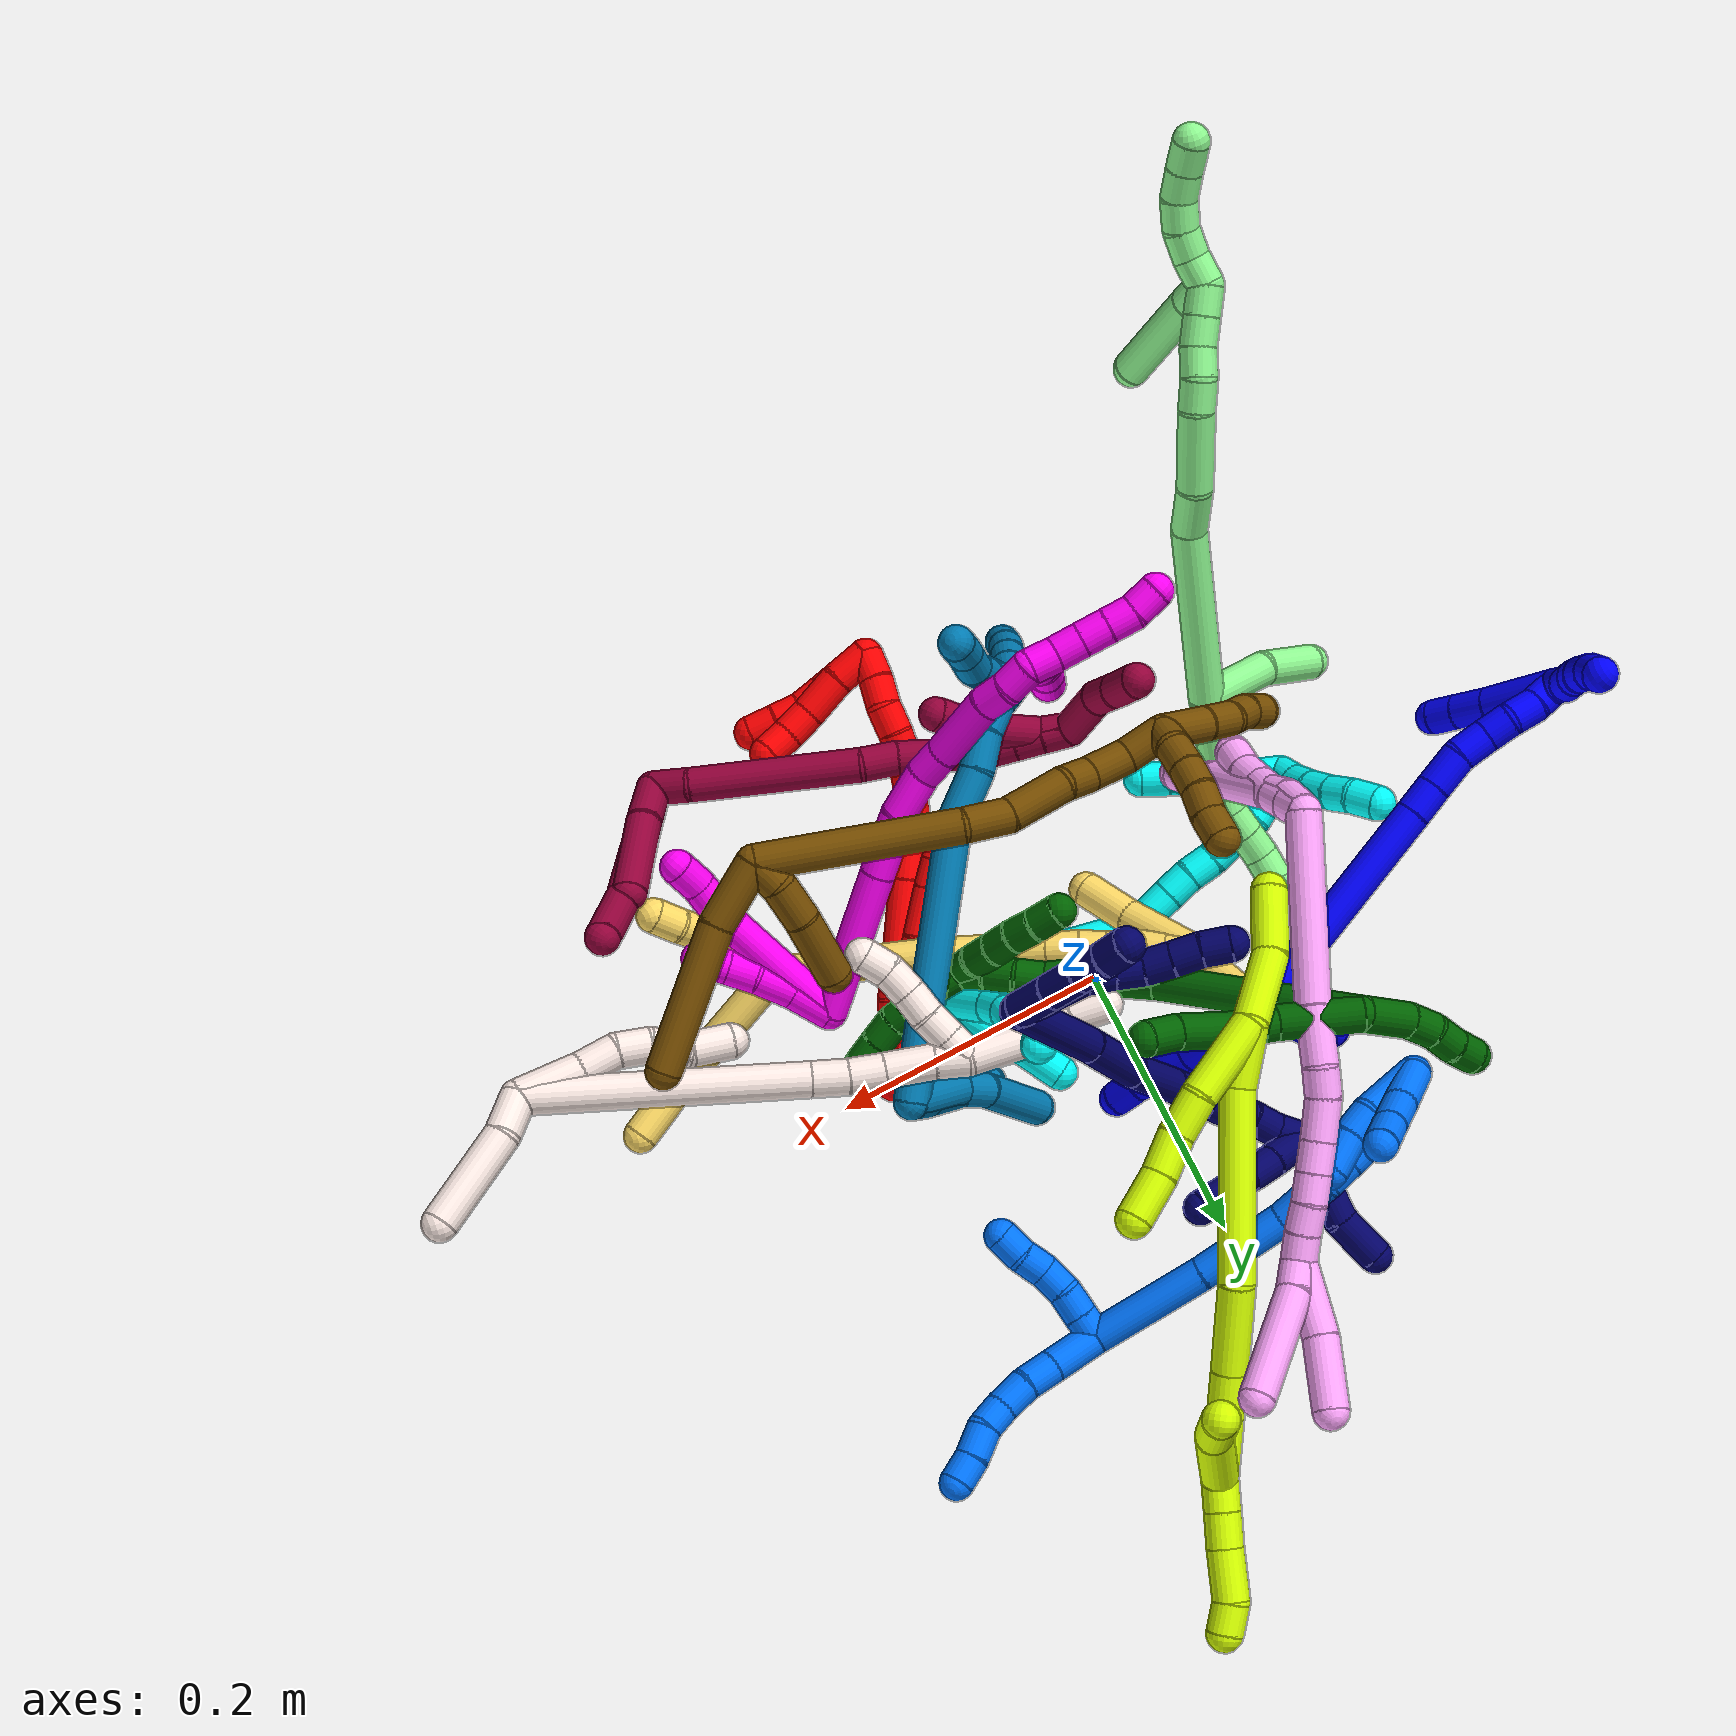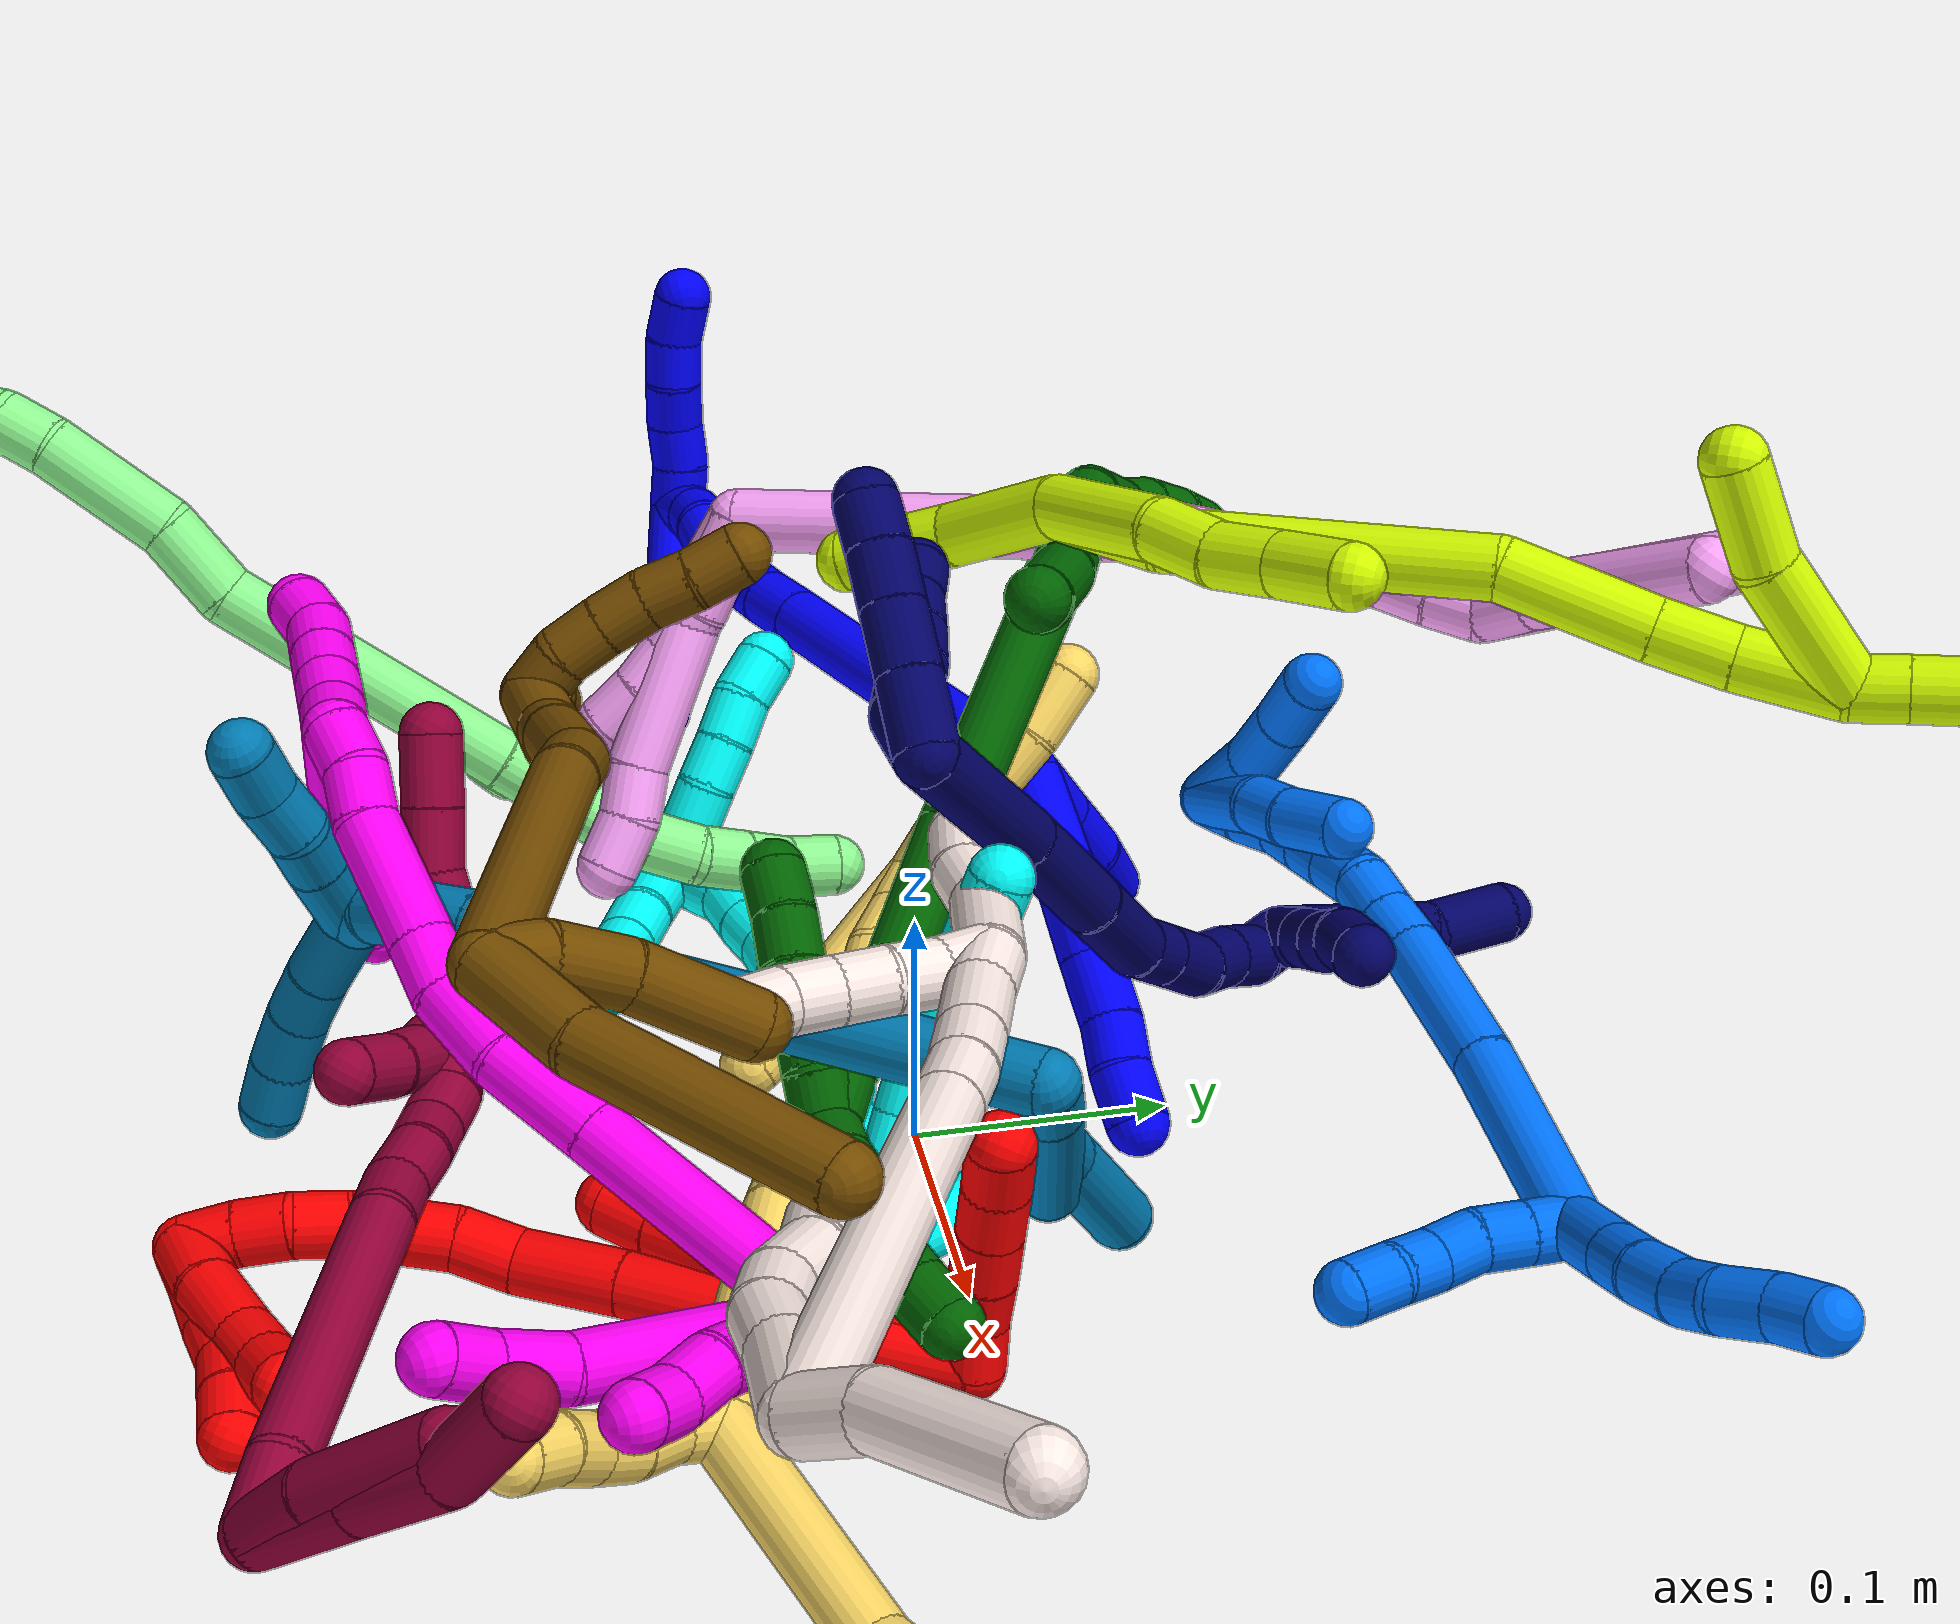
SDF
<sdf version="1.7">
 <world name="default">
  <plugin name="TubeGeneratorPlugin" filename="libtube_generator_plugin.so"/>
  <model name="photoneo_s_sensor">
   <static>1</static>
   <pose>0 0 2 1.57079 1.57079 3.14159</pose>
   <link name="link">
    <inertial><mass>0.1</mass></inertial>
    <sensor name="sensor" type="depth">
     <update_rate>30</update_rate>
     <camera>
      <horizontal_fov>1.22</horizontal_fov>
      <image><width>1920</width><height>1200</height><format>B8G8R8</format></image>
      <clip><near>0.1</near><far>4</far></clip>
      <depth_camera><output>points</output></depth_camera>
     </camera>
     <plugin name="camera_plugin" filename="libgazebo_ros_depth_camera.so">
      <baseline>0.2</baseline>
      <alwaysOn>1</alwaysOn>
      <updateRate>0.0</updateRate>
      <cameraName>camera_ir</cameraName>
      <imageTopicName>/camera/color/image_raw</imageTopicName>
      <cameraInfoTopicName>/camera/color/camera_info</cameraInfoTopicName>
      <depthImageTopicName>/camera/depth/image_raw</depthImageTopicName>
      <depthImageCameraInfoTopicName>/camera/depth/camera_info</depthImageCameraInfoTopicName>
      <pointCloudTopicName>/camera/depth/points</pointCloudTopicName>
      <frameName>fr_optical</frameName>
      <pointCloudCutoff>0.1</pointCloudCutoff>
      <pointCloudCutoffMax>2.0</pointCloudCutoffMax>
      <distortionK1>0</distortionK1>
      <distortionK2>0</distortionK2>
      <distortionK3>0</distortionK3>
      <distortionT1>0</distortionT1>
      <distortionT2>0</distortionT2>
      <CxPrime>0</CxPrime>
      <Cx>0</Cx>
      <Cy>0</Cy>
      <focalLength>0</focalLength>
      <hackBaseline>0</hackBaseline>
     </plugin>
    </sensor>
   </link>
  </model>
  <gravity>0 0 -9.8</gravity>
  <magnetic_field>6e-06 2.3e-05 -4.2e-05</magnetic_field>
  <atmosphere type="adiabatic"/>
  <physics name="default_physics" default="0" type="ode">
   <max_step_size>0.003</max_step_size>
   <real_time_factor>1</real_time_factor>
   <real_time_update_rate>1000</real_time_update_rate>
   <max_contacts>10000</max_contacts>
   <ode>
    <solver>
     <type>quick</type>
     <iters>100</iters>
     <sor>1.3</sor>
     <use_dynamic_moi_rescaling>0</use_dynamic_moi_rescaling>
    </solver>
    <constraints>
     <contact_max_correcting_vel>0</contact_max_correcting_vel>
     <contact_surface_layer>0.001</contact_surface_layer>
     <cfm>0</cfm>
     <erp>0.2</erp>
    </constraints>
   </ode>
  </physics>
  <scene><ambient>0.4 0.4 0.4 1</ambient><background>0.7 0.7 0.7 1</background><shadows>0</shadows></scene>
  <audio><device>default</device></audio>
  <spherical_coordinates>
   <surface_model>EARTH_WGS84</surface_model>
   <latitude_deg>0</latitude_deg>
   <longitude_deg>0</longitude_deg>
   <elevation>0</elevation>
   <heading_deg>0</heading_deg>
  </spherical_coordinates>
  <model name="bin">
   <static>1</static>
   <link name="bottom">
    <collision name="collision-bottom">
     <pose>0 0 -0.01 0 -0 0</pose>
     <geometry><box><size>0.8 0.6 0.02</size></box></geometry>
     <surface>
      <friction><ode><mu>100</mu><mu2>100</mu2></ode></friction>
      <contact><collide_bitmask>65535</collide_bitmask></contact>
     </surface>
    </collision>
   </link>
   <link name="west_wall">
    <collision name="collision-west_wall">
     <pose>-0.41 0 0.1 0 -0 0</pose>
     <geometry><box><size>0.02 0.6 0.2</size></box></geometry>
     <surface>
      <friction><ode><mu>100</mu><mu2>100</mu2></ode></friction>
      <contact><collide_bitmask>65535</collide_bitmask></contact>
     </surface>
    </collision>
   </link>
   <link name="east_wall">
    <collision name="collision-east_wall">
     <pose>0.41 0 0.1 0 -0 0</pose>
     <geometry><box><size>0.02 0.6 0.2</size></box></geometry>
     <surface>
      <friction><ode><mu>100</mu><mu2>100</mu2></ode></friction>
      <contact><collide_bitmask>65535</collide_bitmask></contact>
     </surface>
    </collision>
   </link>
   <link name="south_wall">
    <collision name="collision-south_wall">
     <pose>0 -0.31 0.1 0 -0 0</pose>
     <geometry><box><size>0.8 0.02 0.2</size></box></geometry>
     <surface>
      <friction><ode><mu>100</mu><mu2>100</mu2></ode></friction>
      <contact><collide_bitmask>65535</collide_bitmask></contact>
     </surface>
    </collision>
   </link>
   <link name="north_wall">
    <collision name="collision-north_wall">
     <pose>0 0.31 0.1 0 -0 0</pose>
     <geometry><box><size>0.8 0.02 0.2</size></box></geometry>
     <surface>
      <friction><ode><mu>100</mu><mu2>100</mu2></ode></friction>
      <contact><collide_bitmask>65535</collide_bitmask></contact>
     </surface>
    </collision>
   </link>
  </model>
  <model name="1">
   <static>0</static>
   <link name="1">
    <collision name="collision-cylinder-e_1_2_8">
     <pose>-0.002069 0.002162 -0.019111 -3.02896 -0.107177 1.52103</pose>
     <geometry><cylinder><radius>0.0125</radius><length>0.038688</length></cylinder></geometry>
     <surface>
      <friction><ode><mu>1.16</mu><mu2>1.16</mu2><slip1>0</slip1><slip2>0</slip2></ode></friction>
      <contact><ode><kp>1e+06</kp><kd>1</kd><max_vel>0</max_vel><min_depth>0.001</min_depth></ode></contact>
     </surface>
    </collision>
    <visual name="visual-cylinder-e_1_2_8">
     <pose>-0.002069 0.002162 -0.019111 -3.02896 -0.107177 1.52103</pose>
     <geometry><cylinder><radius>0.0125</radius><length>0.038688</length></cylinder></geometry>
     <material><ambient>0 0 1 1</ambient></material>
    </visual>
    <collision name="collision-cylinder-e_2_8_9">
     <pose>-0.005865 0.005421 -0.058577 -3.08773 -0.084512 2.0071</pose>
     <geometry><cylinder><radius>0.0125</radius><length>0.040915</length></cylinder></geometry>
     <surface>
      <friction><ode><mu>1.16</mu><mu2>1.16</mu2><slip1>0</slip1><slip2>0</slip2></ode></friction>
      <contact><ode><kp>1e+06</kp><kd>1</kd><max_vel>0</max_vel><min_depth>0.001</min_depth></ode></contact>
     </surface>
    </collision>
    <visual name="visual-cylinder-e_2_8_9">
     <pose>-0.005865 0.005421 -0.058577 -3.08773 -0.084512 2.0071</pose>
     <geometry><cylinder><radius>0.0125</radius><length>0.040915</length></cylinder></geometry>
     <material><ambient>0 0 1 1</ambient></material>
    </visual>
    <collision name="collision-cylinder-e_3_9_10">
     <pose>-0.007653 0.007154 -0.092827 -3.09585 -0.004354 0.18976</pose>
     <geometry><cylinder><radius>0.0125</radius><length>0.027818</length></cylinder></geometry>
     <surface>
      <friction><ode><mu>1.16</mu><mu2>1.16</mu2><slip1>0</slip1><slip2>0</slip2></ode></friction>
      <contact><ode><kp>1e+06</kp><kd>1</kd><max_vel>0</max_vel><min_depth>0.001</min_depth></ode></contact>
     </surface>
    </collision>
    <visual name="visual-cylinder-e_3_9_10">
     <pose>-0.007653 0.007154 -0.092827 -3.09585 -0.004354 0.18976</pose>
     <geometry><cylinder><radius>0.0125</radius><length>0.027818</length></cylinder></geometry>
     <material><ambient>0 0 1 1</ambient></material>
    </visual>
    <collision name="collision-cylinder-e_4_10_11">
     <pose>-0.007721 0.006824 -0.116698 3.045 -0.000715 -0.014784</pose>
     <geometry><cylinder><radius>0.0125</radius><length>0.020047</length></cylinder></geometry>
     <surface>
      <friction><ode><mu>1.16</mu><mu2>1.16</mu2><slip1>0</slip1><slip2>0</slip2></ode></friction>
      <contact><ode><kp>1e+06</kp><kd>1</kd><max_vel>0</max_vel><min_depth>0.001</min_depth></ode></contact>
     </surface>
    </collision>
    <visual name="visual-cylinder-e_4_10_11">
     <pose>-0.007721 0.006824 -0.116698 3.045 -0.000715 -0.014784</pose>
     <geometry><cylinder><radius>0.0125</radius><length>0.020047</length></cylinder></geometry>
     <material><ambient>0 0 1 1</ambient></material>
    </visual>
    <collision name="collision-cylinder-e_5_11_6">
     <pose>-0.008571 0.006585 -0.137885 -3.07671 -0.074966 1.71479</pose>
     <geometry><cylinder><radius>0.0125</radius><length>0.022532</length></cylinder></geometry>
     <surface>
      <friction><ode><mu>1.16</mu><mu2>1.16</mu2><slip1>0</slip1><slip2>0</slip2></ode></friction>
      <contact><ode><kp>1e+06</kp><kd>1</kd><max_vel>0</max_vel><min_depth>0.001</min_depth></ode></contact>
     </surface>
    </collision>
    <visual name="visual-cylinder-e_5_11_6">
     <pose>-0.008571 0.006585 -0.137885 -3.07671 -0.074966 1.71479</pose>
     <geometry><cylinder><radius>0.0125</radius><length>0.022532</length></cylinder></geometry>
     <material><ambient>0 0 1 1</ambient></material>
    </visual>
    <collision name="collision-cylinder-e_1_2_12">
     <pose>-0.012327 0.008487 -0.003363 -1.9481 -0.933343 1.27614</pose>
     <geometry><cylinder><radius>0.0125</radius><length>0.030678</length></cylinder></geometry>
     <surface>
      <friction><ode><mu>1.16</mu><mu2>1.16</mu2><slip1>0</slip1><slip2>0</slip2></ode></friction>
      <contact><ode><kp>1e+06</kp><kd>1</kd><max_vel>0</max_vel><min_depth>0.001</min_depth></ode></contact>
     </surface>
    </collision>
    <visual name="visual-cylinder-e_1_2_12">
     <pose>-0.012327 0.008487 -0.003363 -1.9481 -0.933343 1.27614</pose>
     <geometry><cylinder><radius>0.0125</radius><length>0.030678</length></cylinder></geometry>
     <material><ambient>0 0 1 1</ambient></material>
    </visual>
    <collision name="collision-cylinder-e_2_12_13">
     <pose>-0.037353 0.025851 -0.010028 -1.92685 -0.929997 1.25048</pose>
     <geometry><cylinder><radius>0.0125</radius><length>0.031686</length></cylinder></geometry>
     <surface>
      <friction><ode><mu>1.16</mu><mu2>1.16</mu2><slip1>0</slip1><slip2>0</slip2></ode></friction>
      <contact><ode><kp>1e+06</kp><kd>1</kd><max_vel>0</max_vel><min_depth>0.001</min_depth></ode></contact>
     </surface>
    </collision>
    <visual name="visual-cylinder-e_2_12_13">
     <pose>-0.037353 0.025851 -0.010028 -1.92685 -0.929997 1.25048</pose>
     <geometry><cylinder><radius>0.0125</radius><length>0.031686</length></cylinder></geometry>
     <material><ambient>0 0 1 1</ambient></material>
    </visual>
    <collision name="collision-cylinder-e_3_13_5">
     <pose>-0.066857 0.043191 -0.013734 -1.61851 -1.1038 1.14687</pose>
     <geometry><cylinder><radius>0.0125</radius><length>0.037636</length></cylinder></geometry>
     <surface>
      <friction><ode><mu>1.16</mu><mu2>1.16</mu2><slip1>0</slip1><slip2>0</slip2></ode></friction>
      <contact><ode><kp>1e+06</kp><kd>1</kd><max_vel>0</max_vel><min_depth>0.001</min_depth></ode></contact>
     </surface>
    </collision>
    <visual name="visual-cylinder-e_3_13_5">
     <pose>-0.066857 0.043191 -0.013734 -1.61851 -1.1038 1.14687</pose>
     <geometry><cylinder><radius>0.0125</radius><length>0.037636</length></cylinder></geometry>
     <material><ambient>0 0 1 1</ambient></material>
    </visual>
    <collision name="collision-cylinder-e_1_2_14">
     <pose>-0.04363 -0.024755 0.064662 0.36562 -0.562281 -0.106678</pose>
     <geometry><cylinder><radius>0.0125</radius><length>0.163677</length></cylinder></geometry>
     <surface>
      <friction><ode><mu>1.16</mu><mu2>1.16</mu2><slip1>0</slip1><slip2>0</slip2></ode></friction>
      <contact><ode><kp>1e+06</kp><kd>1</kd><max_vel>0</max_vel><min_depth>0.001</min_depth></ode></contact>
     </surface>
    </collision>
    <visual name="visual-cylinder-e_1_2_14">
     <pose>-0.04363 -0.024755 0.064662 0.36562 -0.562281 -0.106678</pose>
     <geometry><cylinder><radius>0.0125</radius><length>0.163677</length></cylinder></geometry>
     <material><ambient>0 0 1 1</ambient></material>
    </visual>
    <collision name="collision-cylinder-e_2_14_15">
     <pose>-0.093599 -0.053163 0.138504 0.37875 -0.570556 -0.112308</pose>
     <geometry><cylinder><radius>0.0125</radius><length>0.023477</length></cylinder></geometry>
     <surface>
      <friction><ode><mu>1.16</mu><mu2>1.16</mu2><slip1>0</slip1><slip2>0</slip2></ode></friction>
      <contact><ode><kp>1e+06</kp><kd>1</kd><max_vel>0</max_vel><min_depth>0.001</min_depth></ode></contact>
     </surface>
    </collision>
    <visual name="visual-cylinder-e_2_14_15">
     <pose>-0.093599 -0.053163 0.138504 0.37875 -0.570556 -0.112308</pose>
     <geometry><cylinder><radius>0.0125</radius><length>0.023477</length></cylinder></geometry>
     <material><ambient>0 0 1 1</ambient></material>
    </visual>
    <collision name="collision-cylinder-e_3_15_16">
     <pose>-0.106845 -0.06099 0.158955 0.354638 -0.521438 -0.095546</pose>
     <geometry><cylinder><radius>0.0125</radius><length>0.027726</length></cylinder></geometry>
     <surface>
      <friction><ode><mu>1.16</mu><mu2>1.16</mu2><slip1>0</slip1><slip2>0</slip2></ode></friction>
      <contact><ode><kp>1e+06</kp><kd>1</kd><max_vel>0</max_vel><min_depth>0.001</min_depth></ode></contact>
     </surface>
    </collision>
    <visual name="visual-cylinder-e_3_15_16">
     <pose>-0.106845 -0.06099 0.158955 0.354638 -0.521438 -0.095546</pose>
     <geometry><cylinder><radius>0.0125</radius><length>0.027726</length></cylinder></geometry>
     <material><ambient>0 0 1 1</ambient></material>
    </visual>
    <collision name="collision-cylinder-e_4_16_17">
     <pose>-0.120544 -0.06562 0.179715 0.047997 -0.620874 -0.015401</pose>
     <geometry><cylinder><radius>0.0125</radius><length>0.023355</length></cylinder></geometry>
     <surface>
      <friction><ode><mu>1.16</mu><mu2>1.16</mu2><slip1>0</slip1><slip2>0</slip2></ode></friction>
      <contact><ode><kp>1e+06</kp><kd>1</kd><max_vel>0</max_vel><min_depth>0.001</min_depth></ode></contact>
     </surface>
    </collision>
    <visual name="visual-cylinder-e_4_16_17">
     <pose>-0.120544 -0.06562 0.179715 0.047997 -0.620874 -0.015401</pose>
     <geometry><cylinder><radius>0.0125</radius><length>0.023355</length></cylinder></geometry>
     <material><ambient>0 0 1 1</ambient></material>
    </visual>
    <collision name="collision-cylinder-e_5_17_18">
     <pose>-0.13181 -0.06618 0.198162 0.011711 -0.463019 -0.002761</pose>
     <geometry><cylinder><radius>0.0125</radius><length>0.02003</length></cylinder></geometry>
     <surface>
      <friction><ode><mu>1.16</mu><mu2>1.16</mu2><slip1>0</slip1><slip2>0</slip2></ode></friction>
      <contact><ode><kp>1e+06</kp><kd>1</kd><max_vel>0</max_vel><min_depth>0.001</min_depth></ode></contact>
     </surface>
    </collision>
    <visual name="visual-cylinder-e_5_17_18">
     <pose>-0.13181 -0.06618 0.198162 0.011711 -0.463019 -0.002761</pose>
     <geometry><cylinder><radius>0.0125</radius><length>0.02003</length></cylinder></geometry>
     <material><ambient>0 0 1 1</ambient></material>
    </visual>
    <collision name="collision-cylinder-e_6_18_19">
     <pose>-0.143731 -0.065536 0.214824 -0.096985 -0.766229 0.039114</pose>
     <geometry><cylinder><radius>0.0125</radius><length>0.02148</length></cylinder></geometry>
     <surface>
      <friction><ode><mu>1.16</mu><mu2>1.16</mu2><slip1>0</slip1><slip2>0</slip2></ode></friction>
      <contact><ode><kp>1e+06</kp><kd>1</kd><max_vel>0</max_vel><min_depth>0.001</min_depth></ode></contact>
     </surface>
    </collision>
    <visual name="visual-cylinder-e_6_18_19">
     <pose>-0.143731 -0.065536 0.214824 -0.096985 -0.766229 0.039114</pose>
     <geometry><cylinder><radius>0.0125</radius><length>0.02148</length></cylinder></geometry>
     <material><ambient>0 0 1 1</ambient></material>
    </visual>
    <collision name="collision-cylinder-e_7_19_1">
     <pose>-0.158584 -0.066203 0.229287 0.206562 -0.820167 -0.090058</pose>
     <geometry><cylinder><radius>0.0125</radius><length>0.020254</length></cylinder></geometry>
     <surface>
      <friction><ode><mu>1.16</mu><mu2>1.16</mu2><slip1>0</slip1><slip2>0</slip2></ode></friction>
      <contact><ode><kp>1e+06</kp><kd>1</kd><max_vel>0</max_vel><min_depth>0.001</min_depth></ode></contact>
     </surface>
    </collision>
    <visual name="visual-cylinder-e_7_19_1">
     <pose>-0.158584 -0.066203 0.229287 0.206562 -0.820167 -0.090058</pose>
     <geometry><cylinder><radius>0.0125</radius><length>0.020254</length></cylinder></geometry>
     <material><ambient>0 0 1 1</ambient></material>
    </visual>
    <collision name="collision-cylinder-e_1_1_20">
     <pose>-0.15866 -0.066599 0.242775 -0.150647 0.822582 -0.065808</pose>
     <geometry><cylinder><radius>0.0125</radius><length>0.02</length></cylinder></geometry>
     <surface>
      <friction><ode><mu>1.16</mu><mu2>1.16</mu2><slip1>0</slip1><slip2>0</slip2></ode></friction>
      <contact><ode><kp>1e+06</kp><kd>1</kd><max_vel>0</max_vel><min_depth>0.001</min_depth></ode></contact>
     </surface>
    </collision>
    <visual name="visual-cylinder-e_1_1_20">
     <pose>-0.15866 -0.066599 0.242775 -0.150647 0.822582 -0.065808</pose>
     <geometry><cylinder><radius>0.0125</radius><length>0.02</length></cylinder></geometry>
     <material><ambient>0 0 1 1</ambient></material>
    </visual>
    <collision name="collision-cylinder-e_2_20_21">
     <pose>-0.144009 -0.066565 0.25624 0.145478 0.821549 0.063454</pose>
     <geometry><cylinder><radius>0.0125</radius><length>0.02</length></cylinder></geometry>
     <surface>
      <friction><ode><mu>1.16</mu><mu2>1.16</mu2><slip1>0</slip1><slip2>0</slip2></ode></friction>
      <contact><ode><kp>1e+06</kp><kd>1</kd><max_vel>0</max_vel><min_depth>0.001</min_depth></ode></contact>
     </surface>
    </collision>
    <visual name="visual-cylinder-e_2_20_21">
     <pose>-0.144009 -0.066565 0.25624 0.145478 0.821549 0.063454</pose>
     <geometry><cylinder><radius>0.0125</radius><length>0.02</length></cylinder></geometry>
     <material><ambient>0 0 1 1</ambient></material>
    </visual>
    <collision name="collision-cylinder-e_3_21_22">
     <pose>-0.128345 -0.067913 0.268482 0.065345 0.986688 0.035144</pose>
     <geometry><cylinder><radius>0.0125</radius><length>0.02</length></cylinder></geometry>
     <surface>
      <friction><ode><mu>1.16</mu><mu2>1.16</mu2><slip1>0</slip1><slip2>0</slip2></ode></friction>
      <contact><ode><kp>1e+06</kp><kd>1</kd><max_vel>0</max_vel><min_depth>0.001</min_depth></ode></contact>
     </surface>
    </collision>
    <visual name="visual-cylinder-e_3_21_22">
     <pose>-0.128345 -0.067913 0.268482 0.065345 0.986688 0.035144</pose>
     <geometry><cylinder><radius>0.0125</radius><length>0.02</length></cylinder></geometry>
     <material><ambient>0 0 1 1</ambient></material>
    </visual>
    <collision name="collision-cylinder-e_4_22_23">
     <pose>-0.112499 -0.06782 0.280578 -0.068516 0.848771 -0.030968</pose>
     <geometry><cylinder><radius>0.0125</radius><length>0.02</length></cylinder></geometry>
     <surface>
      <friction><ode><mu>1.16</mu><mu2>1.16</mu2><slip1>0</slip1><slip2>0</slip2></ode></friction>
      <contact><ode><kp>1e+06</kp><kd>1</kd><max_vel>0</max_vel><min_depth>0.001</min_depth></ode></contact>
     </surface>
    </collision>
    <visual name="visual-cylinder-e_4_22_23">
     <pose>-0.112499 -0.06782 0.280578 -0.068516 0.848771 -0.030968</pose>
     <geometry><cylinder><radius>0.0125</radius><length>0.02</length></cylinder></geometry>
     <material><ambient>0 0 1 1</ambient></material>
    </visual>
    <collision name="collision-cylinder-e_5_23_4">
     <pose>-0.096684 -0.06549 0.292407 -0.344339 0.980923 -0.185178</pose>
     <geometry><cylinder><radius>0.0125</radius><length>0.02</length></cylinder></geometry>
     <surface>
      <friction><ode><mu>1.16</mu><mu2>1.16</mu2><slip1>0</slip1><slip2>0</slip2></ode></friction>
      <contact><ode><kp>1e+06</kp><kd>1</kd><max_vel>0</max_vel><min_depth>0.001</min_depth></ode></contact>
     </surface>
    </collision>
    <visual name="visual-cylinder-e_5_23_4">
     <pose>-0.096684 -0.06549 0.292407 -0.344339 0.980923 -0.185178</pose>
     <geometry><cylinder><radius>0.0125</radius><length>0.02</length></cylinder></geometry>
     <material><ambient>0 0 1 1</ambient></material>
    </visual>
    <collision name="collision-cylinder-e_1_1_24">
     <pose>-0.169761 -0.074069 0.210168 2.89737 -0.140483 -1.04114</pose>
     <geometry><cylinder><radius>0.0125</radius><length>0.053875</length></cylinder></geometry>
     <surface>
      <friction><ode><mu>1.16</mu><mu2>1.16</mu2><slip1>0</slip1><slip2>0</slip2></ode></friction>
      <contact><ode><kp>1e+06</kp><kd>1</kd><max_vel>0</max_vel><min_depth>0.001</min_depth></ode></contact>
     </surface>
    </collision>
    <visual name="visual-cylinder-e_1_1_24">
     <pose>-0.169761 -0.074069 0.210168 2.89737 -0.140483 -1.04114</pose>
     <geometry><cylinder><radius>0.0125</radius><length>0.053875</length></cylinder></geometry>
     <material><ambient>0 0 1 1</ambient></material>
    </visual>
    <collision name="collision-cylinder-e_2_24_25">
     <pose>-0.175877 -0.084097 0.172057 2.85693 -0.181871 -1.13342</pose>
     <geometry><cylinder><radius>0.0125</radius><length>0.025912</length></cylinder></geometry>
     <surface>
      <friction><ode><mu>1.16</mu><mu2>1.16</mu2><slip1>0</slip1><slip2>0</slip2></ode></friction>
      <contact><ode><kp>1e+06</kp><kd>1</kd><max_vel>0</max_vel><min_depth>0.001</min_depth></ode></contact>
     </surface>
    </collision>
    <visual name="visual-cylinder-e_2_24_25">
     <pose>-0.175877 -0.084097 0.172057 2.85693 -0.181871 -1.13342</pose>
     <geometry><cylinder><radius>0.0125</radius><length>0.025912</length></cylinder></geometry>
     <material><ambient>0 0 1 1</ambient></material>
    </visual>
    <collision name="collision-cylinder-e_3_25_3">
     <pose>-0.179654 -0.09049 0.150228 2.8564 -0.142362 -0.921883</pose>
     <geometry><cylinder><radius>0.0125</radius><length>0.020213</length></cylinder></geometry>
     <surface>
      <friction><ode><mu>1.16</mu><mu2>1.16</mu2><slip1>0</slip1><slip2>0</slip2></ode></friction>
      <contact><ode><kp>1e+06</kp><kd>1</kd><max_vel>0</max_vel><min_depth>0.001</min_depth></ode></contact>
     </surface>
    </collision>
    <visual name="visual-cylinder-e_3_25_3">
     <pose>-0.179654 -0.09049 0.150228 2.8564 -0.142362 -0.921883</pose>
     <geometry><cylinder><radius>0.0125</radius><length>0.020213</length></cylinder></geometry>
     <material><ambient>0 0 1 1</ambient></material>
    </visual>
    <collision name="collision-sphere-3">
     <pose>-0.181088 -0.093305 0.140628 0 -0 0</pose>
     <geometry><sphere><radius>0.0125</radius></sphere></geometry>
     <surface>
      <friction><ode><mu>1.16</mu><mu2>1.16</mu2><slip1>0</slip1><slip2>0</slip2></ode></friction>
      <contact><ode><kp>1e+06</kp><kd>1</kd><max_vel>0</max_vel><min_depth>0.001</min_depth></ode></contact>
     </surface>
    </collision>
    <visual name="visual-sphere-3">
     <pose>-0.181088 -0.093305 0.140628 0 -0 0</pose>
     <geometry><sphere><radius>0.0125</radius></sphere></geometry>
     <material><ambient>0 0 1 1</ambient></material>
    </visual>
    <collision name="collision-sphere-25">
     <pose>-0.17822 -0.087676 0.159828 0 -0 0</pose>
     <geometry><sphere><radius>0.0125</radius></sphere></geometry>
     <surface>
      <friction><ode><mu>1.16</mu><mu2>1.16</mu2><slip1>0</slip1><slip2>0</slip2></ode></friction>
      <contact><ode><kp>1e+06</kp><kd>1</kd><max_vel>0</max_vel><min_depth>0.001</min_depth></ode></contact>
     </surface>
    </collision>
    <visual name="visual-sphere-25">
     <pose>-0.17822 -0.087676 0.159828 0 -0 0</pose>
     <geometry><sphere><radius>0.0125</radius></sphere></geometry>
     <material><ambient>0 0 1 1</ambient></material>
    </visual>
    <collision name="collision-sphere-24">
     <pose>-0.173533 -0.080519 0.184287 0 -0 0</pose>
     <geometry><sphere><radius>0.0125</radius></sphere></geometry>
     <surface>
      <friction><ode><mu>1.16</mu><mu2>1.16</mu2><slip1>0</slip1><slip2>0</slip2></ode></friction>
      <contact><ode><kp>1e+06</kp><kd>1</kd><max_vel>0</max_vel><min_depth>0.001</min_depth></ode></contact>
     </surface>
    </collision>
    <visual name="visual-sphere-24">
     <pose>-0.173533 -0.080519 0.184287 0 -0 0</pose>
     <geometry><sphere><radius>0.0125</radius></sphere></geometry>
     <material><ambient>0 0 1 1</ambient></material>
    </visual>
    <collision name="collision-sphere-4">
     <pose>-0.088374 -0.063612 0.297644 0 -0 0</pose>
     <geometry><sphere><radius>0.0125</radius></sphere></geometry>
     <surface>
      <friction><ode><mu>1.16</mu><mu2>1.16</mu2><slip1>0</slip1><slip2>0</slip2></ode></friction>
      <contact><ode><kp>1e+06</kp><kd>1</kd><max_vel>0</max_vel><min_depth>0.001</min_depth></ode></contact>
     </surface>
    </collision>
    <visual name="visual-sphere-4">
     <pose>-0.088374 -0.063612 0.297644 0 -0 0</pose>
     <geometry><sphere><radius>0.0125</radius></sphere></geometry>
     <material><ambient>0 0 1 1</ambient></material>
    </visual>
    <collision name="collision-sphere-23">
     <pose>-0.104994 -0.067368 0.287171 0 -0 0</pose>
     <geometry><sphere><radius>0.0125</radius></sphere></geometry>
     <surface>
      <friction><ode><mu>1.16</mu><mu2>1.16</mu2><slip1>0</slip1><slip2>0</slip2></ode></friction>
      <contact><ode><kp>1e+06</kp><kd>1</kd><max_vel>0</max_vel><min_depth>0.001</min_depth></ode></contact>
     </surface>
    </collision>
    <visual name="visual-sphere-23">
     <pose>-0.104994 -0.067368 0.287171 0 -0 0</pose>
     <geometry><sphere><radius>0.0125</radius></sphere></geometry>
     <material><ambient>0 0 1 1</ambient></material>
    </visual>
    <collision name="collision-sphere-22">
     <pose>-0.120003 -0.068273 0.273984 0 -0 0</pose>
     <geometry><sphere><radius>0.0125</radius></sphere></geometry>
     <surface>
      <friction><ode><mu>1.16</mu><mu2>1.16</mu2><slip1>0</slip1><slip2>0</slip2></ode></friction>
      <contact><ode><kp>1e+06</kp><kd>1</kd><max_vel>0</max_vel><min_depth>0.001</min_depth></ode></contact>
     </surface>
    </collision>
    <visual name="visual-sphere-22">
     <pose>-0.120003 -0.068273 0.273984 0 -0 0</pose>
     <geometry><sphere><radius>0.0125</radius></sphere></geometry>
     <material><ambient>0 0 1 1</ambient></material>
    </visual>
    <collision name="collision-sphere-21">
     <pose>-0.136687 -0.067553 0.262979 0 -0 0</pose>
     <geometry><sphere><radius>0.0125</radius></sphere></geometry>
     <surface>
      <friction><ode><mu>1.16</mu><mu2>1.16</mu2><slip1>0</slip1><slip2>0</slip2></ode></friction>
      <contact><ode><kp>1e+06</kp><kd>1</kd><max_vel>0</max_vel><min_depth>0.001</min_depth></ode></contact>
     </surface>
    </collision>
    <visual name="visual-sphere-21">
     <pose>-0.136687 -0.067553 0.262979 0 -0 0</pose>
     <geometry><sphere><radius>0.0125</radius></sphere></geometry>
     <material><ambient>0 0 1 1</ambient></material>
    </visual>
    <collision name="collision-sphere-20">
     <pose>-0.151331 -0.065578 0.249501 0 -0 0</pose>
     <geometry><sphere><radius>0.0125</radius></sphere></geometry>
     <surface>
      <friction><ode><mu>1.16</mu><mu2>1.16</mu2><slip1>0</slip1><slip2>0</slip2></ode></friction>
      <contact><ode><kp>1e+06</kp><kd>1</kd><max_vel>0</max_vel><min_depth>0.001</min_depth></ode></contact>
     </surface>
    </collision>
    <visual name="visual-sphere-20">
     <pose>-0.151331 -0.065578 0.249501 0 -0 0</pose>
     <geometry><sphere><radius>0.0125</radius></sphere></geometry>
     <material><ambient>0 0 1 1</ambient></material>
    </visual>
    <collision name="collision-sphere-6">
     <pose>-0.009415 0.007314 -0.149096 0 -0 0</pose>
     <geometry><sphere><radius>0.0125</radius></sphere></geometry>
     <surface>
      <friction><ode><mu>1.16</mu><mu2>1.16</mu2><slip1>0</slip1><slip2>0</slip2></ode></friction>
      <contact><ode><kp>1e+06</kp><kd>1</kd><max_vel>0</max_vel><min_depth>0.001</min_depth></ode></contact>
     </surface>
    </collision>
    <visual name="visual-sphere-6">
     <pose>-0.009415 0.007314 -0.149096 0 -0 0</pose>
     <geometry><sphere><radius>0.0125</radius></sphere></geometry>
     <material><ambient>0 0 1 1</ambient></material>
    </visual>
    <collision name="collision-sphere-11">
     <pose>-0.007728 0.005857 -0.126675 0 -0 0</pose>
     <geometry><sphere><radius>0.0125</radius></sphere></geometry>
     <surface>
      <friction><ode><mu>1.16</mu><mu2>1.16</mu2><slip1>0</slip1><slip2>0</slip2></ode></friction>
      <contact><ode><kp>1e+06</kp><kd>1</kd><max_vel>0</max_vel><min_depth>0.001</min_depth></ode></contact>
     </surface>
    </collision>
    <visual name="visual-sphere-11">
     <pose>-0.007728 0.005857 -0.126675 0 -0 0</pose>
     <geometry><sphere><radius>0.0125</radius></sphere></geometry>
     <material><ambient>0 0 1 1</ambient></material>
    </visual>
    <collision name="collision-sphere-10">
     <pose>-0.007713 0.00779 -0.106721 0 -0 0</pose>
     <geometry><sphere><radius>0.0125</radius></sphere></geometry>
     <surface>
      <friction><ode><mu>1.16</mu><mu2>1.16</mu2><slip1>0</slip1><slip2>0</slip2></ode></friction>
      <contact><ode><kp>1e+06</kp><kd>1</kd><max_vel>0</max_vel><min_depth>0.001</min_depth></ode></contact>
     </surface>
    </collision>
    <visual name="visual-sphere-10">
     <pose>-0.007713 0.00779 -0.106721 0 -0 0</pose>
     <geometry><sphere><radius>0.0125</radius></sphere></geometry>
     <material><ambient>0 0 1 1</ambient></material>
    </visual>
    <collision name="collision-sphere-9">
     <pose>-0.007592 0.006518 -0.078932 0 -0 0</pose>
     <geometry><sphere><radius>0.0125</radius></sphere></geometry>
     <surface>
      <friction><ode><mu>1.16</mu><mu2>1.16</mu2><slip1>0</slip1><slip2>0</slip2></ode></friction>
      <contact><ode><kp>1e+06</kp><kd>1</kd><max_vel>0</max_vel><min_depth>0.001</min_depth></ode></contact>
     </surface>
    </collision>
    <visual name="visual-sphere-9">
     <pose>-0.007592 0.006518 -0.078932 0 -0 0</pose>
     <geometry><sphere><radius>0.0125</radius></sphere></geometry>
     <material><ambient>0 0 1 1</ambient></material>
    </visual>
    <collision name="collision-sphere-2">
     <geometry><sphere><radius>0.0125</radius></sphere></geometry>
     <surface>
      <friction><ode><mu>1.16</mu><mu2>1.16</mu2><slip1>0</slip1><slip2>0</slip2></ode></friction>
      <contact><ode><kp>1e+06</kp><kd>1</kd><max_vel>0</max_vel><min_depth>0.001</min_depth></ode></contact>
     </surface>
    </collision>
    <visual name="visual-sphere-2">
     <geometry><sphere><radius>0.0125</radius></sphere></geometry>
     <material><ambient>0 0 1 1</ambient></material>
    </visual>
    <collision name="collision-sphere-19">
     <pose>-0.151178 -0.064786 0.222527 0 -0 0</pose>
     <geometry><sphere><radius>0.0125</radius></sphere></geometry>
     <surface>
      <friction><ode><mu>1.16</mu><mu2>1.16</mu2><slip1>0</slip1><slip2>0</slip2></ode></friction>
      <contact><ode><kp>1e+06</kp><kd>1</kd><max_vel>0</max_vel><min_depth>0.001</min_depth></ode></contact>
     </surface>
    </collision>
    <visual name="visual-sphere-19">
     <pose>-0.151178 -0.064786 0.222527 0 -0 0</pose>
     <geometry><sphere><radius>0.0125</radius></sphere></geometry>
     <material><ambient>0 0 1 1</ambient></material>
    </visual>
    <collision name="collision-sphere-8">
     <pose>-0.004139 0.004324 -0.038222 0 -0 0</pose>
     <geometry><sphere><radius>0.0125</radius></sphere></geometry>
     <surface>
      <friction><ode><mu>1.16</mu><mu2>1.16</mu2><slip1>0</slip1><slip2>0</slip2></ode></friction>
      <contact><ode><kp>1e+06</kp><kd>1</kd><max_vel>0</max_vel><min_depth>0.001</min_depth></ode></contact>
     </surface>
    </collision>
    <visual name="visual-sphere-8">
     <pose>-0.004139 0.004324 -0.038222 0 -0 0</pose>
     <geometry><sphere><radius>0.0125</radius></sphere></geometry>
     <material><ambient>0 0 1 1</ambient></material>
    </visual>
    <collision name="collision-sphere-12">
     <pose>-0.024653 0.016974 -0.006727 0 -0 0</pose>
     <geometry><sphere><radius>0.0125</radius></sphere></geometry>
     <surface>
      <friction><ode><mu>1.16</mu><mu2>1.16</mu2><slip1>0</slip1><slip2>0</slip2></ode></friction>
      <contact><ode><kp>1e+06</kp><kd>1</kd><max_vel>0</max_vel><min_depth>0.001</min_depth></ode></contact>
     </surface>
    </collision>
    <visual name="visual-sphere-12">
     <pose>-0.024653 0.016974 -0.006727 0 -0 0</pose>
     <geometry><sphere><radius>0.0125</radius></sphere></geometry>
     <material><ambient>0 0 1 1</ambient></material>
    </visual>
    <collision name="collision-sphere-13">
     <pose>-0.050054 0.034729 -0.01333 0 -0 0</pose>
     <geometry><sphere><radius>0.0125</radius></sphere></geometry>
     <surface>
      <friction><ode><mu>1.16</mu><mu2>1.16</mu2><slip1>0</slip1><slip2>0</slip2></ode></friction>
      <contact><ode><kp>1e+06</kp><kd>1</kd><max_vel>0</max_vel><min_depth>0.001</min_depth></ode></contact>
     </surface>
    </collision>
    <visual name="visual-sphere-13">
     <pose>-0.050054 0.034729 -0.01333 0 -0 0</pose>
     <geometry><sphere><radius>0.0125</radius></sphere></geometry>
     <material><ambient>0 0 1 1</ambient></material>
    </visual>
    <collision name="collision-sphere-5">
     <pose>-0.083659 0.051653 -0.014138 0 -0 0</pose>
     <geometry><sphere><radius>0.0125</radius></sphere></geometry>
     <surface>
      <friction><ode><mu>1.16</mu><mu2>1.16</mu2><slip1>0</slip1><slip2>0</slip2></ode></friction>
      <contact><ode><kp>1e+06</kp><kd>1</kd><max_vel>0</max_vel><min_depth>0.001</min_depth></ode></contact>
     </surface>
    </collision>
    <visual name="visual-sphere-5">
     <pose>-0.083659 0.051653 -0.014138 0 -0 0</pose>
     <geometry><sphere><radius>0.0125</radius></sphere></geometry>
     <material><ambient>0 0 1 1</ambient></material>
    </visual>
    <collision name="collision-sphere-14">
     <pose>-0.087259 -0.04951 0.129325 0 -0 0</pose>
     <geometry><sphere><radius>0.0125</radius></sphere></geometry>
     <surface>
      <friction><ode><mu>1.16</mu><mu2>1.16</mu2><slip1>0</slip1><slip2>0</slip2></ode></friction>
      <contact><ode><kp>1e+06</kp><kd>1</kd><max_vel>0</max_vel><min_depth>0.001</min_depth></ode></contact>
     </surface>
    </collision>
    <visual name="visual-sphere-14">
     <pose>-0.087259 -0.04951 0.129325 0 -0 0</pose>
     <geometry><sphere><radius>0.0125</radius></sphere></geometry>
     <material><ambient>0 0 1 1</ambient></material>
    </visual>
    <collision name="collision-sphere-15">
     <pose>-0.099939 -0.056816 0.147683 0 -0 0</pose>
     <geometry><sphere><radius>0.0125</radius></sphere></geometry>
     <surface>
      <friction><ode><mu>1.16</mu><mu2>1.16</mu2><slip1>0</slip1><slip2>0</slip2></ode></friction>
      <contact><ode><kp>1e+06</kp><kd>1</kd><max_vel>0</max_vel><min_depth>0.001</min_depth></ode></contact>
     </surface>
    </collision>
    <visual name="visual-sphere-15">
     <pose>-0.099939 -0.056816 0.147683 0 -0 0</pose>
     <geometry><sphere><radius>0.0125</radius></sphere></geometry>
     <material><ambient>0 0 1 1</ambient></material>
    </visual>
    <collision name="collision-sphere-16">
     <pose>-0.11375 -0.065164 0.170228 0 -0 0</pose>
     <geometry><sphere><radius>0.0125</radius></sphere></geometry>
     <surface>
      <friction><ode><mu>1.16</mu><mu2>1.16</mu2><slip1>0</slip1><slip2>0</slip2></ode></friction>
      <contact><ode><kp>1e+06</kp><kd>1</kd><max_vel>0</max_vel><min_depth>0.001</min_depth></ode></contact>
     </surface>
    </collision>
    <visual name="visual-sphere-16">
     <pose>-0.11375 -0.065164 0.170228 0 -0 0</pose>
     <geometry><sphere><radius>0.0125</radius></sphere></geometry>
     <material><ambient>0 0 1 1</ambient></material>
    </visual>
    <collision name="collision-sphere-17">
     <pose>-0.127337 -0.066075 0.189202 0 -0 0</pose>
     <geometry><sphere><radius>0.0125</radius></sphere></geometry>
     <surface>
      <friction><ode><mu>1.16</mu><mu2>1.16</mu2><slip1>0</slip1><slip2>0</slip2></ode></friction>
      <contact><ode><kp>1e+06</kp><kd>1</kd><max_vel>0</max_vel><min_depth>0.001</min_depth></ode></contact>
     </surface>
    </collision>
    <visual name="visual-sphere-17">
     <pose>-0.127337 -0.066075 0.189202 0 -0 0</pose>
     <geometry><sphere><radius>0.0125</radius></sphere></geometry>
     <material><ambient>0 0 1 1</ambient></material>
    </visual>
    <collision name="collision-sphere-18">
     <pose>-0.136284 -0.066285 0.207122 0 -0 0</pose>
     <geometry><sphere><radius>0.0125</radius></sphere></geometry>
     <surface>
      <friction><ode><mu>1.16</mu><mu2>1.16</mu2><slip1>0</slip1><slip2>0</slip2></ode></friction>
      <contact><ode><kp>1e+06</kp><kd>1</kd><max_vel>0</max_vel><min_depth>0.001</min_depth></ode></contact>
     </surface>
    </collision>
    <visual name="visual-sphere-18">
     <pose>-0.136284 -0.066285 0.207122 0 -0 0</pose>
     <geometry><sphere><radius>0.0125</radius></sphere></geometry>
     <material><ambient>0 0 1 1</ambient></material>
    </visual>
    <collision name="collision-sphere-1">
     <pose>-0.165989 -0.06762 0.236048 0 -0 0</pose>
     <geometry><sphere><radius>0.0125</radius></sphere></geometry>
     <surface>
      <friction><ode><mu>1.16</mu><mu2>1.16</mu2><slip1>0</slip1><slip2>0</slip2></ode></friction>
      <contact><ode><kp>1e+06</kp><kd>1</kd><max_vel>0</max_vel><min_depth>0.001</min_depth></ode></contact>
     </surface>
    </collision>
    <visual name="visual-sphere-1">
     <pose>-0.165989 -0.06762 0.236048 0 -0 0</pose>
     <geometry><sphere><radius>0.0125</radius></sphere></geometry>
     <material><ambient>0 0 1 1</ambient></material>
    </visual>
    <inertial>
     <pose>-0.078871 -0.031719 0.092257 0 -0 0</pose>
     <mass>0.75</mass>
     <inertia>
      <ixx>0.000296</ixx>
      <ixy>0</ixy>
      <ixz>0</ixz>
      <iyy>0.00034</iyy>
      <iyz>0</iyz>
      <izz>0.000328</izz>
     </inertia>
    </inertial>
   </link>
   <pose>-0.095666 0.066032 0.098603 -0.085623 -1.01807 0.17884</pose>
  </model>
  <model name="2">
   <static>0</static>
   <link name="2">
    <collision name="collision-cylinder-e_1_2_8">
     <pose>-0.004675 -0.000188 0.027952 0.006713 -0.16573 -0.000558</pose>
     <geometry><cylinder><radius>0.0125</radius><length>0.056681</length></cylinder></geometry>
     <surface>
      <friction><ode><mu>1.16</mu><mu2>1.16</mu2><slip1>0</slip1><slip2>0</slip2></ode></friction>
      <contact><ode><kp>1e+06</kp><kd>1</kd><max_vel>0</max_vel><min_depth>0.001</min_depth></ode></contact>
     </surface>
    </collision>
    <visual name="visual-cylinder-e_1_2_8">
     <pose>-0.004675 -0.000188 0.027952 0.006713 -0.16573 -0.000558</pose>
     <geometry><cylinder><radius>0.0125</radius><length>0.056681</length></cylinder></geometry>
     <material><ambient>1 0 0 1</ambient></material>
    </visual>
    <collision name="collision-cylinder-e_2_8_9">
     <pose>-0.012399 0.00077 0.074243 -0.062341 -0.164384 0.005137</pose>
     <geometry><cylinder><radius>0.0125</radius><length>0.037254</length></cylinder></geometry>
     <surface>
      <friction><ode><mu>1.16</mu><mu2>1.16</mu2><slip1>0</slip1><slip2>0</slip2></ode></friction>
      <contact><ode><kp>1e+06</kp><kd>1</kd><max_vel>0</max_vel><min_depth>0.001</min_depth></ode></contact>
     </surface>
    </collision>
    <visual name="visual-cylinder-e_2_8_9">
     <pose>-0.012399 0.00077 0.074243 -0.062341 -0.164384 0.005137</pose>
     <geometry><cylinder><radius>0.0125</radius><length>0.037254</length></cylinder></geometry>
     <material><ambient>1 0 0 1</ambient></material>
    </visual>
    <collision name="collision-cylinder-e_3_9_10">
     <pose>-0.020531 0.000943 0.109387 0.057762 -0.293323 -0.008535</pose>
     <geometry><cylinder><radius>0.0125</radius><length>0.035165</length></cylinder></geometry>
     <surface>
      <friction><ode><mu>1.16</mu><mu2>1.16</mu2><slip1>0</slip1><slip2>0</slip2></ode></friction>
      <contact><ode><kp>1e+06</kp><kd>1</kd><max_vel>0</max_vel><min_depth>0.001</min_depth></ode></contact>
     </surface>
    </collision>
    <visual name="visual-cylinder-e_3_9_10">
     <pose>-0.020531 0.000943 0.109387 0.057762 -0.293323 -0.008535</pose>
     <geometry><cylinder><radius>0.0125</radius><length>0.035165</length></cylinder></geometry>
     <material><ambient>1 0 0 1</ambient></material>
    </visual>
    <collision name="collision-cylinder-e_4_10_6">
     <pose>-0.028701 7.7e-05 0.136174 -0.010639 -0.299785 0.001607</pose>
     <geometry><cylinder><radius>0.0125</radius><length>0.0209</length></cylinder></geometry>
     <surface>
      <friction><ode><mu>1.16</mu><mu2>1.16</mu2><slip1>0</slip1><slip2>0</slip2></ode></friction>
      <contact><ode><kp>1e+06</kp><kd>1</kd><max_vel>0</max_vel><min_depth>0.001</min_depth></ode></contact>
     </surface>
    </collision>
    <visual name="visual-cylinder-e_4_10_6">
     <pose>-0.028701 7.7e-05 0.136174 -0.010639 -0.299785 0.001607</pose>
     <geometry><cylinder><radius>0.0125</radius><length>0.0209</length></cylinder></geometry>
     <material><ambient>1 0 0 1</ambient></material>
    </visual>
    <collision name="collision-cylinder-e_1_2_11">
     <pose>0.004815 0.008401 0.002497 -1.28192 0.502422 -0.378335</pose>
     <geometry><cylinder><radius>0.0125</radius><length>0.02</length></cylinder></geometry>
     <surface>
      <friction><ode><mu>1.16</mu><mu2>1.16</mu2><slip1>0</slip1><slip2>0</slip2></ode></friction>
      <contact><ode><kp>1e+06</kp><kd>1</kd><max_vel>0</max_vel><min_depth>0.001</min_depth></ode></contact>
     </surface>
    </collision>
    <visual name="visual-cylinder-e_1_2_11">
     <pose>0.004815 0.008401 0.002497 -1.28192 0.502422 -0.378335</pose>
     <geometry><cylinder><radius>0.0125</radius><length>0.02</length></cylinder></geometry>
     <material><ambient>1 0 0 1</ambient></material>
    </visual>
    <collision name="collision-cylinder-e_2_11_12">
     <pose>0.016037 0.024385 0.006204 -1.41249 0.695228 -0.599517</pose>
     <geometry><cylinder><radius>0.0125</radius><length>0.02</length></cylinder></geometry>
     <surface>
      <friction><ode><mu>1.16</mu><mu2>1.16</mu2><slip1>0</slip1><slip2>0</slip2></ode></friction>
      <contact><ode><kp>1e+06</kp><kd>1</kd><max_vel>0</max_vel><min_depth>0.001</min_depth></ode></contact>
     </surface>
    </collision>
    <visual name="visual-cylinder-e_2_11_12">
     <pose>0.016037 0.024385 0.006204 -1.41249 0.695228 -0.599517</pose>
     <geometry><cylinder><radius>0.0125</radius><length>0.02</length></cylinder></geometry>
     <material><ambient>1 0 0 1</ambient></material>
    </visual>
    <collision name="collision-cylinder-e_3_12_13">
     <pose>0.028741 0.039573 0.008995 -1.36585 0.681367 -0.56155</pose>
     <geometry><cylinder><radius>0.0125</radius><length>0.02</length></cylinder></geometry>
     <surface>
      <friction><ode><mu>1.16</mu><mu2>1.16</mu2><slip1>0</slip1><slip2>0</slip2></ode></friction>
      <contact><ode><kp>1e+06</kp><kd>1</kd><max_vel>0</max_vel><min_depth>0.001</min_depth></ode></contact>
     </surface>
    </collision>
    <visual name="visual-cylinder-e_3_12_13">
     <pose>0.028741 0.039573 0.008995 -1.36585 0.681367 -0.56155</pose>
     <geometry><cylinder><radius>0.0125</radius><length>0.02</length></cylinder></geometry>
     <material><ambient>1 0 0 1</ambient></material>
    </visual>
    <collision name="collision-cylinder-e_4_13_14">
     <pose>0.041337 0.054785 0.012149 -1.36688 0.681201 -0.561974</pose>
     <geometry><cylinder><radius>0.0125</radius><length>0.02</length></cylinder></geometry>
     <surface>
      <friction><ode><mu>1.16</mu><mu2>1.16</mu2><slip1>0</slip1><slip2>0</slip2></ode></friction>
      <contact><ode><kp>1e+06</kp><kd>1</kd><max_vel>0</max_vel><min_depth>0.001</min_depth></ode></contact>
     </surface>
    </collision>
    <visual name="visual-cylinder-e_4_13_14">
     <pose>0.041337 0.054785 0.012149 -1.36688 0.681201 -0.561974</pose>
     <geometry><cylinder><radius>0.0125</radius><length>0.02</length></cylinder></geometry>
     <material><ambient>1 0 0 1</ambient></material>
    </visual>
    <collision name="collision-cylinder-e_5_14_5">
     <pose>0.054694 0.06928 0.01537 -1.33598 0.783798 -0.630398</pose>
     <geometry><cylinder><radius>0.0125</radius><length>0.02</length></cylinder></geometry>
     <surface>
      <friction><ode><mu>1.16</mu><mu2>1.16</mu2><slip1>0</slip1><slip2>0</slip2></ode></friction>
      <contact><ode><kp>1e+06</kp><kd>1</kd><max_vel>0</max_vel><min_depth>0.001</min_depth></ode></contact>
     </surface>
    </collision>
    <visual name="visual-cylinder-e_5_14_5">
     <pose>0.054694 0.06928 0.01537 -1.33598 0.783798 -0.630398</pose>
     <geometry><cylinder><radius>0.0125</radius><length>0.02</length></cylinder></geometry>
     <material><ambient>1 0 0 1</ambient></material>
    </visual>
    <collision name="collision-cylinder-e_1_2_15">
     <pose>-0.001123 -0.00434 0.023057 0.186049 -0.047845 -0.004464</pose>
     <geometry><cylinder><radius>0.0125</radius><length>0.046977</length></cylinder></geometry>
     <surface>
      <friction><ode><mu>1.16</mu><mu2>1.16</mu2><slip1>0</slip1><slip2>0</slip2></ode></friction>
      <contact><ode><kp>1e+06</kp><kd>1</kd><max_vel>0</max_vel><min_depth>0.001</min_depth></ode></contact>
     </surface>
    </collision>
    <visual name="visual-cylinder-e_1_2_15">
     <pose>-0.001123 -0.00434 0.023057 0.186049 -0.047845 -0.004464</pose>
     <geometry><cylinder><radius>0.0125</radius><length>0.046977</length></cylinder></geometry>
     <material><ambient>1 0 0 1</ambient></material>
    </visual>
    <collision name="collision-cylinder-e_2_15_16">
     <pose>-0.012077 -0.016119 0.086865 0.180555 -0.233002 -0.021187</pose>
     <geometry><cylinder><radius>0.0125</radius><length>0.085151</length></cylinder></geometry>
     <surface>
      <friction><ode><mu>1.16</mu><mu2>1.16</mu2><slip1>0</slip1><slip2>0</slip2></ode></friction>
      <contact><ode><kp>1e+06</kp><kd>1</kd><max_vel>0</max_vel><min_depth>0.001</min_depth></ode></contact>
     </surface>
    </collision>
    <visual name="visual-cylinder-e_2_15_16">
     <pose>-0.012077 -0.016119 0.086865 0.180555 -0.233002 -0.021187</pose>
     <geometry><cylinder><radius>0.0125</radius><length>0.085151</length></cylinder></geometry>
     <material><ambient>1 0 0 1</ambient></material>
    </visual>
    <collision name="collision-cylinder-e_3_16_17">
     <pose>-0.027138 -0.027848 0.148008 0.207398 -0.245904 -0.02572</pose>
     <geometry><cylinder><radius>0.0125</radius><length>0.042969</length></cylinder></geometry>
     <surface>
      <friction><ode><mu>1.16</mu><mu2>1.16</mu2><slip1>0</slip1><slip2>0</slip2></ode></friction>
      <contact><ode><kp>1e+06</kp><kd>1</kd><max_vel>0</max_vel><min_depth>0.001</min_depth></ode></contact>
     </surface>
    </collision>
    <visual name="visual-cylinder-e_3_16_17">
     <pose>-0.027138 -0.027848 0.148008 0.207398 -0.245904 -0.02572</pose>
     <geometry><cylinder><radius>0.0125</radius><length>0.042969</length></cylinder></geometry>
     <material><ambient>1 0 0 1</ambient></material>
    </visual>
    <collision name="collision-cylinder-e_4_17_18">
     <pose>-0.031819 -0.03288 0.180705 0.060126 0.044475 0.001338</pose>
     <geometry><cylinder><radius>0.0125</radius><length>0.024679</length></cylinder></geometry>
     <surface>
      <friction><ode><mu>1.16</mu><mu2>1.16</mu2><slip1>0</slip1><slip2>0</slip2></ode></friction>
      <contact><ode><kp>1e+06</kp><kd>1</kd><max_vel>0</max_vel><min_depth>0.001</min_depth></ode></contact>
     </surface>
    </collision>
    <visual name="visual-cylinder-e_4_17_18">
     <pose>-0.031819 -0.03288 0.180705 0.060126 0.044475 0.001338</pose>
     <geometry><cylinder><radius>0.0125</radius><length>0.024679</length></cylinder></geometry>
     <material><ambient>1 0 0 1</ambient></material>
    </visual>
    <collision name="collision-cylinder-e_5_18_19">
     <pose>-0.030417 -0.036282 0.20272 0.267497 0.084585 0.011388</pose>
     <geometry><cylinder><radius>0.0125</radius><length>0.020208</length></cylinder></geometry>
     <surface>
      <friction><ode><mu>1.16</mu><mu2>1.16</mu2><slip1>0</slip1><slip2>0</slip2></ode></friction>
      <contact><ode><kp>1e+06</kp><kd>1</kd><max_vel>0</max_vel><min_depth>0.001</min_depth></ode></contact>
     </surface>
    </collision>
    <visual name="visual-cylinder-e_5_18_19">
     <pose>-0.030417 -0.036282 0.20272 0.267497 0.084585 0.011388</pose>
     <geometry><cylinder><radius>0.0125</radius><length>0.020208</length></cylinder></geometry>
     <material><ambient>1 0 0 1</ambient></material>
    </visual>
    <collision name="collision-cylinder-e_6_19_20">
     <pose>-0.027059 -0.041439 0.221789 0.260604 0.253027 0.033333</pose>
     <geometry><cylinder><radius>0.0125</radius><length>0.020008</length></cylinder></geometry>
     <surface>
      <friction><ode><mu>1.16</mu><mu2>1.16</mu2><slip1>0</slip1><slip2>0</slip2></ode></friction>
      <contact><ode><kp>1e+06</kp><kd>1</kd><max_vel>0</max_vel><min_depth>0.001</min_depth></ode></contact>
     </surface>
    </collision>
    <visual name="visual-cylinder-e_6_19_20">
     <pose>-0.027059 -0.041439 0.221789 0.260604 0.253027 0.033333</pose>
     <geometry><cylinder><radius>0.0125</radius><length>0.020008</length></cylinder></geometry>
     <material><ambient>1 0 0 1</ambient></material>
    </visual>
    <collision name="collision-cylinder-e_7_20_21">
     <pose>-0.022206 -0.047942 0.240005 0.424834 0.237092 0.051363</pose>
     <geometry><cylinder><radius>0.0125</radius><length>0.020004</length></cylinder></geometry>
     <surface>
      <friction><ode><mu>1.16</mu><mu2>1.16</mu2><slip1>0</slip1><slip2>0</slip2></ode></friction>
      <contact><ode><kp>1e+06</kp><kd>1</kd><max_vel>0</max_vel><min_depth>0.001</min_depth></ode></contact>
     </surface>
    </collision>
    <visual name="visual-cylinder-e_7_20_21">
     <pose>-0.022206 -0.047942 0.240005 0.424834 0.237092 0.051363</pose>
     <geometry><cylinder><radius>0.0125</radius><length>0.020004</length></cylinder></geometry>
     <material><ambient>1 0 0 1</ambient></material>
    </visual>
    <collision name="collision-cylinder-e_8_21_22">
     <pose>-0.020191 -0.057125 0.257413 0.544374 -0.033482 -0.009346</pose>
     <geometry><cylinder><radius>0.0125</radius><length>0.020001</length></cylinder></geometry>
     <surface>
      <friction><ode><mu>1.16</mu><mu2>1.16</mu2><slip1>0</slip1><slip2>0</slip2></ode></friction>
      <contact><ode><kp>1e+06</kp><kd>1</kd><max_vel>0</max_vel><min_depth>0.001</min_depth></ode></contact>
     </surface>
    </collision>
    <visual name="visual-cylinder-e_8_21_22">
     <pose>-0.020191 -0.057125 0.257413 0.544374 -0.033482 -0.009346</pose>
     <geometry><cylinder><radius>0.0125</radius><length>0.020001</length></cylinder></geometry>
     <material><ambient>1 0 0 1</ambient></material>
    </visual>
    <collision name="collision-cylinder-e_9_22_1">
     <pose>-0.020354 -0.068456 0.273844 0.663045 0.017155 0.005905</pose>
     <geometry><cylinder><radius>0.0125</radius><length>0.020003</length></cylinder></geometry>
     <surface>
      <friction><ode><mu>1.16</mu><mu2>1.16</mu2><slip1>0</slip1><slip2>0</slip2></ode></friction>
      <contact><ode><kp>1e+06</kp><kd>1</kd><max_vel>0</max_vel><min_depth>0.001</min_depth></ode></contact>
     </surface>
    </collision>
    <visual name="visual-cylinder-e_9_22_1">
     <pose>-0.020354 -0.068456 0.273844 0.663045 0.017155 0.005905</pose>
     <geometry><cylinder><radius>0.0125</radius><length>0.020003</length></cylinder></geometry>
     <material><ambient>1 0 0 1</ambient></material>
    </visual>
    <collision name="collision-cylinder-e_1_1_23">
     <pose>-0.010775 -0.078629 0.273188 2.70172 0.783916 2.15003</pose>
     <geometry><cylinder><radius>0.0125</radius><length>0.026648</length></cylinder></geometry>
     <surface>
      <friction><ode><mu>1.16</mu><mu2>1.16</mu2><slip1>0</slip1><slip2>0</slip2></ode></friction>
      <contact><ode><kp>1e+06</kp><kd>1</kd><max_vel>0</max_vel><min_depth>0.001</min_depth></ode></contact>
     </surface>
    </collision>
    <visual name="visual-cylinder-e_1_1_23">
     <pose>-0.010775 -0.078629 0.273188 2.70172 0.783916 2.15003</pose>
     <geometry><cylinder><radius>0.0125</radius><length>0.026648</length></cylinder></geometry>
     <material><ambient>1 0 0 1</ambient></material>
    </visual>
    <collision name="collision-cylinder-e_2_23_24">
     <pose>0.008051 -0.086846 0.252739 2.80265 0.640766 2.18934</pose>
     <geometry><cylinder><radius>0.0125</radius><length>0.031512</length></cylinder></geometry>
     <surface>
      <friction><ode><mu>1.16</mu><mu2>1.16</mu2><slip1>0</slip1><slip2>0</slip2></ode></friction>
      <contact><ode><kp>1e+06</kp><kd>1</kd><max_vel>0</max_vel><min_depth>0.001</min_depth></ode></contact>
     </surface>
    </collision>
    <visual name="visual-cylinder-e_2_23_24">
     <pose>0.008051 -0.086846 0.252739 2.80265 0.640766 2.18934</pose>
     <geometry><cylinder><radius>0.0125</radius><length>0.031512</length></cylinder></geometry>
     <material><ambient>1 0 0 1</ambient></material>
    </visual>
    <collision name="collision-cylinder-e_3_24_25">
     <pose>0.025226 -0.092736 0.233506 2.91473 0.801261 2.61608</pose>
     <geometry><cylinder><radius>0.0125</radius><length>0.021598</length></cylinder></geometry>
     <surface>
      <friction><ode><mu>1.16</mu><mu2>1.16</mu2><slip1>0</slip1><slip2>0</slip2></ode></friction>
      <contact><ode><kp>1e+06</kp><kd>1</kd><max_vel>0</max_vel><min_depth>0.001</min_depth></ode></contact>
     </surface>
    </collision>
    <visual name="visual-cylinder-e_3_24_25">
     <pose>0.025226 -0.092736 0.233506 2.91473 0.801261 2.61608</pose>
     <geometry><cylinder><radius>0.0125</radius><length>0.021598</length></cylinder></geometry>
     <material><ambient>1 0 0 1</ambient></material>
    </visual>
    <collision name="collision-cylinder-e_4_25_4">
     <pose>0.041135 -0.095262 0.220245 3.00187 0.936484 2.86662</pose>
     <geometry><cylinder><radius>0.0125</radius><length>0.020243</length></cylinder></geometry>
     <surface>
      <friction><ode><mu>1.16</mu><mu2>1.16</mu2><slip1>0</slip1><slip2>0</slip2></ode></friction>
      <contact><ode><kp>1e+06</kp><kd>1</kd><max_vel>0</max_vel><min_depth>0.001</min_depth></ode></contact>
     </surface>
    </collision>
    <visual name="visual-cylinder-e_4_25_4">
     <pose>0.041135 -0.095262 0.220245 3.00187 0.936484 2.86662</pose>
     <geometry><cylinder><radius>0.0125</radius><length>0.020243</length></cylinder></geometry>
     <material><ambient>1 0 0 1</ambient></material>
    </visual>
    <collision name="collision-cylinder-e_1_1_26">
     <pose>-0.013846 -0.078609 0.275103 2.59849 0.686347 1.81769</pose>
     <geometry><cylinder><radius>0.0125</radius><length>0.02</length></cylinder></geometry>
     <surface>
      <friction><ode><mu>1.16</mu><mu2>1.16</mu2><slip1>0</slip1><slip2>0</slip2></ode></friction>
      <contact><ode><kp>1e+06</kp><kd>1</kd><max_vel>0</max_vel><min_depth>0.001</min_depth></ode></contact>
     </surface>
    </collision>
    <visual name="visual-cylinder-e_1_1_26">
     <pose>-0.013846 -0.078609 0.275103 2.59849 0.686347 1.81769</pose>
     <geometry><cylinder><radius>0.0125</radius><length>0.02</length></cylinder></geometry>
     <material><ambient>1 0 0 1</ambient></material>
    </visual>
    <collision name="collision-cylinder-e_2_26_27">
     <pose>-0.002496 -0.088042 0.261747 2.46252 0.525032 1.30072</pose>
     <geometry><cylinder><radius>0.0125</radius><length>0.02</length></cylinder></geometry>
     <surface>
      <friction><ode><mu>1.16</mu><mu2>1.16</mu2><slip1>0</slip1><slip2>0</slip2></ode></friction>
      <contact><ode><kp>1e+06</kp><kd>1</kd><max_vel>0</max_vel><min_depth>0.001</min_depth></ode></contact>
     </surface>
    </collision>
    <visual name="visual-cylinder-e_2_26_27">
     <pose>-0.002496 -0.088042 0.261747 2.46252 0.525032 1.30072</pose>
     <geometry><cylinder><radius>0.0125</radius><length>0.02</length></cylinder></geometry>
     <material><ambient>1 0 0 1</ambient></material>
    </visual>
    <collision name="collision-cylinder-e_3_27_28">
     <pose>0.009379 -0.097077 0.248694 2.62369 0.756352 1.96548</pose>
     <geometry><cylinder><radius>0.0125</radius><length>0.02</length></cylinder></geometry>
     <surface>
      <friction><ode><mu>1.16</mu><mu2>1.16</mu2><slip1>0</slip1><slip2>0</slip2></ode></friction>
      <contact><ode><kp>1e+06</kp><kd>1</kd><max_vel>0</max_vel><min_depth>0.001</min_depth></ode></contact>
     </surface>
    </collision>
    <visual name="visual-cylinder-e_3_27_28">
     <pose>0.009379 -0.097077 0.248694 2.62369 0.756352 1.96548</pose>
     <geometry><cylinder><radius>0.0125</radius><length>0.02</length></cylinder></geometry>
     <material><ambient>1 0 0 1</ambient></material>
    </visual>
    <collision name="collision-cylinder-e_4_28_29">
     <pose>0.02403 -0.105158 0.237984 2.34599 0.892767 1.70057</pose>
     <geometry><cylinder><radius>0.0125</radius><length>0.02</length></cylinder></geometry>
     <surface>
      <friction><ode><mu>1.16</mu><mu2>1.16</mu2><slip1>0</slip1><slip2>0</slip2></ode></friction>
      <contact><ode><kp>1e+06</kp><kd>1</kd><max_vel>0</max_vel><min_depth>0.001</min_depth></ode></contact>
     </surface>
    </collision>
    <visual name="visual-cylinder-e_4_28_29">
     <pose>0.02403 -0.105158 0.237984 2.34599 0.892767 1.70057</pose>
     <geometry><cylinder><radius>0.0125</radius><length>0.02</length></cylinder></geometry>
     <material><ambient>1 0 0 1</ambient></material>
    </visual>
    <collision name="collision-cylinder-e_5_29_3">
     <pose>0.039084 -0.114878 0.229151 2.27418 0.813399 1.49832</pose>
     <geometry><cylinder><radius>0.0125</radius><length>0.02</length></cylinder></geometry>
     <surface>
      <friction><ode><mu>1.16</mu><mu2>1.16</mu2><slip1>0</slip1><slip2>0</slip2></ode></friction>
      <contact><ode><kp>1e+06</kp><kd>1</kd><max_vel>0</max_vel><min_depth>0.001</min_depth></ode></contact>
     </surface>
    </collision>
    <visual name="visual-cylinder-e_5_29_3">
     <pose>0.039084 -0.114878 0.229151 2.27418 0.813399 1.49832</pose>
     <geometry><cylinder><radius>0.0125</radius><length>0.02</length></cylinder></geometry>
     <material><ambient>1 0 0 1</ambient></material>
    </visual>
    <collision name="collision-sphere-3">
     <pose>0.046351 -0.120118 0.224707 0 -0 0</pose>
     <geometry><sphere><radius>0.0125</radius></sphere></geometry>
     <surface>
      <friction><ode><mu>1.16</mu><mu2>1.16</mu2><slip1>0</slip1><slip2>0</slip2></ode></friction>
      <contact><ode><kp>1e+06</kp><kd>1</kd><max_vel>0</max_vel><min_depth>0.001</min_depth></ode></contact>
     </surface>
    </collision>
    <visual name="visual-sphere-3">
     <pose>0.046351 -0.120118 0.224707 0 -0 0</pose>
     <geometry><sphere><radius>0.0125</radius></sphere></geometry>
     <material><ambient>1 0 0 1</ambient></material>
    </visual>
    <collision name="collision-sphere-29">
     <pose>0.031818 -0.109639 0.233594 0 -0 0</pose>
     <geometry><sphere><radius>0.0125</radius></sphere></geometry>
     <surface>
      <friction><ode><mu>1.16</mu><mu2>1.16</mu2><slip1>0</slip1><slip2>0</slip2></ode></friction>
      <contact><ode><kp>1e+06</kp><kd>1</kd><max_vel>0</max_vel><min_depth>0.001</min_depth></ode></contact>
     </surface>
    </collision>
    <visual name="visual-sphere-29">
     <pose>0.031818 -0.109639 0.233594 0 -0 0</pose>
     <geometry><sphere><radius>0.0125</radius></sphere></geometry>
     <material><ambient>1 0 0 1</ambient></material>
    </visual>
    <collision name="collision-sphere-28">
     <pose>0.016242 -0.100678 0.242374 0 -0 0</pose>
     <geometry><sphere><radius>0.0125</radius></sphere></geometry>
     <surface>
      <friction><ode><mu>1.16</mu><mu2>1.16</mu2><slip1>0</slip1><slip2>0</slip2></ode></friction>
      <contact><ode><kp>1e+06</kp><kd>1</kd><max_vel>0</max_vel><min_depth>0.001</min_depth></ode></contact>
     </surface>
    </collision>
    <visual name="visual-sphere-28">
     <pose>0.016242 -0.100678 0.242374 0 -0 0</pose>
     <geometry><sphere><radius>0.0125</radius></sphere></geometry>
     <material><ambient>1 0 0 1</ambient></material>
    </visual>
    <collision name="collision-sphere-27">
     <pose>0.002516 -0.093476 0.255013 0 -0 0</pose>
     <geometry><sphere><radius>0.0125</radius></sphere></geometry>
     <surface>
      <friction><ode><mu>1.16</mu><mu2>1.16</mu2><slip1>0</slip1><slip2>0</slip2></ode></friction>
      <contact><ode><kp>1e+06</kp><kd>1</kd><max_vel>0</max_vel><min_depth>0.001</min_depth></ode></contact>
     </surface>
    </collision>
    <visual name="visual-sphere-27">
     <pose>0.002516 -0.093476 0.255013 0 -0 0</pose>
     <geometry><sphere><radius>0.0125</radius></sphere></geometry>
     <material><ambient>1 0 0 1</ambient></material>
    </visual>
    <collision name="collision-sphere-26">
     <pose>-0.007508 -0.082607 0.26848 0 -0 0</pose>
     <geometry><sphere><radius>0.0125</radius></sphere></geometry>
     <surface>
      <friction><ode><mu>1.16</mu><mu2>1.16</mu2><slip1>0</slip1><slip2>0</slip2></ode></friction>
      <contact><ode><kp>1e+06</kp><kd>1</kd><max_vel>0</max_vel><min_depth>0.001</min_depth></ode></contact>
     </surface>
    </collision>
    <visual name="visual-sphere-26">
     <pose>-0.007508 -0.082607 0.26848 0 -0 0</pose>
     <geometry><sphere><radius>0.0125</radius></sphere></geometry>
     <material><ambient>1 0 0 1</ambient></material>
    </visual>
    <collision name="collision-sphere-4">
     <pose>0.049287 -0.096097 0.214305 0 -0 0</pose>
     <geometry><sphere><radius>0.0125</radius></sphere></geometry>
     <surface>
      <friction><ode><mu>1.16</mu><mu2>1.16</mu2><slip1>0</slip1><slip2>0</slip2></ode></friction>
      <contact><ode><kp>1e+06</kp><kd>1</kd><max_vel>0</max_vel><min_depth>0.001</min_depth></ode></contact>
     </surface>
    </collision>
    <visual name="visual-sphere-4">
     <pose>0.049287 -0.096097 0.214305 0 -0 0</pose>
     <geometry><sphere><radius>0.0125</radius></sphere></geometry>
     <material><ambient>1 0 0 1</ambient></material>
    </visual>
    <collision name="collision-sphere-25">
     <pose>0.032982 -0.094426 0.226184 0 -0 0</pose>
     <geometry><sphere><radius>0.0125</radius></sphere></geometry>
     <surface>
      <friction><ode><mu>1.16</mu><mu2>1.16</mu2><slip1>0</slip1><slip2>0</slip2></ode></friction>
      <contact><ode><kp>1e+06</kp><kd>1</kd><max_vel>0</max_vel><min_depth>0.001</min_depth></ode></contact>
     </surface>
    </collision>
    <visual name="visual-sphere-25">
     <pose>0.032982 -0.094426 0.226184 0 -0 0</pose>
     <geometry><sphere><radius>0.0125</radius></sphere></geometry>
     <material><ambient>1 0 0 1</ambient></material>
    </visual>
    <collision name="collision-sphere-24">
     <pose>0.01747 -0.091046 0.240827 0 -0 0</pose>
     <geometry><sphere><radius>0.0125</radius></sphere></geometry>
     <surface>
      <friction><ode><mu>1.16</mu><mu2>1.16</mu2><slip1>0</slip1><slip2>0</slip2></ode></friction>
      <contact><ode><kp>1e+06</kp><kd>1</kd><max_vel>0</max_vel><min_depth>0.001</min_depth></ode></contact>
     </surface>
    </collision>
    <visual name="visual-sphere-24">
     <pose>0.01747 -0.091046 0.240827 0 -0 0</pose>
     <geometry><sphere><radius>0.0125</radius></sphere></geometry>
     <material><ambient>1 0 0 1</ambient></material>
    </visual>
    <collision name="collision-sphere-23">
     <pose>-0.001368 -0.082647 0.264651 0 -0 0</pose>
     <geometry><sphere><radius>0.0125</radius></sphere></geometry>
     <surface>
      <friction><ode><mu>1.16</mu><mu2>1.16</mu2><slip1>0</slip1><slip2>0</slip2></ode></friction>
      <contact><ode><kp>1e+06</kp><kd>1</kd><max_vel>0</max_vel><min_depth>0.001</min_depth></ode></contact>
     </surface>
    </collision>
    <visual name="visual-sphere-23">
     <pose>-0.001368 -0.082647 0.264651 0 -0 0</pose>
     <geometry><sphere><radius>0.0125</radius></sphere></geometry>
     <material><ambient>1 0 0 1</ambient></material>
    </visual>
    <collision name="collision-sphere-1">
     <pose>-0.020183 -0.074611 0.281725 0 -0 0</pose>
     <geometry><sphere><radius>0.0125</radius></sphere></geometry>
     <surface>
      <friction><ode><mu>1.16</mu><mu2>1.16</mu2><slip1>0</slip1><slip2>0</slip2></ode></friction>
      <contact><ode><kp>1e+06</kp><kd>1</kd><max_vel>0</max_vel><min_depth>0.001</min_depth></ode></contact>
     </surface>
    </collision>
    <visual name="visual-sphere-1">
     <pose>-0.020183 -0.074611 0.281725 0 -0 0</pose>
     <geometry><sphere><radius>0.0125</radius></sphere></geometry>
     <material><ambient>1 0 0 1</ambient></material>
    </visual>
    <collision name="collision-sphere-22">
     <pose>-0.020526 -0.062301 0.265963 0 -0 0</pose>
     <geometry><sphere><radius>0.0125</radius></sphere></geometry>
     <surface>
      <friction><ode><mu>1.16</mu><mu2>1.16</mu2><slip1>0</slip1><slip2>0</slip2></ode></friction>
      <contact><ode><kp>1e+06</kp><kd>1</kd><max_vel>0</max_vel><min_depth>0.001</min_depth></ode></contact>
     </surface>
    </collision>
    <visual name="visual-sphere-22">
     <pose>-0.020526 -0.062301 0.265963 0 -0 0</pose>
     <geometry><sphere><radius>0.0125</radius></sphere></geometry>
     <material><ambient>1 0 0 1</ambient></material>
    </visual>
    <collision name="collision-sphere-21">
     <pose>-0.019856 -0.051949 0.248863 0 -0 0</pose>
     <geometry><sphere><radius>0.0125</radius></sphere></geometry>
     <surface>
      <friction><ode><mu>1.16</mu><mu2>1.16</mu2><slip1>0</slip1><slip2>0</slip2></ode></friction>
      <contact><ode><kp>1e+06</kp><kd>1</kd><max_vel>0</max_vel><min_depth>0.001</min_depth></ode></contact>
     </surface>
    </collision>
    <visual name="visual-sphere-21">
     <pose>-0.019856 -0.051949 0.248863 0 -0 0</pose>
     <geometry><sphere><radius>0.0125</radius></sphere></geometry>
     <material><ambient>1 0 0 1</ambient></material>
    </visual>
    <collision name="collision-sphere-11">
     <pose>0.009631 0.016802 0.004993 0 -0 0</pose>
     <geometry><sphere><radius>0.0125</radius></sphere></geometry>
     <surface>
      <friction><ode><mu>1.16</mu><mu2>1.16</mu2><slip1>0</slip1><slip2>0</slip2></ode></friction>
      <contact><ode><kp>1e+06</kp><kd>1</kd><max_vel>0</max_vel><min_depth>0.001</min_depth></ode></contact>
     </surface>
    </collision>
    <visual name="visual-sphere-11">
     <pose>0.009631 0.016802 0.004993 0 -0 0</pose>
     <geometry><sphere><radius>0.0125</radius></sphere></geometry>
     <material><ambient>1 0 0 1</ambient></material>
    </visual>
    <collision name="collision-sphere-6">
     <pose>-0.031787 0.000183 0.146157 0 -0 0</pose>
     <geometry><sphere><radius>0.0125</radius></sphere></geometry>
     <surface>
      <friction><ode><mu>1.16</mu><mu2>1.16</mu2><slip1>0</slip1><slip2>0</slip2></ode></friction>
      <contact><ode><kp>1e+06</kp><kd>1</kd><max_vel>0</max_vel><min_depth>0.001</min_depth></ode></contact>
     </surface>
    </collision>
    <visual name="visual-sphere-6">
     <pose>-0.031787 0.000183 0.146157 0 -0 0</pose>
     <geometry><sphere><radius>0.0125</radius></sphere></geometry>
     <material><ambient>1 0 0 1</ambient></material>
    </visual>
    <collision name="collision-sphere-10">
     <pose>-0.025615 -2.9e-05 0.126191 0 -0 0</pose>
     <geometry><sphere><radius>0.0125</radius></sphere></geometry>
     <surface>
      <friction><ode><mu>1.16</mu><mu2>1.16</mu2><slip1>0</slip1><slip2>0</slip2></ode></friction>
      <contact><ode><kp>1e+06</kp><kd>1</kd><max_vel>0</max_vel><min_depth>0.001</min_depth></ode></contact>
     </surface>
    </collision>
    <visual name="visual-sphere-10">
     <pose>-0.025615 -2.9e-05 0.126191 0 -0 0</pose>
     <geometry><sphere><radius>0.0125</radius></sphere></geometry>
     <material><ambient>1 0 0 1</ambient></material>
    </visual>
    <collision name="collision-sphere-9">
     <pose>-0.015447 0.001914 0.092584 0 -0 0</pose>
     <geometry><sphere><radius>0.0125</radius></sphere></geometry>
     <surface>
      <friction><ode><mu>1.16</mu><mu2>1.16</mu2><slip1>0</slip1><slip2>0</slip2></ode></friction>
      <contact><ode><kp>1e+06</kp><kd>1</kd><max_vel>0</max_vel><min_depth>0.001</min_depth></ode></contact>
     </surface>
    </collision>
    <visual name="visual-sphere-9">
     <pose>-0.015447 0.001914 0.092584 0 -0 0</pose>
     <geometry><sphere><radius>0.0125</radius></sphere></geometry>
     <material><ambient>1 0 0 1</ambient></material>
    </visual>
    <collision name="collision-sphere-2">
     <geometry><sphere><radius>0.0125</radius></sphere></geometry>
     <surface>
      <friction><ode><mu>1.16</mu><mu2>1.16</mu2><slip1>0</slip1><slip2>0</slip2></ode></friction>
      <contact><ode><kp>1e+06</kp><kd>1</kd><max_vel>0</max_vel><min_depth>0.001</min_depth></ode></contact>
     </surface>
    </collision>
    <visual name="visual-sphere-2">
     <geometry><sphere><radius>0.0125</radius></sphere></geometry>
     <material><ambient>1 0 0 1</ambient></material>
    </visual>
    <collision name="collision-sphere-19">
     <pose>-0.029564 -0.038943 0.21243 0 -0 0</pose>
     <geometry><sphere><radius>0.0125</radius></sphere></geometry>
     <surface>
      <friction><ode><mu>1.16</mu><mu2>1.16</mu2><slip1>0</slip1><slip2>0</slip2></ode></friction>
      <contact><ode><kp>1e+06</kp><kd>1</kd><max_vel>0</max_vel><min_depth>0.001</min_depth></ode></contact>
     </surface>
    </collision>
    <visual name="visual-sphere-19">
     <pose>-0.029564 -0.038943 0.21243 0 -0 0</pose>
     <geometry><sphere><radius>0.0125</radius></sphere></geometry>
     <material><ambient>1 0 0 1</ambient></material>
    </visual>
    <collision name="collision-sphere-8">
     <pose>-0.009351 -0.000375 0.055903 0 -0 0</pose>
     <geometry><sphere><radius>0.0125</radius></sphere></geometry>
     <surface>
      <friction><ode><mu>1.16</mu><mu2>1.16</mu2><slip1>0</slip1><slip2>0</slip2></ode></friction>
      <contact><ode><kp>1e+06</kp><kd>1</kd><max_vel>0</max_vel><min_depth>0.001</min_depth></ode></contact>
     </surface>
    </collision>
    <visual name="visual-sphere-8">
     <pose>-0.009351 -0.000375 0.055903 0 -0 0</pose>
     <geometry><sphere><radius>0.0125</radius></sphere></geometry>
     <material><ambient>1 0 0 1</ambient></material>
    </visual>
    <collision name="collision-sphere-12">
     <pose>0.022442 0.031968 0.007415 0 -0 0</pose>
     <geometry><sphere><radius>0.0125</radius></sphere></geometry>
     <surface>
      <friction><ode><mu>1.16</mu><mu2>1.16</mu2><slip1>0</slip1><slip2>0</slip2></ode></friction>
      <contact><ode><kp>1e+06</kp><kd>1</kd><max_vel>0</max_vel><min_depth>0.001</min_depth></ode></contact>
     </surface>
    </collision>
    <visual name="visual-sphere-12">
     <pose>0.022442 0.031968 0.007415 0 -0 0</pose>
     <geometry><sphere><radius>0.0125</radius></sphere></geometry>
     <material><ambient>1 0 0 1</ambient></material>
    </visual>
    <collision name="collision-sphere-13">
     <pose>0.035039 0.047177 0.010576 0 -0 0</pose>
     <geometry><sphere><radius>0.0125</radius></sphere></geometry>
     <surface>
      <friction><ode><mu>1.16</mu><mu2>1.16</mu2><slip1>0</slip1><slip2>0</slip2></ode></friction>
      <contact><ode><kp>1e+06</kp><kd>1</kd><max_vel>0</max_vel><min_depth>0.001</min_depth></ode></contact>
     </surface>
    </collision>
    <visual name="visual-sphere-13">
     <pose>0.035039 0.047177 0.010576 0 -0 0</pose>
     <geometry><sphere><radius>0.0125</radius></sphere></geometry>
     <material><ambient>1 0 0 1</ambient></material>
    </visual>
    <collision name="collision-sphere-14">
     <pose>0.047634 0.062392 0.013722 0 -0 0</pose>
     <geometry><sphere><radius>0.0125</radius></sphere></geometry>
     <surface>
      <friction><ode><mu>1.16</mu><mu2>1.16</mu2><slip1>0</slip1><slip2>0</slip2></ode></friction>
      <contact><ode><kp>1e+06</kp><kd>1</kd><max_vel>0</max_vel><min_depth>0.001</min_depth></ode></contact>
     </surface>
    </collision>
    <visual name="visual-sphere-14">
     <pose>0.047634 0.062392 0.013722 0 -0 0</pose>
     <geometry><sphere><radius>0.0125</radius></sphere></geometry>
     <material><ambient>1 0 0 1</ambient></material>
    </visual>
    <collision name="collision-sphere-5">
     <pose>0.061753 0.076168 0.017018 0 -0 0</pose>
     <geometry><sphere><radius>0.0125</radius></sphere></geometry>
     <surface>
      <friction><ode><mu>1.16</mu><mu2>1.16</mu2><slip1>0</slip1><slip2>0</slip2></ode></friction>
      <contact><ode><kp>1e+06</kp><kd>1</kd><max_vel>0</max_vel><min_depth>0.001</min_depth></ode></contact>
     </surface>
    </collision>
    <visual name="visual-sphere-5">
     <pose>0.061753 0.076168 0.017018 0 -0 0</pose>
     <geometry><sphere><radius>0.0125</radius></sphere></geometry>
     <material><ambient>1 0 0 1</ambient></material>
    </visual>
    <collision name="collision-sphere-15">
     <pose>-0.002247 -0.00868 0.046113 0 -0 0</pose>
     <geometry><sphere><radius>0.0125</radius></sphere></geometry>
     <surface>
      <friction><ode><mu>1.16</mu><mu2>1.16</mu2><slip1>0</slip1><slip2>0</slip2></ode></friction>
      <contact><ode><kp>1e+06</kp><kd>1</kd><max_vel>0</max_vel><min_depth>0.001</min_depth></ode></contact>
     </surface>
    </collision>
    <visual name="visual-sphere-15">
     <pose>-0.002247 -0.00868 0.046113 0 -0 0</pose>
     <geometry><sphere><radius>0.0125</radius></sphere></geometry>
     <material><ambient>1 0 0 1</ambient></material>
    </visual>
    <collision name="collision-sphere-16">
     <pose>-0.021908 -0.023558 0.127617 0 -0 0</pose>
     <geometry><sphere><radius>0.0125</radius></sphere></geometry>
     <surface>
      <friction><ode><mu>1.16</mu><mu2>1.16</mu2><slip1>0</slip1><slip2>0</slip2></ode></friction>
      <contact><ode><kp>1e+06</kp><kd>1</kd><max_vel>0</max_vel><min_depth>0.001</min_depth></ode></contact>
     </surface>
    </collision>
    <visual name="visual-sphere-16">
     <pose>-0.021908 -0.023558 0.127617 0 -0 0</pose>
     <geometry><sphere><radius>0.0125</radius></sphere></geometry>
     <material><ambient>1 0 0 1</ambient></material>
    </visual>
    <collision name="collision-sphere-17">
     <pose>-0.032368 -0.032139 0.1684 0 -0 0</pose>
     <geometry><sphere><radius>0.0125</radius></sphere></geometry>
     <surface>
      <friction><ode><mu>1.16</mu><mu2>1.16</mu2><slip1>0</slip1><slip2>0</slip2></ode></friction>
      <contact><ode><kp>1e+06</kp><kd>1</kd><max_vel>0</max_vel><min_depth>0.001</min_depth></ode></contact>
     </surface>
    </collision>
    <visual name="visual-sphere-17">
     <pose>-0.032368 -0.032139 0.1684 0 -0 0</pose>
     <geometry><sphere><radius>0.0125</radius></sphere></geometry>
     <material><ambient>1 0 0 1</ambient></material>
    </visual>
    <collision name="collision-sphere-18">
     <pose>-0.031271 -0.033621 0.19301 0 -0 0</pose>
     <geometry><sphere><radius>0.0125</radius></sphere></geometry>
     <surface>
      <friction><ode><mu>1.16</mu><mu2>1.16</mu2><slip1>0</slip1><slip2>0</slip2></ode></friction>
      <contact><ode><kp>1e+06</kp><kd>1</kd><max_vel>0</max_vel><min_depth>0.001</min_depth></ode></contact>
     </surface>
    </collision>
    <visual name="visual-sphere-18">
     <pose>-0.031271 -0.033621 0.19301 0 -0 0</pose>
     <geometry><sphere><radius>0.0125</radius></sphere></geometry>
     <material><ambient>1 0 0 1</ambient></material>
    </visual>
    <collision name="collision-sphere-20">
     <pose>-0.024555 -0.043934 0.231147 0 -0 0</pose>
     <geometry><sphere><radius>0.0125</radius></sphere></geometry>
     <surface>
      <friction><ode><mu>1.16</mu><mu2>1.16</mu2><slip1>0</slip1><slip2>0</slip2></ode></friction>
      <contact><ode><kp>1e+06</kp><kd>1</kd><max_vel>0</max_vel><min_depth>0.001</min_depth></ode></contact>
     </surface>
    </collision>
    <visual name="visual-sphere-20">
     <pose>-0.024555 -0.043934 0.231147 0 -0 0</pose>
     <geometry><sphere><radius>0.0125</radius></sphere></geometry>
     <material><ambient>1 0 0 1</ambient></material>
    </visual>
    <inertial>
     <pose>-0.002817 -0.030767 0.140009 0 -0 0</pose>
     <mass>0.75</mass>
     <inertia>
      <ixx>0.000127</ixx>
      <ixy>0</ixy>
      <ixz>0</ixz>
      <iyy>0.000126</iyy>
      <iyz>0</iyz>
      <izz>4.5e-05</izz>
     </inertia>
    </inertial>
   </link>
   <pose>0.151777 -0.010857 0.012487 1.23083 -0.659586 -0.299874</pose>
  </model>
  <model name="3">
   <static>0</static>
   <link name="3">
    <collision name="collision-cylinder-e_1_2_8">
     <pose>-0.024356 -0.008097 -0.005781 2.19084 -1.18299 -1.83388</pose>
     <geometry><cylinder><radius>0.0125</radius><length>0.05262</length></cylinder></geometry>
     <surface>
      <friction><ode><mu>1.16</mu><mu2>1.16</mu2><slip1>0</slip1><slip2>0</slip2></ode></friction>
      <contact><ode><kp>1e+06</kp><kd>1</kd><max_vel>0</max_vel><min_depth>0.001</min_depth></ode></contact>
     </surface>
    </collision>
    <visual name="visual-cylinder-e_1_2_8">
     <pose>-0.024356 -0.008097 -0.005781 2.19084 -1.18299 -1.83388</pose>
     <geometry><cylinder><radius>0.0125</radius><length>0.05262</length></cylinder></geometry>
     <material><ambient>0.003922 1 0.996078 1</ambient></material>
    </visual>
    <collision name="collision-cylinder-e_2_8_9">
     <pose>-0.059469 -0.019418 -0.01169 1.61044 -1.27941 -1.3176</pose>
     <geometry><cylinder><radius>0.0125</radius><length>0.022459</length></cylinder></geometry>
     <surface>
      <friction><ode><mu>1.16</mu><mu2>1.16</mu2><slip1>0</slip1><slip2>0</slip2></ode></friction>
      <contact><ode><kp>1e+06</kp><kd>1</kd><max_vel>0</max_vel><min_depth>0.001</min_depth></ode></contact>
     </surface>
    </collision>
    <visual name="visual-cylinder-e_2_8_9">
     <pose>-0.059469 -0.019418 -0.01169 1.61044 -1.27941 -1.3176</pose>
     <geometry><cylinder><radius>0.0125</radius><length>0.022459</length></cylinder></geometry>
     <material><ambient>0.003922 1 0.996078 1</ambient></material>
    </visual>
    <collision name="collision-cylinder-e_3_9_10">
     <pose>-0.082516 -0.023604 -0.009405 0.379331 -1.36244 -0.30878</pose>
     <geometry><cylinder><radius>0.0125</radius><length>0.025124</length></cylinder></geometry>
     <surface>
      <friction><ode><mu>1.16</mu><mu2>1.16</mu2><slip1>0</slip1><slip2>0</slip2></ode></friction>
      <contact><ode><kp>1e+06</kp><kd>1</kd><max_vel>0</max_vel><min_depth>0.001</min_depth></ode></contact>
     </surface>
    </collision>
    <visual name="visual-cylinder-e_3_9_10">
     <pose>-0.082516 -0.023604 -0.009405 0.379331 -1.36244 -0.30878</pose>
     <geometry><cylinder><radius>0.0125</radius><length>0.025124</length></cylinder></geometry>
     <material><ambient>0.003922 1 0.996078 1</ambient></material>
    </visual>
    <collision name="collision-cylinder-e_4_10_11">
     <pose>-0.105323 -0.026638 -0.004401 0.674864 -1.26528 -0.503548</pose>
     <geometry><cylinder><radius>0.0125</radius><length>0.022054</length></cylinder></geometry>
     <surface>
      <friction><ode><mu>1.16</mu><mu2>1.16</mu2><slip1>0</slip1><slip2>0</slip2></ode></friction>
      <contact><ode><kp>1e+06</kp><kd>1</kd><max_vel>0</max_vel><min_depth>0.001</min_depth></ode></contact>
     </surface>
    </collision>
    <visual name="visual-cylinder-e_4_10_11">
     <pose>-0.105323 -0.026638 -0.004401 0.674864 -1.26528 -0.503548</pose>
     <geometry><cylinder><radius>0.0125</radius><length>0.022054</length></cylinder></geometry>
     <material><ambient>0.003922 1 0.996078 1</ambient></material>
    </visual>
    <collision name="collision-cylinder-e_5_11_6">
     <pose>-0.129223 -0.031133 0.00091 0.727377 -1.30501 -0.566096</pose>
     <geometry><cylinder><radius>0.0125</radius><length>0.027742</length></cylinder></geometry>
     <surface>
      <friction><ode><mu>1.16</mu><mu2>1.16</mu2><slip1>0</slip1><slip2>0</slip2></ode></friction>
      <contact><ode><kp>1e+06</kp><kd>1</kd><max_vel>0</max_vel><min_depth>0.001</min_depth></ode></contact>
     </surface>
    </collision>
    <visual name="visual-cylinder-e_5_11_6">
     <pose>-0.129223 -0.031133 0.00091 0.727377 -1.30501 -0.566096</pose>
     <geometry><cylinder><radius>0.0125</radius><length>0.027742</length></cylinder></geometry>
     <material><ambient>0.003922 1 0.996078 1</ambient></material>
    </visual>
    <collision name="collision-cylinder-e_1_2_12">
     <pose>-0.015125 0.010306 -0.019944 -2.66465 -0.592885 1.79714</pose>
     <geometry><cylinder><radius>0.0125</radius><length>0.054139</length></cylinder></geometry>
     <surface>
      <friction><ode><mu>1.16</mu><mu2>1.16</mu2><slip1>0</slip1><slip2>0</slip2></ode></friction>
      <contact><ode><kp>1e+06</kp><kd>1</kd><max_vel>0</max_vel><min_depth>0.001</min_depth></ode></contact>
     </surface>
    </collision>
    <visual name="visual-cylinder-e_1_2_12">
     <pose>-0.015125 0.010306 -0.019944 -2.66465 -0.592885 1.79714</pose>
     <geometry><cylinder><radius>0.0125</radius><length>0.054139</length></cylinder></geometry>
     <material><ambient>0.003922 1 0.996078 1</ambient></material>
    </visual>
    <collision name="collision-cylinder-e_2_12_5">
     <pose>-0.043375 0.030543 -0.055855 -2.58515 -0.609393 1.66691</pose>
     <geometry><cylinder><radius>0.0125</radius><length>0.045861</length></cylinder></geometry>
     <surface>
      <friction><ode><mu>1.16</mu><mu2>1.16</mu2><slip1>0</slip1><slip2>0</slip2></ode></friction>
      <contact><ode><kp>1e+06</kp><kd>1</kd><max_vel>0</max_vel><min_depth>0.001</min_depth></ode></contact>
     </surface>
    </collision>
    <visual name="visual-cylinder-e_2_12_5">
     <pose>-0.043375 0.030543 -0.055855 -2.58515 -0.609393 1.66691</pose>
     <geometry><cylinder><radius>0.0125</radius><length>0.045861</length></cylinder></geometry>
     <material><ambient>0.003922 1 0.996078 1</ambient></material>
    </visual>
    <collision name="collision-cylinder-e_1_2_13">
     <pose>-0.010164 -0.020271 -0.044166 2.7113 -0.206176 -0.884308</pose>
     <geometry><cylinder><radius>0.0125</radius><length>0.099294</length></cylinder></geometry>
     <surface>
      <friction><ode><mu>1.16</mu><mu2>1.16</mu2><slip1>0</slip1><slip2>0</slip2></ode></friction>
      <contact><ode><kp>1e+06</kp><kd>1</kd><max_vel>0</max_vel><min_depth>0.001</min_depth></ode></contact>
     </surface>
    </collision>
    <visual name="visual-cylinder-e_1_2_13">
     <pose>-0.010164 -0.020271 -0.044166 2.7113 -0.206176 -0.884308</pose>
     <geometry><cylinder><radius>0.0125</radius><length>0.099294</length></cylinder></geometry>
     <material><ambient>0.003922 1 0.996078 1</ambient></material>
    </visual>
    <collision name="collision-cylinder-e_2_13_14">
     <pose>-0.02646 -0.047491 -0.106193 2.77056 -0.309664 -1.38751</pose>
     <geometry><cylinder><radius>0.0125</radius><length>0.040247</length></cylinder></geometry>
     <surface>
      <friction><ode><mu>1.16</mu><mu2>1.16</mu2><slip1>0</slip1><slip2>0</slip2></ode></friction>
      <contact><ode><kp>1e+06</kp><kd>1</kd><max_vel>0</max_vel><min_depth>0.001</min_depth></ode></contact>
     </surface>
    </collision>
    <visual name="visual-cylinder-e_2_13_14">
     <pose>-0.02646 -0.047491 -0.106193 2.77056 -0.309664 -1.38751</pose>
     <geometry><cylinder><radius>0.0125</radius><length>0.040247</length></cylinder></geometry>
     <material><ambient>0.003922 1 0.996078 1</ambient></material>
    </visual>
    <collision name="collision-cylinder-e_3_14_15">
     <pose>-0.034942 -0.060886 -0.131473 2.42621 -0.234699 -0.61107</pose>
     <geometry><cylinder><radius>0.0125</radius><length>0.020208</length></cylinder></geometry>
     <surface>
      <friction><ode><mu>1.16</mu><mu2>1.16</mu2><slip1>0</slip1><slip2>0</slip2></ode></friction>
      <contact><ode><kp>1e+06</kp><kd>1</kd><max_vel>0</max_vel><min_depth>0.001</min_depth></ode></contact>
     </surface>
    </collision>
    <visual name="visual-cylinder-e_3_14_15">
     <pose>-0.034942 -0.060886 -0.131473 2.42621 -0.234699 -0.61107</pose>
     <geometry><cylinder><radius>0.0125</radius><length>0.020208</length></cylinder></geometry>
     <material><ambient>0.003922 1 0.996078 1</ambient></material>
    </visual>
    <collision name="collision-cylinder-e_4_15_16">
     <pose>-0.03792 -0.074671 -0.14573 2.32092 -0.062553 -0.14359</pose>
     <geometry><cylinder><radius>0.0125</radius><length>0.020103</length></cylinder></geometry>
     <surface>
      <friction><ode><mu>1.16</mu><mu2>1.16</mu2><slip1>0</slip1><slip2>0</slip2></ode></friction>
      <contact><ode><kp>1e+06</kp><kd>1</kd><max_vel>0</max_vel><min_depth>0.001</min_depth></ode></contact>
     </surface>
    </collision>
    <visual name="visual-cylinder-e_4_15_16">
     <pose>-0.03792 -0.074671 -0.14573 2.32092 -0.062553 -0.14359</pose>
     <geometry><cylinder><radius>0.0125</radius><length>0.020103</length></cylinder></geometry>
     <material><ambient>0.003922 1 0.996078 1</ambient></material>
    </visual>
    <collision name="collision-cylinder-e_5_16_17">
     <pose>-0.039276 -0.089173 -0.159524 2.34151 -0.072796 -0.171811</pose>
     <geometry><cylinder><radius>0.0125</radius><length>0.020022</length></cylinder></geometry>
     <surface>
      <friction><ode><mu>1.16</mu><mu2>1.16</mu2><slip1>0</slip1><slip2>0</slip2></ode></friction>
      <contact><ode><kp>1e+06</kp><kd>1</kd><max_vel>0</max_vel><min_depth>0.001</min_depth></ode></contact>
     </surface>
    </collision>
    <visual name="visual-cylinder-e_5_16_17">
     <pose>-0.039276 -0.089173 -0.159524 2.34151 -0.072796 -0.171811</pose>
     <geometry><cylinder><radius>0.0125</radius><length>0.020022</length></cylinder></geometry>
     <material><ambient>0.003922 1 0.996078 1</ambient></material>
    </visual>
    <collision name="collision-cylinder-e_6_17_18">
     <pose>-0.04121 -0.10238 -0.1744 2.48972 -0.120476 -0.353163</pose>
     <geometry><cylinder><radius>0.0125</radius><length>0.020072</length></cylinder></geometry>
     <surface>
      <friction><ode><mu>1.16</mu><mu2>1.16</mu2><slip1>0</slip1><slip2>0</slip2></ode></friction>
      <contact><ode><kp>1e+06</kp><kd>1</kd><max_vel>0</max_vel><min_depth>0.001</min_depth></ode></contact>
     </surface>
    </collision>
    <visual name="visual-cylinder-e_6_17_18">
     <pose>-0.04121 -0.10238 -0.1744 2.48972 -0.120476 -0.353163</pose>
     <geometry><cylinder><radius>0.0125</radius><length>0.020072</length></cylinder></geometry>
     <material><ambient>0.003922 1 0.996078 1</ambient></material>
    </visual>
    <collision name="collision-cylinder-e_7_18_19">
     <pose>-0.042699 -0.115659 -0.189224 2.33281 -0.028276 -0.066049</pose>
     <geometry><cylinder><radius>0.0125</radius><length>0.020006</length></cylinder></geometry>
     <surface>
      <friction><ode><mu>1.16</mu><mu2>1.16</mu2><slip1>0</slip1><slip2>0</slip2></ode></friction>
      <contact><ode><kp>1e+06</kp><kd>1</kd><max_vel>0</max_vel><min_depth>0.001</min_depth></ode></contact>
     </surface>
    </collision>
    <visual name="visual-cylinder-e_7_18_19">
     <pose>-0.042699 -0.115659 -0.189224 2.33281 -0.028276 -0.066049</pose>
     <geometry><cylinder><radius>0.0125</radius><length>0.020006</length></cylinder></geometry>
     <material><ambient>0.003922 1 0.996078 1</ambient></material>
    </visual>
    <collision name="collision-cylinder-e_8_19_20">
     <pose>-0.044145 -0.12995 -0.203119 2.35151 -0.116502 -0.27792</pose>
     <geometry><cylinder><radius>0.0125</radius><length>0.020005</length></cylinder></geometry>
     <surface>
      <friction><ode><mu>1.16</mu><mu2>1.16</mu2><slip1>0</slip1><slip2>0</slip2></ode></friction>
      <contact><ode><kp>1e+06</kp><kd>1</kd><max_vel>0</max_vel><min_depth>0.001</min_depth></ode></contact>
     </surface>
    </collision>
    <visual name="visual-cylinder-e_8_19_20">
     <pose>-0.044145 -0.12995 -0.203119 2.35151 -0.116502 -0.27792</pose>
     <geometry><cylinder><radius>0.0125</radius><length>0.020005</length></cylinder></geometry>
     <material><ambient>0.003922 1 0.996078 1</ambient></material>
    </visual>
    <collision name="collision-cylinder-e_9_20_21">
     <pose>-0.043166 -0.144368 -0.216562 2.29054 0.21544 0.468445</pose>
     <geometry><cylinder><radius>0.0125</radius><length>0.020037</length></cylinder></geometry>
     <surface>
      <friction><ode><mu>1.16</mu><mu2>1.16</mu2><slip1>0</slip1><slip2>0</slip2></ode></friction>
      <contact><ode><kp>1e+06</kp><kd>1</kd><max_vel>0</max_vel><min_depth>0.001</min_depth></ode></contact>
     </surface>
    </collision>
    <visual name="visual-cylinder-e_9_20_21">
     <pose>-0.043166 -0.144368 -0.216562 2.29054 0.21544 0.468445</pose>
     <geometry><cylinder><radius>0.0125</radius><length>0.020037</length></cylinder></geometry>
     <material><ambient>0.003922 1 0.996078 1</ambient></material>
    </visual>
    <collision name="collision-cylinder-e_10_21_1">
     <pose>-0.03828 -0.159766 -0.228296 2.15216 0.277905 0.507327</pose>
     <geometry><cylinder><radius>0.0125</radius><length>0.020007</length></cylinder></geometry>
     <surface>
      <friction><ode><mu>1.16</mu><mu2>1.16</mu2><slip1>0</slip1><slip2>0</slip2></ode></friction>
      <contact><ode><kp>1e+06</kp><kd>1</kd><max_vel>0</max_vel><min_depth>0.001</min_depth></ode></contact>
     </surface>
    </collision>
    <visual name="visual-cylinder-e_10_21_1">
     <pose>-0.03828 -0.159766 -0.228296 2.15216 0.277905 0.507327</pose>
     <geometry><cylinder><radius>0.0125</radius><length>0.020007</length></cylinder></geometry>
     <material><ambient>0.003922 1 0.996078 1</ambient></material>
    </visual>
    <collision name="collision-cylinder-e_1_1_22">
     <pose>-0.045513 -0.168479 -0.233572 1.56022 -1.50338 -1.49283</pose>
     <geometry><cylinder><radius>0.0125</radius><length>0.02</length></cylinder></geometry>
     <surface>
      <friction><ode><mu>1.16</mu><mu2>1.16</mu2><slip1>0</slip1><slip2>0</slip2></ode></friction>
      <contact><ode><kp>1e+06</kp><kd>1</kd><max_vel>0</max_vel><min_depth>0.001</min_depth></ode></contact>
     </surface>
    </collision>
    <visual name="visual-cylinder-e_1_1_22">
     <pose>-0.045513 -0.168479 -0.233572 1.56022 -1.50338 -1.49283</pose>
     <geometry><cylinder><radius>0.0125</radius><length>0.02</length></cylinder></geometry>
     <material><ambient>0.003922 1 0.996078 1</ambient></material>
    </visual>
    <collision name="collision-cylinder-e_2_22_23">
     <pose>-0.065329 -0.170937 -0.233497 1.5328 -1.39125 -1.35399</pose>
     <geometry><cylinder><radius>0.0125</radius><length>0.02</length></cylinder></geometry>
     <surface>
      <friction><ode><mu>1.16</mu><mu2>1.16</mu2><slip1>0</slip1><slip2>0</slip2></ode></friction>
      <contact><ode><kp>1e+06</kp><kd>1</kd><max_vel>0</max_vel><min_depth>0.001</min_depth></ode></contact>
     </surface>
    </collision>
    <visual name="visual-cylinder-e_2_22_23">
     <pose>-0.065329 -0.170937 -0.233497 1.5328 -1.39125 -1.35399</pose>
     <geometry><cylinder><radius>0.0125</radius><length>0.02</length></cylinder></geometry>
     <material><ambient>0.003922 1 0.996078 1</ambient></material>
    </visual>
    <collision name="collision-cylinder-e_3_23_24">
     <pose>-0.084824 -0.174602 -0.235228 2.33409 -1.30749 -2.12422</pose>
     <geometry><cylinder><radius>0.0125</radius><length>0.02</length></cylinder></geometry>
     <surface>
      <friction><ode><mu>1.16</mu><mu2>1.16</mu2><slip1>0</slip1><slip2>0</slip2></ode></friction>
      <contact><ode><kp>1e+06</kp><kd>1</kd><max_vel>0</max_vel><min_depth>0.001</min_depth></ode></contact>
     </surface>
    </collision>
    <visual name="visual-cylinder-e_3_23_24">
     <pose>-0.084824 -0.174602 -0.235228 2.33409 -1.30749 -2.12422</pose>
     <geometry><cylinder><radius>0.0125</radius><length>0.02</length></cylinder></geometry>
     <material><ambient>0.003922 1 0.996078 1</ambient></material>
    </visual>
    <collision name="collision-cylinder-e_4_24_25">
     <pose>-0.103807 -0.178929 -0.239676 2.39597 -1.202 -2.10479</pose>
     <geometry><cylinder><radius>0.0125</radius><length>0.02</length></cylinder></geometry>
     <surface>
      <friction><ode><mu>1.16</mu><mu2>1.16</mu2><slip1>0</slip1><slip2>0</slip2></ode></friction>
      <contact><ode><kp>1e+06</kp><kd>1</kd><max_vel>0</max_vel><min_depth>0.001</min_depth></ode></contact>
     </surface>
    </collision>
    <visual name="visual-cylinder-e_4_24_25">
     <pose>-0.103807 -0.178929 -0.239676 2.39597 -1.202 -2.10479</pose>
     <geometry><cylinder><radius>0.0125</radius><length>0.02</length></cylinder></geometry>
     <material><ambient>0.003922 1 0.996078 1</ambient></material>
    </visual>
    <collision name="collision-cylinder-e_5_25_4">
     <pose>-0.122155 -0.182139 -0.246573 2.96348 -1.1245 -2.86003</pose>
     <geometry><cylinder><radius>0.0125</radius><length>0.02</length></cylinder></geometry>
     <surface>
      <friction><ode><mu>1.16</mu><mu2>1.16</mu2><slip1>0</slip1><slip2>0</slip2></ode></friction>
      <contact><ode><kp>1e+06</kp><kd>1</kd><max_vel>0</max_vel><min_depth>0.001</min_depth></ode></contact>
     </surface>
    </collision>
    <visual name="visual-cylinder-e_5_25_4">
     <pose>-0.122155 -0.182139 -0.246573 2.96348 -1.1245 -2.86003</pose>
     <geometry><cylinder><radius>0.0125</radius><length>0.02</length></cylinder></geometry>
     <material><ambient>0.003922 1 0.996078 1</ambient></material>
    </visual>
    <collision name="collision-cylinder-e_1_1_26">
     <pose>-0.032552 -0.166005 -0.224206 -0.189823 0.30295 -0.029061</pose>
     <geometry><cylinder><radius>0.0125</radius><length>0.02</length></cylinder></geometry>
     <surface>
      <friction><ode><mu>1.16</mu><mu2>1.16</mu2><slip1>0</slip1><slip2>0</slip2></ode></friction>
      <contact><ode><kp>1e+06</kp><kd>1</kd><max_vel>0</max_vel><min_depth>0.001</min_depth></ode></contact>
     </surface>
    </collision>
    <visual name="visual-cylinder-e_1_1_26">
     <pose>-0.032552 -0.166005 -0.224206 -0.189823 0.30295 -0.029061</pose>
     <geometry><cylinder><radius>0.0125</radius><length>0.02</length></cylinder></geometry>
     <material><ambient>0.003922 1 0.996078 1</ambient></material>
    </visual>
    <collision name="collision-cylinder-e_2_26_27">
     <pose>-0.025728 -0.162992 -0.20568 -0.131599 0.39421 -0.026316</pose>
     <geometry><cylinder><radius>0.0125</radius><length>0.02</length></cylinder></geometry>
     <surface>
      <friction><ode><mu>1.16</mu><mu2>1.16</mu2><slip1>0</slip1><slip2>0</slip2></ode></friction>
      <contact><ode><kp>1e+06</kp><kd>1</kd><max_vel>0</max_vel><min_depth>0.001</min_depth></ode></contact>
     </surface>
    </collision>
    <visual name="visual-cylinder-e_2_26_27">
     <pose>-0.025728 -0.162992 -0.20568 -0.131599 0.39421 -0.026316</pose>
     <geometry><cylinder><radius>0.0125</radius><length>0.02</length></cylinder></geometry>
     <material><ambient>0.003922 1 0.996078 1</ambient></material>
    </visual>
    <collision name="collision-cylinder-e_3_27_28">
     <pose>-0.016444 -0.160341 -0.188262 -0.172391 0.575549 -0.051142</pose>
     <geometry><cylinder><radius>0.0125</radius><length>0.02</length></cylinder></geometry>
     <surface>
      <friction><ode><mu>1.16</mu><mu2>1.16</mu2><slip1>0</slip1><slip2>0</slip2></ode></friction>
      <contact><ode><kp>1e+06</kp><kd>1</kd><max_vel>0</max_vel><min_depth>0.001</min_depth></ode></contact>
     </surface>
    </collision>
    <visual name="visual-cylinder-e_3_27_28">
     <pose>-0.016444 -0.160341 -0.188262 -0.172391 0.575549 -0.051142</pose>
     <geometry><cylinder><radius>0.0125</radius><length>0.02</length></cylinder></geometry>
     <material><ambient>0.003922 1 0.996078 1</ambient></material>
    </visual>
    <collision name="collision-cylinder-e_4_28_29">
     <pose>-0.007379 -0.15765 -0.170761 -0.134826 0.370594 -0.02531</pose>
     <geometry><cylinder><radius>0.0125</radius><length>0.02</length></cylinder></geometry>
     <surface>
      <friction><ode><mu>1.16</mu><mu2>1.16</mu2><slip1>0</slip1><slip2>0</slip2></ode></friction>
      <contact><ode><kp>1e+06</kp><kd>1</kd><max_vel>0</max_vel><min_depth>0.001</min_depth></ode></contact>
     </surface>
    </collision>
    <visual name="visual-cylinder-e_4_28_29">
     <pose>-0.007379 -0.15765 -0.170761 -0.134826 0.370594 -0.02531</pose>
     <geometry><cylinder><radius>0.0125</radius><length>0.02</length></cylinder></geometry>
     <material><ambient>0.003922 1 0.996078 1</ambient></material>
    </visual>
    <collision name="collision-cylinder-e_5_29_3">
     <pose>0.000984 -0.154846 -0.152858 -0.177041 0.494048 -0.044755</pose>
     <geometry><cylinder><radius>0.0125</radius><length>0.02</length></cylinder></geometry>
     <surface>
      <friction><ode><mu>1.16</mu><mu2>1.16</mu2><slip1>0</slip1><slip2>0</slip2></ode></friction>
      <contact><ode><kp>1e+06</kp><kd>1</kd><max_vel>0</max_vel><min_depth>0.001</min_depth></ode></contact>
     </surface>
    </collision>
    <visual name="visual-cylinder-e_5_29_3">
     <pose>0.000984 -0.154846 -0.152858 -0.177041 0.494048 -0.044755</pose>
     <geometry><cylinder><radius>0.0125</radius><length>0.02</length></cylinder></geometry>
     <material><ambient>0.003922 1 0.996078 1</ambient></material>
    </visual>
    <collision name="collision-sphere-3">
     <pose>0.005726 -0.153295 -0.144191 0 -0 0</pose>
     <geometry><sphere><radius>0.0125</radius></sphere></geometry>
     <surface>
      <friction><ode><mu>1.16</mu><mu2>1.16</mu2><slip1>0</slip1><slip2>0</slip2></ode></friction>
      <contact><ode><kp>1e+06</kp><kd>1</kd><max_vel>0</max_vel><min_depth>0.001</min_depth></ode></contact>
     </surface>
    </collision>
    <visual name="visual-sphere-3">
     <pose>0.005726 -0.153295 -0.144191 0 -0 0</pose>
     <geometry><sphere><radius>0.0125</radius></sphere></geometry>
     <material><ambient>0.003922 1 0.996078 1</ambient></material>
    </visual>
    <collision name="collision-sphere-29">
     <pose>-0.003758 -0.156397 -0.161524 0 -0 0</pose>
     <geometry><sphere><radius>0.0125</radius></sphere></geometry>
     <surface>
      <friction><ode><mu>1.16</mu><mu2>1.16</mu2><slip1>0</slip1><slip2>0</slip2></ode></friction>
      <contact><ode><kp>1e+06</kp><kd>1</kd><max_vel>0</max_vel><min_depth>0.001</min_depth></ode></contact>
     </surface>
    </collision>
    <visual name="visual-sphere-29">
     <pose>-0.003758 -0.156397 -0.161524 0 -0 0</pose>
     <geometry><sphere><radius>0.0125</radius></sphere></geometry>
     <material><ambient>0.003922 1 0.996078 1</ambient></material>
    </visual>
    <collision name="collision-sphere-28">
     <pose>-0.011001 -0.158902 -0.179997 0 -0 0</pose>
     <geometry><sphere><radius>0.0125</radius></sphere></geometry>
     <surface>
      <friction><ode><mu>1.16</mu><mu2>1.16</mu2><slip1>0</slip1><slip2>0</slip2></ode></friction>
      <contact><ode><kp>1e+06</kp><kd>1</kd><max_vel>0</max_vel><min_depth>0.001</min_depth></ode></contact>
     </surface>
    </collision>
    <visual name="visual-sphere-28">
     <pose>-0.011001 -0.158902 -0.179997 0 -0 0</pose>
     <geometry><sphere><radius>0.0125</radius></sphere></geometry>
     <material><ambient>0.003922 1 0.996078 1</ambient></material>
    </visual>
    <collision name="collision-sphere-27">
     <pose>-0.021887 -0.16178 -0.196526 0 -0 0</pose>
     <geometry><sphere><radius>0.0125</radius></sphere></geometry>
     <surface>
      <friction><ode><mu>1.16</mu><mu2>1.16</mu2><slip1>0</slip1><slip2>0</slip2></ode></friction>
      <contact><ode><kp>1e+06</kp><kd>1</kd><max_vel>0</max_vel><min_depth>0.001</min_depth></ode></contact>
     </surface>
    </collision>
    <visual name="visual-sphere-27">
     <pose>-0.021887 -0.16178 -0.196526 0 -0 0</pose>
     <geometry><sphere><radius>0.0125</radius></sphere></geometry>
     <material><ambient>0.003922 1 0.996078 1</ambient></material>
    </visual>
    <collision name="collision-sphere-26">
     <pose>-0.029569 -0.164204 -0.214833 0 -0 0</pose>
     <geometry><sphere><radius>0.0125</radius></sphere></geometry>
     <surface>
      <friction><ode><mu>1.16</mu><mu2>1.16</mu2><slip1>0</slip1><slip2>0</slip2></ode></friction>
      <contact><ode><kp>1e+06</kp><kd>1</kd><max_vel>0</max_vel><min_depth>0.001</min_depth></ode></contact>
     </surface>
    </collision>
    <visual name="visual-sphere-26">
     <pose>-0.029569 -0.164204 -0.214833 0 -0 0</pose>
     <geometry><sphere><radius>0.0125</radius></sphere></geometry>
     <material><ambient>0.003922 1 0.996078 1</ambient></material>
    </visual>
    <collision name="collision-sphere-4">
     <pose>-0.131175 -0.182904 -0.250821 0 -0 0</pose>
     <geometry><sphere><radius>0.0125</radius></sphere></geometry>
     <surface>
      <friction><ode><mu>1.16</mu><mu2>1.16</mu2><slip1>0</slip1><slip2>0</slip2></ode></friction>
      <contact><ode><kp>1e+06</kp><kd>1</kd><max_vel>0</max_vel><min_depth>0.001</min_depth></ode></contact>
     </surface>
    </collision>
    <visual name="visual-sphere-4">
     <pose>-0.131175 -0.182904 -0.250821 0 -0 0</pose>
     <geometry><sphere><radius>0.0125</radius></sphere></geometry>
     <material><ambient>0.003922 1 0.996078 1</ambient></material>
    </visual>
    <collision name="collision-sphere-25">
     <pose>-0.113134 -0.181374 -0.242325 0 -0 0</pose>
     <geometry><sphere><radius>0.0125</radius></sphere></geometry>
     <surface>
      <friction><ode><mu>1.16</mu><mu2>1.16</mu2><slip1>0</slip1><slip2>0</slip2></ode></friction>
      <contact><ode><kp>1e+06</kp><kd>1</kd><max_vel>0</max_vel><min_depth>0.001</min_depth></ode></contact>
     </surface>
    </collision>
    <visual name="visual-sphere-25">
     <pose>-0.113134 -0.181374 -0.242325 0 -0 0</pose>
     <geometry><sphere><radius>0.0125</radius></sphere></geometry>
     <material><ambient>0.003922 1 0.996078 1</ambient></material>
    </visual>
    <collision name="collision-sphere-24">
     <pose>-0.094479 -0.176483 -0.237028 0 -0 0</pose>
     <geometry><sphere><radius>0.0125</radius></sphere></geometry>
     <surface>
      <friction><ode><mu>1.16</mu><mu2>1.16</mu2><slip1>0</slip1><slip2>0</slip2></ode></friction>
      <contact><ode><kp>1e+06</kp><kd>1</kd><max_vel>0</max_vel><min_depth>0.001</min_depth></ode></contact>
     </surface>
    </collision>
    <visual name="visual-sphere-24">
     <pose>-0.094479 -0.176483 -0.237028 0 -0 0</pose>
     <geometry><sphere><radius>0.0125</radius></sphere></geometry>
     <material><ambient>0.003922 1 0.996078 1</ambient></material>
    </visual>
    <collision name="collision-sphere-23">
     <pose>-0.075168 -0.172722 -0.233429 0 -0 0</pose>
     <geometry><sphere><radius>0.0125</radius></sphere></geometry>
     <surface>
      <friction><ode><mu>1.16</mu><mu2>1.16</mu2><slip1>0</slip1><slip2>0</slip2></ode></friction>
      <contact><ode><kp>1e+06</kp><kd>1</kd><max_vel>0</max_vel><min_depth>0.001</min_depth></ode></contact>
     </surface>
    </collision>
    <visual name="visual-sphere-23">
     <pose>-0.075168 -0.172722 -0.233429 0 -0 0</pose>
     <geometry><sphere><radius>0.0125</radius></sphere></geometry>
     <material><ambient>0.003922 1 0.996078 1</ambient></material>
    </visual>
    <collision name="collision-sphere-22">
     <pose>-0.05549 -0.169153 -0.233565 0 -0 0</pose>
     <geometry><sphere><radius>0.0125</radius></sphere></geometry>
     <surface>
      <friction><ode><mu>1.16</mu><mu2>1.16</mu2><slip1>0</slip1><slip2>0</slip2></ode></friction>
      <contact><ode><kp>1e+06</kp><kd>1</kd><max_vel>0</max_vel><min_depth>0.001</min_depth></ode></contact>
     </surface>
    </collision>
    <visual name="visual-sphere-22">
     <pose>-0.05549 -0.169153 -0.233565 0 -0 0</pose>
     <geometry><sphere><radius>0.0125</radius></sphere></geometry>
     <material><ambient>0.003922 1 0.996078 1</ambient></material>
    </visual>
    <collision name="collision-sphere-1">
     <pose>-0.035535 -0.167805 -0.233579 0 -0 0</pose>
     <geometry><sphere><radius>0.0125</radius></sphere></geometry>
     <surface>
      <friction><ode><mu>1.16</mu><mu2>1.16</mu2><slip1>0</slip1><slip2>0</slip2></ode></friction>
      <contact><ode><kp>1e+06</kp><kd>1</kd><max_vel>0</max_vel><min_depth>0.001</min_depth></ode></contact>
     </surface>
    </collision>
    <visual name="visual-sphere-1">
     <pose>-0.035535 -0.167805 -0.233579 0 -0 0</pose>
     <geometry><sphere><radius>0.0125</radius></sphere></geometry>
     <material><ambient>0.003922 1 0.996078 1</ambient></material>
    </visual>
    <collision name="collision-sphere-21">
     <pose>-0.041024 -0.151727 -0.223014 0 -0 0</pose>
     <geometry><sphere><radius>0.0125</radius></sphere></geometry>
     <surface>
      <friction><ode><mu>1.16</mu><mu2>1.16</mu2><slip1>0</slip1><slip2>0</slip2></ode></friction>
      <contact><ode><kp>1e+06</kp><kd>1</kd><max_vel>0</max_vel><min_depth>0.001</min_depth></ode></contact>
     </surface>
    </collision>
    <visual name="visual-sphere-21">
     <pose>-0.041024 -0.151727 -0.223014 0 -0 0</pose>
     <geometry><sphere><radius>0.0125</radius></sphere></geometry>
     <material><ambient>0.003922 1 0.996078 1</ambient></material>
    </visual>
    <collision name="collision-sphere-6">
     <pose>-0.142607 -0.033556 0.003631 0 -0 0</pose>
     <geometry><sphere><radius>0.0125</radius></sphere></geometry>
     <surface>
      <friction><ode><mu>1.16</mu><mu2>1.16</mu2><slip1>0</slip1><slip2>0</slip2></ode></friction>
      <contact><ode><kp>1e+06</kp><kd>1</kd><max_vel>0</max_vel><min_depth>0.001</min_depth></ode></contact>
     </surface>
    </collision>
    <visual name="visual-sphere-6">
     <pose>-0.142607 -0.033556 0.003631 0 -0 0</pose>
     <geometry><sphere><radius>0.0125</radius></sphere></geometry>
     <material><ambient>0.003922 1 0.996078 1</ambient></material>
    </visual>
    <collision name="collision-sphere-11">
     <pose>-0.115839 -0.028711 -0.001811 0 -0 0</pose>
     <geometry><sphere><radius>0.0125</radius></sphere></geometry>
     <surface>
      <friction><ode><mu>1.16</mu><mu2>1.16</mu2><slip1>0</slip1><slip2>0</slip2></ode></friction>
      <contact><ode><kp>1e+06</kp><kd>1</kd><max_vel>0</max_vel><min_depth>0.001</min_depth></ode></contact>
     </surface>
    </collision>
    <visual name="visual-sphere-11">
     <pose>-0.115839 -0.028711 -0.001811 0 -0 0</pose>
     <geometry><sphere><radius>0.0125</radius></sphere></geometry>
     <material><ambient>0.003922 1 0.996078 1</ambient></material>
    </visual>
    <collision name="collision-sphere-10">
     <pose>-0.094806 -0.024566 -0.006991 0 -0 0</pose>
     <geometry><sphere><radius>0.0125</radius></sphere></geometry>
     <surface>
      <friction><ode><mu>1.16</mu><mu2>1.16</mu2><slip1>0</slip1><slip2>0</slip2></ode></friction>
      <contact><ode><kp>1e+06</kp><kd>1</kd><max_vel>0</max_vel><min_depth>0.001</min_depth></ode></contact>
     </surface>
    </collision>
    <visual name="visual-sphere-10">
     <pose>-0.094806 -0.024566 -0.006991 0 -0 0</pose>
     <geometry><sphere><radius>0.0125</radius></sphere></geometry>
     <material><ambient>0.003922 1 0.996078 1</ambient></material>
    </visual>
    <collision name="collision-sphere-9">
     <pose>-0.070225 -0.022642 -0.011818 0 -0 0</pose>
     <geometry><sphere><radius>0.0125</radius></sphere></geometry>
     <surface>
      <friction><ode><mu>1.16</mu><mu2>1.16</mu2><slip1>0</slip1><slip2>0</slip2></ode></friction>
      <contact><ode><kp>1e+06</kp><kd>1</kd><max_vel>0</max_vel><min_depth>0.001</min_depth></ode></contact>
     </surface>
    </collision>
    <visual name="visual-sphere-9">
     <pose>-0.070225 -0.022642 -0.011818 0 -0 0</pose>
     <geometry><sphere><radius>0.0125</radius></sphere></geometry>
     <material><ambient>0.003922 1 0.996078 1</ambient></material>
    </visual>
    <collision name="collision-sphere-2">
     <geometry><sphere><radius>0.0125</radius></sphere></geometry>
     <surface>
      <friction><ode><mu>1.16</mu><mu2>1.16</mu2><slip1>0</slip1><slip2>0</slip2></ode></friction>
      <contact><ode><kp>1e+06</kp><kd>1</kd><max_vel>0</max_vel><min_depth>0.001</min_depth></ode></contact>
     </surface>
    </collision>
    <visual name="visual-sphere-2">
     <geometry><sphere><radius>0.0125</radius></sphere></geometry>
     <material><ambient>0.003922 1 0.996078 1</ambient></material>
    </visual>
    <collision name="collision-sphere-19">
     <pose>-0.042982 -0.122893 -0.196127 0 -0 0</pose>
     <geometry><sphere><radius>0.0125</radius></sphere></geometry>
     <surface>
      <friction><ode><mu>1.16</mu><mu2>1.16</mu2><slip1>0</slip1><slip2>0</slip2></ode></friction>
      <contact><ode><kp>1e+06</kp><kd>1</kd><max_vel>0</max_vel><min_depth>0.001</min_depth></ode></contact>
     </surface>
    </collision>
    <visual name="visual-sphere-19">
     <pose>-0.042982 -0.122893 -0.196127 0 -0 0</pose>
     <geometry><sphere><radius>0.0125</radius></sphere></geometry>
     <material><ambient>0.003922 1 0.996078 1</ambient></material>
    </visual>
    <collision name="collision-sphere-8">
     <pose>-0.048713 -0.016195 -0.011563 0 -0 0</pose>
     <geometry><sphere><radius>0.0125</radius></sphere></geometry>
     <surface>
      <friction><ode><mu>1.16</mu><mu2>1.16</mu2><slip1>0</slip1><slip2>0</slip2></ode></friction>
      <contact><ode><kp>1e+06</kp><kd>1</kd><max_vel>0</max_vel><min_depth>0.001</min_depth></ode></contact>
     </surface>
    </collision>
    <visual name="visual-sphere-8">
     <pose>-0.048713 -0.016195 -0.011563 0 -0 0</pose>
     <geometry><sphere><radius>0.0125</radius></sphere></geometry>
     <material><ambient>0.003922 1 0.996078 1</ambient></material>
    </visual>
    <collision name="collision-sphere-12">
     <pose>-0.030251 0.020612 -0.039889 0 -0 0</pose>
     <geometry><sphere><radius>0.0125</radius></sphere></geometry>
     <surface>
      <friction><ode><mu>1.16</mu><mu2>1.16</mu2><slip1>0</slip1><slip2>0</slip2></ode></friction>
      <contact><ode><kp>1e+06</kp><kd>1</kd><max_vel>0</max_vel><min_depth>0.001</min_depth></ode></contact>
     </surface>
    </collision>
    <visual name="visual-sphere-12">
     <pose>-0.030251 0.020612 -0.039889 0 -0 0</pose>
     <geometry><sphere><radius>0.0125</radius></sphere></geometry>
     <material><ambient>0.003922 1 0.996078 1</ambient></material>
    </visual>
    <collision name="collision-sphere-5">
     <pose>-0.0565 0.040474 -0.071821 0 -0 0</pose>
     <geometry><sphere><radius>0.0125</radius></sphere></geometry>
     <surface>
      <friction><ode><mu>1.16</mu><mu2>1.16</mu2><slip1>0</slip1><slip2>0</slip2></ode></friction>
      <contact><ode><kp>1e+06</kp><kd>1</kd><max_vel>0</max_vel><min_depth>0.001</min_depth></ode></contact>
     </surface>
    </collision>
    <visual name="visual-sphere-5">
     <pose>-0.0565 0.040474 -0.071821 0 -0 0</pose>
     <geometry><sphere><radius>0.0125</radius></sphere></geometry>
     <material><ambient>0.003922 1 0.996078 1</ambient></material>
    </visual>
    <collision name="collision-sphere-13">
     <pose>-0.020327 -0.040542 -0.088331 0 -0 0</pose>
     <geometry><sphere><radius>0.0125</radius></sphere></geometry>
     <surface>
      <friction><ode><mu>1.16</mu><mu2>1.16</mu2><slip1>0</slip1><slip2>0</slip2></ode></friction>
      <contact><ode><kp>1e+06</kp><kd>1</kd><max_vel>0</max_vel><min_depth>0.001</min_depth></ode></contact>
     </surface>
    </collision>
    <visual name="visual-sphere-13">
     <pose>-0.020327 -0.040542 -0.088331 0 -0 0</pose>
     <geometry><sphere><radius>0.0125</radius></sphere></geometry>
     <material><ambient>0.003922 1 0.996078 1</ambient></material>
    </visual>
    <collision name="collision-sphere-14">
     <pose>-0.032592 -0.05444 -0.124055 0 -0 0</pose>
     <geometry><sphere><radius>0.0125</radius></sphere></geometry>
     <surface>
      <friction><ode><mu>1.16</mu><mu2>1.16</mu2><slip1>0</slip1><slip2>0</slip2></ode></friction>
      <contact><ode><kp>1e+06</kp><kd>1</kd><max_vel>0</max_vel><min_depth>0.001</min_depth></ode></contact>
     </surface>
    </collision>
    <visual name="visual-sphere-14">
     <pose>-0.032592 -0.05444 -0.124055 0 -0 0</pose>
     <geometry><sphere><radius>0.0125</radius></sphere></geometry>
     <material><ambient>0.003922 1 0.996078 1</ambient></material>
    </visual>
    <collision name="collision-sphere-15">
     <pose>-0.037291 -0.067331 -0.138891 0 -0 0</pose>
     <geometry><sphere><radius>0.0125</radius></sphere></geometry>
     <surface>
      <friction><ode><mu>1.16</mu><mu2>1.16</mu2><slip1>0</slip1><slip2>0</slip2></ode></friction>
      <contact><ode><kp>1e+06</kp><kd>1</kd><max_vel>0</max_vel><min_depth>0.001</min_depth></ode></contact>
     </surface>
    </collision>
    <visual name="visual-sphere-15">
     <pose>-0.037291 -0.067331 -0.138891 0 -0 0</pose>
     <geometry><sphere><radius>0.0125</radius></sphere></geometry>
     <material><ambient>0.003922 1 0.996078 1</ambient></material>
    </visual>
    <collision name="collision-sphere-16">
     <pose>-0.038548 -0.08201 -0.152569 0 -0 0</pose>
     <geometry><sphere><radius>0.0125</radius></sphere></geometry>
     <surface>
      <friction><ode><mu>1.16</mu><mu2>1.16</mu2><slip1>0</slip1><slip2>0</slip2></ode></friction>
      <contact><ode><kp>1e+06</kp><kd>1</kd><max_vel>0</max_vel><min_depth>0.001</min_depth></ode></contact>
     </surface>
    </collision>
    <visual name="visual-sphere-16">
     <pose>-0.038548 -0.08201 -0.152569 0 -0 0</pose>
     <geometry><sphere><radius>0.0125</radius></sphere></geometry>
     <material><ambient>0.003922 1 0.996078 1</ambient></material>
    </visual>
    <collision name="collision-sphere-17">
     <pose>-0.040004 -0.096336 -0.16648 0 -0 0</pose>
     <geometry><sphere><radius>0.0125</radius></sphere></geometry>
     <surface>
      <friction><ode><mu>1.16</mu><mu2>1.16</mu2><slip1>0</slip1><slip2>0</slip2></ode></friction>
      <contact><ode><kp>1e+06</kp><kd>1</kd><max_vel>0</max_vel><min_depth>0.001</min_depth></ode></contact>
     </surface>
    </collision>
    <visual name="visual-sphere-17">
     <pose>-0.040004 -0.096336 -0.16648 0 -0 0</pose>
     <geometry><sphere><radius>0.0125</radius></sphere></geometry>
     <material><ambient>0.003922 1 0.996078 1</ambient></material>
    </visual>
    <collision name="collision-sphere-18">
     <pose>-0.042417 -0.108425 -0.18232 0 -0 0</pose>
     <geometry><sphere><radius>0.0125</radius></sphere></geometry>
     <surface>
      <friction><ode><mu>1.16</mu><mu2>1.16</mu2><slip1>0</slip1><slip2>0</slip2></ode></friction>
      <contact><ode><kp>1e+06</kp><kd>1</kd><max_vel>0</max_vel><min_depth>0.001</min_depth></ode></contact>
     </surface>
    </collision>
    <visual name="visual-sphere-18">
     <pose>-0.042417 -0.108425 -0.18232 0 -0 0</pose>
     <geometry><sphere><radius>0.0125</radius></sphere></geometry>
     <material><ambient>0.003922 1 0.996078 1</ambient></material>
    </visual>
    <collision name="collision-sphere-20">
     <pose>-0.045308 -0.137008 -0.210111 0 -0 0</pose>
     <geometry><sphere><radius>0.0125</radius></sphere></geometry>
     <surface>
      <friction><ode><mu>1.16</mu><mu2>1.16</mu2><slip1>0</slip1><slip2>0</slip2></ode></friction>
      <contact><ode><kp>1e+06</kp><kd>1</kd><max_vel>0</max_vel><min_depth>0.001</min_depth></ode></contact>
     </surface>
    </collision>
    <visual name="visual-sphere-20">
     <pose>-0.045308 -0.137008 -0.210111 0 -0 0</pose>
     <geometry><sphere><radius>0.0125</radius></sphere></geometry>
     <material><ambient>0.003922 1 0.996078 1</ambient></material>
    </visual>
    <inertial>
     <pose>-0.042647 -0.074646 -0.113091 0 -0 0</pose>
     <mass>0.75</mass>
     <inertia>
      <ixx>-1.5e-05</ixx>
      <ixy>0</ixy>
      <ixz>0</ixz>
      <iyy>-7.8e-05</iyy>
      <iyz>0</iyz>
      <izz>8.3e-05</izz>
     </inertia>
    </inertial>
   </link>
   <pose>0.102591 -0.039096 0.027375 -0.716525 0.883584 -1.21112</pose>
  </model>
  <model name="4">
   <static>0</static>
   <link name="4">
    <collision name="collision-cylinder-e_1_2_8">
     <pose>0.00077 0.000493 -0.013422 -3.1049 0.05724 -2.00172</pose>
     <geometry><cylinder><radius>0.0125</radius><length>0.026906</length></cylinder></geometry>
     <surface>
      <friction><ode><mu>1.16</mu><mu2>1.16</mu2><slip1>0</slip1><slip2>0</slip2></ode></friction>
      <contact><ode><kp>1e+06</kp><kd>1</kd><max_vel>0</max_vel><min_depth>0.001</min_depth></ode></contact>
     </surface>
    </collision>
    <visual name="visual-cylinder-e_1_2_8">
     <pose>0.00077 0.000493 -0.013422 -3.1049 0.05724 -2.00172</pose>
     <geometry><cylinder><radius>0.0125</radius><length>0.026906</length></cylinder></geometry>
     <material><ambient>1 0.65098 0.996078 1</ambient></material>
    </visual>
    <collision name="collision-cylinder-e_2_8_9">
     <pose>0.015117 0.008352 -0.064074 -2.94624 0.343584 -2.11339</pose>
     <geometry><cylinder><radius>0.0125</radius><length>0.080615</length></cylinder></geometry>
     <surface>
      <friction><ode><mu>1.16</mu><mu2>1.16</mu2><slip1>0</slip1><slip2>0</slip2></ode></friction>
      <contact><ode><kp>1e+06</kp><kd>1</kd><max_vel>0</max_vel><min_depth>0.001</min_depth></ode></contact>
     </surface>
    </collision>
    <visual name="visual-cylinder-e_2_8_9">
     <pose>0.015117 0.008352 -0.064074 -2.94624 0.343584 -2.11339</pose>
     <geometry><cylinder><radius>0.0125</radius><length>0.080615</length></cylinder></geometry>
     <material><ambient>1 0.65098 0.996078 1</ambient></material>
    </visual>
    <collision name="collision-cylinder-e_3_9_10">
     <pose>0.032624 0.019477 -0.110202 -2.74202 0.386261 -1.53602</pose>
     <geometry><cylinder><radius>0.0125</radius><length>0.020855</length></cylinder></geometry>
     <surface>
      <friction><ode><mu>1.16</mu><mu2>1.16</mu2><slip1>0</slip1><slip2>0</slip2></ode></friction>
      <contact><ode><kp>1e+06</kp><kd>1</kd><max_vel>0</max_vel><min_depth>0.001</min_depth></ode></contact>
     </surface>
    </collision>
    <visual name="visual-cylinder-e_3_9_10">
     <pose>0.032624 0.019477 -0.110202 -2.74202 0.386261 -1.53602</pose>
     <geometry><cylinder><radius>0.0125</radius><length>0.020855</length></cylinder></geometry>
     <material><ambient>1 0.65098 0.996078 1</ambient></material>
    </visual>
    <collision name="collision-cylinder-e_4_10_6">
     <pose>0.040216 0.024455 -0.129199 -3.02135 0.345664 -2.47751</pose>
     <geometry><cylinder><radius>0.0125</radius><length>0.021624</length></cylinder></geometry>
     <surface>
      <friction><ode><mu>1.16</mu><mu2>1.16</mu2><slip1>0</slip1><slip2>0</slip2></ode></friction>
      <contact><ode><kp>1e+06</kp><kd>1</kd><max_vel>0</max_vel><min_depth>0.001</min_depth></ode></contact>
     </surface>
    </collision>
    <visual name="visual-cylinder-e_4_10_6">
     <pose>0.040216 0.024455 -0.129199 -3.02135 0.345664 -2.47751</pose>
     <geometry><cylinder><radius>0.0125</radius><length>0.021624</length></cylinder></geometry>
     <material><ambient>1 0.65098 0.996078 1</ambient></material>
    </visual>
    <collision name="collision-cylinder-e_1_2_11">
     <pose>0.001843 0.001129 -0.009764 -3.02648 0.185349 -2.03167</pose>
     <geometry><cylinder><radius>0.0125</radius><length>0.02</length></cylinder></geometry>
     <surface>
      <friction><ode><mu>1.16</mu><mu2>1.16</mu2><slip1>0</slip1><slip2>0</slip2></ode></friction>
      <contact><ode><kp>1e+06</kp><kd>1</kd><max_vel>0</max_vel><min_depth>0.001</min_depth></ode></contact>
     </surface>
    </collision>
    <visual name="visual-cylinder-e_1_2_11">
     <pose>0.001843 0.001129 -0.009764 -3.02648 0.185349 -2.03167</pose>
     <geometry><cylinder><radius>0.0125</radius><length>0.02</length></cylinder></geometry>
     <material><ambient>1 0.65098 0.996078 1</ambient></material>
    </visual>
    <collision name="collision-cylinder-e_2_11_12">
     <pose>0.005597 0.003308 -0.029287 -3.03437 0.192347 -2.12632</pose>
     <geometry><cylinder><radius>0.0125</radius><length>0.02</length></cylinder></geometry>
     <surface>
      <friction><ode><mu>1.16</mu><mu2>1.16</mu2><slip1>0</slip1><slip2>0</slip2></ode></friction>
      <contact><ode><kp>1e+06</kp><kd>1</kd><max_vel>0</max_vel><min_depth>0.001</min_depth></ode></contact>
     </surface>
    </collision>
    <visual name="visual-cylinder-e_2_11_12">
     <pose>0.005597 0.003308 -0.029287 -3.03437 0.192347 -2.12632</pose>
     <geometry><cylinder><radius>0.0125</radius><length>0.02</length></cylinder></geometry>
     <material><ambient>1 0.65098 0.996078 1</ambient></material>
    </visual>
    <collision name="collision-cylinder-e_3_12_13">
     <pose>0.008641 0.004235 -0.048981 3.12914 0.113468 2.92328</pose>
     <geometry><cylinder><radius>0.0125</radius><length>0.02</length></cylinder></geometry>
     <surface>
      <friction><ode><mu>1.16</mu><mu2>1.16</mu2><slip1>0</slip1><slip2>0</slip2></ode></friction>
      <contact><ode><kp>1e+06</kp><kd>1</kd><max_vel>0</max_vel><min_depth>0.001</min_depth></ode></contact>
     </surface>
    </collision>
    <visual name="visual-cylinder-e_3_12_13">
     <pose>0.008641 0.004235 -0.048981 3.12914 0.113468 2.92328</pose>
     <geometry><cylinder><radius>0.0125</radius><length>0.02</length></cylinder></geometry>
     <material><ambient>1 0.65098 0.996078 1</ambient></material>
    </visual>
    <collision name="collision-cylinder-e_4_13_14">
     <pose>0.012047 0.002908 -0.068579 3.01767 0.229357 2.15346</pose>
     <geometry><cylinder><radius>0.0125</radius><length>0.02</length></cylinder></geometry>
     <surface>
      <friction><ode><mu>1.16</mu><mu2>1.16</mu2><slip1>0</slip1><slip2>0</slip2></ode></friction>
      <contact><ode><kp>1e+06</kp><kd>1</kd><max_vel>0</max_vel><min_depth>0.001</min_depth></ode></contact>
     </surface>
    </collision>
    <visual name="visual-cylinder-e_4_13_14">
     <pose>0.012047 0.002908 -0.068579 3.01767 0.229357 2.15346</pose>
     <geometry><cylinder><radius>0.0125</radius><length>0.02</length></cylinder></geometry>
     <material><ambient>1 0.65098 0.996078 1</ambient></material>
    </visual>
    <collision name="collision-cylinder-e_5_14_5">
     <pose>0.015015 -0.000779 -0.087904 2.89001 0.069454 0.536212</pose>
     <geometry><cylinder><radius>0.0125</radius><length>0.02</length></cylinder></geometry>
     <surface>
      <friction><ode><mu>1.16</mu><mu2>1.16</mu2><slip1>0</slip1><slip2>0</slip2></ode></friction>
      <contact><ode><kp>1e+06</kp><kd>1</kd><max_vel>0</max_vel><min_depth>0.001</min_depth></ode></contact>
     </surface>
    </collision>
    <visual name="visual-cylinder-e_5_14_5">
     <pose>0.015015 -0.000779 -0.087904 2.89001 0.069454 0.536212</pose>
     <geometry><cylinder><radius>0.0125</radius><length>0.02</length></cylinder></geometry>
     <material><ambient>1 0.65098 0.996078 1</ambient></material>
    </visual>
    <collision name="collision-cylinder-e_1_2_15">
     <pose>0.011616 0.052665 0.035144 -0.982345 0.18145 -0.097247</pose>
     <geometry><cylinder><radius>0.0125</radius><length>0.128742</length></cylinder></geometry>
     <surface>
      <friction><ode><mu>1.16</mu><mu2>1.16</mu2><slip1>0</slip1><slip2>0</slip2></ode></friction>
      <contact><ode><kp>1e+06</kp><kd>1</kd><max_vel>0</max_vel><min_depth>0.001</min_depth></ode></contact>
     </surface>
    </collision>
    <visual name="visual-cylinder-e_1_2_15">
     <pose>0.011616 0.052665 0.035144 -0.982345 0.18145 -0.097247</pose>
     <geometry><cylinder><radius>0.0125</radius><length>0.128742</length></cylinder></geometry>
     <material><ambient>1 0.65098 0.996078 1</ambient></material>
    </visual>
    <collision name="collision-cylinder-e_2_15_16">
     <pose>0.025099 0.122118 0.08103 -1.00161 0.093405 -0.051151</pose>
     <geometry><cylinder><radius>0.0125</radius><length>0.040037</length></cylinder></geometry>
     <surface>
      <friction><ode><mu>1.16</mu><mu2>1.16</mu2><slip1>0</slip1><slip2>0</slip2></ode></friction>
      <contact><ode><kp>1e+06</kp><kd>1</kd><max_vel>0</max_vel><min_depth>0.001</min_depth></ode></contact>
     </surface>
    </collision>
    <visual name="visual-cylinder-e_2_15_16">
     <pose>0.025099 0.122118 0.08103 -1.00161 0.093405 -0.051151</pose>
     <geometry><cylinder><radius>0.0125</radius><length>0.040037</length></cylinder></geometry>
     <material><ambient>1 0.65098 0.996078 1</ambient></material>
    </visual>
    <collision name="collision-cylinder-e_3_16_17">
     <pose>0.02766 0.148686 0.095526 -1.20429 0.066116 -0.045449</pose>
     <geometry><cylinder><radius>0.0125</radius><length>0.020996</length></cylinder></geometry>
     <surface>
      <friction><ode><mu>1.16</mu><mu2>1.16</mu2><slip1>0</slip1><slip2>0</slip2></ode></friction>
      <contact><ode><kp>1e+06</kp><kd>1</kd><max_vel>0</max_vel><min_depth>0.001</min_depth></ode></contact>
     </surface>
    </collision>
    <visual name="visual-cylinder-e_3_16_17">
     <pose>0.02766 0.148686 0.095526 -1.20429 0.066116 -0.045449</pose>
     <geometry><cylinder><radius>0.0125</radius><length>0.020996</length></cylinder></geometry>
     <material><ambient>1 0.65098 0.996078 1</ambient></material>
    </visual>
    <collision name="collision-cylinder-e_4_17_18">
     <pose>0.032675 0.170958 0.105113 -1.1339 0.303713 -0.194252</pose>
     <geometry><cylinder><radius>0.0125</radius><length>0.028898</length></cylinder></geometry>
     <surface>
      <friction><ode><mu>1.16</mu><mu2>1.16</mu2><slip1>0</slip1><slip2>0</slip2></ode></friction>
      <contact><ode><kp>1e+06</kp><kd>1</kd><max_vel>0</max_vel><min_depth>0.001</min_depth></ode></contact>
     </surface>
    </collision>
    <visual name="visual-cylinder-e_4_17_18">
     <pose>0.032675 0.170958 0.105113 -1.1339 0.303713 -0.194252</pose>
     <geometry><cylinder><radius>0.0125</radius><length>0.028898</length></cylinder></geometry>
     <material><ambient>1 0.65098 0.996078 1</ambient></material>
    </visual>
    <collision name="collision-cylinder-e_5_18_19">
     <pose>0.040603 0.192385 0.115405 -1.10804 0.346642 -0.215782</pose>
     <geometry><cylinder><radius>0.0125</radius><length>0.021232</length></cylinder></geometry>
     <surface>
      <friction><ode><mu>1.16</mu><mu2>1.16</mu2><slip1>0</slip1><slip2>0</slip2></ode></friction>
      <contact><ode><kp>1e+06</kp><kd>1</kd><max_vel>0</max_vel><min_depth>0.001</min_depth></ode></contact>
     </surface>
    </collision>
    <visual name="visual-cylinder-e_5_18_19">
     <pose>0.040603 0.192385 0.115405 -1.10804 0.346642 -0.215782</pose>
     <geometry><cylinder><radius>0.0125</radius><length>0.021232</length></cylinder></geometry>
     <material><ambient>1 0.65098 0.996078 1</ambient></material>
    </visual>
    <collision name="collision-cylinder-e_6_19_20">
     <pose>0.047546 0.209808 0.123994 -1.11774 0.339738 -0.213715</pose>
     <geometry><cylinder><radius>0.0125</radius><length>0.020025</length></cylinder></geometry>
     <surface>
      <friction><ode><mu>1.16</mu><mu2>1.16</mu2><slip1>0</slip1><slip2>0</slip2></ode></friction>
      <contact><ode><kp>1e+06</kp><kd>1</kd><max_vel>0</max_vel><min_depth>0.001</min_depth></ode></contact>
     </surface>
    </collision>
    <visual name="visual-cylinder-e_6_19_20">
     <pose>0.047546 0.209808 0.123994 -1.11774 0.339738 -0.213715</pose>
     <geometry><cylinder><radius>0.0125</radius><length>0.020025</length></cylinder></geometry>
     <material><ambient>1 0.65098 0.996078 1</ambient></material>
    </visual>
    <collision name="collision-cylinder-e_7_20_21">
     <pose>0.054589 0.227193 0.130917 -1.26682 0.378349 -0.279372</pose>
     <geometry><cylinder><radius>0.0125</radius><length>0.02007</length></cylinder></geometry>
     <surface>
      <friction><ode><mu>1.16</mu><mu2>1.16</mu2><slip1>0</slip1><slip2>0</slip2></ode></friction>
      <contact><ode><kp>1e+06</kp><kd>1</kd><max_vel>0</max_vel><min_depth>0.001</min_depth></ode></contact>
     </surface>
    </collision>
    <visual name="visual-cylinder-e_7_20_21">
     <pose>0.054589 0.227193 0.130917 -1.26682 0.378349 -0.279372</pose>
     <geometry><cylinder><radius>0.0125</radius><length>0.02007</length></cylinder></geometry>
     <material><ambient>1 0.65098 0.996078 1</ambient></material>
    </visual>
    <collision name="collision-cylinder-e_8_21_1">
     <pose>0.061243 0.24511 0.136867 -1.23391 0.299133 -0.212969</pose>
     <geometry><cylinder><radius>0.0125</radius><length>0.020001</length></cylinder></geometry>
     <surface>
      <friction><ode><mu>1.16</mu><mu2>1.16</mu2><slip1>0</slip1><slip2>0</slip2></ode></friction>
      <contact><ode><kp>1e+06</kp><kd>1</kd><max_vel>0</max_vel><min_depth>0.001</min_depth></ode></contact>
     </surface>
    </collision>
    <visual name="visual-cylinder-e_8_21_1">
     <pose>0.061243 0.24511 0.136867 -1.23391 0.299133 -0.212969</pose>
     <geometry><cylinder><radius>0.0125</radius><length>0.020001</length></cylinder></geometry>
     <material><ambient>1 0.65098 0.996078 1</ambient></material>
    </visual>
    <collision name="collision-cylinder-e_1_1_22">
     <pose>0.063649 0.272372 0.157633 -0.803148 -0.021329 0.009058</pose>
     <geometry><cylinder><radius>0.0125</radius><length>0.050719</length></cylinder></geometry>
     <surface>
      <friction><ode><mu>1.16</mu><mu2>1.16</mu2><slip1>0</slip1><slip2>0</slip2></ode></friction>
      <contact><ode><kp>1e+06</kp><kd>1</kd><max_vel>0</max_vel><min_depth>0.001</min_depth></ode></contact>
     </surface>
    </collision>
    <visual name="visual-cylinder-e_1_1_22">
     <pose>0.063649 0.272372 0.157633 -0.803148 -0.021329 0.009058</pose>
     <geometry><cylinder><radius>0.0125</radius><length>0.050719</length></cylinder></geometry>
     <material><ambient>1 0.65098 0.996078 1</ambient></material>
    </visual>
    <collision name="collision-cylinder-e_2_22_4">
     <pose>0.066657 0.307559 0.192774 -0.768277 0.144526 -0.058506</pose>
     <geometry><cylinder><radius>0.0125</radius><length>0.049281</length></cylinder></geometry>
     <surface>
      <friction><ode><mu>1.16</mu><mu2>1.16</mu2><slip1>0</slip1><slip2>0</slip2></ode></friction>
      <contact><ode><kp>1e+06</kp><kd>1</kd><max_vel>0</max_vel><min_depth>0.001</min_depth></ode></contact>
     </surface>
    </collision>
    <visual name="visual-cylinder-e_2_22_4">
     <pose>0.066657 0.307559 0.192774 -0.768277 0.144526 -0.058506</pose>
     <geometry><cylinder><radius>0.0125</radius><length>0.049281</length></cylinder></geometry>
     <material><ambient>1 0.65098 0.996078 1</ambient></material>
    </visual>
    <collision name="collision-cylinder-e_1_1_23">
     <pose>0.068939 0.259424 0.148122 -0.579258 0.456386 -0.138198</pose>
     <geometry><cylinder><radius>0.0125</radius><length>0.021553</length></cylinder></geometry>
     <surface>
      <friction><ode><mu>1.16</mu><mu2>1.16</mu2><slip1>0</slip1><slip2>0</slip2></ode></friction>
      <contact><ode><kp>1e+06</kp><kd>1</kd><max_vel>0</max_vel><min_depth>0.001</min_depth></ode></contact>
     </surface>
    </collision>
    <visual name="visual-cylinder-e_1_1_23">
     <pose>0.068939 0.259424 0.148122 -0.579258 0.456386 -0.138198</pose>
     <geometry><cylinder><radius>0.0125</radius><length>0.021553</length></cylinder></geometry>
     <material><ambient>1 0.65098 0.996078 1</ambient></material>
    </visual>
    <collision name="collision-cylinder-e_2_23_3">
     <pose>0.096386 0.283051 0.182434 -0.610202 0.617087 -0.200083</pose>
     <geometry><cylinder><radius>0.0125</radius><length>0.078447</length></cylinder></geometry>
     <surface>
      <friction><ode><mu>1.16</mu><mu2>1.16</mu2><slip1>0</slip1><slip2>0</slip2></ode></friction>
      <contact><ode><kp>1e+06</kp><kd>1</kd><max_vel>0</max_vel><min_depth>0.001</min_depth></ode></contact>
     </surface>
    </collision>
    <visual name="visual-cylinder-e_2_23_3">
     <pose>0.096386 0.283051 0.182434 -0.610202 0.617087 -0.200083</pose>
     <geometry><cylinder><radius>0.0125</radius><length>0.078447</length></cylinder></geometry>
     <material><ambient>1 0.65098 0.996078 1</ambient></material>
    </visual>
    <collision name="collision-sphere-3">
     <pose>0.119083 0.301382 0.20865 0 -0 0</pose>
     <geometry><sphere><radius>0.0125</radius></sphere></geometry>
     <surface>
      <friction><ode><mu>1.16</mu><mu2>1.16</mu2><slip1>0</slip1><slip2>0</slip2></ode></friction>
      <contact><ode><kp>1e+06</kp><kd>1</kd><max_vel>0</max_vel><min_depth>0.001</min_depth></ode></contact>
     </surface>
    </collision>
    <visual name="visual-sphere-3">
     <pose>0.119083 0.301382 0.20865 0 -0 0</pose>
     <geometry><sphere><radius>0.0125</radius></sphere></geometry>
     <material><ambient>1 0.65098 0.996078 1</ambient></material>
    </visual>
    <collision name="collision-sphere-23">
     <pose>0.073689 0.26472 0.156217 0 -0 0</pose>
     <geometry><sphere><radius>0.0125</radius></sphere></geometry>
     <surface>
      <friction><ode><mu>1.16</mu><mu2>1.16</mu2><slip1>0</slip1><slip2>0</slip2></ode></friction>
      <contact><ode><kp>1e+06</kp><kd>1</kd><max_vel>0</max_vel><min_depth>0.001</min_depth></ode></contact>
     </surface>
    </collision>
    <visual name="visual-sphere-23">
     <pose>0.073689 0.26472 0.156217 0 -0 0</pose>
     <geometry><sphere><radius>0.0125</radius></sphere></geometry>
     <material><ambient>1 0.65098 0.996078 1</ambient></material>
    </visual>
    <collision name="collision-sphere-4">
     <pose>0.070206 0.324503 0.210309 0 -0 0</pose>
     <geometry><sphere><radius>0.0125</radius></sphere></geometry>
     <surface>
      <friction><ode><mu>1.16</mu><mu2>1.16</mu2><slip1>0</slip1><slip2>0</slip2></ode></friction>
      <contact><ode><kp>1e+06</kp><kd>1</kd><max_vel>0</max_vel><min_depth>0.001</min_depth></ode></contact>
     </surface>
    </collision>
    <visual name="visual-sphere-4">
     <pose>0.070206 0.324503 0.210309 0 -0 0</pose>
     <geometry><sphere><radius>0.0125</radius></sphere></geometry>
     <material><ambient>1 0.65098 0.996078 1</ambient></material>
    </visual>
    <collision name="collision-sphere-22">
     <pose>0.063108 0.290615 0.17524 0 -0 0</pose>
     <geometry><sphere><radius>0.0125</radius></sphere></geometry>
     <surface>
      <friction><ode><mu>1.16</mu><mu2>1.16</mu2><slip1>0</slip1><slip2>0</slip2></ode></friction>
      <contact><ode><kp>1e+06</kp><kd>1</kd><max_vel>0</max_vel><min_depth>0.001</min_depth></ode></contact>
     </surface>
    </collision>
    <visual name="visual-sphere-22">
     <pose>0.063108 0.290615 0.17524 0 -0 0</pose>
     <geometry><sphere><radius>0.0125</radius></sphere></geometry>
     <material><ambient>1 0.65098 0.996078 1</ambient></material>
    </visual>
    <collision name="collision-sphere-1">
     <pose>0.06419 0.254129 0.140026 0 -0 0</pose>
     <geometry><sphere><radius>0.0125</radius></sphere></geometry>
     <surface>
      <friction><ode><mu>1.16</mu><mu2>1.16</mu2><slip1>0</slip1><slip2>0</slip2></ode></friction>
      <contact><ode><kp>1e+06</kp><kd>1</kd><max_vel>0</max_vel><min_depth>0.001</min_depth></ode></contact>
     </surface>
    </collision>
    <visual name="visual-sphere-1">
     <pose>0.06419 0.254129 0.140026 0 -0 0</pose>
     <geometry><sphere><radius>0.0125</radius></sphere></geometry>
     <material><ambient>1 0.65098 0.996078 1</ambient></material>
    </visual>
    <collision name="collision-sphere-21">
     <pose>0.058296 0.236091 0.133709 0 -0 0</pose>
     <geometry><sphere><radius>0.0125</radius></sphere></geometry>
     <surface>
      <friction><ode><mu>1.16</mu><mu2>1.16</mu2><slip1>0</slip1><slip2>0</slip2></ode></friction>
      <contact><ode><kp>1e+06</kp><kd>1</kd><max_vel>0</max_vel><min_depth>0.001</min_depth></ode></contact>
     </surface>
    </collision>
    <visual name="visual-sphere-21">
     <pose>0.058296 0.236091 0.133709 0 -0 0</pose>
     <geometry><sphere><radius>0.0125</radius></sphere></geometry>
     <material><ambient>1 0.65098 0.996078 1</ambient></material>
    </visual>
    <collision name="collision-sphere-11">
     <pose>0.003686 0.002258 -0.019527 0 -0 0</pose>
     <geometry><sphere><radius>0.0125</radius></sphere></geometry>
     <surface>
      <friction><ode><mu>1.16</mu><mu2>1.16</mu2><slip1>0</slip1><slip2>0</slip2></ode></friction>
      <contact><ode><kp>1e+06</kp><kd>1</kd><max_vel>0</max_vel><min_depth>0.001</min_depth></ode></contact>
     </surface>
    </collision>
    <visual name="visual-sphere-11">
     <pose>0.003686 0.002258 -0.019527 0 -0 0</pose>
     <geometry><sphere><radius>0.0125</radius></sphere></geometry>
     <material><ambient>1 0.65098 0.996078 1</ambient></material>
    </visual>
    <collision name="collision-sphere-6">
     <pose>0.043879 0.025675 -0.139298 0 -0 0</pose>
     <geometry><sphere><radius>0.0125</radius></sphere></geometry>
     <surface>
      <friction><ode><mu>1.16</mu><mu2>1.16</mu2><slip1>0</slip1><slip2>0</slip2></ode></friction>
      <contact><ode><kp>1e+06</kp><kd>1</kd><max_vel>0</max_vel><min_depth>0.001</min_depth></ode></contact>
     </surface>
    </collision>
    <visual name="visual-sphere-6">
     <pose>0.043879 0.025675 -0.139298 0 -0 0</pose>
     <geometry><sphere><radius>0.0125</radius></sphere></geometry>
     <material><ambient>1 0.65098 0.996078 1</ambient></material>
    </visual>
    <collision name="collision-sphere-10">
     <pose>0.036552 0.023234 -0.1191 0 -0 0</pose>
     <geometry><sphere><radius>0.0125</radius></sphere></geometry>
     <surface>
      <friction><ode><mu>1.16</mu><mu2>1.16</mu2><slip1>0</slip1><slip2>0</slip2></ode></friction>
      <contact><ode><kp>1e+06</kp><kd>1</kd><max_vel>0</max_vel><min_depth>0.001</min_depth></ode></contact>
     </surface>
    </collision>
    <visual name="visual-sphere-10">
     <pose>0.036552 0.023234 -0.1191 0 -0 0</pose>
     <geometry><sphere><radius>0.0125</radius></sphere></geometry>
     <material><ambient>1 0.65098 0.996078 1</ambient></material>
    </visual>
    <collision name="collision-sphere-9">
     <pose>0.028696 0.015719 -0.101303 0 -0 0</pose>
     <geometry><sphere><radius>0.0125</radius></sphere></geometry>
     <surface>
      <friction><ode><mu>1.16</mu><mu2>1.16</mu2><slip1>0</slip1><slip2>0</slip2></ode></friction>
      <contact><ode><kp>1e+06</kp><kd>1</kd><max_vel>0</max_vel><min_depth>0.001</min_depth></ode></contact>
     </surface>
    </collision>
    <visual name="visual-sphere-9">
     <pose>0.028696 0.015719 -0.101303 0 -0 0</pose>
     <geometry><sphere><radius>0.0125</radius></sphere></geometry>
     <material><ambient>1 0.65098 0.996078 1</ambient></material>
    </visual>
    <collision name="collision-sphere-2">
     <geometry><sphere><radius>0.0125</radius></sphere></geometry>
     <surface>
      <friction><ode><mu>1.16</mu><mu2>1.16</mu2><slip1>0</slip1><slip2>0</slip2></ode></friction>
      <contact><ode><kp>1e+06</kp><kd>1</kd><max_vel>0</max_vel><min_depth>0.001</min_depth></ode></contact>
     </surface>
    </collision>
    <visual name="visual-sphere-2">
     <geometry><sphere><radius>0.0125</radius></sphere></geometry>
     <material><ambient>1 0.65098 0.996078 1</ambient></material>
    </visual>
    <collision name="collision-sphere-19">
     <pose>0.044209 0.20132 0.119862 0 -0 0</pose>
     <geometry><sphere><radius>0.0125</radius></sphere></geometry>
     <surface>
      <friction><ode><mu>1.16</mu><mu2>1.16</mu2><slip1>0</slip1><slip2>0</slip2></ode></friction>
      <contact><ode><kp>1e+06</kp><kd>1</kd><max_vel>0</max_vel><min_depth>0.001</min_depth></ode></contact>
     </surface>
    </collision>
    <visual name="visual-sphere-19">
     <pose>0.044209 0.20132 0.119862 0 -0 0</pose>
     <geometry><sphere><radius>0.0125</radius></sphere></geometry>
     <material><ambient>1 0.65098 0.996078 1</ambient></material>
    </visual>
    <collision name="collision-sphere-8">
     <pose>0.001539 0.000985 -0.026844 0 -0 0</pose>
     <geometry><sphere><radius>0.0125</radius></sphere></geometry>
     <surface>
      <friction><ode><mu>1.16</mu><mu2>1.16</mu2><slip1>0</slip1><slip2>0</slip2></ode></friction>
      <contact><ode><kp>1e+06</kp><kd>1</kd><max_vel>0</max_vel><min_depth>0.001</min_depth></ode></contact>
     </surface>
    </collision>
    <visual name="visual-sphere-8">
     <pose>0.001539 0.000985 -0.026844 0 -0 0</pose>
     <geometry><sphere><radius>0.0125</radius></sphere></geometry>
     <material><ambient>1 0.65098 0.996078 1</ambient></material>
    </visual>
    <collision name="collision-sphere-12">
     <pose>0.007509 0.004359 -0.039046 0 -0 0</pose>
     <geometry><sphere><radius>0.0125</radius></sphere></geometry>
     <surface>
      <friction><ode><mu>1.16</mu><mu2>1.16</mu2><slip1>0</slip1><slip2>0</slip2></ode></friction>
      <contact><ode><kp>1e+06</kp><kd>1</kd><max_vel>0</max_vel><min_depth>0.001</min_depth></ode></contact>
     </surface>
    </collision>
    <visual name="visual-sphere-12">
     <pose>0.007509 0.004359 -0.039046 0 -0 0</pose>
     <geometry><sphere><radius>0.0125</radius></sphere></geometry>
     <material><ambient>1 0.65098 0.996078 1</ambient></material>
    </visual>
    <collision name="collision-sphere-13">
     <pose>0.009774 0.004111 -0.058916 0 -0 0</pose>
     <geometry><sphere><radius>0.0125</radius></sphere></geometry>
     <surface>
      <friction><ode><mu>1.16</mu><mu2>1.16</mu2><slip1>0</slip1><slip2>0</slip2></ode></friction>
      <contact><ode><kp>1e+06</kp><kd>1</kd><max_vel>0</max_vel><min_depth>0.001</min_depth></ode></contact>
     </surface>
    </collision>
    <visual name="visual-sphere-13">
     <pose>0.009774 0.004111 -0.058916 0 -0 0</pose>
     <geometry><sphere><radius>0.0125</radius></sphere></geometry>
     <material><ambient>1 0.65098 0.996078 1</ambient></material>
    </visual>
    <collision name="collision-sphere-14">
     <pose>0.014321 0.001704 -0.078243 0 -0 0</pose>
     <geometry><sphere><radius>0.0125</radius></sphere></geometry>
     <surface>
      <friction><ode><mu>1.16</mu><mu2>1.16</mu2><slip1>0</slip1><slip2>0</slip2></ode></friction>
      <contact><ode><kp>1e+06</kp><kd>1</kd><max_vel>0</max_vel><min_depth>0.001</min_depth></ode></contact>
     </surface>
    </collision>
    <visual name="visual-sphere-14">
     <pose>0.014321 0.001704 -0.078243 0 -0 0</pose>
     <geometry><sphere><radius>0.0125</radius></sphere></geometry>
     <material><ambient>1 0.65098 0.996078 1</ambient></material>
    </visual>
    <collision name="collision-sphere-5">
     <pose>0.015709 -0.003263 -0.097566 0 -0 0</pose>
     <geometry><sphere><radius>0.0125</radius></sphere></geometry>
     <surface>
      <friction><ode><mu>1.16</mu><mu2>1.16</mu2><slip1>0</slip1><slip2>0</slip2></ode></friction>
      <contact><ode><kp>1e+06</kp><kd>1</kd><max_vel>0</max_vel><min_depth>0.001</min_depth></ode></contact>
     </surface>
    </collision>
    <visual name="visual-sphere-5">
     <pose>0.015709 -0.003263 -0.097566 0 -0 0</pose>
     <geometry><sphere><radius>0.0125</radius></sphere></geometry>
     <material><ambient>1 0.65098 0.996078 1</ambient></material>
    </visual>
    <collision name="collision-sphere-15">
     <pose>0.023232 0.105329 0.070288 0 -0 0</pose>
     <geometry><sphere><radius>0.0125</radius></sphere></geometry>
     <surface>
      <friction><ode><mu>1.16</mu><mu2>1.16</mu2><slip1>0</slip1><slip2>0</slip2></ode></friction>
      <contact><ode><kp>1e+06</kp><kd>1</kd><max_vel>0</max_vel><min_depth>0.001</min_depth></ode></contact>
     </surface>
    </collision>
    <visual name="visual-sphere-15">
     <pose>0.023232 0.105329 0.070288 0 -0 0</pose>
     <geometry><sphere><radius>0.0125</radius></sphere></geometry>
     <material><ambient>1 0.65098 0.996078 1</ambient></material>
    </visual>
    <collision name="collision-sphere-16">
     <pose>0.026966 0.138907 0.091772 0 -0 0</pose>
     <geometry><sphere><radius>0.0125</radius></sphere></geometry>
     <surface>
      <friction><ode><mu>1.16</mu><mu2>1.16</mu2><slip1>0</slip1><slip2>0</slip2></ode></friction>
      <contact><ode><kp>1e+06</kp><kd>1</kd><max_vel>0</max_vel><min_depth>0.001</min_depth></ode></contact>
     </surface>
    </collision>
    <visual name="visual-sphere-16">
     <pose>0.026966 0.138907 0.091772 0 -0 0</pose>
     <geometry><sphere><radius>0.0125</radius></sphere></geometry>
     <material><ambient>1 0.65098 0.996078 1</ambient></material>
    </visual>
    <collision name="collision-sphere-17">
     <pose>0.028354 0.158466 0.099279 0 -0 0</pose>
     <geometry><sphere><radius>0.0125</radius></sphere></geometry>
     <surface>
      <friction><ode><mu>1.16</mu><mu2>1.16</mu2><slip1>0</slip1><slip2>0</slip2></ode></friction>
      <contact><ode><kp>1e+06</kp><kd>1</kd><max_vel>0</max_vel><min_depth>0.001</min_depth></ode></contact>
     </surface>
    </collision>
    <visual name="visual-sphere-17">
     <pose>0.028354 0.158466 0.099279 0 -0 0</pose>
     <geometry><sphere><radius>0.0125</radius></sphere></geometry>
     <material><ambient>1 0.65098 0.996078 1</ambient></material>
    </visual>
    <collision name="collision-sphere-18">
     <pose>0.036996 0.183451 0.110947 0 -0 0</pose>
     <geometry><sphere><radius>0.0125</radius></sphere></geometry>
     <surface>
      <friction><ode><mu>1.16</mu><mu2>1.16</mu2><slip1>0</slip1><slip2>0</slip2></ode></friction>
      <contact><ode><kp>1e+06</kp><kd>1</kd><max_vel>0</max_vel><min_depth>0.001</min_depth></ode></contact>
     </surface>
    </collision>
    <visual name="visual-sphere-18">
     <pose>0.036996 0.183451 0.110947 0 -0 0</pose>
     <geometry><sphere><radius>0.0125</radius></sphere></geometry>
     <material><ambient>1 0.65098 0.996078 1</ambient></material>
    </visual>
    <collision name="collision-sphere-20">
     <pose>0.050882 0.218295 0.128126 0 -0 0</pose>
     <geometry><sphere><radius>0.0125</radius></sphere></geometry>
     <surface>
      <friction><ode><mu>1.16</mu><mu2>1.16</mu2><slip1>0</slip1><slip2>0</slip2></ode></friction>
      <contact><ode><kp>1e+06</kp><kd>1</kd><max_vel>0</max_vel><min_depth>0.001</min_depth></ode></contact>
     </surface>
    </collision>
    <visual name="visual-sphere-20">
     <pose>0.050882 0.218295 0.128126 0 -0 0</pose>
     <geometry><sphere><radius>0.0125</radius></sphere></geometry>
     <material><ambient>1 0.65098 0.996078 1</ambient></material>
    </visual>
    <inertial>
     <pose>0.036497 0.128113 0.0568 0 -0 0</pose>
     <mass>0.75</mass>
     <inertia>
      <ixx>0.000173</ixx>
      <ixy>0</ixy>
      <ixz>0</ixz>
      <iyy>0.000161</iyy>
      <iyz>0</iyz>
      <izz>-0.000291</izz>
     </inertia>
    </inertial>
   </link>
   <pose>-0.17102 -0.03647 0.184868 -0.521283 -0.203353 -0.281738</pose>
  </model>
  <model name="5">
   <static>0</static>
   <link name="5">
    <collision name="collision-cylinder-e_1_2_8">
     <pose>0.034679 0.017135 0.03414 -0.465167 0.737139 -0.182459</pose>
     <geometry><cylinder><radius>0.0125</radius><length>0.103185</length></cylinder></geometry>
     <surface>
      <friction><ode><mu>1.16</mu><mu2>1.16</mu2><slip1>0</slip1><slip2>0</slip2></ode></friction>
      <contact><ode><kp>1e+06</kp><kd>1</kd><max_vel>0</max_vel><min_depth>0.001</min_depth></ode></contact>
     </surface>
    </collision>
    <visual name="visual-cylinder-e_1_2_8">
     <pose>0.034679 0.017135 0.03414 -0.465167 0.737139 -0.182459</pose>
     <geometry><cylinder><radius>0.0125</radius><length>0.103185</length></cylinder></geometry>
     <material><ambient>1 0.858824 0.4 1</ambient></material>
    </visual>
    <collision name="collision-cylinder-e_2_8_6">
     <pose>0.078703 0.044881 0.086935 -0.517155 0.410674 -0.110064</pose>
     <geometry><cylinder><radius>0.0125</radius><length>0.046815</length></cylinder></geometry>
     <surface>
      <friction><ode><mu>1.16</mu><mu2>1.16</mu2><slip1>0</slip1><slip2>0</slip2></ode></friction>
      <contact><ode><kp>1e+06</kp><kd>1</kd><max_vel>0</max_vel><min_depth>0.001</min_depth></ode></contact>
     </surface>
    </collision>
    <visual name="visual-cylinder-e_2_8_6">
     <pose>0.078703 0.044881 0.086935 -0.517155 0.410674 -0.110064</pose>
     <geometry><cylinder><radius>0.0125</radius><length>0.046815</length></cylinder></geometry>
     <material><ambient>1 0.858824 0.4 1</ambient></material>
    </visual>
    <collision name="collision-cylinder-e_1_2_9">
     <pose>-0.002034 -0.007992 0.005656 0.954921 -0.204831 -0.106249</pose>
     <geometry><cylinder><radius>0.0125</radius><length>0.02</length></cylinder></geometry>
     <surface>
      <friction><ode><mu>1.16</mu><mu2>1.16</mu2><slip1>0</slip1><slip2>0</slip2></ode></friction>
      <contact><ode><kp>1e+06</kp><kd>1</kd><max_vel>0</max_vel><min_depth>0.001</min_depth></ode></contact>
     </surface>
    </collision>
    <visual name="visual-cylinder-e_1_2_9">
     <pose>-0.002034 -0.007992 0.005656 0.954921 -0.204831 -0.106249</pose>
     <geometry><cylinder><radius>0.0125</radius><length>0.02</length></cylinder></geometry>
     <material><ambient>1 0.858824 0.4 1</ambient></material>
    </visual>
    <collision name="collision-cylinder-e_2_9_10">
     <pose>-0.004043 -0.023206 0.018229 0.80694 0.002536 0.001083</pose>
     <geometry><cylinder><radius>0.0125</radius><length>0.02</length></cylinder></geometry>
     <surface>
      <friction><ode><mu>1.16</mu><mu2>1.16</mu2><slip1>0</slip1><slip2>0</slip2></ode></friction>
      <contact><ode><kp>1e+06</kp><kd>1</kd><max_vel>0</max_vel><min_depth>0.001</min_depth></ode></contact>
     </surface>
    </collision>
    <visual name="visual-cylinder-e_2_9_10">
     <pose>-0.004043 -0.023206 0.018229 0.80694 0.002536 0.001083</pose>
     <geometry><cylinder><radius>0.0125</radius><length>0.02</length></cylinder></geometry>
     <material><ambient>1 0.858824 0.4 1</ambient></material>
    </visual>
    <collision name="collision-cylinder-e_3_10_11">
     <pose>-0.006359 -0.037094 0.032223 0.755561 -0.236371 -0.094171</pose>
     <geometry><cylinder><radius>0.0125</radius><length>0.02</length></cylinder></geometry>
     <surface>
      <friction><ode><mu>1.16</mu><mu2>1.16</mu2><slip1>0</slip1><slip2>0</slip2></ode></friction>
      <contact><ode><kp>1e+06</kp><kd>1</kd><max_vel>0</max_vel><min_depth>0.001</min_depth></ode></contact>
     </surface>
    </collision>
    <visual name="visual-cylinder-e_3_10_11">
     <pose>-0.006359 -0.037094 0.032223 0.755561 -0.236371 -0.094171</pose>
     <geometry><cylinder><radius>0.0125</radius><length>0.02</length></cylinder></geometry>
     <material><ambient>1 0.858824 0.4 1</ambient></material>
    </visual>
    <collision name="collision-cylinder-e_4_11_12">
     <pose>-0.011532 -0.048918 0.047385 0.567808 -0.287072 -0.084294</pose>
     <geometry><cylinder><radius>0.0125</radius><length>0.02</length></cylinder></geometry>
     <surface>
      <friction><ode><mu>1.16</mu><mu2>1.16</mu2><slip1>0</slip1><slip2>0</slip2></ode></friction>
      <contact><ode><kp>1e+06</kp><kd>1</kd><max_vel>0</max_vel><min_depth>0.001</min_depth></ode></contact>
     </surface>
    </collision>
    <visual name="visual-cylinder-e_4_11_12">
     <pose>-0.011532 -0.048918 0.047385 0.567808 -0.287072 -0.084294</pose>
     <geometry><cylinder><radius>0.0125</radius><length>0.02</length></cylinder></geometry>
     <material><ambient>1 0.858824 0.4 1</ambient></material>
    </visual>
    <collision name="collision-cylinder-e_5_12_5">
     <pose>-0.015683 -0.060453 0.06306 0.69885 -0.132304 -0.04827</pose>
     <geometry><cylinder><radius>0.0125</radius><length>0.02</length></cylinder></geometry>
     <surface>
      <friction><ode><mu>1.16</mu><mu2>1.16</mu2><slip1>0</slip1><slip2>0</slip2></ode></friction>
      <contact><ode><kp>1e+06</kp><kd>1</kd><max_vel>0</max_vel><min_depth>0.001</min_depth></ode></contact>
     </surface>
    </collision>
    <visual name="visual-cylinder-e_5_12_5">
     <pose>-0.015683 -0.060453 0.06306 0.69885 -0.132304 -0.04827</pose>
     <geometry><cylinder><radius>0.0125</radius><length>0.02</length></cylinder></geometry>
     <material><ambient>1 0.858824 0.4 1</ambient></material>
    </visual>
    <collision name="collision-cylinder-e_1_2_13">
     <pose>-0.026854 0.019043 -0.042184 -2.71756 -0.52575 1.79225</pose>
     <geometry><cylinder><radius>0.0125</radius><length>0.107019</length></cylinder></geometry>
     <surface>
      <friction><ode><mu>1.16</mu><mu2>1.16</mu2><slip1>0</slip1><slip2>0</slip2></ode></friction>
      <contact><ode><kp>1e+06</kp><kd>1</kd><max_vel>0</max_vel><min_depth>0.001</min_depth></ode></contact>
     </surface>
    </collision>
    <visual name="visual-cylinder-e_1_2_13">
     <pose>-0.026854 0.019043 -0.042184 -2.71756 -0.52575 1.79225</pose>
     <geometry><cylinder><radius>0.0125</radius><length>0.107019</length></cylinder></geometry>
     <material><ambient>1 0.858824 0.4 1</ambient></material>
    </visual>
    <collision name="collision-cylinder-e_2_13_14">
     <pose>-0.065982 0.049899 -0.108393 -2.68457 -0.42983 1.50744</pose>
     <geometry><cylinder><radius>0.0125</radius><length>0.058903</length></cylinder></geometry>
     <surface>
      <friction><ode><mu>1.16</mu><mu2>1.16</mu2><slip1>0</slip1><slip2>0</slip2></ode></friction>
      <contact><ode><kp>1e+06</kp><kd>1</kd><max_vel>0</max_vel><min_depth>0.001</min_depth></ode></contact>
     </surface>
    </collision>
    <visual name="visual-cylinder-e_2_13_14">
     <pose>-0.065982 0.049899 -0.108393 -2.68457 -0.42983 1.50744</pose>
     <geometry><cylinder><radius>0.0125</radius><length>0.058903</length></cylinder></geometry>
     <material><ambient>1 0.858824 0.4 1</ambient></material>
    </visual>
    <collision name="collision-cylinder-e_3_14_15">
     <pose>-0.085035 0.067401 -0.142539 -2.62962 -0.528565 1.60418</pose>
     <geometry><cylinder><radius>0.0125</radius><length>0.02689</length></cylinder></geometry>
     <surface>
      <friction><ode><mu>1.16</mu><mu2>1.16</mu2><slip1>0</slip1><slip2>0</slip2></ode></friction>
      <contact><ode><kp>1e+06</kp><kd>1</kd><max_vel>0</max_vel><min_depth>0.001</min_depth></ode></contact>
     </surface>
    </collision>
    <visual name="visual-cylinder-e_3_14_15">
     <pose>-0.085035 0.067401 -0.142539 -2.62962 -0.528565 1.60418</pose>
     <geometry><cylinder><radius>0.0125</radius><length>0.02689</length></cylinder></geometry>
     <material><ambient>1 0.858824 0.4 1</ambient></material>
    </visual>
    <collision name="collision-cylinder-e_4_15_16">
     <pose>-0.097531 0.07799 -0.161266 -2.62387 -0.523436 1.58228</pose>
     <geometry><cylinder><radius>0.0125</radius><length>0.022871</length></cylinder></geometry>
     <surface>
      <friction><ode><mu>1.16</mu><mu2>1.16</mu2><slip1>0</slip1><slip2>0</slip2></ode></friction>
      <contact><ode><kp>1e+06</kp><kd>1</kd><max_vel>0</max_vel><min_depth>0.001</min_depth></ode></contact>
     </surface>
    </collision>
    <visual name="visual-cylinder-e_4_15_16">
     <pose>-0.097531 0.07799 -0.161266 -2.62387 -0.523436 1.58228</pose>
     <geometry><cylinder><radius>0.0125</radius><length>0.022871</length></cylinder></geometry>
     <material><ambient>1 0.858824 0.4 1</ambient></material>
    </visual>
    <collision name="collision-cylinder-e_5_16_17">
     <pose>-0.107809 0.087888 -0.177473 -2.5601 -0.464933 1.3387</pose>
     <geometry><cylinder><radius>0.0125</radius><length>0.020351</length></cylinder></geometry>
     <surface>
      <friction><ode><mu>1.16</mu><mu2>1.16</mu2><slip1>0</slip1><slip2>0</slip2></ode></friction>
      <contact><ode><kp>1e+06</kp><kd>1</kd><max_vel>0</max_vel><min_depth>0.001</min_depth></ode></contact>
     </surface>
    </collision>
    <visual name="visual-cylinder-e_5_16_17">
     <pose>-0.107809 0.087888 -0.177473 -2.5601 -0.464933 1.3387</pose>
     <geometry><cylinder><radius>0.0125</radius><length>0.020351</length></cylinder></geometry>
     <material><ambient>1 0.858824 0.4 1</ambient></material>
    </visual>
    <collision name="collision-cylinder-e_6_17_18">
     <pose>-0.120056 0.097521 -0.191004 -2.47788 -0.795656 1.76794</pose>
     <geometry><cylinder><radius>0.0125</radius><length>0.021514</length></cylinder></geometry>
     <surface>
      <friction><ode><mu>1.16</mu><mu2>1.16</mu2><slip1>0</slip1><slip2>0</slip2></ode></friction>
      <contact><ode><kp>1e+06</kp><kd>1</kd><max_vel>0</max_vel><min_depth>0.001</min_depth></ode></contact>
     </surface>
    </collision>
    <visual name="visual-cylinder-e_6_17_18">
     <pose>-0.120056 0.097521 -0.191004 -2.47788 -0.795656 1.76794</pose>
     <geometry><cylinder><radius>0.0125</radius><length>0.021514</length></cylinder></geometry>
     <material><ambient>1 0.858824 0.4 1</ambient></material>
    </visual>
    <collision name="collision-cylinder-e_7_18_19">
     <pose>-0.133345 0.108173 -0.203402 -2.39257 -0.565473 1.273</pose>
     <geometry><cylinder><radius>0.0125</radius><length>0.020922</length></cylinder></geometry>
     <surface>
      <friction><ode><mu>1.16</mu><mu2>1.16</mu2><slip1>0</slip1><slip2>0</slip2></ode></friction>
      <contact><ode><kp>1e+06</kp><kd>1</kd><max_vel>0</max_vel><min_depth>0.001</min_depth></ode></contact>
     </surface>
    </collision>
    <visual name="visual-cylinder-e_7_18_19">
     <pose>-0.133345 0.108173 -0.203402 -2.39257 -0.565473 1.273</pose>
     <geometry><cylinder><radius>0.0125</radius><length>0.020922</length></cylinder></geometry>
     <material><ambient>1 0.858824 0.4 1</ambient></material>
    </visual>
    <collision name="collision-cylinder-e_8_19_1">
     <pose>-0.144916 0.120128 -0.216579 -2.41679 -0.587441 1.34675</pose>
     <geometry><cylinder><radius>0.0125</radius><length>0.021531</length></cylinder></geometry>
     <surface>
      <friction><ode><mu>1.16</mu><mu2>1.16</mu2><slip1>0</slip1><slip2>0</slip2></ode></friction>
      <contact><ode><kp>1e+06</kp><kd>1</kd><max_vel>0</max_vel><min_depth>0.001</min_depth></ode></contact>
     </surface>
    </collision>
    <visual name="visual-cylinder-e_8_19_1">
     <pose>-0.144916 0.120128 -0.216579 -2.41679 -0.587441 1.34675</pose>
     <geometry><cylinder><radius>0.0125</radius><length>0.021531</length></cylinder></geometry>
     <material><ambient>1 0.858824 0.4 1</ambient></material>
    </visual>
    <collision name="collision-cylinder-e_1_1_20">
     <pose>-0.159621 0.134051 -0.21959 -1.137 -0.782059 0.515051</pose>
     <geometry><cylinder><radius>0.0125</radius><length>0.024798</length></cylinder></geometry>
     <surface>
      <friction><ode><mu>1.16</mu><mu2>1.16</mu2><slip1>0</slip1><slip2>0</slip2></ode></friction>
      <contact><ode><kp>1e+06</kp><kd>1</kd><max_vel>0</max_vel><min_depth>0.001</min_depth></ode></contact>
     </surface>
    </collision>
    <visual name="visual-cylinder-e_1_1_20">
     <pose>-0.159621 0.134051 -0.21959 -1.137 -0.782059 0.515051</pose>
     <geometry><cylinder><radius>0.0125</radius><length>0.024798</length></cylinder></geometry>
     <material><ambient>1 0.858824 0.4 1</ambient></material>
    </visual>
    <collision name="collision-cylinder-e_2_20_21">
     <pose>-0.182804 0.160542 -0.214721 -1.50757 -0.661717 0.623805</pose>
     <geometry><cylinder><radius>0.0125</radius><length>0.047016</length></cylinder></geometry>
     <surface>
      <friction><ode><mu>1.16</mu><mu2>1.16</mu2><slip1>0</slip1><slip2>0</slip2></ode></friction>
      <contact><ode><kp>1e+06</kp><kd>1</kd><max_vel>0</max_vel><min_depth>0.001</min_depth></ode></contact>
     </surface>
    </collision>
    <visual name="visual-cylinder-e_2_20_21">
     <pose>-0.182804 0.160542 -0.214721 -1.50757 -0.661717 0.623805</pose>
     <geometry><cylinder><radius>0.0125</radius><length>0.047016</length></cylinder></geometry>
     <material><ambient>1 0.858824 0.4 1</ambient></material>
    </visual>
    <collision name="collision-cylinder-e_3_21_4">
     <pose>-0.206992 0.189193 -0.214466 -1.661 -0.763344 0.827827</pose>
     <geometry><cylinder><radius>0.0125</radius><length>0.028186</length></cylinder></geometry>
     <surface>
      <friction><ode><mu>1.16</mu><mu2>1.16</mu2><slip1>0</slip1><slip2>0</slip2></ode></friction>
      <contact><ode><kp>1e+06</kp><kd>1</kd><max_vel>0</max_vel><min_depth>0.001</min_depth></ode></contact>
     </surface>
    </collision>
    <visual name="visual-cylinder-e_3_21_4">
     <pose>-0.206992 0.189193 -0.214466 -1.661 -0.763344 0.827827</pose>
     <geometry><cylinder><radius>0.0125</radius><length>0.028186</length></cylinder></geometry>
     <material><ambient>1 0.858824 0.4 1</ambient></material>
    </visual>
    <collision name="collision-cylinder-e_1_1_22">
     <pose>-0.132701 0.102314 -0.217449 1.32982 0.639187 0.507718</pose>
     <geometry><cylinder><radius>0.0125</radius><length>0.060957</length></cylinder></geometry>
     <surface>
      <friction><ode><mu>1.16</mu><mu2>1.16</mu2><slip1>0</slip1><slip2>0</slip2></ode></friction>
      <contact><ode><kp>1e+06</kp><kd>1</kd><max_vel>0</max_vel><min_depth>0.001</min_depth></ode></contact>
     </surface>
    </collision>
    <visual name="visual-cylinder-e_1_1_22">
     <pose>-0.132701 0.102314 -0.217449 1.32982 0.639187 0.507718</pose>
     <geometry><cylinder><radius>0.0125</radius><length>0.060957</length></cylinder></geometry>
     <material><ambient>1 0.858824 0.4 1</ambient></material>
    </visual>
    <collision name="collision-cylinder-e_2_22_3">
     <pose>-0.104805 0.062143 -0.207462 1.32323 0.520849 0.409199</pose>
     <geometry><cylinder><radius>0.0125</radius><length>0.039043</length></cylinder></geometry>
     <surface>
      <friction><ode><mu>1.16</mu><mu2>1.16</mu2><slip1>0</slip1><slip2>0</slip2></ode></friction>
      <contact><ode><kp>1e+06</kp><kd>1</kd><max_vel>0</max_vel><min_depth>0.001</min_depth></ode></contact>
     </surface>
    </collision>
    <visual name="visual-cylinder-e_2_22_3">
     <pose>-0.104805 0.062143 -0.207462 1.32323 0.520849 0.409199</pose>
     <geometry><cylinder><radius>0.0125</radius><length>0.039043</length></cylinder></geometry>
     <material><ambient>1 0.858824 0.4 1</ambient></material>
    </visual>
    <collision name="collision-sphere-3">
     <pose>-0.095091 0.045727 -0.203313 0 -0 0</pose>
     <geometry><sphere><radius>0.0125</radius></sphere></geometry>
     <surface>
      <friction><ode><mu>1.16</mu><mu2>1.16</mu2><slip1>0</slip1><slip2>0</slip2></ode></friction>
      <contact><ode><kp>1e+06</kp><kd>1</kd><max_vel>0</max_vel><min_depth>0.001</min_depth></ode></contact>
     </surface>
    </collision>
    <visual name="visual-sphere-3">
     <pose>-0.095091 0.045727 -0.203313 0 -0 0</pose>
     <geometry><sphere><radius>0.0125</radius></sphere></geometry>
     <material><ambient>1 0.858824 0.4 1</ambient></material>
    </visual>
    <collision name="collision-sphere-22">
     <pose>-0.114519 0.07856 -0.211612 0 -0 0</pose>
     <geometry><sphere><radius>0.0125</radius></sphere></geometry>
     <surface>
      <friction><ode><mu>1.16</mu><mu2>1.16</mu2><slip1>0</slip1><slip2>0</slip2></ode></friction>
      <contact><ode><kp>1e+06</kp><kd>1</kd><max_vel>0</max_vel><min_depth>0.001</min_depth></ode></contact>
     </surface>
    </collision>
    <visual name="visual-sphere-22">
     <pose>-0.114519 0.07856 -0.211612 0 -0 0</pose>
     <geometry><sphere><radius>0.0125</radius></sphere></geometry>
     <material><ambient>1 0.858824 0.4 1</ambient></material>
    </visual>
    <collision name="collision-sphere-4">
     <pose>-0.216735 0.199334 -0.215384 0 -0 0</pose>
     <geometry><sphere><radius>0.0125</radius></sphere></geometry>
     <surface>
      <friction><ode><mu>1.16</mu><mu2>1.16</mu2><slip1>0</slip1><slip2>0</slip2></ode></friction>
      <contact><ode><kp>1e+06</kp><kd>1</kd><max_vel>0</max_vel><min_depth>0.001</min_depth></ode></contact>
     </surface>
    </collision>
    <visual name="visual-sphere-4">
     <pose>-0.216735 0.199334 -0.215384 0 -0 0</pose>
     <geometry><sphere><radius>0.0125</radius></sphere></geometry>
     <material><ambient>1 0.858824 0.4 1</ambient></material>
    </visual>
    <collision name="collision-sphere-21">
     <pose>-0.197249 0.179052 -0.213549 0 -0 0</pose>
     <geometry><sphere><radius>0.0125</radius></sphere></geometry>
     <surface>
      <friction><ode><mu>1.16</mu><mu2>1.16</mu2><slip1>0</slip1><slip2>0</slip2></ode></friction>
      <contact><ode><kp>1e+06</kp><kd>1</kd><max_vel>0</max_vel><min_depth>0.001</min_depth></ode></contact>
     </surface>
    </collision>
    <visual name="visual-sphere-21">
     <pose>-0.197249 0.179052 -0.213549 0 -0 0</pose>
     <geometry><sphere><radius>0.0125</radius></sphere></geometry>
     <material><ambient>1 0.858824 0.4 1</ambient></material>
    </visual>
    <collision name="collision-sphere-20">
     <pose>-0.168359 0.142033 -0.215893 0 -0 0</pose>
     <geometry><sphere><radius>0.0125</radius></sphere></geometry>
     <surface>
      <friction><ode><mu>1.16</mu><mu2>1.16</mu2><slip1>0</slip1><slip2>0</slip2></ode></friction>
      <contact><ode><kp>1e+06</kp><kd>1</kd><max_vel>0</max_vel><min_depth>0.001</min_depth></ode></contact>
     </surface>
    </collision>
    <visual name="visual-sphere-20">
     <pose>-0.168359 0.142033 -0.215893 0 -0 0</pose>
     <geometry><sphere><radius>0.0125</radius></sphere></geometry>
     <material><ambient>1 0.858824 0.4 1</ambient></material>
    </visual>
    <collision name="collision-sphere-11">
     <pose>-0.008701 -0.04376 0.039299 0 -0 0</pose>
     <geometry><sphere><radius>0.0125</radius></sphere></geometry>
     <surface>
      <friction><ode><mu>1.16</mu><mu2>1.16</mu2><slip1>0</slip1><slip2>0</slip2></ode></friction>
      <contact><ode><kp>1e+06</kp><kd>1</kd><max_vel>0</max_vel><min_depth>0.001</min_depth></ode></contact>
     </surface>
    </collision>
    <visual name="visual-sphere-11">
     <pose>-0.008701 -0.04376 0.039299 0 -0 0</pose>
     <geometry><sphere><radius>0.0125</radius></sphere></geometry>
     <material><ambient>1 0.858824 0.4 1</ambient></material>
    </visual>
    <collision name="collision-sphere-10">
     <pose>-0.004017 -0.030428 0.025146 0 -0 0</pose>
     <geometry><sphere><radius>0.0125</radius></sphere></geometry>
     <surface>
      <friction><ode><mu>1.16</mu><mu2>1.16</mu2><slip1>0</slip1><slip2>0</slip2></ode></friction>
      <contact><ode><kp>1e+06</kp><kd>1</kd><max_vel>0</max_vel><min_depth>0.001</min_depth></ode></contact>
     </surface>
    </collision>
    <visual name="visual-sphere-10">
     <pose>-0.004017 -0.030428 0.025146 0 -0 0</pose>
     <geometry><sphere><radius>0.0125</radius></sphere></geometry>
     <material><ambient>1 0.858824 0.4 1</ambient></material>
    </visual>
    <collision name="collision-sphere-6">
     <pose>0.088048 0.055491 0.10559 0 -0 0</pose>
     <geometry><sphere><radius>0.0125</radius></sphere></geometry>
     <surface>
      <friction><ode><mu>1.16</mu><mu2>1.16</mu2><slip1>0</slip1><slip2>0</slip2></ode></friction>
      <contact><ode><kp>1e+06</kp><kd>1</kd><max_vel>0</max_vel><min_depth>0.001</min_depth></ode></contact>
     </surface>
    </collision>
    <visual name="visual-sphere-6">
     <pose>0.088048 0.055491 0.10559 0 -0 0</pose>
     <geometry><sphere><radius>0.0125</radius></sphere></geometry>
     <material><ambient>1 0.858824 0.4 1</ambient></material>
    </visual>
    <collision name="collision-sphere-9">
     <pose>-0.004068 -0.015984 0.011312 0 -0 0</pose>
     <geometry><sphere><radius>0.0125</radius></sphere></geometry>
     <surface>
      <friction><ode><mu>1.16</mu><mu2>1.16</mu2><slip1>0</slip1><slip2>0</slip2></ode></friction>
      <contact><ode><kp>1e+06</kp><kd>1</kd><max_vel>0</max_vel><min_depth>0.001</min_depth></ode></contact>
     </surface>
    </collision>
    <visual name="visual-sphere-9">
     <pose>-0.004068 -0.015984 0.011312 0 -0 0</pose>
     <geometry><sphere><radius>0.0125</radius></sphere></geometry>
     <material><ambient>1 0.858824 0.4 1</ambient></material>
    </visual>
    <collision name="collision-sphere-2">
     <geometry><sphere><radius>0.0125</radius></sphere></geometry>
     <surface>
      <friction><ode><mu>1.16</mu><mu2>1.16</mu2><slip1>0</slip1><slip2>0</slip2></ode></friction>
      <contact><ode><kp>1e+06</kp><kd>1</kd><max_vel>0</max_vel><min_depth>0.001</min_depth></ode></contact>
     </surface>
    </collision>
    <visual name="visual-sphere-2">
     <geometry><sphere><radius>0.0125</radius></sphere></geometry>
     <material><ambient>1 0.858824 0.4 1</ambient></material>
    </visual>
    <collision name="collision-sphere-19">
     <pose>-0.13895 0.114187 -0.20987 0 -0 0</pose>
     <geometry><sphere><radius>0.0125</radius></sphere></geometry>
     <surface>
      <friction><ode><mu>1.16</mu><mu2>1.16</mu2><slip1>0</slip1><slip2>0</slip2></ode></friction>
      <contact><ode><kp>1e+06</kp><kd>1</kd><max_vel>0</max_vel><min_depth>0.001</min_depth></ode></contact>
     </surface>
    </collision>
    <visual name="visual-sphere-19">
     <pose>-0.13895 0.114187 -0.20987 0 -0 0</pose>
     <geometry><sphere><radius>0.0125</radius></sphere></geometry>
     <material><ambient>1 0.858824 0.4 1</ambient></material>
    </visual>
    <collision name="collision-sphere-8">
     <pose>0.069358 0.03427 0.06828 0 -0 0</pose>
     <geometry><sphere><radius>0.0125</radius></sphere></geometry>
     <surface>
      <friction><ode><mu>1.16</mu><mu2>1.16</mu2><slip1>0</slip1><slip2>0</slip2></ode></friction>
      <contact><ode><kp>1e+06</kp><kd>1</kd><max_vel>0</max_vel><min_depth>0.001</min_depth></ode></contact>
     </surface>
    </collision>
    <visual name="visual-sphere-8">
     <pose>0.069358 0.03427 0.06828 0 -0 0</pose>
     <geometry><sphere><radius>0.0125</radius></sphere></geometry>
     <material><ambient>1 0.858824 0.4 1</ambient></material>
    </visual>
    <collision name="collision-sphere-12">
     <pose>-0.014364 -0.054076 0.055471 0 -0 0</pose>
     <geometry><sphere><radius>0.0125</radius></sphere></geometry>
     <surface>
      <friction><ode><mu>1.16</mu><mu2>1.16</mu2><slip1>0</slip1><slip2>0</slip2></ode></friction>
      <contact><ode><kp>1e+06</kp><kd>1</kd><max_vel>0</max_vel><min_depth>0.001</min_depth></ode></contact>
     </surface>
    </collision>
    <visual name="visual-sphere-12">
     <pose>-0.014364 -0.054076 0.055471 0 -0 0</pose>
     <geometry><sphere><radius>0.0125</radius></sphere></geometry>
     <material><ambient>1 0.858824 0.4 1</ambient></material>
    </visual>
    <collision name="collision-sphere-5">
     <pose>-0.017002 -0.06683 0.070649 0 -0 0</pose>
     <geometry><sphere><radius>0.0125</radius></sphere></geometry>
     <surface>
      <friction><ode><mu>1.16</mu><mu2>1.16</mu2><slip1>0</slip1><slip2>0</slip2></ode></friction>
      <contact><ode><kp>1e+06</kp><kd>1</kd><max_vel>0</max_vel><min_depth>0.001</min_depth></ode></contact>
     </surface>
    </collision>
    <visual name="visual-sphere-5">
     <pose>-0.017002 -0.06683 0.070649 0 -0 0</pose>
     <geometry><sphere><radius>0.0125</radius></sphere></geometry>
     <material><ambient>1 0.858824 0.4 1</ambient></material>
    </visual>
    <collision name="collision-sphere-13">
     <pose>-0.053709 0.038085 -0.084368 0 -0 0</pose>
     <geometry><sphere><radius>0.0125</radius></sphere></geometry>
     <surface>
      <friction><ode><mu>1.16</mu><mu2>1.16</mu2><slip1>0</slip1><slip2>0</slip2></ode></friction>
      <contact><ode><kp>1e+06</kp><kd>1</kd><max_vel>0</max_vel><min_depth>0.001</min_depth></ode></contact>
     </surface>
    </collision>
    <visual name="visual-sphere-13">
     <pose>-0.053709 0.038085 -0.084368 0 -0 0</pose>
     <geometry><sphere><radius>0.0125</radius></sphere></geometry>
     <material><ambient>1 0.858824 0.4 1</ambient></material>
    </visual>
    <collision name="collision-sphere-14">
     <pose>-0.078254 0.061713 -0.132417 0 -0 0</pose>
     <geometry><sphere><radius>0.0125</radius></sphere></geometry>
     <surface>
      <friction><ode><mu>1.16</mu><mu2>1.16</mu2><slip1>0</slip1><slip2>0</slip2></ode></friction>
      <contact><ode><kp>1e+06</kp><kd>1</kd><max_vel>0</max_vel><min_depth>0.001</min_depth></ode></contact>
     </surface>
    </collision>
    <visual name="visual-sphere-14">
     <pose>-0.078254 0.061713 -0.132417 0 -0 0</pose>
     <geometry><sphere><radius>0.0125</radius></sphere></geometry>
     <material><ambient>1 0.858824 0.4 1</ambient></material>
    </visual>
    <collision name="collision-sphere-15">
     <pose>-0.091815 0.073089 -0.15266 0 -0 0</pose>
     <geometry><sphere><radius>0.0125</radius></sphere></geometry>
     <surface>
      <friction><ode><mu>1.16</mu><mu2>1.16</mu2><slip1>0</slip1><slip2>0</slip2></ode></friction>
      <contact><ode><kp>1e+06</kp><kd>1</kd><max_vel>0</max_vel><min_depth>0.001</min_depth></ode></contact>
     </surface>
    </collision>
    <visual name="visual-sphere-15">
     <pose>-0.091815 0.073089 -0.15266 0 -0 0</pose>
     <geometry><sphere><radius>0.0125</radius></sphere></geometry>
     <material><ambient>1 0.858824 0.4 1</ambient></material>
    </visual>
    <collision name="collision-sphere-16">
     <pose>-0.103247 0.082892 -0.169873 0 -0 0</pose>
     <geometry><sphere><radius>0.0125</radius></sphere></geometry>
     <surface>
      <friction><ode><mu>1.16</mu><mu2>1.16</mu2><slip1>0</slip1><slip2>0</slip2></ode></friction>
      <contact><ode><kp>1e+06</kp><kd>1</kd><max_vel>0</max_vel><min_depth>0.001</min_depth></ode></contact>
     </surface>
    </collision>
    <visual name="visual-sphere-16">
     <pose>-0.103247 0.082892 -0.169873 0 -0 0</pose>
     <geometry><sphere><radius>0.0125</radius></sphere></geometry>
     <material><ambient>1 0.858824 0.4 1</ambient></material>
    </visual>
    <collision name="collision-sphere-17">
     <pose>-0.112372 0.092884 -0.185074 0 -0 0</pose>
     <geometry><sphere><radius>0.0125</radius></sphere></geometry>
     <surface>
      <friction><ode><mu>1.16</mu><mu2>1.16</mu2><slip1>0</slip1><slip2>0</slip2></ode></friction>
      <contact><ode><kp>1e+06</kp><kd>1</kd><max_vel>0</max_vel><min_depth>0.001</min_depth></ode></contact>
     </surface>
    </collision>
    <visual name="visual-sphere-17">
     <pose>-0.112372 0.092884 -0.185074 0 -0 0</pose>
     <geometry><sphere><radius>0.0125</radius></sphere></geometry>
     <material><ambient>1 0.858824 0.4 1</ambient></material>
    </visual>
    <collision name="collision-sphere-18">
     <pose>-0.12774 0.102159 -0.196934 0 -0 0</pose>
     <geometry><sphere><radius>0.0125</radius></sphere></geometry>
     <surface>
      <friction><ode><mu>1.16</mu><mu2>1.16</mu2><slip1>0</slip1><slip2>0</slip2></ode></friction>
      <contact><ode><kp>1e+06</kp><kd>1</kd><max_vel>0</max_vel><min_depth>0.001</min_depth></ode></contact>
     </surface>
    </collision>
    <visual name="visual-sphere-18">
     <pose>-0.12774 0.102159 -0.196934 0 -0 0</pose>
     <geometry><sphere><radius>0.0125</radius></sphere></geometry>
     <material><ambient>1 0.858824 0.4 1</ambient></material>
    </visual>
    <collision name="collision-sphere-1">
     <pose>-0.150883 0.126069 -0.223287 0 -0 0</pose>
     <geometry><sphere><radius>0.0125</radius></sphere></geometry>
     <surface>
      <friction><ode><mu>1.16</mu><mu2>1.16</mu2><slip1>0</slip1><slip2>0</slip2></ode></friction>
      <contact><ode><kp>1e+06</kp><kd>1</kd><max_vel>0</max_vel><min_depth>0.001</min_depth></ode></contact>
     </surface>
    </collision>
    <visual name="visual-sphere-1">
     <pose>-0.150883 0.126069 -0.223287 0 -0 0</pose>
     <geometry><sphere><radius>0.0125</radius></sphere></geometry>
     <material><ambient>1 0.858824 0.4 1</ambient></material>
    </visual>
    <inertial>
     <pose>-0.061417 0.056658 -0.089436 0 -0 0</pose>
     <mass>0.75</mass>
     <inertia><ixx>0.00021</ixx><ixy>0</ixy><ixz>0</ixz><iyy>0.0003</iyy><iyz>0</iyz><izz>-7.9e-05</izz></inertia>
    </inertial>
   </link>
   <pose>0.19862 -0.108663 0.043486 0.238983 1.01539 0.199846</pose>
  </model>
  <model name="6">
   <static>0</static>
   <link name="6">
    <collision name="collision-cylinder-e_1_2_8">
     <pose>0.004205 0.004065 0.028261 -0.142849 0.146225 -0.01048</pose>
     <geometry><cylinder><radius>0.0125</radius><length>0.05772</length></cylinder></geometry>
     <surface>
      <friction><ode><mu>1.16</mu><mu2>1.16</mu2><slip1>0</slip1><slip2>0</slip2></ode></friction>
      <contact><ode><kp>1e+06</kp><kd>1</kd><max_vel>0</max_vel><min_depth>0.001</min_depth></ode></contact>
     </surface>
    </collision>
    <visual name="visual-cylinder-e_1_2_8">
     <pose>0.004205 0.004065 0.028261 -0.142849 0.146225 -0.01048</pose>
     <geometry><cylinder><radius>0.0125</radius><length>0.05772</length></cylinder></geometry>
     <material><ambient>0 0.392157 0.003922 1</ambient></material>
    </visual>
    <collision name="collision-cylinder-e_2_8_9">
     <pose>0.00777 0.010159 0.070286 -0.146401 -0.045984 0.003373</pose>
     <geometry><cylinder><radius>0.0125</radius><length>0.027853</length></cylinder></geometry>
     <surface>
      <friction><ode><mu>1.16</mu><mu2>1.16</mu2><slip1>0</slip1><slip2>0</slip2></ode></friction>
      <contact><ode><kp>1e+06</kp><kd>1</kd><max_vel>0</max_vel><min_depth>0.001</min_depth></ode></contact>
     </surface>
    </collision>
    <visual name="visual-cylinder-e_2_8_9">
     <pose>0.00777 0.010159 0.070286 -0.146401 -0.045984 0.003373</pose>
     <geometry><cylinder><radius>0.0125</radius><length>0.027853</length></cylinder></geometry>
     <material><ambient>0 0.392157 0.003922 1</ambient></material>
    </visual>
    <collision name="collision-cylinder-e_3_9_10">
     <pose>0.007045 0.0128 0.104303 -0.030198 -0.004184 6.3e-05</pose>
     <geometry><cylinder><radius>0.0125</radius><length>0.040526</length></cylinder></geometry>
     <surface>
      <friction><ode><mu>1.16</mu><mu2>1.16</mu2><slip1>0</slip1><slip2>0</slip2></ode></friction>
      <contact><ode><kp>1e+06</kp><kd>1</kd><max_vel>0</max_vel><min_depth>0.001</min_depth></ode></contact>
     </surface>
    </collision>
    <visual name="visual-cylinder-e_3_9_10">
     <pose>0.007045 0.0128 0.104303 -0.030198 -0.004184 6.3e-05</pose>
     <geometry><cylinder><radius>0.0125</radius><length>0.040526</length></cylinder></geometry>
     <material><ambient>0 0.392157 0.003922 1</ambient></material>
    </visual>
    <collision name="collision-cylinder-e_4_10_6">
     <pose>0.003229 0.01433 0.135872 -0.080977 -0.317536 0.012973</pose>
     <geometry><cylinder><radius>0.0125</radius><length>0.0239</length></cylinder></geometry>
     <surface>
      <friction><ode><mu>1.16</mu><mu2>1.16</mu2><slip1>0</slip1><slip2>0</slip2></ode></friction>
      <contact><ode><kp>1e+06</kp><kd>1</kd><max_vel>0</max_vel><min_depth>0.001</min_depth></ode></contact>
     </surface>
    </collision>
    <visual name="visual-cylinder-e_4_10_6">
     <pose>0.003229 0.01433 0.135872 -0.080977 -0.317536 0.012973</pose>
     <geometry><cylinder><radius>0.0125</radius><length>0.0239</length></cylinder></geometry>
     <material><ambient>0 0.392157 0.003922 1</ambient></material>
    </visual>
    <collision name="collision-cylinder-e_1_2_11">
     <pose>0.005384 0.004087 -0.018245 -2.92122 0.280369 -1.81174</pose>
     <geometry><cylinder><radius>0.0125</radius><length>0.038914</length></cylinder></geometry>
     <surface>
      <friction><ode><mu>1.16</mu><mu2>1.16</mu2><slip1>0</slip1><slip2>0</slip2></ode></friction>
      <contact><ode><kp>1e+06</kp><kd>1</kd><max_vel>0</max_vel><min_depth>0.001</min_depth></ode></contact>
     </surface>
    </collision>
    <visual name="visual-cylinder-e_1_2_11">
     <pose>0.005384 0.004087 -0.018245 -2.92122 0.280369 -1.81174</pose>
     <geometry><cylinder><radius>0.0125</radius><length>0.038914</length></cylinder></geometry>
     <material><ambient>0 0.392157 0.003922 1</ambient></material>
    </visual>
    <collision name="collision-cylinder-e_2_11_12">
     <pose>0.010961 0.012047 -0.046035 -2.75618 0.018718 -0.095854</pose>
     <geometry><cylinder><radius>0.0125</radius><length>0.020604</length></cylinder></geometry>
     <surface>
      <friction><ode><mu>1.16</mu><mu2>1.16</mu2><slip1>0</slip1><slip2>0</slip2></ode></friction>
      <contact><ode><kp>1e+06</kp><kd>1</kd><max_vel>0</max_vel><min_depth>0.001</min_depth></ode></contact>
     </surface>
    </collision>
    <visual name="visual-cylinder-e_2_11_12">
     <pose>0.010961 0.012047 -0.046035 -2.75618 0.018718 -0.095854</pose>
     <geometry><cylinder><radius>0.0125</radius><length>0.020604</length></cylinder></geometry>
     <material><ambient>0 0.392157 0.003922 1</ambient></material>
    </visual>
    <collision name="collision-cylinder-e_3_12_13">
     <pose>0.012676 0.021661 -0.06377 -2.53016 0.151012 -0.47051</pose>
     <geometry><cylinder><radius>0.0125</radius><length>0.020234</length></cylinder></geometry>
     <surface>
      <friction><ode><mu>1.16</mu><mu2>1.16</mu2><slip1>0</slip1><slip2>0</slip2></ode></friction>
      <contact><ode><kp>1e+06</kp><kd>1</kd><max_vel>0</max_vel><min_depth>0.001</min_depth></ode></contact>
     </surface>
    </collision>
    <visual name="visual-cylinder-e_3_12_13">
     <pose>0.012676 0.021661 -0.06377 -2.53016 0.151012 -0.47051</pose>
     <geometry><cylinder><radius>0.0125</radius><length>0.020234</length></cylinder></geometry>
     <material><ambient>0 0.392157 0.003922 1</ambient></material>
    </visual>
    <collision name="collision-cylinder-e_4_13_5">
     <pose>0.016845 0.03202 -0.080571 -2.64931 0.264533 -0.974023</pose>
     <geometry><cylinder><radius>0.0125</radius><length>0.020247</length></cylinder></geometry>
     <surface>
      <friction><ode><mu>1.16</mu><mu2>1.16</mu2><slip1>0</slip1><slip2>0</slip2></ode></friction>
      <contact><ode><kp>1e+06</kp><kd>1</kd><max_vel>0</max_vel><min_depth>0.001</min_depth></ode></contact>
     </surface>
    </collision>
    <visual name="visual-cylinder-e_4_13_5">
     <pose>0.016845 0.03202 -0.080571 -2.64931 0.264533 -0.974023</pose>
     <geometry><cylinder><radius>0.0125</radius><length>0.020247</length></cylinder></geometry>
     <material><ambient>0 0.392157 0.003922 1</ambient></material>
    </visual>
    <collision name="collision-cylinder-e_1_2_14">
     <pose>0.055624 0.006068 0.053369 -0.113213 0.802876 -0.0481</pose>
     <geometry><cylinder><radius>0.0125</radius><length>0.154651</length></cylinder></geometry>
     <surface>
      <friction><ode><mu>1.16</mu><mu2>1.16</mu2><slip1>0</slip1><slip2>0</slip2></ode></friction>
      <contact><ode><kp>1e+06</kp><kd>1</kd><max_vel>0</max_vel><min_depth>0.001</min_depth></ode></contact>
     </surface>
    </collision>
    <visual name="visual-cylinder-e_1_2_14">
     <pose>0.055624 0.006068 0.053369 -0.113213 0.802876 -0.0481</pose>
     <geometry><cylinder><radius>0.0125</radius><length>0.154651</length></cylinder></geometry>
     <material><ambient>0 0.392157 0.003922 1</ambient></material>
    </visual>
    <collision name="collision-cylinder-e_2_14_15">
     <pose>0.130785 0.015781 0.130843 -0.150082 0.675568 -0.052802</pose>
     <geometry><cylinder><radius>0.0125</radius><length>0.06248</length></cylinder></geometry>
     <surface>
      <friction><ode><mu>1.16</mu><mu2>1.16</mu2><slip1>0</slip1><slip2>0</slip2></ode></friction>
      <contact><ode><kp>1e+06</kp><kd>1</kd><max_vel>0</max_vel><min_depth>0.001</min_depth></ode></contact>
     </surface>
    </collision>
    <visual name="visual-cylinder-e_2_14_15">
     <pose>0.130785 0.015781 0.130843 -0.150082 0.675568 -0.052802</pose>
     <geometry><cylinder><radius>0.0125</radius><length>0.06248</length></cylinder></geometry>
     <material><ambient>0 0.392157 0.003922 1</ambient></material>
    </visual>
    <collision name="collision-cylinder-e_3_15_16">
     <pose>0.154032 0.021689 0.164253 -0.238556 0.369764 -0.044819</pose>
     <geometry><cylinder><radius>0.0125</radius><length>0.020542</length></cylinder></geometry>
     <surface>
      <friction><ode><mu>1.16</mu><mu2>1.16</mu2><slip1>0</slip1><slip2>0</slip2></ode></friction>
      <contact><ode><kp>1e+06</kp><kd>1</kd><max_vel>0</max_vel><min_depth>0.001</min_depth></ode></contact>
     </surface>
    </collision>
    <visual name="visual-cylinder-e_3_15_16">
     <pose>0.154032 0.021689 0.164253 -0.238556 0.369764 -0.044819</pose>
     <geometry><cylinder><radius>0.0125</radius><length>0.020542</length></cylinder></geometry>
     <material><ambient>0 0.392157 0.003922 1</ambient></material>
    </visual>
    <collision name="collision-cylinder-e_4_16_17">
     <pose>0.160713 0.023497 0.183701 0.04482 0.284468 0.006419</pose>
     <geometry><cylinder><radius>0.0125</radius><length>0.021156</length></cylinder></geometry>
     <surface>
      <friction><ode><mu>1.16</mu><mu2>1.16</mu2><slip1>0</slip1><slip2>0</slip2></ode></friction>
      <contact><ode><kp>1e+06</kp><kd>1</kd><max_vel>0</max_vel><min_depth>0.001</min_depth></ode></contact>
     </surface>
    </collision>
    <visual name="visual-cylinder-e_4_16_17">
     <pose>0.160713 0.023497 0.183701 0.04482 0.284468 0.006419</pose>
     <geometry><cylinder><radius>0.0125</radius><length>0.021156</length></cylinder></geometry>
     <material><ambient>0 0.392157 0.003922 1</ambient></material>
    </visual>
    <collision name="collision-cylinder-e_5_17_18">
     <pose>0.168594 0.023175 0.202602 -0.015099 0.51114 -0.003945</pose>
     <geometry><cylinder><radius>0.0125</radius><length>0.020087</length></cylinder></geometry>
     <surface>
      <friction><ode><mu>1.16</mu><mu2>1.16</mu2><slip1>0</slip1><slip2>0</slip2></ode></friction>
      <contact><ode><kp>1e+06</kp><kd>1</kd><max_vel>0</max_vel><min_depth>0.001</min_depth></ode></contact>
     </surface>
    </collision>
    <visual name="visual-cylinder-e_5_17_18">
     <pose>0.168594 0.023175 0.202602 -0.015099 0.51114 -0.003945</pose>
     <geometry><cylinder><radius>0.0125</radius><length>0.020087</length></cylinder></geometry>
     <material><ambient>0 0.392157 0.003922 1</ambient></material>
    </visual>
    <collision name="collision-cylinder-e_6_18_1">
     <pose>0.180587 0.025144 0.218954 -0.237412 0.736261 -0.091941</pose>
     <geometry><cylinder><radius>0.0125</radius><length>0.021085</length></cylinder></geometry>
     <surface>
      <friction><ode><mu>1.16</mu><mu2>1.16</mu2><slip1>0</slip1><slip2>0</slip2></ode></friction>
      <contact><ode><kp>1e+06</kp><kd>1</kd><max_vel>0</max_vel><min_depth>0.001</min_depth></ode></contact>
     </surface>
    </collision>
    <visual name="visual-cylinder-e_6_18_1">
     <pose>0.180587 0.025144 0.218954 -0.237412 0.736261 -0.091941</pose>
     <geometry><cylinder><radius>0.0125</radius><length>0.021085</length></cylinder></geometry>
     <material><ambient>0 0.392157 0.003922 1</ambient></material>
    </visual>
    <collision name="collision-cylinder-e_1_1_19">
     <pose>0.188529 0.032459 0.234868 -0.582172 0.086419 -0.025905</pose>
     <geometry><cylinder><radius>0.0125</radius><length>0.02</length></cylinder></geometry>
     <surface>
      <friction><ode><mu>1.16</mu><mu2>1.16</mu2><slip1>0</slip1><slip2>0</slip2></ode></friction>
      <contact><ode><kp>1e+06</kp><kd>1</kd><max_vel>0</max_vel><min_depth>0.001</min_depth></ode></contact>
     </surface>
    </collision>
    <visual name="visual-cylinder-e_1_1_19">
     <pose>0.188529 0.032459 0.234868 -0.582172 0.086419 -0.025905</pose>
     <geometry><cylinder><radius>0.0125</radius><length>0.02</length></cylinder></geometry>
     <material><ambient>0 0.392157 0.003922 1</ambient></material>
    </visual>
    <collision name="collision-cylinder-e_2_19_20">
     <pose>0.190851 0.045799 0.249195 -0.918459 0.14637 -0.072476</pose>
     <geometry><cylinder><radius>0.0125</radius><length>0.02</length></cylinder></geometry>
     <surface>
      <friction><ode><mu>1.16</mu><mu2>1.16</mu2><slip1>0</slip1><slip2>0</slip2></ode></friction>
      <contact><ode><kp>1e+06</kp><kd>1</kd><max_vel>0</max_vel><min_depth>0.001</min_depth></ode></contact>
     </surface>
    </collision>
    <visual name="visual-cylinder-e_2_19_20">
     <pose>0.190851 0.045799 0.249195 -0.918459 0.14637 -0.072476</pose>
     <geometry><cylinder><radius>0.0125</radius><length>0.02</length></cylinder></geometry>
     <material><ambient>0 0.392157 0.003922 1</ambient></material>
    </visual>
    <collision name="collision-cylinder-e_3_20_21">
     <pose>0.195941 0.060248 0.261789 -0.785373 0.371685 -0.155435</pose>
     <geometry><cylinder><radius>0.0125</radius><length>0.02</length></cylinder></geometry>
     <surface>
      <friction><ode><mu>1.16</mu><mu2>1.16</mu2><slip1>0</slip1><slip2>0</slip2></ode></friction>
      <contact><ode><kp>1e+06</kp><kd>1</kd><max_vel>0</max_vel><min_depth>0.001</min_depth></ode></contact>
     </surface>
    </collision>
    <visual name="visual-cylinder-e_3_20_21">
     <pose>0.195941 0.060248 0.261789 -0.785373 0.371685 -0.155435</pose>
     <geometry><cylinder><radius>0.0125</radius><length>0.02</length></cylinder></geometry>
     <material><ambient>0 0.392157 0.003922 1</ambient></material>
    </visual>
    <collision name="collision-cylinder-e_4_21_22">
     <pose>0.201099 0.07522 0.273611 -1.01274 0.153229 -0.085096</pose>
     <geometry><cylinder><radius>0.0125</radius><length>0.02</length></cylinder></geometry>
     <surface>
      <friction><ode><mu>1.16</mu><mu2>1.16</mu2><slip1>0</slip1><slip2>0</slip2></ode></friction>
      <contact><ode><kp>1e+06</kp><kd>1</kd><max_vel>0</max_vel><min_depth>0.001</min_depth></ode></contact>
     </surface>
    </collision>
    <visual name="visual-cylinder-e_4_21_22">
     <pose>0.201099 0.07522 0.273611 -1.01274 0.153229 -0.085096</pose>
     <geometry><cylinder><radius>0.0125</radius><length>0.02</length></cylinder></geometry>
     <material><ambient>0 0.392157 0.003922 1</ambient></material>
    </visual>
    <collision name="collision-cylinder-e_5_22_4">
     <pose>0.203583 0.092076 0.28407 -1.01812 0.095851 -0.053525</pose>
     <geometry><cylinder><radius>0.0125</radius><length>0.02</length></cylinder></geometry>
     <surface>
      <friction><ode><mu>1.16</mu><mu2>1.16</mu2><slip1>0</slip1><slip2>0</slip2></ode></friction>
      <contact><ode><kp>1e+06</kp><kd>1</kd><max_vel>0</max_vel><min_depth>0.001</min_depth></ode></contact>
     </surface>
    </collision>
    <visual name="visual-cylinder-e_5_22_4">
     <pose>0.203583 0.092076 0.28407 -1.01812 0.095851 -0.053525</pose>
     <geometry><cylinder><radius>0.0125</radius><length>0.02</length></cylinder></geometry>
     <material><ambient>0 0.392157 0.003922 1</ambient></material>
    </visual>
    <collision name="collision-cylinder-e_1_1_23">
     <pose>0.180286 0.020973 0.223475 2.04328 -0.830168 -1.24823</pose>
     <geometry><cylinder><radius>0.0125</radius><length>0.02</length></cylinder></geometry>
     <surface>
      <friction><ode><mu>1.16</mu><mu2>1.16</mu2><slip1>0</slip1><slip2>0</slip2></ode></friction>
      <contact><ode><kp>1e+06</kp><kd>1</kd><max_vel>0</max_vel><min_depth>0.001</min_depth></ode></contact>
     </surface>
    </collision>
    <visual name="visual-cylinder-e_1_1_23">
     <pose>0.180286 0.020973 0.223475 2.04328 -0.830168 -1.24823</pose>
     <geometry><cylinder><radius>0.0125</radius><length>0.02</length></cylinder></geometry>
     <material><ambient>0 0.392157 0.003922 1</ambient></material>
    </visual>
    <collision name="collision-cylinder-e_2_23_24">
     <pose>0.166664 0.008866 0.21552 2.24612 -0.673969 -1.26048</pose>
     <geometry><cylinder><radius>0.0125</radius><length>0.02</length></cylinder></geometry>
     <surface>
      <friction><ode><mu>1.16</mu><mu2>1.16</mu2><slip1>0</slip1><slip2>0</slip2></ode></friction>
      <contact><ode><kp>1e+06</kp><kd>1</kd><max_vel>0</max_vel><min_depth>0.001</min_depth></ode></contact>
     </surface>
    </collision>
    <visual name="visual-cylinder-e_2_23_24">
     <pose>0.166664 0.008866 0.21552 2.24612 -0.673969 -1.26048</pose>
     <geometry><cylinder><radius>0.0125</radius><length>0.02</length></cylinder></geometry>
     <material><ambient>0 0.392157 0.003922 1</ambient></material>
    </visual>
    <collision name="collision-cylinder-e_3_24_25">
     <pose>0.154576 -0.003486 0.205468 2.26141 -0.624569 -1.20201</pose>
     <geometry><cylinder><radius>0.0125</radius><length>0.02</length></cylinder></geometry>
     <surface>
      <friction><ode><mu>1.16</mu><mu2>1.16</mu2><slip1>0</slip1><slip2>0</slip2></ode></friction>
      <contact><ode><kp>1e+06</kp><kd>1</kd><max_vel>0</max_vel><min_depth>0.001</min_depth></ode></contact>
     </surface>
    </collision>
    <visual name="visual-cylinder-e_3_24_25">
     <pose>0.154576 -0.003486 0.205468 2.26141 -0.624569 -1.20201</pose>
     <geometry><cylinder><radius>0.0125</radius><length>0.02</length></cylinder></geometry>
     <material><ambient>0 0.392157 0.003922 1</ambient></material>
    </visual>
    <collision name="collision-cylinder-e_4_25_26">
     <pose>0.143171 -0.015499 0.194306 2.37607 -0.589297 -1.29182</pose>
     <geometry><cylinder><radius>0.0125</radius><length>0.02</length></cylinder></geometry>
     <surface>
      <friction><ode><mu>1.16</mu><mu2>1.16</mu2><slip1>0</slip1><slip2>0</slip2></ode></friction>
      <contact><ode><kp>1e+06</kp><kd>1</kd><max_vel>0</max_vel><min_depth>0.001</min_depth></ode></contact>
     </surface>
    </collision>
    <visual name="visual-cylinder-e_4_25_26">
     <pose>0.143171 -0.015499 0.194306 2.37607 -0.589297 -1.29182</pose>
     <geometry><cylinder><radius>0.0125</radius><length>0.02</length></cylinder></geometry>
     <material><ambient>0 0.392157 0.003922 1</ambient></material>
    </visual>
    <collision name="collision-cylinder-e_5_26_3">
     <pose>0.133094 -0.027436 0.181876 2.37682 -0.4689 -1.0718</pose>
     <geometry><cylinder><radius>0.0125</radius><length>0.02</length></cylinder></geometry>
     <surface>
      <friction><ode><mu>1.16</mu><mu2>1.16</mu2><slip1>0</slip1><slip2>0</slip2></ode></friction>
      <contact><ode><kp>1e+06</kp><kd>1</kd><max_vel>0</max_vel><min_depth>0.001</min_depth></ode></contact>
     </surface>
    </collision>
    <visual name="visual-cylinder-e_5_26_3">
     <pose>0.133094 -0.027436 0.181876 2.37682 -0.4689 -1.0718</pose>
     <geometry><cylinder><radius>0.0125</radius><length>0.02</length></cylinder></geometry>
     <material><ambient>0 0.392157 0.003922 1</ambient></material>
    </visual>
    <collision name="collision-sphere-3">
     <pose>0.128575 -0.033613 0.175439 0 -0 0</pose>
     <geometry><sphere><radius>0.0125</radius></sphere></geometry>
     <surface>
      <friction><ode><mu>1.16</mu><mu2>1.16</mu2><slip1>0</slip1><slip2>0</slip2></ode></friction>
      <contact><ode><kp>1e+06</kp><kd>1</kd><max_vel>0</max_vel><min_depth>0.001</min_depth></ode></contact>
     </surface>
    </collision>
    <visual name="visual-sphere-3">
     <pose>0.128575 -0.033613 0.175439 0 -0 0</pose>
     <geometry><sphere><radius>0.0125</radius></sphere></geometry>
     <material><ambient>0 0.392157 0.003922 1</ambient></material>
    </visual>
    <collision name="collision-sphere-26">
     <pose>0.137613 -0.02126 0.188312 0 -0 0</pose>
     <geometry><sphere><radius>0.0125</radius></sphere></geometry>
     <surface>
      <friction><ode><mu>1.16</mu><mu2>1.16</mu2><slip1>0</slip1><slip2>0</slip2></ode></friction>
      <contact><ode><kp>1e+06</kp><kd>1</kd><max_vel>0</max_vel><min_depth>0.001</min_depth></ode></contact>
     </surface>
    </collision>
    <visual name="visual-sphere-26">
     <pose>0.137613 -0.02126 0.188312 0 -0 0</pose>
     <geometry><sphere><radius>0.0125</radius></sphere></geometry>
     <material><ambient>0 0.392157 0.003922 1</ambient></material>
    </visual>
    <collision name="collision-sphere-25">
     <pose>0.148728 -0.009739 0.2003 0 -0 0</pose>
     <geometry><sphere><radius>0.0125</radius></sphere></geometry>
     <surface>
      <friction><ode><mu>1.16</mu><mu2>1.16</mu2><slip1>0</slip1><slip2>0</slip2></ode></friction>
      <contact><ode><kp>1e+06</kp><kd>1</kd><max_vel>0</max_vel><min_depth>0.001</min_depth></ode></contact>
     </surface>
    </collision>
    <visual name="visual-sphere-25">
     <pose>0.148728 -0.009739 0.2003 0 -0 0</pose>
     <geometry><sphere><radius>0.0125</radius></sphere></geometry>
     <material><ambient>0 0.392157 0.003922 1</ambient></material>
    </visual>
    <collision name="collision-sphere-24">
     <pose>0.160423 0.002768 0.210636 0 -0 0</pose>
     <geometry><sphere><radius>0.0125</radius></sphere></geometry>
     <surface>
      <friction><ode><mu>1.16</mu><mu2>1.16</mu2><slip1>0</slip1><slip2>0</slip2></ode></friction>
      <contact><ode><kp>1e+06</kp><kd>1</kd><max_vel>0</max_vel><min_depth>0.001</min_depth></ode></contact>
     </surface>
    </collision>
    <visual name="visual-sphere-24">
     <pose>0.160423 0.002768 0.210636 0 -0 0</pose>
     <geometry><sphere><radius>0.0125</radius></sphere></geometry>
     <material><ambient>0 0.392157 0.003922 1</ambient></material>
    </visual>
    <collision name="collision-sphere-23">
     <pose>0.172905 0.014965 0.220405 0 -0 0</pose>
     <geometry><sphere><radius>0.0125</radius></sphere></geometry>
     <surface>
      <friction><ode><mu>1.16</mu><mu2>1.16</mu2><slip1>0</slip1><slip2>0</slip2></ode></friction>
      <contact><ode><kp>1e+06</kp><kd>1</kd><max_vel>0</max_vel><min_depth>0.001</min_depth></ode></contact>
     </surface>
    </collision>
    <visual name="visual-sphere-23">
     <pose>0.172905 0.014965 0.220405 0 -0 0</pose>
     <geometry><sphere><radius>0.0125</radius></sphere></geometry>
     <material><ambient>0 0.392157 0.003922 1</ambient></material>
    </visual>
    <collision name="collision-sphere-4">
     <pose>0.20454 0.100548 0.289295 0 -0 0</pose>
     <geometry><sphere><radius>0.0125</radius></sphere></geometry>
     <surface>
      <friction><ode><mu>1.16</mu><mu2>1.16</mu2><slip1>0</slip1><slip2>0</slip2></ode></friction>
      <contact><ode><kp>1e+06</kp><kd>1</kd><max_vel>0</max_vel><min_depth>0.001</min_depth></ode></contact>
     </surface>
    </collision>
    <visual name="visual-sphere-4">
     <pose>0.20454 0.100548 0.289295 0 -0 0</pose>
     <geometry><sphere><radius>0.0125</radius></sphere></geometry>
     <material><ambient>0 0.392157 0.003922 1</ambient></material>
    </visual>
    <collision name="collision-sphere-22">
     <pose>0.202626 0.083603 0.278844 0 -0 0</pose>
     <geometry><sphere><radius>0.0125</radius></sphere></geometry>
     <surface>
      <friction><ode><mu>1.16</mu><mu2>1.16</mu2><slip1>0</slip1><slip2>0</slip2></ode></friction>
      <contact><ode><kp>1e+06</kp><kd>1</kd><max_vel>0</max_vel><min_depth>0.001</min_depth></ode></contact>
     </surface>
    </collision>
    <visual name="visual-sphere-22">
     <pose>0.202626 0.083603 0.278844 0 -0 0</pose>
     <geometry><sphere><radius>0.0125</radius></sphere></geometry>
     <material><ambient>0 0.392157 0.003922 1</ambient></material>
    </visual>
    <collision name="collision-sphere-21">
     <pose>0.199573 0.066837 0.268377 0 -0 0</pose>
     <geometry><sphere><radius>0.0125</radius></sphere></geometry>
     <surface>
      <friction><ode><mu>1.16</mu><mu2>1.16</mu2><slip1>0</slip1><slip2>0</slip2></ode></friction>
      <contact><ode><kp>1e+06</kp><kd>1</kd><max_vel>0</max_vel><min_depth>0.001</min_depth></ode></contact>
     </surface>
    </collision>
    <visual name="visual-sphere-21">
     <pose>0.199573 0.066837 0.268377 0 -0 0</pose>
     <geometry><sphere><radius>0.0125</radius></sphere></geometry>
     <material><ambient>0 0.392157 0.003922 1</ambient></material>
    </visual>
    <collision name="collision-sphere-20">
     <pose>0.192309 0.05366 0.2552 0 -0 0</pose>
     <geometry><sphere><radius>0.0125</radius></sphere></geometry>
     <surface>
      <friction><ode><mu>1.16</mu><mu2>1.16</mu2><slip1>0</slip1><slip2>0</slip2></ode></friction>
      <contact><ode><kp>1e+06</kp><kd>1</kd><max_vel>0</max_vel><min_depth>0.001</min_depth></ode></contact>
     </surface>
    </collision>
    <visual name="visual-sphere-20">
     <pose>0.192309 0.05366 0.2552 0 -0 0</pose>
     <geometry><sphere><radius>0.0125</radius></sphere></geometry>
     <material><ambient>0 0.392157 0.003922 1</ambient></material>
    </visual>
    <collision name="collision-sphere-11">
     <pose>0.010768 0.008174 -0.03649 0 -0 0</pose>
     <geometry><sphere><radius>0.0125</radius></sphere></geometry>
     <surface>
      <friction><ode><mu>1.16</mu><mu2>1.16</mu2><slip1>0</slip1><slip2>0</slip2></ode></friction>
      <contact><ode><kp>1e+06</kp><kd>1</kd><max_vel>0</max_vel><min_depth>0.001</min_depth></ode></contact>
     </surface>
    </collision>
    <visual name="visual-sphere-11">
     <pose>0.010768 0.008174 -0.03649 0 -0 0</pose>
     <geometry><sphere><radius>0.0125</radius></sphere></geometry>
     <material><ambient>0 0.392157 0.003922 1</ambient></material>
    </visual>
    <collision name="collision-sphere-6">
     <pose>-0.000502 0.015249 0.147187 0 -0 0</pose>
     <geometry><sphere><radius>0.0125</radius></sphere></geometry>
     <surface>
      <friction><ode><mu>1.16</mu><mu2>1.16</mu2><slip1>0</slip1><slip2>0</slip2></ode></friction>
      <contact><ode><kp>1e+06</kp><kd>1</kd><max_vel>0</max_vel><min_depth>0.001</min_depth></ode></contact>
     </surface>
    </collision>
    <visual name="visual-sphere-6">
     <pose>-0.000502 0.015249 0.147187 0 -0 0</pose>
     <geometry><sphere><radius>0.0125</radius></sphere></geometry>
     <material><ambient>0 0.392157 0.003922 1</ambient></material>
    </visual>
    <collision name="collision-sphere-10">
     <pose>0.00696 0.013412 0.124556 0 -0 0</pose>
     <geometry><sphere><radius>0.0125</radius></sphere></geometry>
     <surface>
      <friction><ode><mu>1.16</mu><mu2>1.16</mu2><slip1>0</slip1><slip2>0</slip2></ode></friction>
      <contact><ode><kp>1e+06</kp><kd>1</kd><max_vel>0</max_vel><min_depth>0.001</min_depth></ode></contact>
     </surface>
    </collision>
    <visual name="visual-sphere-10">
     <pose>0.00696 0.013412 0.124556 0 -0 0</pose>
     <geometry><sphere><radius>0.0125</radius></sphere></geometry>
     <material><ambient>0 0.392157 0.003922 1</ambient></material>
    </visual>
    <collision name="collision-sphere-9">
     <pose>0.00713 0.012189 0.084049 0 -0 0</pose>
     <geometry><sphere><radius>0.0125</radius></sphere></geometry>
     <surface>
      <friction><ode><mu>1.16</mu><mu2>1.16</mu2><slip1>0</slip1><slip2>0</slip2></ode></friction>
      <contact><ode><kp>1e+06</kp><kd>1</kd><max_vel>0</max_vel><min_depth>0.001</min_depth></ode></contact>
     </surface>
    </collision>
    <visual name="visual-sphere-9">
     <pose>0.00713 0.012189 0.084049 0 -0 0</pose>
     <geometry><sphere><radius>0.0125</radius></sphere></geometry>
     <material><ambient>0 0.392157 0.003922 1</ambient></material>
    </visual>
    <collision name="collision-sphere-2">
     <geometry><sphere><radius>0.0125</radius></sphere></geometry>
     <surface>
      <friction><ode><mu>1.16</mu><mu2>1.16</mu2><slip1>0</slip1><slip2>0</slip2></ode></friction>
      <contact><ode><kp>1e+06</kp><kd>1</kd><max_vel>0</max_vel><min_depth>0.001</min_depth></ode></contact>
     </surface>
    </collision>
    <visual name="visual-sphere-2">
     <geometry><sphere><radius>0.0125</radius></sphere></geometry>
     <material><ambient>0 0.392157 0.003922 1</ambient></material>
    </visual>
    <collision name="collision-sphere-19">
     <pose>0.189392 0.037937 0.243189 0 -0 0</pose>
     <geometry><sphere><radius>0.0125</radius></sphere></geometry>
     <surface>
      <friction><ode><mu>1.16</mu><mu2>1.16</mu2><slip1>0</slip1><slip2>0</slip2></ode></friction>
      <contact><ode><kp>1e+06</kp><kd>1</kd><max_vel>0</max_vel><min_depth>0.001</min_depth></ode></contact>
     </surface>
    </collision>
    <visual name="visual-sphere-19">
     <pose>0.189392 0.037937 0.243189 0 -0 0</pose>
     <geometry><sphere><radius>0.0125</radius></sphere></geometry>
     <material><ambient>0 0.392157 0.003922 1</ambient></material>
    </visual>
    <collision name="collision-sphere-8">
     <pose>0.00841 0.00813 0.056523 0 -0 0</pose>
     <geometry><sphere><radius>0.0125</radius></sphere></geometry>
     <surface>
      <friction><ode><mu>1.16</mu><mu2>1.16</mu2><slip1>0</slip1><slip2>0</slip2></ode></friction>
      <contact><ode><kp>1e+06</kp><kd>1</kd><max_vel>0</max_vel><min_depth>0.001</min_depth></ode></contact>
     </surface>
    </collision>
    <visual name="visual-sphere-8">
     <pose>0.00841 0.00813 0.056523 0 -0 0</pose>
     <geometry><sphere><radius>0.0125</radius></sphere></geometry>
     <material><ambient>0 0.392157 0.003922 1</ambient></material>
    </visual>
    <collision name="collision-sphere-12">
     <pose>0.011154 0.015919 -0.05558 0 -0 0</pose>
     <geometry><sphere><radius>0.0125</radius></sphere></geometry>
     <surface>
      <friction><ode><mu>1.16</mu><mu2>1.16</mu2><slip1>0</slip1><slip2>0</slip2></ode></friction>
      <contact><ode><kp>1e+06</kp><kd>1</kd><max_vel>0</max_vel><min_depth>0.001</min_depth></ode></contact>
     </surface>
    </collision>
    <visual name="visual-sphere-12">
     <pose>0.011154 0.015919 -0.05558 0 -0 0</pose>
     <geometry><sphere><radius>0.0125</radius></sphere></geometry>
     <material><ambient>0 0.392157 0.003922 1</ambient></material>
    </visual>
    <collision name="collision-sphere-13">
     <pose>0.014198 0.027402 -0.07196 0 -0 0</pose>
     <geometry><sphere><radius>0.0125</radius></sphere></geometry>
     <surface>
      <friction><ode><mu>1.16</mu><mu2>1.16</mu2><slip1>0</slip1><slip2>0</slip2></ode></friction>
      <contact><ode><kp>1e+06</kp><kd>1</kd><max_vel>0</max_vel><min_depth>0.001</min_depth></ode></contact>
     </surface>
    </collision>
    <visual name="visual-sphere-13">
     <pose>0.014198 0.027402 -0.07196 0 -0 0</pose>
     <geometry><sphere><radius>0.0125</radius></sphere></geometry>
     <material><ambient>0 0.392157 0.003922 1</ambient></material>
    </visual>
    <collision name="collision-sphere-5">
     <pose>0.019491 0.036639 -0.089182 0 -0 0</pose>
     <geometry><sphere><radius>0.0125</radius></sphere></geometry>
     <surface>
      <friction><ode><mu>1.16</mu><mu2>1.16</mu2><slip1>0</slip1><slip2>0</slip2></ode></friction>
      <contact><ode><kp>1e+06</kp><kd>1</kd><max_vel>0</max_vel><min_depth>0.001</min_depth></ode></contact>
     </surface>
    </collision>
    <visual name="visual-sphere-5">
     <pose>0.019491 0.036639 -0.089182 0 -0 0</pose>
     <geometry><sphere><radius>0.0125</radius></sphere></geometry>
     <material><ambient>0 0.392157 0.003922 1</ambient></material>
    </visual>
    <collision name="collision-sphere-14">
     <pose>0.111249 0.012136 0.106739 0 -0 0</pose>
     <geometry><sphere><radius>0.0125</radius></sphere></geometry>
     <surface>
      <friction><ode><mu>1.16</mu><mu2>1.16</mu2><slip1>0</slip1><slip2>0</slip2></ode></friction>
      <contact><ode><kp>1e+06</kp><kd>1</kd><max_vel>0</max_vel><min_depth>0.001</min_depth></ode></contact>
     </surface>
    </collision>
    <visual name="visual-sphere-14">
     <pose>0.111249 0.012136 0.106739 0 -0 0</pose>
     <geometry><sphere><radius>0.0125</radius></sphere></geometry>
     <material><ambient>0 0.392157 0.003922 1</ambient></material>
    </visual>
    <collision name="collision-sphere-15">
     <pose>0.15032 0.019426 0.154947 0 -0 0</pose>
     <geometry><sphere><radius>0.0125</radius></sphere></geometry>
     <surface>
      <friction><ode><mu>1.16</mu><mu2>1.16</mu2><slip1>0</slip1><slip2>0</slip2></ode></friction>
      <contact><ode><kp>1e+06</kp><kd>1</kd><max_vel>0</max_vel><min_depth>0.001</min_depth></ode></contact>
     </surface>
    </collision>
    <visual name="visual-sphere-15">
     <pose>0.15032 0.019426 0.154947 0 -0 0</pose>
     <geometry><sphere><radius>0.0125</radius></sphere></geometry>
     <material><ambient>0 0.392157 0.003922 1</ambient></material>
    </visual>
    <collision name="collision-sphere-16">
     <pose>0.157744 0.023952 0.173558 0 -0 0</pose>
     <geometry><sphere><radius>0.0125</radius></sphere></geometry>
     <surface>
      <friction><ode><mu>1.16</mu><mu2>1.16</mu2><slip1>0</slip1><slip2>0</slip2></ode></friction>
      <contact><ode><kp>1e+06</kp><kd>1</kd><max_vel>0</max_vel><min_depth>0.001</min_depth></ode></contact>
     </surface>
    </collision>
    <visual name="visual-sphere-16">
     <pose>0.157744 0.023952 0.173558 0 -0 0</pose>
     <geometry><sphere><radius>0.0125</radius></sphere></geometry>
     <material><ambient>0 0.392157 0.003922 1</ambient></material>
    </visual>
    <collision name="collision-sphere-17">
     <pose>0.163681 0.023042 0.193844 0 -0 0</pose>
     <geometry><sphere><radius>0.0125</radius></sphere></geometry>
     <surface>
      <friction><ode><mu>1.16</mu><mu2>1.16</mu2><slip1>0</slip1><slip2>0</slip2></ode></friction>
      <contact><ode><kp>1e+06</kp><kd>1</kd><max_vel>0</max_vel><min_depth>0.001</min_depth></ode></contact>
     </surface>
    </collision>
    <visual name="visual-sphere-17">
     <pose>0.163681 0.023042 0.193844 0 -0 0</pose>
     <geometry><sphere><radius>0.0125</radius></sphere></geometry>
     <material><ambient>0 0.392157 0.003922 1</ambient></material>
    </visual>
    <collision name="collision-sphere-18">
     <pose>0.173507 0.023307 0.211361 0 -0 0</pose>
     <geometry><sphere><radius>0.0125</radius></sphere></geometry>
     <surface>
      <friction><ode><mu>1.16</mu><mu2>1.16</mu2><slip1>0</slip1><slip2>0</slip2></ode></friction>
      <contact><ode><kp>1e+06</kp><kd>1</kd><max_vel>0</max_vel><min_depth>0.001</min_depth></ode></contact>
     </surface>
    </collision>
    <visual name="visual-sphere-18">
     <pose>0.173507 0.023307 0.211361 0 -0 0</pose>
     <geometry><sphere><radius>0.0125</radius></sphere></geometry>
     <material><ambient>0 0.392157 0.003922 1</ambient></material>
    </visual>
    <collision name="collision-sphere-1">
     <pose>0.187666 0.026981 0.226546 0 -0 0</pose>
     <geometry><sphere><radius>0.0125</radius></sphere></geometry>
     <surface>
      <friction><ode><mu>1.16</mu><mu2>1.16</mu2><slip1>0</slip1><slip2>0</slip2></ode></friction>
      <contact><ode><kp>1e+06</kp><kd>1</kd><max_vel>0</max_vel><min_depth>0.001</min_depth></ode></contact>
     </surface>
    </collision>
    <visual name="visual-sphere-1">
     <pose>0.187666 0.026981 0.226546 0 -0 0</pose>
     <geometry><sphere><radius>0.0125</radius></sphere></geometry>
     <material><ambient>0 0.392157 0.003922 1</ambient></material>
    </visual>
    <inertial>
     <pose>0.090057 0.016693 0.113789 0 -0 0</pose>
     <mass>0.75</mass>
     <inertia>
      <ixx>0.00027</ixx>
      <ixy>0</ixy>
      <ixz>0</ixz>
      <iyy>0.000359</iyy>
      <iyz>0</iyz>
      <izz>-0.000257</izz>
     </inertia>
    </inertial>
   </link>
   <pose>-0.142109 0.099506 0.196013 -0.847615 1.18002 -1.36365</pose>
  </model>
  <model name="7">
   <static>0</static>
   <link name="7">
    <collision name="collision-cylinder-e_1_2_8">
     <pose>-0.000875 0.001724 -0.024406 -3.07107 -0.035742 0.937873</pose>
     <geometry><cylinder><radius>0.0125</radius><length>0.048965</length></cylinder></geometry>
     <surface>
      <friction><ode><mu>1.16</mu><mu2>1.16</mu2><slip1>0</slip1><slip2>0</slip2></ode></friction>
      <contact><ode><kp>1e+06</kp><kd>1</kd><max_vel>0</max_vel><min_depth>0.001</min_depth></ode></contact>
     </surface>
    </collision>
    <visual name="visual-cylinder-e_1_2_8">
     <pose>-0.000875 0.001724 -0.024406 -3.07107 -0.035742 0.937873</pose>
     <geometry><cylinder><radius>0.0125</radius><length>0.048965</length></cylinder></geometry>
     <material><ambient>0.003922 0 0.403922 1</ambient></material>
    </visual>
    <collision name="collision-cylinder-e_2_8_9">
     <pose>-0.002466 0.00724 -0.058411 -2.76538 -0.069292 0.360207</pose>
     <geometry><cylinder><radius>0.0125</radius><length>0.020692</length></cylinder></geometry>
     <surface>
      <friction><ode><mu>1.16</mu><mu2>1.16</mu2><slip1>0</slip1><slip2>0</slip2></ode></friction>
      <contact><ode><kp>1e+06</kp><kd>1</kd><max_vel>0</max_vel><min_depth>0.001</min_depth></ode></contact>
     </surface>
    </collision>
    <visual name="visual-cylinder-e_2_8_9">
     <pose>-0.002466 0.00724 -0.058411 -2.76538 -0.069292 0.360207</pose>
     <geometry><cylinder><radius>0.0125</radius><length>0.020692</length></cylinder></geometry>
     <material><ambient>0.003922 0 0.403922 1</ambient></material>
    </visual>
    <collision name="collision-cylinder-e_3_9_10">
     <pose>-0.003609 0.015275 -0.077078 -2.70395 -0.042628 0.191136</pose>
     <geometry><cylinder><radius>0.0125</radius><length>0.02004</length></cylinder></geometry>
     <surface>
      <friction><ode><mu>1.16</mu><mu2>1.16</mu2><slip1>0</slip1><slip2>0</slip2></ode></friction>
      <contact><ode><kp>1e+06</kp><kd>1</kd><max_vel>0</max_vel><min_depth>0.001</min_depth></ode></contact>
     </surface>
    </collision>
    <visual name="visual-cylinder-e_3_9_10">
     <pose>-0.003609 0.015275 -0.077078 -2.70395 -0.042628 0.191136</pose>
     <geometry><cylinder><radius>0.0125</radius><length>0.02004</length></cylinder></geometry>
     <material><ambient>0.003922 0 0.403922 1</ambient></material>
    </visual>
    <collision name="collision-cylinder-e_4_10_11">
     <pose>-0.007287 0.02327 -0.094994 -2.74052 -0.326128 1.36088</pose>
     <geometry><cylinder><radius>0.0125</radius><length>0.02029</length></cylinder></geometry>
     <surface>
      <friction><ode><mu>1.16</mu><mu2>1.16</mu2><slip1>0</slip1><slip2>0</slip2></ode></friction>
      <contact><ode><kp>1e+06</kp><kd>1</kd><max_vel>0</max_vel><min_depth>0.001</min_depth></ode></contact>
     </surface>
    </collision>
    <visual name="visual-cylinder-e_4_10_11">
     <pose>-0.007287 0.02327 -0.094994 -2.74052 -0.326128 1.36088</pose>
     <geometry><cylinder><radius>0.0125</radius><length>0.02029</length></cylinder></geometry>
     <material><ambient>0.003922 0 0.403922 1</ambient></material>
    </visual>
    <collision name="collision-cylinder-e_5_11_12">
     <pose>-0.013747 0.030381 -0.112697 -2.77904 -0.326791 1.46507</pose>
     <geometry><cylinder><radius>0.0125</radius><length>0.020002</length></cylinder></geometry>
     <surface>
      <friction><ode><mu>1.16</mu><mu2>1.16</mu2><slip1>0</slip1><slip2>0</slip2></ode></friction>
      <contact><ode><kp>1e+06</kp><kd>1</kd><max_vel>0</max_vel><min_depth>0.001</min_depth></ode></contact>
     </surface>
    </collision>
    <visual name="visual-cylinder-e_5_11_12">
     <pose>-0.013747 0.030381 -0.112697 -2.77904 -0.326791 1.46507</pose>
     <geometry><cylinder><radius>0.0125</radius><length>0.020002</length></cylinder></geometry>
     <material><ambient>0.003922 0 0.403922 1</ambient></material>
    </visual>
    <collision name="collision-cylinder-e_6_12_6">
     <pose>-0.019275 0.038134 -0.130238 -2.67321 -0.233725 0.914598</pose>
     <geometry><cylinder><radius>0.0125</radius><length>0.020011</length></cylinder></geometry>
     <surface>
      <friction><ode><mu>1.16</mu><mu2>1.16</mu2><slip1>0</slip1><slip2>0</slip2></ode></friction>
      <contact><ode><kp>1e+06</kp><kd>1</kd><max_vel>0</max_vel><min_depth>0.001</min_depth></ode></contact>
     </surface>
    </collision>
    <visual name="visual-cylinder-e_6_12_6">
     <pose>-0.019275 0.038134 -0.130238 -2.67321 -0.233725 0.914598</pose>
     <geometry><cylinder><radius>0.0125</radius><length>0.020011</length></cylinder></geometry>
     <material><ambient>0.003922 0 0.403922 1</ambient></material>
    </visual>
    <collision name="collision-cylinder-e_1_2_13">
     <pose>-0.011291 0.00438 -0.008862 -2.68254 -0.851686 2.1903</pose>
     <geometry><cylinder><radius>0.0125</radius><length>0.030013</length></cylinder></geometry>
     <surface>
      <friction><ode><mu>1.16</mu><mu2>1.16</mu2><slip1>0</slip1><slip2>0</slip2></ode></friction>
      <contact><ode><kp>1e+06</kp><kd>1</kd><max_vel>0</max_vel><min_depth>0.001</min_depth></ode></contact>
     </surface>
    </collision>
    <visual name="visual-cylinder-e_1_2_13">
     <pose>-0.011291 0.00438 -0.008862 -2.68254 -0.851686 2.1903</pose>
     <geometry><cylinder><radius>0.0125</radius><length>0.030013</length></cylinder></geometry>
     <material><ambient>0.003922 0 0.403922 1</ambient></material>
    </visual>
    <collision name="collision-cylinder-e_2_13_14">
     <pose>-0.032649 0.012634 -0.025823 -2.69548 -0.842524 2.20436</pose>
     <geometry><cylinder><radius>0.0125</radius><length>0.026978</length></cylinder></geometry>
     <surface>
      <friction><ode><mu>1.16</mu><mu2>1.16</mu2><slip1>0</slip1><slip2>0</slip2></ode></friction>
      <contact><ode><kp>1e+06</kp><kd>1</kd><max_vel>0</max_vel><min_depth>0.001</min_depth></ode></contact>
     </surface>
    </collision>
    <visual name="visual-cylinder-e_2_13_14">
     <pose>-0.032649 0.012634 -0.025823 -2.69548 -0.842524 2.20436</pose>
     <geometry><cylinder><radius>0.0125</radius><length>0.026978</length></cylinder></geometry>
     <material><ambient>0.003922 0 0.403922 1</ambient></material>
    </visual>
    <collision name="collision-cylinder-e_3_14_15">
     <pose>-0.051382 0.019791 -0.040704 -2.69072 -0.855129 2.20906</pose>
     <geometry><cylinder><radius>0.0125</radius><length>0.022967</length></cylinder></geometry>
     <surface>
      <friction><ode><mu>1.16</mu><mu2>1.16</mu2><slip1>0</slip1><slip2>0</slip2></ode></friction>
      <contact><ode><kp>1e+06</kp><kd>1</kd><max_vel>0</max_vel><min_depth>0.001</min_depth></ode></contact>
     </surface>
    </collision>
    <visual name="visual-cylinder-e_3_14_15">
     <pose>-0.051382 0.019791 -0.040704 -2.69072 -0.855129 2.20906</pose>
     <geometry><cylinder><radius>0.0125</radius><length>0.022967</length></cylinder></geometry>
     <material><ambient>0.003922 0 0.403922 1</ambient></material>
    </visual>
    <collision name="collision-cylinder-e_4_15_5">
     <pose>-0.067615 0.025602 -0.053549 -2.74656 -0.855778 2.31458</pose>
     <geometry><cylinder><radius>0.0125</radius><length>0.020042</length></cylinder></geometry>
     <surface>
      <friction><ode><mu>1.16</mu><mu2>1.16</mu2><slip1>0</slip1><slip2>0</slip2></ode></friction>
      <contact><ode><kp>1e+06</kp><kd>1</kd><max_vel>0</max_vel><min_depth>0.001</min_depth></ode></contact>
     </surface>
    </collision>
    <visual name="visual-cylinder-e_4_15_5">
     <pose>-0.067615 0.025602 -0.053549 -2.74656 -0.855778 2.31458</pose>
     <geometry><cylinder><radius>0.0125</radius><length>0.020042</length></cylinder></geometry>
     <material><ambient>0.003922 0 0.403922 1</ambient></material>
    </visual>
    <collision name="collision-cylinder-e_1_2_16">
     <pose>0.030469 0.011152 -0.023169 -2.69299 0.869861 -2.22868</pose>
     <geometry><cylinder><radius>0.0125</radius><length>0.079738</length></cylinder></geometry>
     <surface>
      <friction><ode><mu>1.16</mu><mu2>1.16</mu2><slip1>0</slip1><slip2>0</slip2></ode></friction>
      <contact><ode><kp>1e+06</kp><kd>1</kd><max_vel>0</max_vel><min_depth>0.001</min_depth></ode></contact>
     </surface>
    </collision>
    <visual name="visual-cylinder-e_1_2_16">
     <pose>0.030469 0.011152 -0.023169 -2.69299 0.869861 -2.22868</pose>
     <geometry><cylinder><radius>0.0125</radius><length>0.079738</length></cylinder></geometry>
     <material><ambient>0.003922 0 0.403922 1</ambient></material>
    </visual>
    <collision name="collision-cylinder-e_2_16_17">
     <pose>0.08373 0.029441 -0.061084 -2.69083 0.947554 -2.30059</pose>
     <geometry><cylinder><radius>0.0125</radius><length>0.056137</length></cylinder></geometry>
     <surface>
      <friction><ode><mu>1.16</mu><mu2>1.16</mu2><slip1>0</slip1><slip2>0</slip2></ode></friction>
      <contact><ode><kp>1e+06</kp><kd>1</kd><max_vel>0</max_vel><min_depth>0.001</min_depth></ode></contact>
     </surface>
    </collision>
    <visual name="visual-cylinder-e_2_16_17">
     <pose>0.08373 0.029441 -0.061084 -2.69083 0.947554 -2.30059</pose>
     <geometry><cylinder><radius>0.0125</radius><length>0.056137</length></cylinder></geometry>
     <material><ambient>0.003922 0 0.403922 1</ambient></material>
    </visual>
    <collision name="collision-cylinder-e_3_17_18">
     <pose>0.124662 0.042255 -0.09094 -2.78218 0.843648 -2.37229</pose>
     <geometry><cylinder><radius>0.0125</radius><length>0.048563</length></cylinder></geometry>
     <surface>
      <friction><ode><mu>1.16</mu><mu2>1.16</mu2><slip1>0</slip1><slip2>0</slip2></ode></friction>
      <contact><ode><kp>1e+06</kp><kd>1</kd><max_vel>0</max_vel><min_depth>0.001</min_depth></ode></contact>
     </surface>
    </collision>
    <visual name="visual-cylinder-e_3_17_18">
     <pose>0.124662 0.042255 -0.09094 -2.78218 0.843648 -2.37229</pose>
     <geometry><cylinder><radius>0.0125</radius><length>0.048563</length></cylinder></geometry>
     <material><ambient>0.003922 0 0.403922 1</ambient></material>
    </visual>
    <collision name="collision-cylinder-e_4_18_19">
     <pose>0.149409 0.05241 -0.112572 -2.54006 0.695846 -1.72654</pose>
     <geometry><cylinder><radius>0.0125</radius><length>0.020616</length></cylinder></geometry>
     <surface>
      <friction><ode><mu>1.16</mu><mu2>1.16</mu2><slip1>0</slip1><slip2>0</slip2></ode></friction>
      <contact><ode><kp>1e+06</kp><kd>1</kd><max_vel>0</max_vel><min_depth>0.001</min_depth></ode></contact>
     </surface>
    </collision>
    <visual name="visual-cylinder-e_4_18_19">
     <pose>0.149409 0.05241 -0.112572 -2.54006 0.695846 -1.72654</pose>
     <geometry><cylinder><radius>0.0125</radius><length>0.020616</length></cylinder></geometry>
     <material><ambient>0.003922 0 0.403922 1</ambient></material>
    </visual>
    <collision name="collision-cylinder-e_5_19_20">
     <pose>0.165785 0.063487 -0.128177 -2.51312 0.716012 -1.71109</pose>
     <geometry><cylinder><radius>0.0125</radius><length>0.029763</length></cylinder></geometry>
     <surface>
      <friction><ode><mu>1.16</mu><mu2>1.16</mu2><slip1>0</slip1><slip2>0</slip2></ode></friction>
      <contact><ode><kp>1e+06</kp><kd>1</kd><max_vel>0</max_vel><min_depth>0.001</min_depth></ode></contact>
     </surface>
    </collision>
    <visual name="visual-cylinder-e_5_19_20">
     <pose>0.165785 0.063487 -0.128177 -2.51312 0.716012 -1.71109</pose>
     <geometry><cylinder><radius>0.0125</radius><length>0.029763</length></cylinder></geometry>
     <material><ambient>0.003922 0 0.403922 1</ambient></material>
    </visual>
    <collision name="collision-cylinder-e_6_20_21">
     <pose>0.180149 0.076811 -0.145645 -2.46577 0.40406 -1.05551</pose>
     <geometry><cylinder><radius>0.0125</radius><length>0.02338</length></cylinder></geometry>
     <surface>
      <friction><ode><mu>1.16</mu><mu2>1.16</mu2><slip1>0</slip1><slip2>0</slip2></ode></friction>
      <contact><ode><kp>1e+06</kp><kd>1</kd><max_vel>0</max_vel><min_depth>0.001</min_depth></ode></contact>
     </surface>
    </collision>
    <visual name="visual-cylinder-e_6_20_21">
     <pose>0.180149 0.076811 -0.145645 -2.46577 0.40406 -1.05551</pose>
     <geometry><cylinder><radius>0.0125</radius><length>0.02338</length></cylinder></geometry>
     <material><ambient>0.003922 0 0.403922 1</ambient></material>
    </visual>
    <collision name="collision-cylinder-e_7_21_22">
     <pose>0.190318 0.090231 -0.160257 -2.3199 0.54741 -1.14495</pose>
     <geometry><cylinder><radius>0.0125</radius><length>0.021416</length></cylinder></geometry>
     <surface>
      <friction><ode><mu>1.16</mu><mu2>1.16</mu2><slip1>0</slip1><slip2>0</slip2></ode></friction>
      <contact><ode><kp>1e+06</kp><kd>1</kd><max_vel>0</max_vel><min_depth>0.001</min_depth></ode></contact>
     </surface>
    </collision>
    <visual name="visual-cylinder-e_7_21_22">
     <pose>0.190318 0.090231 -0.160257 -2.3199 0.54741 -1.14495</pose>
     <geometry><cylinder><radius>0.0125</radius><length>0.021416</length></cylinder></geometry>
     <material><ambient>0.003922 0 0.403922 1</ambient></material>
    </visual>
    <collision name="collision-cylinder-e_8_22_1">
     <pose>0.197915 0.104316 -0.173206 -2.30897 0.199839 -0.445936</pose>
     <geometry><cylinder><radius>0.0125</radius><length>0.020387</length></cylinder></geometry>
     <surface>
      <friction><ode><mu>1.16</mu><mu2>1.16</mu2><slip1>0</slip1><slip2>0</slip2></ode></friction>
      <contact><ode><kp>1e+06</kp><kd>1</kd><max_vel>0</max_vel><min_depth>0.001</min_depth></ode></contact>
     </surface>
    </collision>
    <visual name="visual-cylinder-e_8_22_1">
     <pose>0.197915 0.104316 -0.173206 -2.30897 0.199839 -0.445936</pose>
     <geometry><cylinder><radius>0.0125</radius><length>0.020387</length></cylinder></geometry>
     <material><ambient>0.003922 0 0.403922 1</ambient></material>
    </visual>
    <collision name="collision-cylinder-e_1_1_23">
     <pose>0.215027 0.140266 -0.178667 -1.52663 0.485621 -0.465398</pose>
     <geometry><cylinder><radius>0.0125</radius><length>0.06465</length></cylinder></geometry>
     <surface>
      <friction><ode><mu>1.16</mu><mu2>1.16</mu2><slip1>0</slip1><slip2>0</slip2></ode></friction>
      <contact><ode><kp>1e+06</kp><kd>1</kd><max_vel>0</max_vel><min_depth>0.001</min_depth></ode></contact>
     </surface>
    </collision>
    <visual name="visual-cylinder-e_1_1_23">
     <pose>0.215027 0.140266 -0.178667 -1.52663 0.485621 -0.465398</pose>
     <geometry><cylinder><radius>0.0125</radius><length>0.06465</length></cylinder></geometry>
     <material><ambient>0.003922 0 0.403922 1</ambient></material>
    </visual>
    <collision name="collision-cylinder-e_2_23_4">
     <pose>0.236276 0.184741 -0.182007 -1.85228 0.356043 -0.469814</pose>
     <geometry><cylinder><radius>0.0125</radius><length>0.03535</length></cylinder></geometry>
     <surface>
      <friction><ode><mu>1.16</mu><mu2>1.16</mu2><slip1>0</slip1><slip2>0</slip2></ode></friction>
      <contact><ode><kp>1e+06</kp><kd>1</kd><max_vel>0</max_vel><min_depth>0.001</min_depth></ode></contact>
     </surface>
    </collision>
    <visual name="visual-cylinder-e_2_23_4">
     <pose>0.236276 0.184741 -0.182007 -1.85228 0.356043 -0.469814</pose>
     <geometry><cylinder><radius>0.0125</radius><length>0.03535</length></cylinder></geometry>
     <material><ambient>0.003922 0 0.403922 1</ambient></material>
    </visual>
    <collision name="collision-cylinder-e_1_1_24">
     <pose>0.196708 0.114032 -0.164494 -0.149564 -0.204073 0.015343</pose>
     <geometry><cylinder><radius>0.0125</radius><length>0.031882</length></cylinder></geometry>
     <surface>
      <friction><ode><mu>1.16</mu><mu2>1.16</mu2><slip1>0</slip1><slip2>0</slip2></ode></friction>
      <contact><ode><kp>1e+06</kp><kd>1</kd><max_vel>0</max_vel><min_depth>0.001</min_depth></ode></contact>
     </surface>
    </collision>
    <visual name="visual-cylinder-e_1_1_24">
     <pose>0.196708 0.114032 -0.164494 -0.149564 -0.204073 0.015343</pose>
     <geometry><cylinder><radius>0.0125</radius><length>0.031882</length></cylinder></geometry>
     <material><ambient>0.003922 0 0.403922 1</ambient></material>
    </visual>
    <collision name="collision-cylinder-e_2_24_25">
     <pose>0.190969 0.11744 -0.136759 -0.087728 -0.20045 0.008828</pose>
     <geometry><cylinder><radius>0.0125</radius><length>0.025197</length></cylinder></geometry>
     <surface>
      <friction><ode><mu>1.16</mu><mu2>1.16</mu2><slip1>0</slip1><slip2>0</slip2></ode></friction>
      <contact><ode><kp>1e+06</kp><kd>1</kd><max_vel>0</max_vel><min_depth>0.001</min_depth></ode></contact>
     </surface>
    </collision>
    <visual name="visual-cylinder-e_2_24_25">
     <pose>0.190969 0.11744 -0.136759 -0.087728 -0.20045 0.008828</pose>
     <geometry><cylinder><radius>0.0125</radius><length>0.025197</length></cylinder></geometry>
     <material><ambient>0.003922 0 0.403922 1</ambient></material>
    </visual>
    <collision name="collision-cylinder-e_3_25_26">
     <pose>0.185598 0.12023 -0.114991 -0.17848 -0.289144 0.026052</pose>
     <geometry><cylinder><radius>0.0125</radius><length>0.020076</length></cylinder></geometry>
     <surface>
      <friction><ode><mu>1.16</mu><mu2>1.16</mu2><slip1>0</slip1><slip2>0</slip2></ode></friction>
      <contact><ode><kp>1e+06</kp><kd>1</kd><max_vel>0</max_vel><min_depth>0.001</min_depth></ode></contact>
     </surface>
    </collision>
    <visual name="visual-cylinder-e_3_25_26">
     <pose>0.185598 0.12023 -0.114991 -0.17848 -0.289144 0.026052</pose>
     <geometry><cylinder><radius>0.0125</radius><length>0.020076</length></cylinder></geometry>
     <material><ambient>0.003922 0 0.403922 1</ambient></material>
    </visual>
    <collision name="collision-cylinder-e_4_26_3">
     <pose>0.182754 0.121963 -0.0941 -0.002155 0.001544 -2e-06</pose>
     <geometry><cylinder><radius>0.0125</radius><length>0.022844</length></cylinder></geometry>
     <surface>
      <friction><ode><mu>1.16</mu><mu2>1.16</mu2><slip1>0</slip1><slip2>0</slip2></ode></friction>
      <contact><ode><kp>1e+06</kp><kd>1</kd><max_vel>0</max_vel><min_depth>0.001</min_depth></ode></contact>
     </surface>
    </collision>
    <visual name="visual-cylinder-e_4_26_3">
     <pose>0.182754 0.121963 -0.0941 -0.002155 0.001544 -2e-06</pose>
     <geometry><cylinder><radius>0.0125</radius><length>0.022844</length></cylinder></geometry>
     <material><ambient>0.003922 0 0.403922 1</ambient></material>
    </visual>
    <collision name="collision-sphere-3">
     <pose>0.182771 0.121987 -0.082678 0 -0 0</pose>
     <geometry><sphere><radius>0.0125</radius></sphere></geometry>
     <surface>
      <friction><ode><mu>1.16</mu><mu2>1.16</mu2><slip1>0</slip1><slip2>0</slip2></ode></friction>
      <contact><ode><kp>1e+06</kp><kd>1</kd><max_vel>0</max_vel><min_depth>0.001</min_depth></ode></contact>
     </surface>
    </collision>
    <visual name="visual-sphere-3">
     <pose>0.182771 0.121987 -0.082678 0 -0 0</pose>
     <geometry><sphere><radius>0.0125</radius></sphere></geometry>
     <material><ambient>0.003922 0 0.403922 1</ambient></material>
    </visual>
    <collision name="collision-sphere-26">
     <pose>0.182736 0.121938 -0.105522 0 -0 0</pose>
     <geometry><sphere><radius>0.0125</radius></sphere></geometry>
     <surface>
      <friction><ode><mu>1.16</mu><mu2>1.16</mu2><slip1>0</slip1><slip2>0</slip2></ode></friction>
      <contact><ode><kp>1e+06</kp><kd>1</kd><max_vel>0</max_vel><min_depth>0.001</min_depth></ode></contact>
     </surface>
    </collision>
    <visual name="visual-sphere-26">
     <pose>0.182736 0.121938 -0.105522 0 -0 0</pose>
     <geometry><sphere><radius>0.0125</radius></sphere></geometry>
     <material><ambient>0.003922 0 0.403922 1</ambient></material>
    </visual>
    <collision name="collision-sphere-25">
     <pose>0.188461 0.118522 -0.12446 0 -0 0</pose>
     <geometry><sphere><radius>0.0125</radius></sphere></geometry>
     <surface>
      <friction><ode><mu>1.16</mu><mu2>1.16</mu2><slip1>0</slip1><slip2>0</slip2></ode></friction>
      <contact><ode><kp>1e+06</kp><kd>1</kd><max_vel>0</max_vel><min_depth>0.001</min_depth></ode></contact>
     </surface>
    </collision>
    <visual name="visual-sphere-25">
     <pose>0.188461 0.118522 -0.12446 0 -0 0</pose>
     <geometry><sphere><radius>0.0125</radius></sphere></geometry>
     <material><ambient>0.003922 0 0.403922 1</ambient></material>
    </visual>
    <collision name="collision-sphere-24">
     <pose>0.193478 0.116358 -0.149058 0 -0 0</pose>
     <geometry><sphere><radius>0.0125</radius></sphere></geometry>
     <surface>
      <friction><ode><mu>1.16</mu><mu2>1.16</mu2><slip1>0</slip1><slip2>0</slip2></ode></friction>
      <contact><ode><kp>1e+06</kp><kd>1</kd><max_vel>0</max_vel><min_depth>0.001</min_depth></ode></contact>
     </surface>
    </collision>
    <visual name="visual-sphere-24">
     <pose>0.193478 0.116358 -0.149058 0 -0 0</pose>
     <geometry><sphere><radius>0.0125</radius></sphere></geometry>
     <material><ambient>0.003922 0 0.403922 1</ambient></material>
    </visual>
    <collision name="collision-sphere-4">
     <pose>0.242437 0.200655 -0.186609 0 -0 0</pose>
     <geometry><sphere><radius>0.0125</radius></sphere></geometry>
     <surface>
      <friction><ode><mu>1.16</mu><mu2>1.16</mu2><slip1>0</slip1><slip2>0</slip2></ode></friction>
      <contact><ode><kp>1e+06</kp><kd>1</kd><max_vel>0</max_vel><min_depth>0.001</min_depth></ode></contact>
     </surface>
    </collision>
    <visual name="visual-sphere-4">
     <pose>0.242437 0.200655 -0.186609 0 -0 0</pose>
     <geometry><sphere><radius>0.0125</radius></sphere></geometry>
     <material><ambient>0.003922 0 0.403922 1</ambient></material>
    </visual>
    <collision name="collision-sphere-23">
     <pose>0.230115 0.168826 -0.177405 0 -0 0</pose>
     <geometry><sphere><radius>0.0125</radius></sphere></geometry>
     <surface>
      <friction><ode><mu>1.16</mu><mu2>1.16</mu2><slip1>0</slip1><slip2>0</slip2></ode></friction>
      <contact><ode><kp>1e+06</kp><kd>1</kd><max_vel>0</max_vel><min_depth>0.001</min_depth></ode></contact>
     </surface>
    </collision>
    <visual name="visual-sphere-23">
     <pose>0.230115 0.168826 -0.177405 0 -0 0</pose>
     <geometry><sphere><radius>0.0125</radius></sphere></geometry>
     <material><ambient>0.003922 0 0.403922 1</ambient></material>
    </visual>
    <collision name="collision-sphere-1">
     <pose>0.199939 0.111706 -0.17993 0 -0 0</pose>
     <geometry><sphere><radius>0.0125</radius></sphere></geometry>
     <surface>
      <friction><ode><mu>1.16</mu><mu2>1.16</mu2><slip1>0</slip1><slip2>0</slip2></ode></friction>
      <contact><ode><kp>1e+06</kp><kd>1</kd><max_vel>0</max_vel><min_depth>0.001</min_depth></ode></contact>
     </surface>
    </collision>
    <visual name="visual-sphere-1">
     <pose>0.199939 0.111706 -0.17993 0 -0 0</pose>
     <geometry><sphere><radius>0.0125</radius></sphere></geometry>
     <material><ambient>0.003922 0 0.403922 1</ambient></material>
    </visual>
    <collision name="collision-sphere-22">
     <pose>0.195892 0.096926 -0.166483 0 -0 0</pose>
     <geometry><sphere><radius>0.0125</radius></sphere></geometry>
     <surface>
      <friction><ode><mu>1.16</mu><mu2>1.16</mu2><slip1>0</slip1><slip2>0</slip2></ode></friction>
      <contact><ode><kp>1e+06</kp><kd>1</kd><max_vel>0</max_vel><min_depth>0.001</min_depth></ode></contact>
     </surface>
    </collision>
    <visual name="visual-sphere-22">
     <pose>0.195892 0.096926 -0.166483 0 -0 0</pose>
     <geometry><sphere><radius>0.0125</radius></sphere></geometry>
     <material><ambient>0.003922 0 0.403922 1</ambient></material>
    </visual>
    <collision name="collision-sphere-21">
     <pose>0.184745 0.083535 -0.15403 0 -0 0</pose>
     <geometry><sphere><radius>0.0125</radius></sphere></geometry>
     <surface>
      <friction><ode><mu>1.16</mu><mu2>1.16</mu2><slip1>0</slip1><slip2>0</slip2></ode></friction>
      <contact><ode><kp>1e+06</kp><kd>1</kd><max_vel>0</max_vel><min_depth>0.001</min_depth></ode></contact>
     </surface>
    </collision>
    <visual name="visual-sphere-21">
     <pose>0.184745 0.083535 -0.15403 0 -0 0</pose>
     <geometry><sphere><radius>0.0125</radius></sphere></geometry>
     <material><ambient>0.003922 0 0.403922 1</ambient></material>
    </visual>
    <collision name="collision-sphere-12">
     <pose>-0.016958 0.03374 -0.121553 0 -0 0</pose>
     <geometry><sphere><radius>0.0125</radius></sphere></geometry>
     <surface>
      <friction><ode><mu>1.16</mu><mu2>1.16</mu2><slip1>0</slip1><slip2>0</slip2></ode></friction>
      <contact><ode><kp>1e+06</kp><kd>1</kd><max_vel>0</max_vel><min_depth>0.001</min_depth></ode></contact>
     </surface>
    </collision>
    <visual name="visual-sphere-12">
     <pose>-0.016958 0.03374 -0.121553 0 -0 0</pose>
     <geometry><sphere><radius>0.0125</radius></sphere></geometry>
     <material><ambient>0.003922 0 0.403922 1</ambient></material>
    </visual>
    <collision name="collision-sphere-11">
     <pose>-0.010537 0.027022 -0.103841 0 -0 0</pose>
     <geometry><sphere><radius>0.0125</radius></sphere></geometry>
     <surface>
      <friction><ode><mu>1.16</mu><mu2>1.16</mu2><slip1>0</slip1><slip2>0</slip2></ode></friction>
      <contact><ode><kp>1e+06</kp><kd>1</kd><max_vel>0</max_vel><min_depth>0.001</min_depth></ode></contact>
     </surface>
    </collision>
    <visual name="visual-sphere-11">
     <pose>-0.010537 0.027022 -0.103841 0 -0 0</pose>
     <geometry><sphere><radius>0.0125</radius></sphere></geometry>
     <material><ambient>0.003922 0 0.403922 1</ambient></material>
    </visual>
    <collision name="collision-sphere-10">
     <pose>-0.004036 0.019518 -0.086146 0 -0 0</pose>
     <geometry><sphere><radius>0.0125</radius></sphere></geometry>
     <surface>
      <friction><ode><mu>1.16</mu><mu2>1.16</mu2><slip1>0</slip1><slip2>0</slip2></ode></friction>
      <contact><ode><kp>1e+06</kp><kd>1</kd><max_vel>0</max_vel><min_depth>0.001</min_depth></ode></contact>
     </surface>
    </collision>
    <visual name="visual-sphere-10">
     <pose>-0.004036 0.019518 -0.086146 0 -0 0</pose>
     <geometry><sphere><radius>0.0125</radius></sphere></geometry>
     <material><ambient>0.003922 0 0.403922 1</ambient></material>
    </visual>
    <collision name="collision-sphere-9">
     <pose>-0.003182 0.011032 -0.068011 0 -0 0</pose>
     <geometry><sphere><radius>0.0125</radius></sphere></geometry>
     <surface>
      <friction><ode><mu>1.16</mu><mu2>1.16</mu2><slip1>0</slip1><slip2>0</slip2></ode></friction>
      <contact><ode><kp>1e+06</kp><kd>1</kd><max_vel>0</max_vel><min_depth>0.001</min_depth></ode></contact>
     </surface>
    </collision>
    <visual name="visual-sphere-9">
     <pose>-0.003182 0.011032 -0.068011 0 -0 0</pose>
     <geometry><sphere><radius>0.0125</radius></sphere></geometry>
     <material><ambient>0.003922 0 0.403922 1</ambient></material>
    </visual>
    <collision name="collision-sphere-2">
     <geometry><sphere><radius>0.0125</radius></sphere></geometry>
     <surface>
      <friction><ode><mu>1.16</mu><mu2>1.16</mu2><slip1>0</slip1><slip2>0</slip2></ode></friction>
      <contact><ode><kp>1e+06</kp><kd>1</kd><max_vel>0</max_vel><min_depth>0.001</min_depth></ode></contact>
     </surface>
    </collision>
    <visual name="visual-sphere-2">
     <geometry><sphere><radius>0.0125</radius></sphere></geometry>
     <material><ambient>0.003922 0 0.403922 1</ambient></material>
    </visual>
    <collision name="collision-sphere-19">
     <pose>0.156017 0.056887 -0.119095 0 -0 0</pose>
     <geometry><sphere><radius>0.0125</radius></sphere></geometry>
     <surface>
      <friction><ode><mu>1.16</mu><mu2>1.16</mu2><slip1>0</slip1><slip2>0</slip2></ode></friction>
      <contact><ode><kp>1e+06</kp><kd>1</kd><max_vel>0</max_vel><min_depth>0.001</min_depth></ode></contact>
     </surface>
    </collision>
    <visual name="visual-sphere-19">
     <pose>0.156017 0.056887 -0.119095 0 -0 0</pose>
     <geometry><sphere><radius>0.0125</radius></sphere></geometry>
     <material><ambient>0.003922 0 0.403922 1</ambient></material>
    </visual>
    <collision name="collision-sphere-8">
     <pose>-0.00175 0.003448 -0.048812 0 -0 0</pose>
     <geometry><sphere><radius>0.0125</radius></sphere></geometry>
     <surface>
      <friction><ode><mu>1.16</mu><mu2>1.16</mu2><slip1>0</slip1><slip2>0</slip2></ode></friction>
      <contact><ode><kp>1e+06</kp><kd>1</kd><max_vel>0</max_vel><min_depth>0.001</min_depth></ode></contact>
     </surface>
    </collision>
    <visual name="visual-sphere-8">
     <pose>-0.00175 0.003448 -0.048812 0 -0 0</pose>
     <geometry><sphere><radius>0.0125</radius></sphere></geometry>
     <material><ambient>0.003922 0 0.403922 1</ambient></material>
    </visual>
    <collision name="collision-sphere-6">
     <pose>-0.021592 0.042528 -0.138923 0 -0 0</pose>
     <geometry><sphere><radius>0.0125</radius></sphere></geometry>
     <surface>
      <friction><ode><mu>1.16</mu><mu2>1.16</mu2><slip1>0</slip1><slip2>0</slip2></ode></friction>
      <contact><ode><kp>1e+06</kp><kd>1</kd><max_vel>0</max_vel><min_depth>0.001</min_depth></ode></contact>
     </surface>
    </collision>
    <visual name="visual-sphere-6">
     <pose>-0.021592 0.042528 -0.138923 0 -0 0</pose>
     <geometry><sphere><radius>0.0125</radius></sphere></geometry>
     <material><ambient>0.003922 0 0.403922 1</ambient></material>
    </visual>
    <collision name="collision-sphere-13">
     <pose>-0.022582 0.00876 -0.017723 0 -0 0</pose>
     <geometry><sphere><radius>0.0125</radius></sphere></geometry>
     <surface>
      <friction><ode><mu>1.16</mu><mu2>1.16</mu2><slip1>0</slip1><slip2>0</slip2></ode></friction>
      <contact><ode><kp>1e+06</kp><kd>1</kd><max_vel>0</max_vel><min_depth>0.001</min_depth></ode></contact>
     </surface>
    </collision>
    <visual name="visual-sphere-13">
     <pose>-0.022582 0.00876 -0.017723 0 -0 0</pose>
     <geometry><sphere><radius>0.0125</radius></sphere></geometry>
     <material><ambient>0.003922 0 0.403922 1</ambient></material>
    </visual>
    <collision name="collision-sphere-14">
     <pose>-0.042716 0.016508 -0.033922 0 -0 0</pose>
     <geometry><sphere><radius>0.0125</radius></sphere></geometry>
     <surface>
      <friction><ode><mu>1.16</mu><mu2>1.16</mu2><slip1>0</slip1><slip2>0</slip2></ode></friction>
      <contact><ode><kp>1e+06</kp><kd>1</kd><max_vel>0</max_vel><min_depth>0.001</min_depth></ode></contact>
     </surface>
    </collision>
    <visual name="visual-sphere-14">
     <pose>-0.042716 0.016508 -0.033922 0 -0 0</pose>
     <geometry><sphere><radius>0.0125</radius></sphere></geometry>
     <material><ambient>0.003922 0 0.403922 1</ambient></material>
    </visual>
    <collision name="collision-sphere-15">
     <pose>-0.060048 0.023074 -0.047485 0 -0 0</pose>
     <geometry><sphere><radius>0.0125</radius></sphere></geometry>
     <surface>
      <friction><ode><mu>1.16</mu><mu2>1.16</mu2><slip1>0</slip1><slip2>0</slip2></ode></friction>
      <contact><ode><kp>1e+06</kp><kd>1</kd><max_vel>0</max_vel><min_depth>0.001</min_depth></ode></contact>
     </surface>
    </collision>
    <visual name="visual-sphere-15">
     <pose>-0.060048 0.023074 -0.047485 0 -0 0</pose>
     <geometry><sphere><radius>0.0125</radius></sphere></geometry>
     <material><ambient>0.003922 0 0.403922 1</ambient></material>
    </visual>
    <collision name="collision-sphere-5">
     <pose>-0.075181 0.028131 -0.059613 0 -0 0</pose>
     <geometry><sphere><radius>0.0125</radius></sphere></geometry>
     <surface>
      <friction><ode><mu>1.16</mu><mu2>1.16</mu2><slip1>0</slip1><slip2>0</slip2></ode></friction>
      <contact><ode><kp>1e+06</kp><kd>1</kd><max_vel>0</max_vel><min_depth>0.001</min_depth></ode></contact>
     </surface>
    </collision>
    <visual name="visual-sphere-5">
     <pose>-0.075181 0.028131 -0.059613 0 -0 0</pose>
     <geometry><sphere><radius>0.0125</radius></sphere></geometry>
     <material><ambient>0.003922 0 0.403922 1</ambient></material>
    </visual>
    <collision name="collision-sphere-16">
     <pose>0.060939 0.022304 -0.046337 0 -0 0</pose>
     <geometry><sphere><radius>0.0125</radius></sphere></geometry>
     <surface>
      <friction><ode><mu>1.16</mu><mu2>1.16</mu2><slip1>0</slip1><slip2>0</slip2></ode></friction>
      <contact><ode><kp>1e+06</kp><kd>1</kd><max_vel>0</max_vel><min_depth>0.001</min_depth></ode></contact>
     </surface>
    </collision>
    <visual name="visual-sphere-16">
     <pose>0.060939 0.022304 -0.046337 0 -0 0</pose>
     <geometry><sphere><radius>0.0125</radius></sphere></geometry>
     <material><ambient>0.003922 0 0.403922 1</ambient></material>
    </visual>
    <collision name="collision-sphere-17">
     <pose>0.106522 0.036578 -0.07583 0 -0 0</pose>
     <geometry><sphere><radius>0.0125</radius></sphere></geometry>
     <surface>
      <friction><ode><mu>1.16</mu><mu2>1.16</mu2><slip1>0</slip1><slip2>0</slip2></ode></friction>
      <contact><ode><kp>1e+06</kp><kd>1</kd><max_vel>0</max_vel><min_depth>0.001</min_depth></ode></contact>
     </surface>
    </collision>
    <visual name="visual-sphere-17">
     <pose>0.106522 0.036578 -0.07583 0 -0 0</pose>
     <geometry><sphere><radius>0.0125</radius></sphere></geometry>
     <material><ambient>0.003922 0 0.403922 1</ambient></material>
    </visual>
    <collision name="collision-sphere-18">
     <pose>0.142802 0.047932 -0.106049 0 -0 0</pose>
     <geometry><sphere><radius>0.0125</radius></sphere></geometry>
     <surface>
      <friction><ode><mu>1.16</mu><mu2>1.16</mu2><slip1>0</slip1><slip2>0</slip2></ode></friction>
      <contact><ode><kp>1e+06</kp><kd>1</kd><max_vel>0</max_vel><min_depth>0.001</min_depth></ode></contact>
     </surface>
    </collision>
    <visual name="visual-sphere-18">
     <pose>0.142802 0.047932 -0.106049 0 -0 0</pose>
     <geometry><sphere><radius>0.0125</radius></sphere></geometry>
     <material><ambient>0.003922 0 0.403922 1</ambient></material>
    </visual>
    <collision name="collision-sphere-20">
     <pose>0.175553 0.070088 -0.137259 0 -0 0</pose>
     <geometry><sphere><radius>0.0125</radius></sphere></geometry>
     <surface>
      <friction><ode><mu>1.16</mu><mu2>1.16</mu2><slip1>0</slip1><slip2>0</slip2></ode></friction>
      <contact><ode><kp>1e+06</kp><kd>1</kd><max_vel>0</max_vel><min_depth>0.001</min_depth></ode></contact>
     </surface>
    </collision>
    <visual name="visual-sphere-20">
     <pose>0.175553 0.070088 -0.137259 0 -0 0</pose>
     <geometry><sphere><radius>0.0125</radius></sphere></geometry>
     <material><ambient>0.003922 0 0.403922 1</ambient></material>
    </visual>
    <inertial>
     <pose>0.093373 0.059514 -0.094716 0 -0 0</pose>
     <mass>0.75</mass>
     <inertia>
      <ixx>-1.3e-05</ixx>
      <ixy>0</ixy>
      <ixz>0</ixz>
      <iyy>6.1e-05</iyy>
      <iyz>0</iyz>
      <izz>-0.000147</izz>
     </inertia>
    </inertial>
   </link>
   <pose>0.05719 -0.007792 0.208762 0.881685 1.07526 0.975244</pose>
  </model>
  <model name="8">
   <static>0</static>
   <link name="8">
    <collision name="collision-cylinder-e_1_2_8">
     <pose>0.018434 -0.010397 -0.015823 2.56027 0.772029 1.87257</pose>
     <geometry><cylinder><radius>0.0125</radius><length>0.05285</length></cylinder></geometry>
     <surface>
      <friction><ode><mu>1.16</mu><mu2>1.16</mu2><slip1>0</slip1><slip2>0</slip2></ode></friction>
      <contact><ode><kp>1e+06</kp><kd>1</kd><max_vel>0</max_vel><min_depth>0.001</min_depth></ode></contact>
     </surface>
    </collision>
    <visual name="visual-cylinder-e_1_2_8">
     <pose>0.018434 -0.010397 -0.015823 2.56027 0.772029 1.87257</pose>
     <geometry><cylinder><radius>0.0125</radius><length>0.05285</length></cylinder></geometry>
     <material><ambient>0.584314 0 0.227451 1</ambient></material>
    </visual>
    <collision name="collision-cylinder-e_2_8_9">
     <pose>0.053077 -0.029784 -0.045025 2.54988 0.788223 1.87663</pose>
     <geometry><cylinder><radius>0.0125</radius><length>0.045718</length></cylinder></geometry>
     <surface>
      <friction><ode><mu>1.16</mu><mu2>1.16</mu2><slip1>0</slip1><slip2>0</slip2></ode></friction>
      <contact><ode><kp>1e+06</kp><kd>1</kd><max_vel>0</max_vel><min_depth>0.001</min_depth></ode></contact>
     </surface>
    </collision>
    <visual name="visual-cylinder-e_2_8_9">
     <pose>0.053077 -0.029784 -0.045025 2.54988 0.788223 1.87663</pose>
     <geometry><cylinder><radius>0.0125</radius><length>0.045718</length></cylinder></geometry>
     <material><ambient>0.584314 0 0.227451 1</ambient></material>
    </visual>
    <collision name="collision-cylinder-e_3_9_6">
     <pose>0.088895 -0.040825 -0.074913 3.01801 0.867184 2.87589</pose>
     <geometry><cylinder><radius>0.0125</radius><length>0.051432</length></cylinder></geometry>
     <surface>
      <friction><ode><mu>1.16</mu><mu2>1.16</mu2><slip1>0</slip1><slip2>0</slip2></ode></friction>
      <contact><ode><kp>1e+06</kp><kd>1</kd><max_vel>0</max_vel><min_depth>0.001</min_depth></ode></contact>
     </surface>
    </collision>
    <visual name="visual-cylinder-e_3_9_6">
     <pose>0.088895 -0.040825 -0.074913 3.01801 0.867184 2.87589</pose>
     <geometry><cylinder><radius>0.0125</radius><length>0.051432</length></cylinder></geometry>
     <material><ambient>0.584314 0 0.227451 1</ambient></material>
    </visual>
    <collision name="collision-cylinder-e_1_2_10">
     <pose>0.01302 -0.004271 -0.012306 2.80755 0.785146 2.36827</pose>
     <geometry><cylinder><radius>0.0125</radius><length>0.036835</length></cylinder></geometry>
     <surface>
      <friction><ode><mu>1.16</mu><mu2>1.16</mu2><slip1>0</slip1><slip2>0</slip2></ode></friction>
      <contact><ode><kp>1e+06</kp><kd>1</kd><max_vel>0</max_vel><min_depth>0.001</min_depth></ode></contact>
     </surface>
    </collision>
    <visual name="visual-cylinder-e_1_2_10">
     <pose>0.01302 -0.004271 -0.012306 2.80755 0.785146 2.36827</pose>
     <geometry><cylinder><radius>0.0125</radius><length>0.036835</length></cylinder></geometry>
     <material><ambient>0.584314 0 0.227451 1</ambient></material>
    </visual>
    <collision name="collision-cylinder-e_2_10_5">
     <pose>0.046949 -0.021346 -0.04452 2.57004 0.723568 1.82123</pose>
     <geometry><cylinder><radius>0.0125</radius><length>0.063165</length></cylinder></geometry>
     <surface>
      <friction><ode><mu>1.16</mu><mu2>1.16</mu2><slip1>0</slip1><slip2>0</slip2></ode></friction>
      <contact><ode><kp>1e+06</kp><kd>1</kd><max_vel>0</max_vel><min_depth>0.001</min_depth></ode></contact>
     </surface>
    </collision>
    <visual name="visual-cylinder-e_2_10_5">
     <pose>0.046949 -0.021346 -0.04452 2.57004 0.723568 1.82123</pose>
     <geometry><cylinder><radius>0.0125</radius><length>0.063165</length></cylinder></geometry>
     <material><ambient>0.584314 0 0.227451 1</ambient></material>
    </visual>
    <collision name="collision-cylinder-e_1_2_11">
     <pose>-0.008418 0.001755 -0.010976 -2.98308 -0.648142 2.67726</pose>
     <geometry><cylinder><radius>0.0125</radius><length>0.027886</length></cylinder></geometry>
     <surface>
      <friction><ode><mu>1.16</mu><mu2>1.16</mu2><slip1>0</slip1><slip2>0</slip2></ode></friction>
      <contact><ode><kp>1e+06</kp><kd>1</kd><max_vel>0</max_vel><min_depth>0.001</min_depth></ode></contact>
     </surface>
    </collision>
    <visual name="visual-cylinder-e_1_2_11">
     <pose>-0.008418 0.001755 -0.010976 -2.98308 -0.648142 2.67726</pose>
     <geometry><cylinder><radius>0.0125</radius><length>0.027886</length></cylinder></geometry>
     <material><ambient>0.584314 0 0.227451 1</ambient></material>
    </visual>
    <collision name="collision-cylinder-e_2_11_12">
     <pose>-0.063962 0.006238 -0.059908 -3.06981 -0.891522 2.99159</pose>
     <geometry><cylinder><radius>0.0125</radius><length>0.121145</length></cylinder></geometry>
     <surface>
      <friction><ode><mu>1.16</mu><mu2>1.16</mu2><slip1>0</slip1><slip2>0</slip2></ode></friction>
      <contact><ode><kp>1e+06</kp><kd>1</kd><max_vel>0</max_vel><min_depth>0.001</min_depth></ode></contact>
     </surface>
    </collision>
    <visual name="visual-cylinder-e_2_11_12">
     <pose>-0.063962 0.006238 -0.059908 -3.06981 -0.891522 2.99159</pose>
     <geometry><cylinder><radius>0.0125</radius><length>0.121145</length></cylinder></geometry>
     <material><ambient>0.584314 0 0.227451 1</ambient></material>
    </visual>
    <collision name="collision-cylinder-e_3_12_13">
     <pose>-0.123086 0.009043 -0.103026 -3.12689 -1.16439 3.11926</pose>
     <geometry><cylinder><radius>0.0125</radius><length>0.026121</length></cylinder></geometry>
     <surface>
      <friction><ode><mu>1.16</mu><mu2>1.16</mu2><slip1>0</slip1><slip2>0</slip2></ode></friction>
      <contact><ode><kp>1e+06</kp><kd>1</kd><max_vel>0</max_vel><min_depth>0.001</min_depth></ode></contact>
     </surface>
    </collision>
    <visual name="visual-cylinder-e_3_12_13">
     <pose>-0.123086 0.009043 -0.103026 -3.12689 -1.16439 3.11926</pose>
     <geometry><cylinder><radius>0.0125</radius><length>0.026121</length></cylinder></geometry>
     <material><ambient>0.584314 0 0.227451 1</ambient></material>
    </visual>
    <collision name="collision-cylinder-e_4_13_14">
     <pose>-0.14464 0.008034 -0.114855 2.98021 -0.95553 -2.83173</pose>
     <geometry><cylinder><radius>0.0125</radius><length>0.023407</length></cylinder></geometry>
     <surface>
      <friction><ode><mu>1.16</mu><mu2>1.16</mu2><slip1>0</slip1><slip2>0</slip2></ode></friction>
      <contact><ode><kp>1e+06</kp><kd>1</kd><max_vel>0</max_vel><min_depth>0.001</min_depth></ode></contact>
     </surface>
    </collision>
    <visual name="visual-cylinder-e_4_13_14">
     <pose>-0.14464 0.008034 -0.114855 2.98021 -0.95553 -2.83173</pose>
     <geometry><cylinder><radius>0.0125</radius><length>0.023407</length></cylinder></geometry>
     <material><ambient>0.584314 0 0.227451 1</ambient></material>
    </visual>
    <collision name="collision-cylinder-e_5_14_15">
     <pose>-0.163448 0.006698 -0.125805 3.08324 -1.13659 -3.05025</pose>
     <geometry><cylinder><radius>0.0125</radius><length>0.020393</length></cylinder></geometry>
     <surface>
      <friction><ode><mu>1.16</mu><mu2>1.16</mu2><slip1>0</slip1><slip2>0</slip2></ode></friction>
      <contact><ode><kp>1e+06</kp><kd>1</kd><max_vel>0</max_vel><min_depth>0.001</min_depth></ode></contact>
     </surface>
    </collision>
    <visual name="visual-cylinder-e_5_14_15">
     <pose>-0.163448 0.006698 -0.125805 3.08324 -1.13659 -3.05025</pose>
     <geometry><cylinder><radius>0.0125</radius><length>0.020393</length></cylinder></geometry>
     <material><ambient>0.584314 0 0.227451 1</ambient></material>
    </visual>
    <collision name="collision-cylinder-e_6_15_16">
     <pose>-0.180954 0.006134 -0.136573 3.09322 -0.904335 -3.04206</pose>
     <geometry><cylinder><radius>0.0125</radius><length>0.021006</length></cylinder></geometry>
     <surface>
      <friction><ode><mu>1.16</mu><mu2>1.16</mu2><slip1>0</slip1><slip2>0</slip2></ode></friction>
      <contact><ode><kp>1e+06</kp><kd>1</kd><max_vel>0</max_vel><min_depth>0.001</min_depth></ode></contact>
     </surface>
    </collision>
    <visual name="visual-cylinder-e_6_15_16">
     <pose>-0.180954 0.006134 -0.136573 3.09322 -0.904335 -3.04206</pose>
     <geometry><cylinder><radius>0.0125</radius><length>0.021006</length></cylinder></geometry>
     <material><ambient>0.584314 0 0.227451 1</ambient></material>
    </visual>
    <collision name="collision-cylinder-e_7_16_17">
     <pose>-0.196704 0.007959 -0.149341 -2.81349 -0.846016 2.43686</pose>
     <geometry><cylinder><radius>0.0125</radius><length>0.020022</length></cylinder></geometry>
     <surface>
      <friction><ode><mu>1.16</mu><mu2>1.16</mu2><slip1>0</slip1><slip2>0</slip2></ode></friction>
      <contact><ode><kp>1e+06</kp><kd>1</kd><max_vel>0</max_vel><min_depth>0.001</min_depth></ode></contact>
     </surface>
    </collision>
    <visual name="visual-cylinder-e_7_16_17">
     <pose>-0.196704 0.007959 -0.149341 -2.81349 -0.846016 2.43686</pose>
     <geometry><cylinder><radius>0.0125</radius><length>0.020022</length></cylinder></geometry>
     <material><ambient>0.584314 0 0.227451 1</ambient></material>
    </visual>
    <collision name="collision-cylinder-e_8_17_18">
     <pose>-0.211719 0.012229 -0.161869 -2.81269 -0.850505 2.43912</pose>
     <geometry><cylinder><radius>0.0125</radius><length>0.020011</length></cylinder></geometry>
     <surface>
      <friction><ode><mu>1.16</mu><mu2>1.16</mu2><slip1>0</slip1><slip2>0</slip2></ode></friction>
      <contact><ode><kp>1e+06</kp><kd>1</kd><max_vel>0</max_vel><min_depth>0.001</min_depth></ode></contact>
     </surface>
    </collision>
    <visual name="visual-cylinder-e_8_17_18">
     <pose>-0.211719 0.012229 -0.161869 -2.81269 -0.850505 2.43912</pose>
     <geometry><cylinder><radius>0.0125</radius><length>0.020011</length></cylinder></geometry>
     <material><ambient>0.584314 0 0.227451 1</ambient></material>
    </visual>
    <collision name="collision-cylinder-e_9_18_1">
     <pose>-0.22706 0.016192 -0.174079 -2.84364 -0.897528 2.53729</pose>
     <geometry><cylinder><radius>0.0125</radius><length>0.020009</length></cylinder></geometry>
     <surface>
      <friction><ode><mu>1.16</mu><mu2>1.16</mu2><slip1>0</slip1><slip2>0</slip2></ode></friction>
      <contact><ode><kp>1e+06</kp><kd>1</kd><max_vel>0</max_vel><min_depth>0.001</min_depth></ode></contact>
     </surface>
    </collision>
    <visual name="visual-cylinder-e_9_18_1">
     <pose>-0.22706 0.016192 -0.174079 -2.84364 -0.897528 2.53729</pose>
     <geometry><cylinder><radius>0.0125</radius><length>0.020009</length></cylinder></geometry>
     <material><ambient>0.584314 0 0.227451 1</ambient></material>
    </visual>
    <collision name="collision-cylinder-e_1_1_19">
     <pose>-0.235384 0.034709 -0.196087 -2.33664 -0.021698 0.050959</pose>
     <geometry><cylinder><radius>0.0125</radius><length>0.046308</length></cylinder></geometry>
     <surface>
      <friction><ode><mu>1.16</mu><mu2>1.16</mu2><slip1>0</slip1><slip2>0</slip2></ode></friction>
      <contact><ode><kp>1e+06</kp><kd>1</kd><max_vel>0</max_vel><min_depth>0.001</min_depth></ode></contact>
     </surface>
    </collision>
    <visual name="visual-cylinder-e_1_1_19">
     <pose>-0.235384 0.034709 -0.196087 -2.33664 -0.021698 0.050959</pose>
     <geometry><cylinder><radius>0.0125</radius><length>0.046308</length></cylinder></geometry>
     <material><ambient>0.584314 0 0.227451 1</ambient></material>
    </visual>
    <collision name="collision-cylinder-e_2_19_20">
     <pose>-0.235464 0.057593 -0.223144 -2.62887 0.033429 -0.127367</pose>
     <geometry><cylinder><radius>0.0125</radius><length>0.025287</length></cylinder></geometry>
     <surface>
      <friction><ode><mu>1.16</mu><mu2>1.16</mu2><slip1>0</slip1><slip2>0</slip2></ode></friction>
      <contact><ode><kp>1e+06</kp><kd>1</kd><max_vel>0</max_vel><min_depth>0.001</min_depth></ode></contact>
     </surface>
    </collision>
    <visual name="visual-cylinder-e_2_19_20">
     <pose>-0.235464 0.057593 -0.223144 -2.62887 0.033429 -0.127367</pose>
     <geometry><cylinder><radius>0.0125</radius><length>0.025287</length></cylinder></geometry>
     <material><ambient>0.584314 0 0.227451 1</ambient></material>
    </visual>
    <collision name="collision-cylinder-e_3_20_4">
     <pose>-0.234918 0.071117 -0.246323 -2.59966 0.008656 -0.031158</pose>
     <geometry><cylinder><radius>0.0125</radius><length>0.028406</length></cylinder></geometry>
     <surface>
      <friction><ode><mu>1.16</mu><mu2>1.16</mu2><slip1>0</slip1><slip2>0</slip2></ode></friction>
      <contact><ode><kp>1e+06</kp><kd>1</kd><max_vel>0</max_vel><min_depth>0.001</min_depth></ode></contact>
     </surface>
    </collision>
    <visual name="visual-cylinder-e_3_20_4">
     <pose>-0.234918 0.071117 -0.246323 -2.59966 0.008656 -0.031158</pose>
     <geometry><cylinder><radius>0.0125</radius><length>0.028406</length></cylinder></geometry>
     <material><ambient>0.584314 0 0.227451 1</ambient></material>
    </visual>
    <collision name="collision-cylinder-e_1_1_21">
     <pose>-0.226955 0.016925 -0.173252 0.160348 0.856137 0.073289</pose>
     <geometry><cylinder><radius>0.0125</radius><length>0.02099</length></cylinder></geometry>
     <surface>
      <friction><ode><mu>1.16</mu><mu2>1.16</mu2><slip1>0</slip1><slip2>0</slip2></ode></friction>
      <contact><ode><kp>1e+06</kp><kd>1</kd><max_vel>0</max_vel><min_depth>0.001</min_depth></ode></contact>
     </surface>
    </collision>
    <visual name="visual-cylinder-e_1_1_21">
     <pose>-0.226955 0.016925 -0.173252 0.160348 0.856137 0.073289</pose>
     <geometry><cylinder><radius>0.0125</radius><length>0.02099</length></cylinder></geometry>
     <material><ambient>0.584314 0 0.227451 1</ambient></material>
    </visual>
    <collision name="collision-cylinder-e_2_21_22">
     <pose>-0.206356 0.019056 -0.158323 -0.377637 0.966098 -0.199789</pose>
     <geometry><cylinder><radius>0.0125</radius><length>0.030805</length></cylinder></geometry>
     <surface>
      <friction><ode><mu>1.16</mu><mu2>1.16</mu2><slip1>0</slip1><slip2>0</slip2></ode></friction>
      <contact><ode><kp>1e+06</kp><kd>1</kd><max_vel>0</max_vel><min_depth>0.001</min_depth></ode></contact>
     </surface>
    </collision>
    <visual name="visual-cylinder-e_2_21_22">
     <pose>-0.206356 0.019056 -0.158323 -0.377637 0.966098 -0.199789</pose>
     <geometry><cylinder><radius>0.0125</radius><length>0.030805</length></cylinder></geometry>
     <material><ambient>0.584314 0 0.227451 1</ambient></material>
    </visual>
    <collision name="collision-cylinder-e_3_22_23">
     <pose>-0.183892 0.026718 -0.146459 -0.87208 1.03681 -0.519588</pose>
     <geometry><cylinder><radius>0.0125</radius><length>0.022755</length></cylinder></geometry>
     <surface>
      <friction><ode><mu>1.16</mu><mu2>1.16</mu2><slip1>0</slip1><slip2>0</slip2></ode></friction>
      <contact><ode><kp>1e+06</kp><kd>1</kd><max_vel>0</max_vel><min_depth>0.001</min_depth></ode></contact>
     </surface>
    </collision>
    <visual name="visual-cylinder-e_3_22_23">
     <pose>-0.183892 0.026718 -0.146459 -0.87208 1.03681 -0.519588</pose>
     <geometry><cylinder><radius>0.0125</radius><length>0.022755</length></cylinder></geometry>
     <material><ambient>0.584314 0 0.227451 1</ambient></material>
    </visual>
    <collision name="collision-cylinder-e_4_23_3">
     <pose>-0.163971 0.037717 -0.138701 -1.01983 0.920442 -0.540883</pose>
     <geometry><cylinder><radius>0.0125</radius><length>0.02545</length></cylinder></geometry>
     <surface>
      <friction><ode><mu>1.16</mu><mu2>1.16</mu2><slip1>0</slip1><slip2>0</slip2></ode></friction>
      <contact><ode><kp>1e+06</kp><kd>1</kd><max_vel>0</max_vel><min_depth>0.001</min_depth></ode></contact>
     </surface>
    </collision>
    <visual name="visual-cylinder-e_4_23_3">
     <pose>-0.163971 0.037717 -0.138701 -1.01983 0.920442 -0.540883</pose>
     <geometry><cylinder><radius>0.0125</radius><length>0.02545</length></cylinder></geometry>
     <material><ambient>0.584314 0 0.227451 1</ambient></material>
    </visual>
    <collision name="collision-sphere-3">
     <pose>-0.153843 0.044281 -0.134667 0 -0 0</pose>
     <geometry><sphere><radius>0.0125</radius></sphere></geometry>
     <surface>
      <friction><ode><mu>1.16</mu><mu2>1.16</mu2><slip1>0</slip1><slip2>0</slip2></ode></friction>
      <contact><ode><kp>1e+06</kp><kd>1</kd><max_vel>0</max_vel><min_depth>0.001</min_depth></ode></contact>
     </surface>
    </collision>
    <visual name="visual-sphere-3">
     <pose>-0.153843 0.044281 -0.134667 0 -0 0</pose>
     <geometry><sphere><radius>0.0125</radius></sphere></geometry>
     <material><ambient>0.584314 0 0.227451 1</ambient></material>
    </visual>
    <collision name="collision-sphere-23">
     <pose>-0.174098 0.031152 -0.142734 0 -0 0</pose>
     <geometry><sphere><radius>0.0125</radius></sphere></geometry>
     <surface>
      <friction><ode><mu>1.16</mu><mu2>1.16</mu2><slip1>0</slip1><slip2>0</slip2></ode></friction>
      <contact><ode><kp>1e+06</kp><kd>1</kd><max_vel>0</max_vel><min_depth>0.001</min_depth></ode></contact>
     </surface>
    </collision>
    <visual name="visual-sphere-23">
     <pose>-0.174098 0.031152 -0.142734 0 -0 0</pose>
     <geometry><sphere><radius>0.0125</radius></sphere></geometry>
     <material><ambient>0.584314 0 0.227451 1</ambient></material>
    </visual>
    <collision name="collision-sphere-22">
     <pose>-0.193685 0.022285 -0.150184 0 -0 0</pose>
     <geometry><sphere><radius>0.0125</radius></sphere></geometry>
     <surface>
      <friction><ode><mu>1.16</mu><mu2>1.16</mu2><slip1>0</slip1><slip2>0</slip2></ode></friction>
      <contact><ode><kp>1e+06</kp><kd>1</kd><max_vel>0</max_vel><min_depth>0.001</min_depth></ode></contact>
     </surface>
    </collision>
    <visual name="visual-sphere-22">
     <pose>-0.193685 0.022285 -0.150184 0 -0 0</pose>
     <geometry><sphere><radius>0.0125</radius></sphere></geometry>
     <material><ambient>0.584314 0 0.227451 1</ambient></material>
    </visual>
    <collision name="collision-sphere-21">
     <pose>-0.219027 0.015827 -0.166463 0 -0 0</pose>
     <geometry><sphere><radius>0.0125</radius></sphere></geometry>
     <surface>
      <friction><ode><mu>1.16</mu><mu2>1.16</mu2><slip1>0</slip1><slip2>0</slip2></ode></friction>
      <contact><ode><kp>1e+06</kp><kd>1</kd><max_vel>0</max_vel><min_depth>0.001</min_depth></ode></contact>
     </surface>
    </collision>
    <visual name="visual-sphere-21">
     <pose>-0.219027 0.015827 -0.166463 0 -0 0</pose>
     <geometry><sphere><radius>0.0125</radius></sphere></geometry>
     <material><ambient>0.584314 0 0.227451 1</ambient></material>
    </visual>
    <collision name="collision-sphere-4">
     <pose>-0.234795 0.078442 -0.25849 0 -0 0</pose>
     <geometry><sphere><radius>0.0125</radius></sphere></geometry>
     <surface>
      <friction><ode><mu>1.16</mu><mu2>1.16</mu2><slip1>0</slip1><slip2>0</slip2></ode></friction>
      <contact><ode><kp>1e+06</kp><kd>1</kd><max_vel>0</max_vel><min_depth>0.001</min_depth></ode></contact>
     </surface>
    </collision>
    <visual name="visual-sphere-4">
     <pose>-0.234795 0.078442 -0.25849 0 -0 0</pose>
     <geometry><sphere><radius>0.0125</radius></sphere></geometry>
     <material><ambient>0.584314 0 0.227451 1</ambient></material>
    </visual>
    <collision name="collision-sphere-20">
     <pose>-0.235041 0.063792 -0.234155 0 -0 0</pose>
     <geometry><sphere><radius>0.0125</radius></sphere></geometry>
     <surface>
      <friction><ode><mu>1.16</mu><mu2>1.16</mu2><slip1>0</slip1><slip2>0</slip2></ode></friction>
      <contact><ode><kp>1e+06</kp><kd>1</kd><max_vel>0</max_vel><min_depth>0.001</min_depth></ode></contact>
     </surface>
    </collision>
    <visual name="visual-sphere-20">
     <pose>-0.235041 0.063792 -0.234155 0 -0 0</pose>
     <geometry><sphere><radius>0.0125</radius></sphere></geometry>
     <material><ambient>0.584314 0 0.227451 1</ambient></material>
    </visual>
    <collision name="collision-sphere-5">
     <pose>0.067859 -0.034149 -0.064428 0 -0 0</pose>
     <geometry><sphere><radius>0.0125</radius></sphere></geometry>
     <surface>
      <friction><ode><mu>1.16</mu><mu2>1.16</mu2><slip1>0</slip1><slip2>0</slip2></ode></friction>
      <contact><ode><kp>1e+06</kp><kd>1</kd><max_vel>0</max_vel><min_depth>0.001</min_depth></ode></contact>
     </surface>
    </collision>
    <visual name="visual-sphere-5">
     <pose>0.067859 -0.034149 -0.064428 0 -0 0</pose>
     <geometry><sphere><radius>0.0125</radius></sphere></geometry>
     <material><ambient>0.584314 0 0.227451 1</ambient></material>
    </visual>
    <collision name="collision-sphere-10">
     <pose>0.02604 -0.008542 -0.024613 0 -0 0</pose>
     <geometry><sphere><radius>0.0125</radius></sphere></geometry>
     <surface>
      <friction><ode><mu>1.16</mu><mu2>1.16</mu2><slip1>0</slip1><slip2>0</slip2></ode></friction>
      <contact><ode><kp>1e+06</kp><kd>1</kd><max_vel>0</max_vel><min_depth>0.001</min_depth></ode></contact>
     </surface>
    </collision>
    <visual name="visual-sphere-10">
     <pose>0.02604 -0.008542 -0.024613 0 -0 0</pose>
     <geometry><sphere><radius>0.0125</radius></sphere></geometry>
     <material><ambient>0.584314 0 0.227451 1</ambient></material>
    </visual>
    <collision name="collision-sphere-6">
     <pose>0.108504 -0.042876 -0.091424 0 -0 0</pose>
     <geometry><sphere><radius>0.0125</radius></sphere></geometry>
     <surface>
      <friction><ode><mu>1.16</mu><mu2>1.16</mu2><slip1>0</slip1><slip2>0</slip2></ode></friction>
      <contact><ode><kp>1e+06</kp><kd>1</kd><max_vel>0</max_vel><min_depth>0.001</min_depth></ode></contact>
     </surface>
    </collision>
    <visual name="visual-sphere-6">
     <pose>0.108504 -0.042876 -0.091424 0 -0 0</pose>
     <geometry><sphere><radius>0.0125</radius></sphere></geometry>
     <material><ambient>0.584314 0 0.227451 1</ambient></material>
    </visual>
    <collision name="collision-sphere-9">
     <pose>0.069286 -0.038774 -0.058402 0 -0 0</pose>
     <geometry><sphere><radius>0.0125</radius></sphere></geometry>
     <surface>
      <friction><ode><mu>1.16</mu><mu2>1.16</mu2><slip1>0</slip1><slip2>0</slip2></ode></friction>
      <contact><ode><kp>1e+06</kp><kd>1</kd><max_vel>0</max_vel><min_depth>0.001</min_depth></ode></contact>
     </surface>
    </collision>
    <visual name="visual-sphere-9">
     <pose>0.069286 -0.038774 -0.058402 0 -0 0</pose>
     <geometry><sphere><radius>0.0125</radius></sphere></geometry>
     <material><ambient>0.584314 0 0.227451 1</ambient></material>
    </visual>
    <collision name="collision-sphere-2">
     <geometry><sphere><radius>0.0125</radius></sphere></geometry>
     <surface>
      <friction><ode><mu>1.16</mu><mu2>1.16</mu2><slip1>0</slip1><slip2>0</slip2></ode></friction>
      <contact><ode><kp>1e+06</kp><kd>1</kd><max_vel>0</max_vel><min_depth>0.001</min_depth></ode></contact>
     </surface>
    </collision>
    <visual name="visual-sphere-2">
     <geometry><sphere><radius>0.0125</radius></sphere></geometry>
     <material><ambient>0.584314 0 0.227451 1</ambient></material>
    </visual>
    <collision name="collision-sphere-19">
     <pose>-0.235886 0.051394 -0.212133 0 -0 0</pose>
     <geometry><sphere><radius>0.0125</radius></sphere></geometry>
     <surface>
      <friction><ode><mu>1.16</mu><mu2>1.16</mu2><slip1>0</slip1><slip2>0</slip2></ode></friction>
      <contact><ode><kp>1e+06</kp><kd>1</kd><max_vel>0</max_vel><min_depth>0.001</min_depth></ode></contact>
     </surface>
    </collision>
    <visual name="visual-sphere-19">
     <pose>-0.235886 0.051394 -0.212133 0 -0 0</pose>
     <geometry><sphere><radius>0.0125</radius></sphere></geometry>
     <material><ambient>0.584314 0 0.227451 1</ambient></material>
    </visual>
    <collision name="collision-sphere-8">
     <pose>0.036868 -0.020794 -0.031647 0 -0 0</pose>
     <geometry><sphere><radius>0.0125</radius></sphere></geometry>
     <surface>
      <friction><ode><mu>1.16</mu><mu2>1.16</mu2><slip1>0</slip1><slip2>0</slip2></ode></friction>
      <contact><ode><kp>1e+06</kp><kd>1</kd><max_vel>0</max_vel><min_depth>0.001</min_depth></ode></contact>
     </surface>
    </collision>
    <visual name="visual-sphere-8">
     <pose>0.036868 -0.020794 -0.031647 0 -0 0</pose>
     <geometry><sphere><radius>0.0125</radius></sphere></geometry>
     <material><ambient>0.584314 0 0.227451 1</ambient></material>
    </visual>
    <collision name="collision-sphere-11">
     <pose>-0.016835 0.003509 -0.021952 0 -0 0</pose>
     <geometry><sphere><radius>0.0125</radius></sphere></geometry>
     <surface>
      <friction><ode><mu>1.16</mu><mu2>1.16</mu2><slip1>0</slip1><slip2>0</slip2></ode></friction>
      <contact><ode><kp>1e+06</kp><kd>1</kd><max_vel>0</max_vel><min_depth>0.001</min_depth></ode></contact>
     </surface>
    </collision>
    <visual name="visual-sphere-11">
     <pose>-0.016835 0.003509 -0.021952 0 -0 0</pose>
     <geometry><sphere><radius>0.0125</radius></sphere></geometry>
     <material><ambient>0.584314 0 0.227451 1</ambient></material>
    </visual>
    <collision name="collision-sphere-12">
     <pose>-0.111089 0.008967 -0.097863 0 -0 0</pose>
     <geometry><sphere><radius>0.0125</radius></sphere></geometry>
     <surface>
      <friction><ode><mu>1.16</mu><mu2>1.16</mu2><slip1>0</slip1><slip2>0</slip2></ode></friction>
      <contact><ode><kp>1e+06</kp><kd>1</kd><max_vel>0</max_vel><min_depth>0.001</min_depth></ode></contact>
     </surface>
    </collision>
    <visual name="visual-sphere-12">
     <pose>-0.111089 0.008967 -0.097863 0 -0 0</pose>
     <geometry><sphere><radius>0.0125</radius></sphere></geometry>
     <material><ambient>0.584314 0 0.227451 1</ambient></material>
    </visual>
    <collision name="collision-sphere-13">
     <pose>-0.135083 0.009119 -0.108188 0 -0 0</pose>
     <geometry><sphere><radius>0.0125</radius></sphere></geometry>
     <surface>
      <friction><ode><mu>1.16</mu><mu2>1.16</mu2><slip1>0</slip1><slip2>0</slip2></ode></friction>
      <contact><ode><kp>1e+06</kp><kd>1</kd><max_vel>0</max_vel><min_depth>0.001</min_depth></ode></contact>
     </surface>
    </collision>
    <visual name="visual-sphere-13">
     <pose>-0.135083 0.009119 -0.108188 0 -0 0</pose>
     <geometry><sphere><radius>0.0125</radius></sphere></geometry>
     <material><ambient>0.584314 0 0.227451 1</ambient></material>
    </visual>
    <collision name="collision-sphere-14">
     <pose>-0.154198 0.006948 -0.121522 0 -0 0</pose>
     <geometry><sphere><radius>0.0125</radius></sphere></geometry>
     <surface>
      <friction><ode><mu>1.16</mu><mu2>1.16</mu2><slip1>0</slip1><slip2>0</slip2></ode></friction>
      <contact><ode><kp>1e+06</kp><kd>1</kd><max_vel>0</max_vel><min_depth>0.001</min_depth></ode></contact>
     </surface>
    </collision>
    <visual name="visual-sphere-14">
     <pose>-0.154198 0.006948 -0.121522 0 -0 0</pose>
     <geometry><sphere><radius>0.0125</radius></sphere></geometry>
     <material><ambient>0.584314 0 0.227451 1</ambient></material>
    </visual>
    <collision name="collision-sphere-15">
     <pose>-0.172698 0.006448 -0.130087 0 -0 0</pose>
     <geometry><sphere><radius>0.0125</radius></sphere></geometry>
     <surface>
      <friction><ode><mu>1.16</mu><mu2>1.16</mu2><slip1>0</slip1><slip2>0</slip2></ode></friction>
      <contact><ode><kp>1e+06</kp><kd>1</kd><max_vel>0</max_vel><min_depth>0.001</min_depth></ode></contact>
     </surface>
    </collision>
    <visual name="visual-sphere-15">
     <pose>-0.172698 0.006448 -0.130087 0 -0 0</pose>
     <geometry><sphere><radius>0.0125</radius></sphere></geometry>
     <material><ambient>0.584314 0 0.227451 1</ambient></material>
    </visual>
    <collision name="collision-sphere-16">
     <pose>-0.189209 0.00582 -0.143058 0 -0 0</pose>
     <geometry><sphere><radius>0.0125</radius></sphere></geometry>
     <surface>
      <friction><ode><mu>1.16</mu><mu2>1.16</mu2><slip1>0</slip1><slip2>0</slip2></ode></friction>
      <contact><ode><kp>1e+06</kp><kd>1</kd><max_vel>0</max_vel><min_depth>0.001</min_depth></ode></contact>
     </surface>
    </collision>
    <visual name="visual-sphere-16">
     <pose>-0.189209 0.00582 -0.143058 0 -0 0</pose>
     <geometry><sphere><radius>0.0125</radius></sphere></geometry>
     <material><ambient>0.584314 0 0.227451 1</ambient></material>
    </visual>
    <collision name="collision-sphere-17">
     <pose>-0.204198 0.010097 -0.155624 0 -0 0</pose>
     <geometry><sphere><radius>0.0125</radius></sphere></geometry>
     <surface>
      <friction><ode><mu>1.16</mu><mu2>1.16</mu2><slip1>0</slip1><slip2>0</slip2></ode></friction>
      <contact><ode><kp>1e+06</kp><kd>1</kd><max_vel>0</max_vel><min_depth>0.001</min_depth></ode></contact>
     </surface>
    </collision>
    <visual name="visual-sphere-17">
     <pose>-0.204198 0.010097 -0.155624 0 -0 0</pose>
     <geometry><sphere><radius>0.0125</radius></sphere></geometry>
     <material><ambient>0.584314 0 0.227451 1</ambient></material>
    </visual>
    <collision name="collision-sphere-18">
     <pose>-0.219239 0.014361 -0.168115 0 -0 0</pose>
     <geometry><sphere><radius>0.0125</radius></sphere></geometry>
     <surface>
      <friction><ode><mu>1.16</mu><mu2>1.16</mu2><slip1>0</slip1><slip2>0</slip2></ode></friction>
      <contact><ode><kp>1e+06</kp><kd>1</kd><max_vel>0</max_vel><min_depth>0.001</min_depth></ode></contact>
     </surface>
    </collision>
    <visual name="visual-sphere-18">
     <pose>-0.219239 0.014361 -0.168115 0 -0 0</pose>
     <geometry><sphere><radius>0.0125</radius></sphere></geometry>
     <material><ambient>0.584314 0 0.227451 1</ambient></material>
    </visual>
    <collision name="collision-sphere-1">
     <pose>-0.234882 0.018023 -0.180042 0 -0 0</pose>
     <geometry><sphere><radius>0.0125</radius></sphere></geometry>
     <surface>
      <friction><ode><mu>1.16</mu><mu2>1.16</mu2><slip1>0</slip1><slip2>0</slip2></ode></friction>
      <contact><ode><kp>1e+06</kp><kd>1</kd><max_vel>0</max_vel><min_depth>0.001</min_depth></ode></contact>
     </surface>
    </collision>
    <visual name="visual-sphere-1">
     <pose>-0.234882 0.018023 -0.180042 0 -0 0</pose>
     <geometry><sphere><radius>0.0125</radius></sphere></geometry>
     <material><ambient>0.584314 0 0.227451 1</ambient></material>
    </visual>
    <inertial>
     <pose>-0.088032 0.005733 -0.100266 0 -0 0</pose>
     <mass>0.75</mass>
     <inertia>
      <ixx>-4.8e-05</ixx>
      <ixy>0</ixy>
      <ixz>0</ixz>
      <iyy>0.000265</iyy>
      <iyz>0</iyz>
      <izz>4.9e-05</izz>
     </inertia>
    </inertial>
   </link>
   <pose>0.212827 -0.264153 0.035184 2.54898 -0.548629 -0.052732</pose>
  </model>
  <model name="9">
   <static>0</static>
   <link name="9">
    <collision name="collision-cylinder-e_1_2_8">
     <pose>-0.008055 -0.004603 -0.027389 2.97507 -0.282279 -2.07946</pose>
     <geometry><cylinder><radius>0.0125</radius><length>0.057836</length></cylinder></geometry>
     <surface>
      <friction><ode><mu>1.16</mu><mu2>1.16</mu2><slip1>0</slip1><slip2>0</slip2></ode></friction>
      <contact><ode><kp>1e+06</kp><kd>1</kd><max_vel>0</max_vel><min_depth>0.001</min_depth></ode></contact>
     </surface>
    </collision>
    <visual name="visual-cylinder-e_1_2_8">
     <pose>-0.008055 -0.004603 -0.027389 2.97507 -0.282279 -2.07946</pose>
     <geometry><cylinder><radius>0.0125</radius><length>0.057836</length></cylinder></geometry>
     <material><ambient>0 0.490196 0.709804 1</ambient></material>
    </visual>
    <collision name="collision-cylinder-e_2_8_9">
     <pose>-0.021907 -0.008453 -0.066743 -3.07863 -0.450434 2.8684</pose>
     <geometry><cylinder><radius>0.0125</radius><length>0.026634</length></cylinder></geometry>
     <surface>
      <friction><ode><mu>1.16</mu><mu2>1.16</mu2><slip1>0</slip1><slip2>0</slip2></ode></friction>
      <contact><ode><kp>1e+06</kp><kd>1</kd><max_vel>0</max_vel><min_depth>0.001</min_depth></ode></contact>
     </surface>
    </collision>
    <visual name="visual-cylinder-e_2_8_9">
     <pose>-0.021907 -0.008453 -0.066743 -3.07863 -0.450434 2.8684</pose>
     <geometry><cylinder><radius>0.0125</radius><length>0.026634</length></cylinder></geometry>
     <material><ambient>0 0.490196 0.709804 1</ambient></material>
    </visual>
    <collision name="collision-cylinder-e_3_9_6">
     <pose>-0.036167 -0.001563 -0.109762 -2.94653 -0.261224 1.86122</pose>
     <geometry><cylinder><radius>0.0125</radius><length>0.065531</length></cylinder></geometry>
     <surface>
      <friction><ode><mu>1.16</mu><mu2>1.16</mu2><slip1>0</slip1><slip2>0</slip2></ode></friction>
      <contact><ode><kp>1e+06</kp><kd>1</kd><max_vel>0</max_vel><min_depth>0.001</min_depth></ode></contact>
     </surface>
    </collision>
    <visual name="visual-cylinder-e_3_9_6">
     <pose>-0.036167 -0.001563 -0.109762 -2.94653 -0.261224 1.86122</pose>
     <geometry><cylinder><radius>0.0125</radius><length>0.065531</length></cylinder></geometry>
     <material><ambient>0 0.490196 0.709804 1</ambient></material>
    </visual>
    <collision name="collision-cylinder-e_1_2_10">
     <pose>-0.002263 -0.000958 -0.009943 3.0455 -0.222782 -2.3296</pose>
     <geometry><cylinder><radius>0.0125</radius><length>0.020485</length></cylinder></geometry>
     <surface>
      <friction><ode><mu>1.16</mu><mu2>1.16</mu2><slip1>0</slip1><slip2>0</slip2></ode></friction>
      <contact><ode><kp>1e+06</kp><kd>1</kd><max_vel>0</max_vel><min_depth>0.001</min_depth></ode></contact>
     </surface>
    </collision>
    <visual name="visual-cylinder-e_1_2_10">
     <pose>-0.002263 -0.000958 -0.009943 3.0455 -0.222782 -2.3296</pose>
     <geometry><cylinder><radius>0.0125</radius><length>0.020485</length></cylinder></geometry>
     <material><ambient>0 0.490196 0.709804 1</ambient></material>
    </visual>
    <collision name="collision-cylinder-e_2_10_5">
     <pose>-0.01494 -0.008236 -0.057732 2.97616 -0.265038 -2.02879</pose>
     <geometry><cylinder><radius>0.0125</radius><length>0.079515</length></cylinder></geometry>
     <surface>
      <friction><ode><mu>1.16</mu><mu2>1.16</mu2><slip1>0</slip1><slip2>0</slip2></ode></friction>
      <contact><ode><kp>1e+06</kp><kd>1</kd><max_vel>0</max_vel><min_depth>0.001</min_depth></ode></contact>
     </surface>
    </collision>
    <visual name="visual-cylinder-e_2_10_5">
     <pose>-0.01494 -0.008236 -0.057732 2.97616 -0.265038 -2.02879</pose>
     <geometry><cylinder><radius>0.0125</radius><length>0.079515</length></cylinder></geometry>
     <material><ambient>0 0.490196 0.709804 1</ambient></material>
    </visual>
    <collision name="collision-cylinder-e_1_2_11">
     <pose>-0.028153 -0.091626 0.001459 1.55487 -0.298068 -0.293427</pose>
     <geometry><cylinder><radius>0.0125</radius><length>0.19173</length></cylinder></geometry>
     <surface>
      <friction><ode><mu>1.16</mu><mu2>1.16</mu2><slip1>0</slip1><slip2>0</slip2></ode></friction>
      <contact><ode><kp>1e+06</kp><kd>1</kd><max_vel>0</max_vel><min_depth>0.001</min_depth></ode></contact>
     </surface>
    </collision>
    <visual name="visual-cylinder-e_1_2_11">
     <pose>-0.028153 -0.091626 0.001459 1.55487 -0.298068 -0.293427</pose>
     <geometry><cylinder><radius>0.0125</radius><length>0.19173</length></cylinder></geometry>
     <material><ambient>0 0.490196 0.709804 1</ambient></material>
    </visual>
    <collision name="collision-cylinder-e_2_11_12">
     <pose>-0.066017 -0.19947 0.001045 1.68582 -0.53661 -0.59852</pose>
     <geometry><cylinder><radius>0.0125</radius><length>0.037991</length></cylinder></geometry>
     <surface>
      <friction><ode><mu>1.16</mu><mu2>1.16</mu2><slip1>0</slip1><slip2>0</slip2></ode></friction>
      <contact><ode><kp>1e+06</kp><kd>1</kd><max_vel>0</max_vel><min_depth>0.001</min_depth></ode></contact>
     </surface>
    </collision>
    <visual name="visual-cylinder-e_2_11_12">
     <pose>-0.066017 -0.19947 0.001045 1.68582 -0.53661 -0.59852</pose>
     <geometry><cylinder><radius>0.0125</radius><length>0.037991</length></cylinder></geometry>
     <material><ambient>0 0.490196 0.709804 1</ambient></material>
    </visual>
    <collision name="collision-cylinder-e_3_12_13">
     <pose>-0.079817 -0.228569 -0.00242 1.6937 -0.305221 -0.344501</pose>
     <geometry><cylinder><radius>0.0125</radius><length>0.027216</length></cylinder></geometry>
     <surface>
      <friction><ode><mu>1.16</mu><mu2>1.16</mu2><slip1>0</slip1><slip2>0</slip2></ode></friction>
      <contact><ode><kp>1e+06</kp><kd>1</kd><max_vel>0</max_vel><min_depth>0.001</min_depth></ode></contact>
     </surface>
    </collision>
    <visual name="visual-cylinder-e_3_12_13">
     <pose>-0.079817 -0.228569 -0.00242 1.6937 -0.305221 -0.344501</pose>
     <geometry><cylinder><radius>0.0125</radius><length>0.027216</length></cylinder></geometry>
     <material><ambient>0 0.490196 0.709804 1</ambient></material>
    </visual>
    <collision name="collision-cylinder-e_4_13_14">
     <pose>-0.088194 -0.251208 -0.008146 1.97158 -0.38443 -0.571576</pose>
     <geometry><cylinder><radius>0.0125</radius><length>0.022864</length></cylinder></geometry>
     <surface>
      <friction><ode><mu>1.16</mu><mu2>1.16</mu2><slip1>0</slip1><slip2>0</slip2></ode></friction>
      <contact><ode><kp>1e+06</kp><kd>1</kd><max_vel>0</max_vel><min_depth>0.001</min_depth></ode></contact>
     </surface>
    </collision>
    <visual name="visual-cylinder-e_4_13_14">
     <pose>-0.088194 -0.251208 -0.008146 1.97158 -0.38443 -0.571576</pose>
     <geometry><cylinder><radius>0.0125</radius><length>0.022864</length></cylinder></geometry>
     <material><ambient>0 0.490196 0.709804 1</ambient></material>
    </visual>
    <collision name="collision-cylinder-e_5_14_1">
     <pose>-0.096485 -0.267637 -0.01872 2.3386 -0.407578 -0.906</pose>
     <geometry><cylinder><radius>0.0125</radius><length>0.020199</length></cylinder></geometry>
     <surface>
      <friction><ode><mu>1.16</mu><mu2>1.16</mu2><slip1>0</slip1><slip2>0</slip2></ode></friction>
      <contact><ode><kp>1e+06</kp><kd>1</kd><max_vel>0</max_vel><min_depth>0.001</min_depth></ode></contact>
     </surface>
    </collision>
    <visual name="visual-cylinder-e_5_14_1">
     <pose>-0.096485 -0.267637 -0.01872 2.3386 -0.407578 -0.906</pose>
     <geometry><cylinder><radius>0.0125</radius><length>0.020199</length></cylinder></geometry>
     <material><ambient>0 0.490196 0.709804 1</ambient></material>
    </visual>
    <collision name="collision-cylinder-e_1_1_15">
     <pose>-0.097738 -0.275729 -0.006118 0.074519 0.143043 0.005341</pose>
     <geometry><cylinder><radius>0.0125</radius><length>0.038585</length></cylinder></geometry>
     <surface>
      <friction><ode><mu>1.16</mu><mu2>1.16</mu2><slip1>0</slip1><slip2>0</slip2></ode></friction>
      <contact><ode><kp>1e+06</kp><kd>1</kd><max_vel>0</max_vel><min_depth>0.001</min_depth></ode></contact>
     </surface>
    </collision>
    <visual name="visual-cylinder-e_1_1_15">
     <pose>-0.097738 -0.275729 -0.006118 0.074519 0.143043 0.005341</pose>
     <geometry><cylinder><radius>0.0125</radius><length>0.038585</length></cylinder></geometry>
     <material><ambient>0 0.490196 0.709804 1</ambient></material>
    </visual>
    <collision name="collision-cylinder-e_2_15_16">
     <pose>-0.094084 -0.277814 0.022862 0.066628 0.090474 0.003017</pose>
     <geometry><cylinder><radius>0.0125</radius><length>0.02</length></cylinder></geometry>
     <surface>
      <friction><ode><mu>1.16</mu><mu2>1.16</mu2><slip1>0</slip1><slip2>0</slip2></ode></friction>
      <contact><ode><kp>1e+06</kp><kd>1</kd><max_vel>0</max_vel><min_depth>0.001</min_depth></ode></contact>
     </surface>
    </collision>
    <visual name="visual-cylinder-e_2_15_16">
     <pose>-0.094084 -0.277814 0.022862 0.066628 0.090474 0.003017</pose>
     <geometry><cylinder><radius>0.0125</radius><length>0.02</length></cylinder></geometry>
     <material><ambient>0 0.490196 0.709804 1</ambient></material>
    </visual>
    <collision name="collision-cylinder-e_3_16_17">
     <pose>-0.093875 -0.281757 0.04274 0.318726 -0.066268 -0.010655</pose>
     <geometry><cylinder><radius>0.0125</radius><length>0.020982</length></cylinder></geometry>
     <surface>
      <friction><ode><mu>1.16</mu><mu2>1.16</mu2><slip1>0</slip1><slip2>0</slip2></ode></friction>
      <contact><ode><kp>1e+06</kp><kd>1</kd><max_vel>0</max_vel><min_depth>0.001</min_depth></ode></contact>
     </surface>
    </collision>
    <visual name="visual-cylinder-e_3_16_17">
     <pose>-0.093875 -0.281757 0.04274 0.318726 -0.066268 -0.010655</pose>
     <geometry><cylinder><radius>0.0125</radius><length>0.020982</length></cylinder></geometry>
     <material><ambient>0 0.490196 0.709804 1</ambient></material>
    </visual>
    <collision name="collision-cylinder-e_4_17_4">
     <pose>-0.095211 -0.286704 0.06274 0.164147 -0.062856 -0.005172</pose>
     <geometry><cylinder><radius>0.0125</radius><length>0.020432</length></cylinder></geometry>
     <surface>
      <friction><ode><mu>1.16</mu><mu2>1.16</mu2><slip1>0</slip1><slip2>0</slip2></ode></friction>
      <contact><ode><kp>1e+06</kp><kd>1</kd><max_vel>0</max_vel><min_depth>0.001</min_depth></ode></contact>
     </surface>
    </collision>
    <visual name="visual-cylinder-e_4_17_4">
     <pose>-0.095211 -0.286704 0.06274 0.164147 -0.062856 -0.005172</pose>
     <geometry><cylinder><radius>0.0125</radius><length>0.020432</length></cylinder></geometry>
     <material><ambient>0 0.490196 0.709804 1</ambient></material>
    </visual>
    <collision name="collision-cylinder-e_1_1_18">
     <pose>-0.096731 -0.283942 -0.037674 2.48547 0.233556 0.663839</pose>
     <geometry><cylinder><radius>0.0125</radius><length>0.032468</length></cylinder></geometry>
     <surface>
      <friction><ode><mu>1.16</mu><mu2>1.16</mu2><slip1>0</slip1><slip2>0</slip2></ode></friction>
      <contact><ode><kp>1e+06</kp><kd>1</kd><max_vel>0</max_vel><min_depth>0.001</min_depth></ode></contact>
     </surface>
    </collision>
    <visual name="visual-cylinder-e_1_1_18">
     <pose>-0.096731 -0.283942 -0.037674 2.48547 0.233556 0.663839</pose>
     <geometry><cylinder><radius>0.0125</radius><length>0.032468</length></cylinder></geometry>
     <material><ambient>0 0.490196 0.709804 1</ambient></material>
    </visual>
    <collision name="collision-cylinder-e_2_18_19">
     <pose>-0.090474 -0.29938 -0.05899 2.5587 0.232781 0.743263</pose>
     <geometry><cylinder><radius>0.0125</radius><length>0.021671</length></cylinder></geometry>
     <surface>
      <friction><ode><mu>1.16</mu><mu2>1.16</mu2><slip1>0</slip1><slip2>0</slip2></ode></friction>
      <contact><ode><kp>1e+06</kp><kd>1</kd><max_vel>0</max_vel><min_depth>0.001</min_depth></ode></contact>
     </surface>
    </collision>
    <visual name="visual-cylinder-e_2_18_19">
     <pose>-0.090474 -0.29938 -0.05899 2.5587 0.232781 0.743263</pose>
     <geometry><cylinder><radius>0.0125</radius><length>0.021671</length></cylinder></geometry>
     <material><ambient>0 0.490196 0.709804 1</ambient></material>
    </visual>
    <collision name="collision-cylinder-e_3_19_20">
     <pose>-0.084562 -0.310914 -0.078291 2.64195 0.277972 1.003</pose>
     <geometry><cylinder><radius>0.0125</radius><length>0.024875</length></cylinder></geometry>
     <surface>
      <friction><ode><mu>1.16</mu><mu2>1.16</mu2><slip1>0</slip1><slip2>0</slip2></ode></friction>
      <contact><ode><kp>1e+06</kp><kd>1</kd><max_vel>0</max_vel><min_depth>0.001</min_depth></ode></contact>
     </surface>
    </collision>
    <visual name="visual-cylinder-e_3_19_20">
     <pose>-0.084562 -0.310914 -0.078291 2.64195 0.277972 1.003</pose>
     <geometry><cylinder><radius>0.0125</radius><length>0.024875</length></cylinder></geometry>
     <material><ambient>0 0.490196 0.709804 1</ambient></material>
    </visual>
    <collision name="collision-cylinder-e_4_20_3">
     <pose>-0.077493 -0.320687 -0.097755 2.71798 0.355844 1.39294</pose>
     <geometry><cylinder><radius>0.0125</radius><length>0.020987</length></cylinder></geometry>
     <surface>
      <friction><ode><mu>1.16</mu><mu2>1.16</mu2><slip1>0</slip1><slip2>0</slip2></ode></friction>
      <contact><ode><kp>1e+06</kp><kd>1</kd><max_vel>0</max_vel><min_depth>0.001</min_depth></ode></contact>
     </surface>
    </collision>
    <visual name="visual-cylinder-e_4_20_3">
     <pose>-0.077493 -0.320687 -0.097755 2.71798 0.355844 1.39294</pose>
     <geometry><cylinder><radius>0.0125</radius><length>0.020987</length></cylinder></geometry>
     <material><ambient>0 0.490196 0.709804 1</ambient></material>
    </visual>
    <collision name="collision-sphere-3">
     <pose>-0.073837 -0.32473 -0.106722 0 -0 0</pose>
     <geometry><sphere><radius>0.0125</radius></sphere></geometry>
     <surface>
      <friction><ode><mu>1.16</mu><mu2>1.16</mu2><slip1>0</slip1><slip2>0</slip2></ode></friction>
      <contact><ode><kp>1e+06</kp><kd>1</kd><max_vel>0</max_vel><min_depth>0.001</min_depth></ode></contact>
     </surface>
    </collision>
    <visual name="visual-sphere-3">
     <pose>-0.073837 -0.32473 -0.106722 0 -0 0</pose>
     <geometry><sphere><radius>0.0125</radius></sphere></geometry>
     <material><ambient>0 0.490196 0.709804 1</ambient></material>
    </visual>
    <collision name="collision-sphere-20">
     <pose>-0.081149 -0.316644 -0.088789 0 -0 0</pose>
     <geometry><sphere><radius>0.0125</radius></sphere></geometry>
     <surface>
      <friction><ode><mu>1.16</mu><mu2>1.16</mu2><slip1>0</slip1><slip2>0</slip2></ode></friction>
      <contact><ode><kp>1e+06</kp><kd>1</kd><max_vel>0</max_vel><min_depth>0.001</min_depth></ode></contact>
     </surface>
    </collision>
    <visual name="visual-sphere-20">
     <pose>-0.081149 -0.316644 -0.088789 0 -0 0</pose>
     <geometry><sphere><radius>0.0125</radius></sphere></geometry>
     <material><ambient>0 0.490196 0.709804 1</ambient></material>
    </visual>
    <collision name="collision-sphere-19">
     <pose>-0.087974 -0.305183 -0.067793 0 -0 0</pose>
     <geometry><sphere><radius>0.0125</radius></sphere></geometry>
     <surface>
      <friction><ode><mu>1.16</mu><mu2>1.16</mu2><slip1>0</slip1><slip2>0</slip2></ode></friction>
      <contact><ode><kp>1e+06</kp><kd>1</kd><max_vel>0</max_vel><min_depth>0.001</min_depth></ode></contact>
     </surface>
    </collision>
    <visual name="visual-sphere-19">
     <pose>-0.087974 -0.305183 -0.067793 0 -0 0</pose>
     <geometry><sphere><radius>0.0125</radius></sphere></geometry>
     <material><ambient>0 0.490196 0.709804 1</ambient></material>
    </visual>
    <collision name="collision-sphere-5">
     <pose>-0.025355 -0.014554 -0.095577 0 -0 0</pose>
     <geometry><sphere><radius>0.0125</radius></sphere></geometry>
     <surface>
      <friction><ode><mu>1.16</mu><mu2>1.16</mu2><slip1>0</slip1><slip2>0</slip2></ode></friction>
      <contact><ode><kp>1e+06</kp><kd>1</kd><max_vel>0</max_vel><min_depth>0.001</min_depth></ode></contact>
     </surface>
    </collision>
    <visual name="visual-sphere-5">
     <pose>-0.025355 -0.014554 -0.095577 0 -0 0</pose>
     <geometry><sphere><radius>0.0125</radius></sphere></geometry>
     <material><ambient>0 0.490196 0.709804 1</ambient></material>
    </visual>
    <collision name="collision-sphere-10">
     <pose>-0.004526 -0.001917 -0.019887 0 -0 0</pose>
     <geometry><sphere><radius>0.0125</radius></sphere></geometry>
     <surface>
      <friction><ode><mu>1.16</mu><mu2>1.16</mu2><slip1>0</slip1><slip2>0</slip2></ode></friction>
      <contact><ode><kp>1e+06</kp><kd>1</kd><max_vel>0</max_vel><min_depth>0.001</min_depth></ode></contact>
     </surface>
    </collision>
    <visual name="visual-sphere-10">
     <pose>-0.004526 -0.001917 -0.019887 0 -0 0</pose>
     <geometry><sphere><radius>0.0125</radius></sphere></geometry>
     <material><ambient>0 0.490196 0.709804 1</ambient></material>
    </visual>
    <collision name="collision-sphere-6">
     <pose>-0.044629 0.004572 -0.140815 0 -0 0</pose>
     <geometry><sphere><radius>0.0125</radius></sphere></geometry>
     <surface>
      <friction><ode><mu>1.16</mu><mu2>1.16</mu2><slip1>0</slip1><slip2>0</slip2></ode></friction>
      <contact><ode><kp>1e+06</kp><kd>1</kd><max_vel>0</max_vel><min_depth>0.001</min_depth></ode></contact>
     </surface>
    </collision>
    <visual name="visual-sphere-6">
     <pose>-0.044629 0.004572 -0.140815 0 -0 0</pose>
     <geometry><sphere><radius>0.0125</radius></sphere></geometry>
     <material><ambient>0 0.490196 0.709804 1</ambient></material>
    </visual>
    <collision name="collision-sphere-9">
     <pose>-0.027705 -0.007698 -0.078708 0 -0 0</pose>
     <geometry><sphere><radius>0.0125</radius></sphere></geometry>
     <surface>
      <friction><ode><mu>1.16</mu><mu2>1.16</mu2><slip1>0</slip1><slip2>0</slip2></ode></friction>
      <contact><ode><kp>1e+06</kp><kd>1</kd><max_vel>0</max_vel><min_depth>0.001</min_depth></ode></contact>
     </surface>
    </collision>
    <visual name="visual-sphere-9">
     <pose>-0.027705 -0.007698 -0.078708 0 -0 0</pose>
     <geometry><sphere><radius>0.0125</radius></sphere></geometry>
     <material><ambient>0 0.490196 0.709804 1</ambient></material>
    </visual>
    <collision name="collision-sphere-2">
     <geometry><sphere><radius>0.0125</radius></sphere></geometry>
     <surface>
      <friction><ode><mu>1.16</mu><mu2>1.16</mu2><slip1>0</slip1><slip2>0</slip2></ode></friction>
      <contact><ode><kp>1e+06</kp><kd>1</kd><max_vel>0</max_vel><min_depth>0.001</min_depth></ode></contact>
     </surface>
    </collision>
    <visual name="visual-sphere-2">
     <geometry><sphere><radius>0.0125</radius></sphere></geometry>
     <material><ambient>0 0.490196 0.709804 1</ambient></material>
    </visual>
    <collision name="collision-sphere-8">
     <pose>-0.01611 -0.009207 -0.054778 0 -0 0</pose>
     <geometry><sphere><radius>0.0125</radius></sphere></geometry>
     <surface>
      <friction><ode><mu>1.16</mu><mu2>1.16</mu2><slip1>0</slip1><slip2>0</slip2></ode></friction>
      <contact><ode><kp>1e+06</kp><kd>1</kd><max_vel>0</max_vel><min_depth>0.001</min_depth></ode></contact>
     </surface>
    </collision>
    <visual name="visual-sphere-8">
     <pose>-0.01611 -0.009207 -0.054778 0 -0 0</pose>
     <geometry><sphere><radius>0.0125</radius></sphere></geometry>
     <material><ambient>0 0.490196 0.709804 1</ambient></material>
    </visual>
    <collision name="collision-sphere-11">
     <pose>-0.056306 -0.183253 0.002918 0 -0 0</pose>
     <geometry><sphere><radius>0.0125</radius></sphere></geometry>
     <surface>
      <friction><ode><mu>1.16</mu><mu2>1.16</mu2><slip1>0</slip1><slip2>0</slip2></ode></friction>
      <contact><ode><kp>1e+06</kp><kd>1</kd><max_vel>0</max_vel><min_depth>0.001</min_depth></ode></contact>
     </surface>
    </collision>
    <visual name="visual-sphere-11">
     <pose>-0.056306 -0.183253 0.002918 0 -0 0</pose>
     <geometry><sphere><radius>0.0125</radius></sphere></geometry>
     <material><ambient>0 0.490196 0.709804 1</ambient></material>
    </visual>
    <collision name="collision-sphere-12">
     <pose>-0.075728 -0.215688 -0.000829 0 -0 0</pose>
     <geometry><sphere><radius>0.0125</radius></sphere></geometry>
     <surface>
      <friction><ode><mu>1.16</mu><mu2>1.16</mu2><slip1>0</slip1><slip2>0</slip2></ode></friction>
      <contact><ode><kp>1e+06</kp><kd>1</kd><max_vel>0</max_vel><min_depth>0.001</min_depth></ode></contact>
     </surface>
    </collision>
    <visual name="visual-sphere-12">
     <pose>-0.075728 -0.215688 -0.000829 0 -0 0</pose>
     <geometry><sphere><radius>0.0125</radius></sphere></geometry>
     <material><ambient>0 0.490196 0.709804 1</ambient></material>
    </visual>
    <collision name="collision-sphere-13">
     <pose>-0.083907 -0.24145 -0.004011 0 -0 0</pose>
     <geometry><sphere><radius>0.0125</radius></sphere></geometry>
     <surface>
      <friction><ode><mu>1.16</mu><mu2>1.16</mu2><slip1>0</slip1><slip2>0</slip2></ode></friction>
      <contact><ode><kp>1e+06</kp><kd>1</kd><max_vel>0</max_vel><min_depth>0.001</min_depth></ode></contact>
     </surface>
    </collision>
    <visual name="visual-sphere-13">
     <pose>-0.083907 -0.24145 -0.004011 0 -0 0</pose>
     <geometry><sphere><radius>0.0125</radius></sphere></geometry>
     <material><ambient>0 0.490196 0.709804 1</ambient></material>
    </visual>
    <collision name="collision-sphere-14">
     <pose>-0.092481 -0.260966 -0.01228 0 -0 0</pose>
     <geometry><sphere><radius>0.0125</radius></sphere></geometry>
     <surface>
      <friction><ode><mu>1.16</mu><mu2>1.16</mu2><slip1>0</slip1><slip2>0</slip2></ode></friction>
      <contact><ode><kp>1e+06</kp><kd>1</kd><max_vel>0</max_vel><min_depth>0.001</min_depth></ode></contact>
     </surface>
    </collision>
    <visual name="visual-sphere-14">
     <pose>-0.092481 -0.260966 -0.01228 0 -0 0</pose>
     <geometry><sphere><radius>0.0125</radius></sphere></geometry>
     <material><ambient>0 0.490196 0.709804 1</ambient></material>
    </visual>
    <collision name="collision-sphere-1">
     <pose>-0.100488 -0.274307 -0.02516 0 -0 0</pose>
     <geometry><sphere><radius>0.0125</radius></sphere></geometry>
     <surface>
      <friction><ode><mu>1.16</mu><mu2>1.16</mu2><slip1>0</slip1><slip2>0</slip2></ode></friction>
      <contact><ode><kp>1e+06</kp><kd>1</kd><max_vel>0</max_vel><min_depth>0.001</min_depth></ode></contact>
     </surface>
    </collision>
    <visual name="visual-sphere-1">
     <pose>-0.100488 -0.274307 -0.02516 0 -0 0</pose>
     <geometry><sphere><radius>0.0125</radius></sphere></geometry>
     <material><ambient>0 0.490196 0.709804 1</ambient></material>
    </visual>
    <collision name="collision-sphere-18">
     <pose>-0.092974 -0.293576 -0.050188 0 -0 0</pose>
     <geometry><sphere><radius>0.0125</radius></sphere></geometry>
     <surface>
      <friction><ode><mu>1.16</mu><mu2>1.16</mu2><slip1>0</slip1><slip2>0</slip2></ode></friction>
      <contact><ode><kp>1e+06</kp><kd>1</kd><max_vel>0</max_vel><min_depth>0.001</min_depth></ode></contact>
     </surface>
    </collision>
    <visual name="visual-sphere-18">
     <pose>-0.092974 -0.293576 -0.050188 0 -0 0</pose>
     <geometry><sphere><radius>0.0125</radius></sphere></geometry>
     <material><ambient>0 0.490196 0.709804 1</ambient></material>
    </visual>
    <collision name="collision-sphere-15">
     <pose>-0.094987 -0.277151 0.012925 0 -0 0</pose>
     <geometry><sphere><radius>0.0125</radius></sphere></geometry>
     <surface>
      <friction><ode><mu>1.16</mu><mu2>1.16</mu2><slip1>0</slip1><slip2>0</slip2></ode></friction>
      <contact><ode><kp>1e+06</kp><kd>1</kd><max_vel>0</max_vel><min_depth>0.001</min_depth></ode></contact>
     </surface>
    </collision>
    <visual name="visual-sphere-15">
     <pose>-0.094987 -0.277151 0.012925 0 -0 0</pose>
     <geometry><sphere><radius>0.0125</radius></sphere></geometry>
     <material><ambient>0 0.490196 0.709804 1</ambient></material>
    </visual>
    <collision name="collision-sphere-16">
     <pose>-0.09318 -0.278477 0.032799 0 -0 0</pose>
     <geometry><sphere><radius>0.0125</radius></sphere></geometry>
     <surface>
      <friction><ode><mu>1.16</mu><mu2>1.16</mu2><slip1>0</slip1><slip2>0</slip2></ode></friction>
      <contact><ode><kp>1e+06</kp><kd>1</kd><max_vel>0</max_vel><min_depth>0.001</min_depth></ode></contact>
     </surface>
    </collision>
    <visual name="visual-sphere-16">
     <pose>-0.09318 -0.278477 0.032799 0 -0 0</pose>
     <geometry><sphere><radius>0.0125</radius></sphere></geometry>
     <material><ambient>0 0.490196 0.709804 1</ambient></material>
    </visual>
    <collision name="collision-sphere-17">
     <pose>-0.09457 -0.285037 0.052681 0 -0 0</pose>
     <geometry><sphere><radius>0.0125</radius></sphere></geometry>
     <surface>
      <friction><ode><mu>1.16</mu><mu2>1.16</mu2><slip1>0</slip1><slip2>0</slip2></ode></friction>
      <contact><ode><kp>1e+06</kp><kd>1</kd><max_vel>0</max_vel><min_depth>0.001</min_depth></ode></contact>
     </surface>
    </collision>
    <visual name="visual-sphere-17">
     <pose>-0.09457 -0.285037 0.052681 0 -0 0</pose>
     <geometry><sphere><radius>0.0125</radius></sphere></geometry>
     <material><ambient>0 0.490196 0.709804 1</ambient></material>
    </visual>
    <collision name="collision-sphere-4">
     <pose>-0.095853 -0.28837 0.072799 0 -0 0</pose>
     <geometry><sphere><radius>0.0125</radius></sphere></geometry>
     <surface>
      <friction><ode><mu>1.16</mu><mu2>1.16</mu2><slip1>0</slip1><slip2>0</slip2></ode></friction>
      <contact><ode><kp>1e+06</kp><kd>1</kd><max_vel>0</max_vel><min_depth>0.001</min_depth></ode></contact>
     </surface>
    </collision>
    <visual name="visual-sphere-4">
     <pose>-0.095853 -0.28837 0.072799 0 -0 0</pose>
     <geometry><sphere><radius>0.0125</radius></sphere></geometry>
     <material><ambient>0 0.490196 0.709804 1</ambient></material>
    </visual>
    <inertial>
     <pose>-0.049462 -0.135894 -0.026347 0 -0 0</pose>
     <mass>0.75</mass>
     <inertia>
      <ixx>0.000327</ixx>
      <ixy>0</ixy>
      <ixz>0</ixz>
      <iyy>-0.000111</iyy>
      <iyz>0</iyz>
      <izz>0.000773</izz>
     </inertia>
    </inertial>
   </link>
   <pose>0.150162 0.014195 0.131491 0.129724 0.294834 -0.316768</pose>
  </model>
  <model name="10">
   <static>0</static>
   <link name="10">
    <collision name="collision-cylinder-e_1_2_8">
     <pose>-0.006058 0.005767 0.049637 -0.115663 -0.120651 0.006994</pose>
     <geometry><cylinder><radius>0.0125</radius><length>0.100674</length></cylinder></geometry>
     <surface>
      <friction><ode><mu>1.16</mu><mu2>1.16</mu2><slip1>0</slip1><slip2>0</slip2></ode></friction>
      <contact><ode><kp>1e+06</kp><kd>1</kd><max_vel>0</max_vel><min_depth>0.001</min_depth></ode></contact>
     </surface>
    </collision>
    <visual name="visual-cylinder-e_1_2_8">
     <pose>-0.006058 0.005767 0.049637 -0.115663 -0.120651 0.006994</pose>
     <geometry><cylinder><radius>0.0125</radius><length>0.100674</length></cylinder></geometry>
     <material><ambient>1 0 0.964706 1</ambient></material>
    </visual>
    <collision name="collision-cylinder-e_2_8_9">
     <pose>-0.01673 0.012668 0.112376 -0.086325 -0.337361 0.01471</pose>
     <geometry><cylinder><radius>0.0125</radius><length>0.027873</length></cylinder></geometry>
     <surface>
      <friction><ode><mu>1.16</mu><mu2>1.16</mu2><slip1>0</slip1><slip2>0</slip2></ode></friction>
      <contact><ode><kp>1e+06</kp><kd>1</kd><max_vel>0</max_vel><min_depth>0.001</min_depth></ode></contact>
     </surface>
    </collision>
    <visual name="visual-cylinder-e_2_8_9">
     <pose>-0.01673 0.012668 0.112376 -0.086325 -0.337361 0.01471</pose>
     <geometry><cylinder><radius>0.0125</radius><length>0.027873</length></cylinder></geometry>
     <material><ambient>1 0 0.964706 1</ambient></material>
    </visual>
    <collision name="collision-cylinder-e_3_9_6">
     <pose>-0.024974 0.017362 0.134922 -0.360572 -0.345351 0.063557</pose>
     <geometry><cylinder><radius>0.0125</radius><length>0.021454</length></cylinder></geometry>
     <surface>
      <friction><ode><mu>1.16</mu><mu2>1.16</mu2><slip1>0</slip1><slip2>0</slip2></ode></friction>
      <contact><ode><kp>1e+06</kp><kd>1</kd><max_vel>0</max_vel><min_depth>0.001</min_depth></ode></contact>
     </surface>
    </collision>
    <visual name="visual-cylinder-e_3_9_6">
     <pose>-0.024974 0.017362 0.134922 -0.360572 -0.345351 0.063557</pose>
     <geometry><cylinder><radius>0.0125</radius><length>0.021454</length></cylinder></geometry>
     <material><ambient>1 0 0.964706 1</ambient></material>
    </visual>
    <collision name="collision-cylinder-e_1_2_10">
     <pose>0.000406 0.004032 0.014454 -0.272056 0.027026 -0.003699</pose>
     <geometry><cylinder><radius>0.0125</radius><length>0.030022</length></cylinder></geometry>
     <surface>
      <friction><ode><mu>1.16</mu><mu2>1.16</mu2><slip1>0</slip1><slip2>0</slip2></ode></friction>
      <contact><ode><kp>1e+06</kp><kd>1</kd><max_vel>0</max_vel><min_depth>0.001</min_depth></ode></contact>
     </surface>
    </collision>
    <visual name="visual-cylinder-e_1_2_10">
     <pose>0.000406 0.004032 0.014454 -0.272056 0.027026 -0.003699</pose>
     <geometry><cylinder><radius>0.0125</radius><length>0.030022</length></cylinder></geometry>
     <material><ambient>1 0 0.964706 1</ambient></material>
    </visual>
    <collision name="collision-cylinder-e_2_10_11">
     <pose>0.001869 0.013076 0.041296 -0.3844 0.078943 -0.01537</pose>
     <geometry><cylinder><radius>0.0125</radius><length>0.026813</length></cylinder></geometry>
     <surface>
      <friction><ode><mu>1.16</mu><mu2>1.16</mu2><slip1>0</slip1><slip2>0</slip2></ode></friction>
      <contact><ode><kp>1e+06</kp><kd>1</kd><max_vel>0</max_vel><min_depth>0.001</min_depth></ode></contact>
     </surface>
    </collision>
    <visual name="visual-cylinder-e_2_10_11">
     <pose>0.001869 0.013076 0.041296 -0.3844 0.078943 -0.01537</pose>
     <geometry><cylinder><radius>0.0125</radius><length>0.026813</length></cylinder></geometry>
     <material><ambient>1 0 0.964706 1</ambient></material>
    </visual>
    <collision name="collision-cylinder-e_3_11_12">
     <pose>0.006037 0.021353 0.06392 -0.308849 0.28188 -0.044164</pose>
     <geometry><cylinder><radius>0.0125</radius><length>0.022367</length></cylinder></geometry>
     <surface>
      <friction><ode><mu>1.16</mu><mu2>1.16</mu2><slip1>0</slip1><slip2>0</slip2></ode></friction>
      <contact><ode><kp>1e+06</kp><kd>1</kd><max_vel>0</max_vel><min_depth>0.001</min_depth></ode></contact>
     </surface>
    </collision>
    <visual name="visual-cylinder-e_3_11_12">
     <pose>0.006037 0.021353 0.06392 -0.308849 0.28188 -0.044164</pose>
     <geometry><cylinder><radius>0.0125</radius><length>0.022367</length></cylinder></geometry>
     <material><ambient>1 0 0.964706 1</ambient></material>
    </visual>
    <collision name="collision-cylinder-e_4_12_5">
     <pose>0.009944 0.029966 0.083036 -0.541914 0.076703 -0.021317</pose>
     <geometry><cylinder><radius>0.0125</radius><length>0.020798</length></cylinder></geometry>
     <surface>
      <friction><ode><mu>1.16</mu><mu2>1.16</mu2><slip1>0</slip1><slip2>0</slip2></ode></friction>
      <contact><ode><kp>1e+06</kp><kd>1</kd><max_vel>0</max_vel><min_depth>0.001</min_depth></ode></contact>
     </surface>
    </collision>
    <visual name="visual-cylinder-e_4_12_5">
     <pose>0.009944 0.029966 0.083036 -0.541914 0.076703 -0.021317</pose>
     <geometry><cylinder><radius>0.0125</radius><length>0.020798</length></cylinder></geometry>
     <material><ambient>1 0 0.964706 1</ambient></material>
    </visual>
    <collision name="collision-cylinder-e_1_2_13">
     <pose>-0.045691 -0.020581 0.019748 0.806041 -1.01273 -0.464383</pose>
     <geometry><cylinder><radius>0.0125</radius><length>0.107726</length></cylinder></geometry>
     <surface>
      <friction><ode><mu>1.16</mu><mu2>1.16</mu2><slip1>0</slip1><slip2>0</slip2></ode></friction>
      <contact><ode><kp>1e+06</kp><kd>1</kd><max_vel>0</max_vel><min_depth>0.001</min_depth></ode></contact>
     </surface>
    </collision>
    <visual name="visual-cylinder-e_1_2_13">
     <pose>-0.045691 -0.020581 0.019748 0.806041 -1.01273 -0.464383</pose>
     <geometry><cylinder><radius>0.0125</radius><length>0.107726</length></cylinder></geometry>
     <material><ambient>1 0 0.964706 1</ambient></material>
    </visual>
    <collision name="collision-cylinder-e_2_13_14">
     <pose>-0.110041 -0.04986 0.047574 0.822378 -1.00419 -0.469958</pose>
     <geometry><cylinder><radius>0.0125</radius><length>0.044231</length></cylinder></geometry>
     <surface>
      <friction><ode><mu>1.16</mu><mu2>1.16</mu2><slip1>0</slip1><slip2>0</slip2></ode></friction>
      <contact><ode><kp>1e+06</kp><kd>1</kd><max_vel>0</max_vel><min_depth>0.001</min_depth></ode></contact>
     </surface>
    </collision>
    <visual name="visual-cylinder-e_2_13_14">
     <pose>-0.110041 -0.04986 0.047574 0.822378 -1.00419 -0.469958</pose>
     <geometry><cylinder><radius>0.0125</radius><length>0.044231</length></cylinder></geometry>
     <material><ambient>1 0 0.964706 1</ambient></material>
    </visual>
    <collision name="collision-cylinder-e_3_14_15">
     <pose>-0.143605 -0.06586 0.058562 1.19153 -1.0855 -0.776341</pose>
     <geometry><cylinder><radius>0.0125</radius><length>0.033701</length></cylinder></geometry>
     <surface>
      <friction><ode><mu>1.16</mu><mu2>1.16</mu2><slip1>0</slip1><slip2>0</slip2></ode></friction>
      <contact><ode><kp>1e+06</kp><kd>1</kd><max_vel>0</max_vel><min_depth>0.001</min_depth></ode></contact>
     </surface>
    </collision>
    <visual name="visual-cylinder-e_3_14_15">
     <pose>-0.143605 -0.06586 0.058562 1.19153 -1.0855 -0.776341</pose>
     <geometry><cylinder><radius>0.0125</radius><length>0.033701</length></cylinder></geometry>
     <material><ambient>1 0 0.964706 1</ambient></material>
    </visual>
    <collision name="collision-cylinder-e_4_15_16">
     <pose>-0.169467 -0.075854 0.061116 1.70231 -1.32786 -1.45757</pose>
     <geometry><cylinder><radius>0.0125</radius><length>0.022578</length></cylinder></geometry>
     <surface>
      <friction><ode><mu>1.16</mu><mu2>1.16</mu2><slip1>0</slip1><slip2>0</slip2></ode></friction>
      <contact><ode><kp>1e+06</kp><kd>1</kd><max_vel>0</max_vel><min_depth>0.001</min_depth></ode></contact>
     </surface>
    </collision>
    <visual name="visual-cylinder-e_4_15_16">
     <pose>-0.169467 -0.075854 0.061116 1.70231 -1.32786 -1.45757</pose>
     <geometry><cylinder><radius>0.0125</radius><length>0.022578</length></cylinder></geometry>
     <material><ambient>1 0 0.964706 1</ambient></material>
    </visual>
    <collision name="collision-cylinder-e_5_16_17">
     <pose>-0.204948 -0.083278 0.061183 1.48162 -1.37945 -1.29263</pose>
     <geometry><cylinder><radius>0.0125</radius><length>0.04996</length></cylinder></geometry>
     <surface>
      <friction><ode><mu>1.16</mu><mu2>1.16</mu2><slip1>0</slip1><slip2>0</slip2></ode></friction>
      <contact><ode><kp>1e+06</kp><kd>1</kd><max_vel>0</max_vel><min_depth>0.001</min_depth></ode></contact>
     </surface>
    </collision>
    <visual name="visual-cylinder-e_5_16_17">
     <pose>-0.204948 -0.083278 0.061183 1.48162 -1.37945 -1.29263</pose>
     <geometry><cylinder><radius>0.0125</radius><length>0.04996</length></cylinder></geometry>
     <material><ambient>1 0 0.964706 1</ambient></material>
    </visual>
    <collision name="collision-cylinder-e_6_17_18">
     <pose>-0.239702 -0.089767 0.059426 2.46318 -1.30356 -2.2753</pose>
     <geometry><cylinder><radius>0.0125</radius><length>0.021211</length></cylinder></geometry>
     <surface>
      <friction><ode><mu>1.16</mu><mu2>1.16</mu2><slip1>0</slip1><slip2>0</slip2></ode></friction>
      <contact><ode><kp>1e+06</kp><kd>1</kd><max_vel>0</max_vel><min_depth>0.001</min_depth></ode></contact>
     </surface>
    </collision>
    <visual name="visual-cylinder-e_6_17_18">
     <pose>-0.239702 -0.089767 0.059426 2.46318 -1.30356 -2.2753</pose>
     <geometry><cylinder><radius>0.0125</radius><length>0.021211</length></cylinder></geometry>
     <material><ambient>1 0 0.964706 1</ambient></material>
    </visual>
    <collision name="collision-cylinder-e_7_18_1">
     <pose>-0.259432 -0.09546 0.056721 1.70323 -1.17504 -1.30046</pose>
     <geometry><cylinder><radius>0.0125</radius><length>0.020595</length></cylinder></geometry>
     <surface>
      <friction><ode><mu>1.16</mu><mu2>1.16</mu2><slip1>0</slip1><slip2>0</slip2></ode></friction>
      <contact><ode><kp>1e+06</kp><kd>1</kd><max_vel>0</max_vel><min_depth>0.001</min_depth></ode></contact>
     </surface>
    </collision>
    <visual name="visual-cylinder-e_7_18_1">
     <pose>-0.259432 -0.09546 0.056721 1.70323 -1.17504 -1.30046</pose>
     <geometry><cylinder><radius>0.0125</radius><length>0.020595</length></cylinder></geometry>
     <material><ambient>1 0 0.964706 1</ambient></material>
    </visual>
    <collision name="collision-cylinder-e_1_1_19">
     <pose>-0.27458 -0.106755 0.052464 2.04015 -0.600085 -0.933369</pose>
     <geometry><cylinder><radius>0.0125</radius><length>0.02</length></cylinder></geometry>
     <surface>
      <friction><ode><mu>1.16</mu><mu2>1.16</mu2><slip1>0</slip1><slip2>0</slip2></ode></friction>
      <contact><ode><kp>1e+06</kp><kd>1</kd><max_vel>0</max_vel><min_depth>0.001</min_depth></ode></contact>
     </surface>
    </collision>
    <visual name="visual-cylinder-e_1_1_19">
     <pose>-0.27458 -0.106755 0.052464 2.04015 -0.600085 -0.933369</pose>
     <geometry><cylinder><radius>0.0125</radius><length>0.02</length></cylinder></geometry>
     <material><ambient>1 0 0.964706 1</ambient></material>
    </visual>
    <collision name="collision-cylinder-e_2_19_20">
     <pose>-0.287276 -0.120362 0.045371 2.06431 -0.782223 -1.20802</pose>
     <geometry><cylinder><radius>0.0125</radius><length>0.02</length></cylinder></geometry>
     <surface>
      <friction><ode><mu>1.16</mu><mu2>1.16</mu2><slip1>0</slip1><slip2>0</slip2></ode></friction>
      <contact><ode><kp>1e+06</kp><kd>1</kd><max_vel>0</max_vel><min_depth>0.001</min_depth></ode></contact>
     </surface>
    </collision>
    <visual name="visual-cylinder-e_2_19_20">
     <pose>-0.287276 -0.120362 0.045371 2.06431 -0.782223 -1.20802</pose>
     <geometry><cylinder><radius>0.0125</radius><length>0.02</length></cylinder></geometry>
     <material><ambient>1 0 0.964706 1</ambient></material>
    </visual>
    <collision name="collision-cylinder-e_3_20_21">
     <pose>-0.301374 -0.132839 0.03862 2.06915 -0.782345 -1.21333</pose>
     <geometry><cylinder><radius>0.0125</radius><length>0.02</length></cylinder></geometry>
     <surface>
      <friction><ode><mu>1.16</mu><mu2>1.16</mu2><slip1>0</slip1><slip2>0</slip2></ode></friction>
      <contact><ode><kp>1e+06</kp><kd>1</kd><max_vel>0</max_vel><min_depth>0.001</min_depth></ode></contact>
     </surface>
    </collision>
    <visual name="visual-cylinder-e_3_20_21">
     <pose>-0.301374 -0.132839 0.03862 2.06915 -0.782345 -1.21333</pose>
     <geometry><cylinder><radius>0.0125</radius><length>0.02</length></cylinder></geometry>
     <material><ambient>1 0 0.964706 1</ambient></material>
    </visual>
    <collision name="collision-cylinder-e_4_21_22">
     <pose>-0.315392 -0.145356 0.031777 2.07307 -0.770988 -1.20236</pose>
     <geometry><cylinder><radius>0.0125</radius><length>0.02</length></cylinder></geometry>
     <surface>
      <friction><ode><mu>1.16</mu><mu2>1.16</mu2><slip1>0</slip1><slip2>0</slip2></ode></friction>
      <contact><ode><kp>1e+06</kp><kd>1</kd><max_vel>0</max_vel><min_depth>0.001</min_depth></ode></contact>
     </surface>
    </collision>
    <visual name="visual-cylinder-e_4_21_22">
     <pose>-0.315392 -0.145356 0.031777 2.07307 -0.770988 -1.20236</pose>
     <geometry><cylinder><radius>0.0125</radius><length>0.02</length></cylinder></geometry>
     <material><ambient>1 0 0.964706 1</ambient></material>
    </visual>
    <collision name="collision-cylinder-e_5_22_4">
     <pose>-0.329952 -0.158122 0.027711 1.66515 -0.86203 -0.935949</pose>
     <geometry><cylinder><radius>0.0125</radius><length>0.02</length></cylinder></geometry>
     <surface>
      <friction><ode><mu>1.16</mu><mu2>1.16</mu2><slip1>0</slip1><slip2>0</slip2></ode></friction>
      <contact><ode><kp>1e+06</kp><kd>1</kd><max_vel>0</max_vel><min_depth>0.001</min_depth></ode></contact>
     </surface>
    </collision>
    <visual name="visual-cylinder-e_5_22_4">
     <pose>-0.329952 -0.158122 0.027711 1.66515 -0.86203 -0.935949</pose>
     <geometry><cylinder><radius>0.0125</radius><length>0.02</length></cylinder></geometry>
     <material><ambient>1 0 0.964706 1</ambient></material>
    </visual>
    <collision name="collision-cylinder-e_1_1_23">
     <pose>-0.260302 -0.114228 0.05357 1.74611 0.520304 0.614826</pose>
     <geometry><cylinder><radius>0.0125</radius><length>0.034725</length></cylinder></geometry>
     <surface>
      <friction><ode><mu>1.16</mu><mu2>1.16</mu2><slip1>0</slip1><slip2>0</slip2></ode></friction>
      <contact><ode><kp>1e+06</kp><kd>1</kd><max_vel>0</max_vel><min_depth>0.001</min_depth></ode></contact>
     </surface>
    </collision>
    <visual name="visual-cylinder-e_1_1_23">
     <pose>-0.260302 -0.114228 0.05357 1.74611 0.520304 0.614826</pose>
     <geometry><cylinder><radius>0.0125</radius><length>0.034725</length></cylinder></geometry>
     <material><ambient>1 0 0.964706 1</ambient></material>
    </visual>
    <collision name="collision-cylinder-e_2_23_24">
     <pose>-0.245127 -0.138926 0.050115 1.65447 0.584095 0.631923</pose>
     <geometry><cylinder><radius>0.0125</radius><length>0.023731</length></cylinder></geometry>
     <surface>
      <friction><ode><mu>1.16</mu><mu2>1.16</mu2><slip1>0</slip1><slip2>0</slip2></ode></friction>
      <contact><ode><kp>1e+06</kp><kd>1</kd><max_vel>0</max_vel><min_depth>0.001</min_depth></ode></contact>
     </surface>
    </collision>
    <visual name="visual-cylinder-e_2_23_24">
     <pose>-0.245127 -0.138926 0.050115 1.65447 0.584095 0.631923</pose>
     <geometry><cylinder><radius>0.0125</radius><length>0.023731</length></cylinder></geometry>
     <material><ambient>1 0 0.964706 1</ambient></material>
    </visual>
    <collision name="collision-cylinder-e_3_24_25">
     <pose>-0.230904 -0.155107 0.046748 1.95305 0.845414 1.17461</pose>
     <geometry><cylinder><radius>0.0125</radius><length>0.020526</length></cylinder></geometry>
     <surface>
      <friction><ode><mu>1.16</mu><mu2>1.16</mu2><slip1>0</slip1><slip2>0</slip2></ode></friction>
      <contact><ode><kp>1e+06</kp><kd>1</kd><max_vel>0</max_vel><min_depth>0.001</min_depth></ode></contact>
     </surface>
    </collision>
    <visual name="visual-cylinder-e_3_24_25">
     <pose>-0.230904 -0.155107 0.046748 1.95305 0.845414 1.17461</pose>
     <geometry><cylinder><radius>0.0125</radius><length>0.020526</length></cylinder></geometry>
     <material><ambient>1 0 0.964706 1</ambient></material>
    </visual>
    <collision name="collision-cylinder-e_4_25_3">
     <pose>-0.215403 -0.167943 0.041608 1.95025 0.839542 1.16459</pose>
     <geometry><cylinder><radius>0.0125</radius><length>0.021018</length></cylinder></geometry>
     <surface>
      <friction><ode><mu>1.16</mu><mu2>1.16</mu2><slip1>0</slip1><slip2>0</slip2></ode></friction>
      <contact><ode><kp>1e+06</kp><kd>1</kd><max_vel>0</max_vel><min_depth>0.001</min_depth></ode></contact>
     </surface>
    </collision>
    <visual name="visual-cylinder-e_4_25_3">
     <pose>-0.215403 -0.167943 0.041608 1.95025 0.839542 1.16459</pose>
     <geometry><cylinder><radius>0.0125</radius><length>0.021018</length></cylinder></geometry>
     <material><ambient>1 0 0.964706 1</ambient></material>
    </visual>
    <collision name="collision-sphere-3">
     <pose>-0.207581 -0.174462 0.039009 0 -0 0</pose>
     <geometry><sphere><radius>0.0125</radius></sphere></geometry>
     <surface>
      <friction><ode><mu>1.16</mu><mu2>1.16</mu2><slip1>0</slip1><slip2>0</slip2></ode></friction>
      <contact><ode><kp>1e+06</kp><kd>1</kd><max_vel>0</max_vel><min_depth>0.001</min_depth></ode></contact>
     </surface>
    </collision>
    <visual name="visual-sphere-3">
     <pose>-0.207581 -0.174462 0.039009 0 -0 0</pose>
     <geometry><sphere><radius>0.0125</radius></sphere></geometry>
     <material><ambient>1 0 0.964706 1</ambient></material>
    </visual>
    <collision name="collision-sphere-25">
     <pose>-0.223225 -0.161424 0.044208 0 -0 0</pose>
     <geometry><sphere><radius>0.0125</radius></sphere></geometry>
     <surface>
      <friction><ode><mu>1.16</mu><mu2>1.16</mu2><slip1>0</slip1><slip2>0</slip2></ode></friction>
      <contact><ode><kp>1e+06</kp><kd>1</kd><max_vel>0</max_vel><min_depth>0.001</min_depth></ode></contact>
     </surface>
    </collision>
    <visual name="visual-sphere-25">
     <pose>-0.223225 -0.161424 0.044208 0 -0 0</pose>
     <geometry><sphere><radius>0.0125</radius></sphere></geometry>
     <material><ambient>1 0 0.964706 1</ambient></material>
    </visual>
    <collision name="collision-sphere-24">
     <pose>-0.238584 -0.14879 0.049288 0 -0 0</pose>
     <geometry><sphere><radius>0.0125</radius></sphere></geometry>
     <surface>
      <friction><ode><mu>1.16</mu><mu2>1.16</mu2><slip1>0</slip1><slip2>0</slip2></ode></friction>
      <contact><ode><kp>1e+06</kp><kd>1</kd><max_vel>0</max_vel><min_depth>0.001</min_depth></ode></contact>
     </surface>
    </collision>
    <visual name="visual-sphere-24">
     <pose>-0.238584 -0.14879 0.049288 0 -0 0</pose>
     <geometry><sphere><radius>0.0125</radius></sphere></geometry>
     <material><ambient>1 0 0.964706 1</ambient></material>
    </visual>
    <collision name="collision-sphere-23">
     <pose>-0.25167 -0.129062 0.050942 0 -0 0</pose>
     <geometry><sphere><radius>0.0125</radius></sphere></geometry>
     <surface>
      <friction><ode><mu>1.16</mu><mu2>1.16</mu2><slip1>0</slip1><slip2>0</slip2></ode></friction>
      <contact><ode><kp>1e+06</kp><kd>1</kd><max_vel>0</max_vel><min_depth>0.001</min_depth></ode></contact>
     </surface>
    </collision>
    <visual name="visual-sphere-23">
     <pose>-0.25167 -0.129062 0.050942 0 -0 0</pose>
     <geometry><sphere><radius>0.0125</radius></sphere></geometry>
     <material><ambient>1 0 0.964706 1</ambient></material>
    </visual>
    <collision name="collision-sphere-4">
     <pose>-0.337544 -0.164602 0.027098 0 -0 0</pose>
     <geometry><sphere><radius>0.0125</radius></sphere></geometry>
     <surface>
      <friction><ode><mu>1.16</mu><mu2>1.16</mu2><slip1>0</slip1><slip2>0</slip2></ode></friction>
      <contact><ode><kp>1e+06</kp><kd>1</kd><max_vel>0</max_vel><min_depth>0.001</min_depth></ode></contact>
     </surface>
    </collision>
    <visual name="visual-sphere-4">
     <pose>-0.337544 -0.164602 0.027098 0 -0 0</pose>
     <geometry><sphere><radius>0.0125</radius></sphere></geometry>
     <material><ambient>1 0 0.964706 1</ambient></material>
    </visual>
    <collision name="collision-sphere-22">
     <pose>-0.32236 -0.151642 0.028325 0 -0 0</pose>
     <geometry><sphere><radius>0.0125</radius></sphere></geometry>
     <surface>
      <friction><ode><mu>1.16</mu><mu2>1.16</mu2><slip1>0</slip1><slip2>0</slip2></ode></friction>
      <contact><ode><kp>1e+06</kp><kd>1</kd><max_vel>0</max_vel><min_depth>0.001</min_depth></ode></contact>
     </surface>
    </collision>
    <visual name="visual-sphere-22">
     <pose>-0.32236 -0.151642 0.028325 0 -0 0</pose>
     <geometry><sphere><radius>0.0125</radius></sphere></geometry>
     <material><ambient>1 0 0.964706 1</ambient></material>
    </visual>
    <collision name="collision-sphere-21">
     <pose>-0.308424 -0.139069 0.03523 0 -0 0</pose>
     <geometry><sphere><radius>0.0125</radius></sphere></geometry>
     <surface>
      <friction><ode><mu>1.16</mu><mu2>1.16</mu2><slip1>0</slip1><slip2>0</slip2></ode></friction>
      <contact><ode><kp>1e+06</kp><kd>1</kd><max_vel>0</max_vel><min_depth>0.001</min_depth></ode></contact>
     </surface>
    </collision>
    <visual name="visual-sphere-21">
     <pose>-0.308424 -0.139069 0.03523 0 -0 0</pose>
     <geometry><sphere><radius>0.0125</radius></sphere></geometry>
     <material><ambient>1 0 0.964706 1</ambient></material>
    </visual>
    <collision name="collision-sphere-20">
     <pose>-0.294325 -0.126609 0.042011 0 -0 0</pose>
     <geometry><sphere><radius>0.0125</radius></sphere></geometry>
     <surface>
      <friction><ode><mu>1.16</mu><mu2>1.16</mu2><slip1>0</slip1><slip2>0</slip2></ode></friction>
      <contact><ode><kp>1e+06</kp><kd>1</kd><max_vel>0</max_vel><min_depth>0.001</min_depth></ode></contact>
     </surface>
    </collision>
    <visual name="visual-sphere-20">
     <pose>-0.294325 -0.126609 0.042011 0 -0 0</pose>
     <geometry><sphere><radius>0.0125</radius></sphere></geometry>
     <material><ambient>1 0 0.964706 1</ambient></material>
    </visual>
    <collision name="collision-sphere-11">
     <pose>0.002926 0.018088 0.053686 0 -0 0</pose>
     <geometry><sphere><radius>0.0125</radius></sphere></geometry>
     <surface>
      <friction><ode><mu>1.16</mu><mu2>1.16</mu2><slip1>0</slip1><slip2>0</slip2></ode></friction>
      <contact><ode><kp>1e+06</kp><kd>1</kd><max_vel>0</max_vel><min_depth>0.001</min_depth></ode></contact>
     </surface>
    </collision>
    <visual name="visual-sphere-11">
     <pose>0.002926 0.018088 0.053686 0 -0 0</pose>
     <geometry><sphere><radius>0.0125</radius></sphere></geometry>
     <material><ambient>1 0 0.964706 1</ambient></material>
    </visual>
    <collision name="collision-sphere-10">
     <pose>0.000811 0.008064 0.028907 0 -0 0</pose>
     <geometry><sphere><radius>0.0125</radius></sphere></geometry>
     <surface>
      <friction><ode><mu>1.16</mu><mu2>1.16</mu2><slip1>0</slip1><slip2>0</slip2></ode></friction>
      <contact><ode><kp>1e+06</kp><kd>1</kd><max_vel>0</max_vel><min_depth>0.001</min_depth></ode></contact>
     </surface>
    </collision>
    <visual name="visual-sphere-10">
     <pose>0.000811 0.008064 0.028907 0 -0 0</pose>
     <geometry><sphere><radius>0.0125</radius></sphere></geometry>
     <material><ambient>1 0 0.964706 1</ambient></material>
    </visual>
    <collision name="collision-sphere-6">
     <pose>-0.028605 0.020924 0.144366 0 -0 0</pose>
     <geometry><sphere><radius>0.0125</radius></sphere></geometry>
     <surface>
      <friction><ode><mu>1.16</mu><mu2>1.16</mu2><slip1>0</slip1><slip2>0</slip2></ode></friction>
      <contact><ode><kp>1e+06</kp><kd>1</kd><max_vel>0</max_vel><min_depth>0.001</min_depth></ode></contact>
     </surface>
    </collision>
    <visual name="visual-sphere-6">
     <pose>-0.028605 0.020924 0.144366 0 -0 0</pose>
     <geometry><sphere><radius>0.0125</radius></sphere></geometry>
     <material><ambient>1 0 0.964706 1</ambient></material>
    </visual>
    <collision name="collision-sphere-9">
     <pose>-0.021343 0.013801 0.125478 0 -0 0</pose>
     <geometry><sphere><radius>0.0125</radius></sphere></geometry>
     <surface>
      <friction><ode><mu>1.16</mu><mu2>1.16</mu2><slip1>0</slip1><slip2>0</slip2></ode></friction>
      <contact><ode><kp>1e+06</kp><kd>1</kd><max_vel>0</max_vel><min_depth>0.001</min_depth></ode></contact>
     </surface>
    </collision>
    <visual name="visual-sphere-9">
     <pose>-0.021343 0.013801 0.125478 0 -0 0</pose>
     <geometry><sphere><radius>0.0125</radius></sphere></geometry>
     <material><ambient>1 0 0.964706 1</ambient></material>
    </visual>
    <collision name="collision-sphere-2">
     <geometry><sphere><radius>0.0125</radius></sphere></geometry>
     <surface>
      <friction><ode><mu>1.16</mu><mu2>1.16</mu2><slip1>0</slip1><slip2>0</slip2></ode></friction>
      <contact><ode><kp>1e+06</kp><kd>1</kd><max_vel>0</max_vel><min_depth>0.001</min_depth></ode></contact>
     </surface>
    </collision>
    <visual name="visual-sphere-2">
     <geometry><sphere><radius>0.0125</radius></sphere></geometry>
     <material><ambient>1 0 0.964706 1</ambient></material>
    </visual>
    <collision name="collision-sphere-19">
     <pose>-0.280228 -0.114115 0.048731 0 -0 0</pose>
     <geometry><sphere><radius>0.0125</radius></sphere></geometry>
     <surface>
      <friction><ode><mu>1.16</mu><mu2>1.16</mu2><slip1>0</slip1><slip2>0</slip2></ode></friction>
      <contact><ode><kp>1e+06</kp><kd>1</kd><max_vel>0</max_vel><min_depth>0.001</min_depth></ode></contact>
     </surface>
    </collision>
    <visual name="visual-sphere-19">
     <pose>-0.280228 -0.114115 0.048731 0 -0 0</pose>
     <geometry><sphere><radius>0.0125</radius></sphere></geometry>
     <material><ambient>1 0 0.964706 1</ambient></material>
    </visual>
    <collision name="collision-sphere-8">
     <pose>-0.012117 0.011534 0.099274 0 -0 0</pose>
     <geometry><sphere><radius>0.0125</radius></sphere></geometry>
     <surface>
      <friction><ode><mu>1.16</mu><mu2>1.16</mu2><slip1>0</slip1><slip2>0</slip2></ode></friction>
      <contact><ode><kp>1e+06</kp><kd>1</kd><max_vel>0</max_vel><min_depth>0.001</min_depth></ode></contact>
     </surface>
    </collision>
    <visual name="visual-sphere-8">
     <pose>-0.012117 0.011534 0.099274 0 -0 0</pose>
     <geometry><sphere><radius>0.0125</radius></sphere></geometry>
     <material><ambient>1 0 0.964706 1</ambient></material>
    </visual>
    <collision name="collision-sphere-12">
     <pose>0.009147 0.024618 0.074153 0 -0 0</pose>
     <geometry><sphere><radius>0.0125</radius></sphere></geometry>
     <surface>
      <friction><ode><mu>1.16</mu><mu2>1.16</mu2><slip1>0</slip1><slip2>0</slip2></ode></friction>
      <contact><ode><kp>1e+06</kp><kd>1</kd><max_vel>0</max_vel><min_depth>0.001</min_depth></ode></contact>
     </surface>
    </collision>
    <visual name="visual-sphere-12">
     <pose>0.009147 0.024618 0.074153 0 -0 0</pose>
     <geometry><sphere><radius>0.0125</radius></sphere></geometry>
     <material><ambient>1 0 0.964706 1</ambient></material>
    </visual>
    <collision name="collision-sphere-5">
     <pose>0.010741 0.035314 0.09192 0 -0 0</pose>
     <geometry><sphere><radius>0.0125</radius></sphere></geometry>
     <surface>
      <friction><ode><mu>1.16</mu><mu2>1.16</mu2><slip1>0</slip1><slip2>0</slip2></ode></friction>
      <contact><ode><kp>1e+06</kp><kd>1</kd><max_vel>0</max_vel><min_depth>0.001</min_depth></ode></contact>
     </surface>
    </collision>
    <visual name="visual-sphere-5">
     <pose>0.010741 0.035314 0.09192 0 -0 0</pose>
     <geometry><sphere><radius>0.0125</radius></sphere></geometry>
     <material><ambient>1 0 0.964706 1</ambient></material>
    </visual>
    <collision name="collision-sphere-13">
     <pose>-0.091382 -0.041162 0.039496 0 -0 0</pose>
     <geometry><sphere><radius>0.0125</radius></sphere></geometry>
     <surface>
      <friction><ode><mu>1.16</mu><mu2>1.16</mu2><slip1>0</slip1><slip2>0</slip2></ode></friction>
      <contact><ode><kp>1e+06</kp><kd>1</kd><max_vel>0</max_vel><min_depth>0.001</min_depth></ode></contact>
     </surface>
    </collision>
    <visual name="visual-sphere-13">
     <pose>-0.091382 -0.041162 0.039496 0 -0 0</pose>
     <geometry><sphere><radius>0.0125</radius></sphere></geometry>
     <material><ambient>1 0 0.964706 1</ambient></material>
    </visual>
    <collision name="collision-sphere-14">
     <pose>-0.1287 -0.058559 0.055652 0 -0 0</pose>
     <geometry><sphere><radius>0.0125</radius></sphere></geometry>
     <surface>
      <friction><ode><mu>1.16</mu><mu2>1.16</mu2><slip1>0</slip1><slip2>0</slip2></ode></friction>
      <contact><ode><kp>1e+06</kp><kd>1</kd><max_vel>0</max_vel><min_depth>0.001</min_depth></ode></contact>
     </surface>
    </collision>
    <visual name="visual-sphere-14">
     <pose>-0.1287 -0.058559 0.055652 0 -0 0</pose>
     <geometry><sphere><radius>0.0125</radius></sphere></geometry>
     <material><ambient>1 0 0.964706 1</ambient></material>
    </visual>
    <collision name="collision-sphere-15">
     <pose>-0.15851 -0.073162 0.061472 0 -0 0</pose>
     <geometry><sphere><radius>0.0125</radius></sphere></geometry>
     <surface>
      <friction><ode><mu>1.16</mu><mu2>1.16</mu2><slip1>0</slip1><slip2>0</slip2></ode></friction>
      <contact><ode><kp>1e+06</kp><kd>1</kd><max_vel>0</max_vel><min_depth>0.001</min_depth></ode></contact>
     </surface>
    </collision>
    <visual name="visual-sphere-15">
     <pose>-0.15851 -0.073162 0.061472 0 -0 0</pose>
     <geometry><sphere><radius>0.0125</radius></sphere></geometry>
     <material><ambient>1 0 0.964706 1</ambient></material>
    </visual>
    <collision name="collision-sphere-16">
     <pose>-0.180424 -0.078546 0.06076 0 -0 0</pose>
     <geometry><sphere><radius>0.0125</radius></sphere></geometry>
     <surface>
      <friction><ode><mu>1.16</mu><mu2>1.16</mu2><slip1>0</slip1><slip2>0</slip2></ode></friction>
      <contact><ode><kp>1e+06</kp><kd>1</kd><max_vel>0</max_vel><min_depth>0.001</min_depth></ode></contact>
     </surface>
    </collision>
    <visual name="visual-sphere-16">
     <pose>-0.180424 -0.078546 0.06076 0 -0 0</pose>
     <geometry><sphere><radius>0.0125</radius></sphere></geometry>
     <material><ambient>1 0 0.964706 1</ambient></material>
    </visual>
    <collision name="collision-sphere-17">
     <pose>-0.229473 -0.08801 0.061606 0 -0 0</pose>
     <geometry><sphere><radius>0.0125</radius></sphere></geometry>
     <surface>
      <friction><ode><mu>1.16</mu><mu2>1.16</mu2><slip1>0</slip1><slip2>0</slip2></ode></friction>
      <contact><ode><kp>1e+06</kp><kd>1</kd><max_vel>0</max_vel><min_depth>0.001</min_depth></ode></contact>
     </surface>
    </collision>
    <visual name="visual-sphere-17">
     <pose>-0.229473 -0.08801 0.061606 0 -0 0</pose>
     <geometry><sphere><radius>0.0125</radius></sphere></geometry>
     <material><ambient>1 0 0.964706 1</ambient></material>
    </visual>
    <collision name="collision-sphere-18">
     <pose>-0.24993 -0.091525 0.057245 0 -0 0</pose>
     <geometry><sphere><radius>0.0125</radius></sphere></geometry>
     <surface>
      <friction><ode><mu>1.16</mu><mu2>1.16</mu2><slip1>0</slip1><slip2>0</slip2></ode></friction>
      <contact><ode><kp>1e+06</kp><kd>1</kd><max_vel>0</max_vel><min_depth>0.001</min_depth></ode></contact>
     </surface>
    </collision>
    <visual name="visual-sphere-18">
     <pose>-0.24993 -0.091525 0.057245 0 -0 0</pose>
     <geometry><sphere><radius>0.0125</radius></sphere></geometry>
     <material><ambient>1 0 0.964706 1</ambient></material>
    </visual>
    <collision name="collision-sphere-1">
     <pose>-0.268933 -0.099394 0.056197 0 -0 0</pose>
     <geometry><sphere><radius>0.0125</radius></sphere></geometry>
     <surface>
      <friction><ode><mu>1.16</mu><mu2>1.16</mu2><slip1>0</slip1><slip2>0</slip2></ode></friction>
      <contact><ode><kp>1e+06</kp><kd>1</kd><max_vel>0</max_vel><min_depth>0.001</min_depth></ode></contact>
     </surface>
    </collision>
    <visual name="visual-sphere-1">
     <pose>-0.268933 -0.099394 0.056197 0 -0 0</pose>
     <geometry><sphere><radius>0.0125</radius></sphere></geometry>
     <material><ambient>1 0 0.964706 1</ambient></material>
    </visual>
    <inertial>
     <pose>-0.126165 -0.054336 0.050126 0 -0 0</pose>
     <mass>0.75</mass>
     <inertia>
      <ixx>0.000113</ixx>
      <ixy>0</ixy>
      <ixz>0</ixz>
      <iyy>0.000186</iyy>
      <iyz>0</iyz>
      <izz>0.000199</izz>
     </inertia>
    </inertial>
   </link>
   <pose>0.17469 -0.066368 0.061644 1.50386 0.756275 0.311417</pose>
  </model>
  <model name="11">
   <static>0</static>
   <link name="11">
    <collision name="collision-cylinder-e_1_2_8">
     <pose>0.000419 -0.001809 -0.022558 3.06155 0.018517 0.454478</pose>
     <geometry><cylinder><radius>0.0125</radius><length>0.045268</length></cylinder></geometry>
     <surface>
      <friction><ode><mu>1.16</mu><mu2>1.16</mu2><slip1>0</slip1><slip2>0</slip2></ode></friction>
      <contact><ode><kp>1e+06</kp><kd>1</kd><max_vel>0</max_vel><min_depth>0.001</min_depth></ode></contact>
     </surface>
    </collision>
    <visual name="visual-cylinder-e_1_2_8">
     <pose>0.000419 -0.001809 -0.022558 3.06155 0.018517 0.454478</pose>
     <geometry><cylinder><radius>0.0125</radius><length>0.045268</length></cylinder></geometry>
     <material><ambient>1 0.933333 0.909804 1</ambient></material>
    </visual>
    <collision name="collision-cylinder-e_2_8_9">
     <pose>0.000116 -0.005585 -0.058181 2.99225 -0.054605 -0.700052</pose>
     <geometry><cylinder><radius>0.0125</radius><length>0.026465</length></cylinder></geometry>
     <surface>
      <friction><ode><mu>1.16</mu><mu2>1.16</mu2><slip1>0</slip1><slip2>0</slip2></ode></friction>
      <contact><ode><kp>1e+06</kp><kd>1</kd><max_vel>0</max_vel><min_depth>0.001</min_depth></ode></contact>
     </surface>
    </collision>
    <visual name="visual-cylinder-e_2_8_9">
     <pose>0.000116 -0.005585 -0.058181 2.99225 -0.054605 -0.700052</pose>
     <geometry><cylinder><radius>0.0125</radius><length>0.026465</length></cylinder></geometry>
     <material><ambient>1 0.933333 0.909804 1</ambient></material>
    </visual>
    <collision name="collision-cylinder-e_3_9_10">
     <pose>0.000117 -0.005781 -0.08242 -2.98451 0.063865 -0.771115</pose>
     <geometry><cylinder><radius>0.0125</radius><length>0.022671</length></cylinder></geometry>
     <surface>
      <friction><ode><mu>1.16</mu><mu2>1.16</mu2><slip1>0</slip1><slip2>0</slip2></ode></friction>
      <contact><ode><kp>1e+06</kp><kd>1</kd><max_vel>0</max_vel><min_depth>0.001</min_depth></ode></contact>
     </surface>
    </collision>
    <visual name="visual-cylinder-e_3_9_10">
     <pose>0.000117 -0.005781 -0.08242 -2.98451 0.063865 -0.771115</pose>
     <geometry><cylinder><radius>0.0125</radius><length>0.022671</length></cylinder></geometry>
     <material><ambient>1 0.933333 0.909804 1</ambient></material>
    </visual>
    <collision name="collision-cylinder-e_4_10_11">
     <pose>0.003244 0.001441 -0.106076 -2.7298 0.174666 -0.793931</pose>
     <geometry><cylinder><radius>0.0125</radius><length>0.027664</length></cylinder></geometry>
     <surface>
      <friction><ode><mu>1.16</mu><mu2>1.16</mu2><slip1>0</slip1><slip2>0</slip2></ode></friction>
      <contact><ode><kp>1e+06</kp><kd>1</kd><max_vel>0</max_vel><min_depth>0.001</min_depth></ode></contact>
     </surface>
    </collision>
    <visual name="visual-cylinder-e_4_10_11">
     <pose>0.003244 0.001441 -0.106076 -2.7298 0.174666 -0.793931</pose>
     <geometry><cylinder><radius>0.0125</radius><length>0.027664</length></cylinder></geometry>
     <material><ambient>1 0.933333 0.909804 1</ambient></material>
    </visual>
    <collision name="collision-cylinder-e_5_11_6">
     <pose>0.007035 0.008341 -0.13238 -3.03718 0.099459 -1.52209</pose>
     <geometry><cylinder><radius>0.0125</radius><length>0.027933</length></cylinder></geometry>
     <surface>
      <friction><ode><mu>1.16</mu><mu2>1.16</mu2><slip1>0</slip1><slip2>0</slip2></ode></friction>
      <contact><ode><kp>1e+06</kp><kd>1</kd><max_vel>0</max_vel><min_depth>0.001</min_depth></ode></contact>
     </surface>
    </collision>
    <visual name="visual-cylinder-e_5_11_6">
     <pose>0.007035 0.008341 -0.13238 -3.03718 0.099459 -1.52209</pose>
     <geometry><cylinder><radius>0.0125</radius><length>0.027933</length></cylinder></geometry>
     <material><ambient>1 0.933333 0.909804 1</ambient></material>
    </visual>
    <collision name="collision-cylinder-e_1_2_12">
     <pose>-0.001772 0.01118 0.009623 -0.860092 -0.119576 0.054898</pose>
     <geometry><cylinder><radius>0.0125</radius><length>0.029715</length></cylinder></geometry>
     <surface>
      <friction><ode><mu>1.16</mu><mu2>1.16</mu2><slip1>0</slip1><slip2>0</slip2></ode></friction>
      <contact><ode><kp>1e+06</kp><kd>1</kd><max_vel>0</max_vel><min_depth>0.001</min_depth></ode></contact>
     </surface>
    </collision>
    <visual name="visual-cylinder-e_1_2_12">
     <pose>-0.001772 0.01118 0.009623 -0.860092 -0.119576 0.054898</pose>
     <geometry><cylinder><radius>0.0125</radius><length>0.029715</length></cylinder></geometry>
     <material><ambient>1 0.933333 0.909804 1</ambient></material>
    </visual>
    <collision name="collision-cylinder-e_2_12_5">
     <pose>-0.001473 0.042741 0.047801 -0.619887 0.058999 -0.0189</pose>
     <geometry><cylinder><radius>0.0125</radius><length>0.070285</length></cylinder></geometry>
     <surface>
      <friction><ode><mu>1.16</mu><mu2>1.16</mu2><slip1>0</slip1><slip2>0</slip2></ode></friction>
      <contact><ode><kp>1e+06</kp><kd>1</kd><max_vel>0</max_vel><min_depth>0.001</min_depth></ode></contact>
     </surface>
    </collision>
    <visual name="visual-cylinder-e_2_12_5">
     <pose>-0.001473 0.042741 0.047801 -0.619887 0.058999 -0.0189</pose>
     <geometry><cylinder><radius>0.0125</radius><length>0.070285</length></cylinder></geometry>
     <material><ambient>1 0.933333 0.909804 1</ambient></material>
    </visual>
    <collision name="collision-cylinder-e_1_2_13">
     <pose>-0.000375 0.02842 -0.09217 -2.8425 -0.003886 0.02579</pose>
     <geometry><cylinder><radius>0.0125</radius><length>0.192906</length></cylinder></geometry>
     <surface>
      <friction><ode><mu>1.16</mu><mu2>1.16</mu2><slip1>0</slip1><slip2>0</slip2></ode></friction>
      <contact><ode><kp>1e+06</kp><kd>1</kd><max_vel>0</max_vel><min_depth>0.001</min_depth></ode></contact>
     </surface>
    </collision>
    <visual name="visual-cylinder-e_1_2_13">
     <pose>-0.000375 0.02842 -0.09217 -2.8425 -0.003886 0.02579</pose>
     <geometry><cylinder><radius>0.0125</radius><length>0.192906</length></cylinder></geometry>
     <material><ambient>1 0.933333 0.909804 1</ambient></material>
    </visual>
    <collision name="collision-cylinder-e_2_13_14">
     <pose>-0.001031 0.06054 -0.196374 -2.84328 -0.022382 0.14868</pose>
     <geometry><cylinder><radius>0.0125</radius><length>0.025185</length></cylinder></geometry>
     <surface>
      <friction><ode><mu>1.16</mu><mu2>1.16</mu2><slip1>0</slip1><slip2>0</slip2></ode></friction>
      <contact><ode><kp>1e+06</kp><kd>1</kd><max_vel>0</max_vel><min_depth>0.001</min_depth></ode></contact>
     </surface>
    </collision>
    <visual name="visual-cylinder-e_2_13_14">
     <pose>-0.001031 0.06054 -0.196374 -2.84328 -0.022382 0.14868</pose>
     <geometry><cylinder><radius>0.0125</radius><length>0.025185</length></cylinder></geometry>
     <material><ambient>1 0.933333 0.909804 1</ambient></material>
    </visual>
    <collision name="collision-cylinder-e_3_14_15">
     <pose>-0.001798 0.066683 -0.220237 -2.93801 -0.040116 0.387857</pose>
     <geometry><cylinder><radius>0.0125</radius><length>0.024179</length></cylinder></geometry>
     <surface>
      <friction><ode><mu>1.16</mu><mu2>1.16</mu2><slip1>0</slip1><slip2>0</slip2></ode></friction>
      <contact><ode><kp>1e+06</kp><kd>1</kd><max_vel>0</max_vel><min_depth>0.001</min_depth></ode></contact>
     </surface>
    </collision>
    <visual name="visual-cylinder-e_3_14_15">
     <pose>-0.001798 0.066683 -0.220237 -2.93801 -0.040116 0.387857</pose>
     <geometry><cylinder><radius>0.0125</radius><length>0.024179</length></cylinder></geometry>
     <material><ambient>1 0.933333 0.909804 1</ambient></material>
    </visual>
    <collision name="collision-cylinder-e_4_15_16">
     <pose>-0.003142 0.07237 -0.249082 -2.95315 -0.049533 0.512727</pose>
     <geometry><cylinder><radius>0.0125</radius><length>0.034686</length></cylinder></geometry>
     <surface>
      <friction><ode><mu>1.16</mu><mu2>1.16</mu2><slip1>0</slip1><slip2>0</slip2></ode></friction>
      <contact><ode><kp>1e+06</kp><kd>1</kd><max_vel>0</max_vel><min_depth>0.001</min_depth></ode></contact>
     </surface>
    </collision>
    <visual name="visual-cylinder-e_4_15_16">
     <pose>-0.003142 0.07237 -0.249082 -2.95315 -0.049533 0.512727</pose>
     <geometry><cylinder><radius>0.0125</radius><length>0.034686</length></cylinder></geometry>
     <material><ambient>1 0.933333 0.909804 1</ambient></material>
    </visual>
    <collision name="collision-cylinder-e_5_16_1">
     <pose>-0.005208 0.078988 -0.277048 -2.84274 -0.104961 0.671427</pose>
     <geometry><cylinder><radius>0.0125</radius><length>0.023045</length></cylinder></geometry>
     <surface>
      <friction><ode><mu>1.16</mu><mu2>1.16</mu2><slip1>0</slip1><slip2>0</slip2></ode></friction>
      <contact><ode><kp>1e+06</kp><kd>1</kd><max_vel>0</max_vel><min_depth>0.001</min_depth></ode></contact>
     </surface>
    </collision>
    <visual name="visual-cylinder-e_5_16_1">
     <pose>-0.005208 0.078988 -0.277048 -2.84274 -0.104961 0.671427</pose>
     <geometry><cylinder><radius>0.0125</radius><length>0.023045</length></cylinder></geometry>
     <material><ambient>1 0.933333 0.909804 1</ambient></material>
    </visual>
    <collision name="collision-cylinder-e_1_1_17">
     <pose>-0.008291 0.073416 -0.283944 1.14525 -0.188749 -0.121894</pose>
     <geometry><cylinder><radius>0.0125</radius><length>0.02</length></cylinder></geometry>
     <surface>
      <friction><ode><mu>1.16</mu><mu2>1.16</mu2><slip1>0</slip1><slip2>0</slip2></ode></friction>
      <contact><ode><kp>1e+06</kp><kd>1</kd><max_vel>0</max_vel><min_depth>0.001</min_depth></ode></contact>
     </surface>
    </collision>
    <visual name="visual-cylinder-e_1_1_17">
     <pose>-0.008291 0.073416 -0.283944 1.14525 -0.188749 -0.121894</pose>
     <geometry><cylinder><radius>0.0125</radius><length>0.02</length></cylinder></geometry>
     <material><ambient>1 0.933333 0.909804 1</ambient></material>
    </visual>
    <collision name="collision-cylinder-e_2_17_18">
     <pose>-0.013367 0.056162 -0.275335 1.06936 -0.325741 -0.194022</pose>
     <geometry><cylinder><radius>0.0125</radius><length>0.02</length></cylinder></geometry>
     <surface>
      <friction><ode><mu>1.16</mu><mu2>1.16</mu2><slip1>0</slip1><slip2>0</slip2></ode></friction>
      <contact><ode><kp>1e+06</kp><kd>1</kd><max_vel>0</max_vel><min_depth>0.001</min_depth></ode></contact>
     </surface>
    </collision>
    <visual name="visual-cylinder-e_2_17_18">
     <pose>-0.013367 0.056162 -0.275335 1.06936 -0.325741 -0.194022</pose>
     <geometry><cylinder><radius>0.0125</radius><length>0.02</length></cylinder></geometry>
     <material><ambient>1 0.933333 0.909804 1</ambient></material>
    </visual>
    <collision name="collision-cylinder-e_3_18_19">
     <pose>-0.019023 0.038685 -0.267633 1.24009 -0.248053 -0.177551</pose>
     <geometry><cylinder><radius>0.0125</radius><length>0.02</length></cylinder></geometry>
     <surface>
      <friction><ode><mu>1.16</mu><mu2>1.16</mu2><slip1>0</slip1><slip2>0</slip2></ode></friction>
      <contact><ode><kp>1e+06</kp><kd>1</kd><max_vel>0</max_vel><min_depth>0.001</min_depth></ode></contact>
     </surface>
    </collision>
    <visual name="visual-cylinder-e_3_18_19">
     <pose>-0.019023 0.038685 -0.267633 1.24009 -0.248053 -0.177551</pose>
     <geometry><cylinder><radius>0.0125</radius><length>0.02</length></cylinder></geometry>
     <material><ambient>1 0.933333 0.909804 1</ambient></material>
    </visual>
    <collision name="collision-cylinder-e_4_19_20">
     <pose>-0.024169 0.020779 -0.260435 1.13668 -0.272518 -0.174679</pose>
     <geometry><cylinder><radius>0.0125</radius><length>0.02</length></cylinder></geometry>
     <surface>
      <friction><ode><mu>1.16</mu><mu2>1.16</mu2><slip1>0</slip1><slip2>0</slip2></ode></friction>
      <contact><ode><kp>1e+06</kp><kd>1</kd><max_vel>0</max_vel><min_depth>0.001</min_depth></ode></contact>
     </surface>
    </collision>
    <visual name="visual-cylinder-e_4_19_20">
     <pose>-0.024169 0.020779 -0.260435 1.13668 -0.272518 -0.174679</pose>
     <geometry><cylinder><radius>0.0125</radius><length>0.02</length></cylinder></geometry>
     <material><ambient>1 0.933333 0.909804 1</ambient></material>
    </visual>
    <collision name="collision-cylinder-e_5_20_4">
     <pose>-0.029422 0.004904 -0.249865 0.830603 -0.259008 -0.114726</pose>
     <geometry><cylinder><radius>0.0125</radius><length>0.02</length></cylinder></geometry>
     <surface>
      <friction><ode><mu>1.16</mu><mu2>1.16</mu2><slip1>0</slip1><slip2>0</slip2></ode></friction>
      <contact><ode><kp>1e+06</kp><kd>1</kd><max_vel>0</max_vel><min_depth>0.001</min_depth></ode></contact>
     </surface>
    </collision>
    <visual name="visual-cylinder-e_5_20_4">
     <pose>-0.029422 0.004904 -0.249865 0.830603 -0.259008 -0.114726</pose>
     <geometry><cylinder><radius>0.0125</radius><length>0.02</length></cylinder></geometry>
     <material><ambient>1 0.933333 0.909804 1</ambient></material>
    </visual>
    <collision name="collision-cylinder-e_1_1_21">
     <pose>-0.00711 0.083461 -0.31477 -3.10055 -0.025929 1.12687</pose>
     <geometry><cylinder><radius>0.0125</radius><length>0.053604</length></cylinder></geometry>
     <surface>
      <friction><ode><mu>1.16</mu><mu2>1.16</mu2><slip1>0</slip1><slip2>0</slip2></ode></friction>
      <contact><ode><kp>1e+06</kp><kd>1</kd><max_vel>0</max_vel><min_depth>0.001</min_depth></ode></contact>
     </surface>
    </collision>
    <visual name="visual-cylinder-e_1_1_21">
     <pose>-0.00711 0.083461 -0.31477 -3.10055 -0.025929 1.12687</pose>
     <geometry><cylinder><radius>0.0125</radius><length>0.053604</length></cylinder></geometry>
     <material><ambient>1 0.933333 0.909804 1</ambient></material>
    </visual>
    <collision name="collision-cylinder-e_2_21_22">
     <pose>-0.010867 0.08274 -0.352118 2.97112 -0.277943 -2.04486</pose>
     <geometry><cylinder><radius>0.0125</radius><length>0.022323</length></cylinder></geometry>
     <surface>
      <friction><ode><mu>1.16</mu><mu2>1.16</mu2><slip1>0</slip1><slip2>0</slip2></ode></friction>
      <contact><ode><kp>1e+06</kp><kd>1</kd><max_vel>0</max_vel><min_depth>0.001</min_depth></ode></contact>
     </surface>
    </collision>
    <visual name="visual-cylinder-e_2_21_22">
     <pose>-0.010867 0.08274 -0.352118 2.97112 -0.277943 -2.04486</pose>
     <geometry><cylinder><radius>0.0125</radius><length>0.022323</length></cylinder></geometry>
     <material><ambient>1 0.933333 0.909804 1</ambient></material>
    </visual>
    <collision name="collision-cylinder-e_3_22_3">
     <pose>-0.017042 0.082343 -0.374235 -3.01881 -0.261599 2.26735</pose>
     <geometry><cylinder><radius>0.0125</radius><length>0.024072</length></cylinder></geometry>
     <surface>
      <friction><ode><mu>1.16</mu><mu2>1.16</mu2><slip1>0</slip1><slip2>0</slip2></ode></friction>
      <contact><ode><kp>1e+06</kp><kd>1</kd><max_vel>0</max_vel><min_depth>0.001</min_depth></ode></contact>
     </surface>
    </collision>
    <visual name="visual-cylinder-e_3_22_3">
     <pose>-0.017042 0.082343 -0.374235 -3.01881 -0.261599 2.26735</pose>
     <geometry><cylinder><radius>0.0125</radius><length>0.024072</length></cylinder></geometry>
     <material><ambient>1 0.933333 0.909804 1</ambient></material>
    </visual>
    <collision name="collision-sphere-3">
     <pose>-0.020155 0.083767 -0.385774 0 -0 0</pose>
     <geometry><sphere><radius>0.0125</radius></sphere></geometry>
     <surface>
      <friction><ode><mu>1.16</mu><mu2>1.16</mu2><slip1>0</slip1><slip2>0</slip2></ode></friction>
      <contact><ode><kp>1e+06</kp><kd>1</kd><max_vel>0</max_vel><min_depth>0.001</min_depth></ode></contact>
     </surface>
    </collision>
    <visual name="visual-sphere-3">
     <pose>-0.020155 0.083767 -0.385774 0 -0 0</pose>
     <geometry><sphere><radius>0.0125</radius></sphere></geometry>
     <material><ambient>1 0.933333 0.909804 1</ambient></material>
    </visual>
    <collision name="collision-sphere-22">
     <pose>-0.013929 0.080919 -0.362696 0 -0 0</pose>
     <geometry><sphere><radius>0.0125</radius></sphere></geometry>
     <surface>
      <friction><ode><mu>1.16</mu><mu2>1.16</mu2><slip1>0</slip1><slip2>0</slip2></ode></friction>
      <contact><ode><kp>1e+06</kp><kd>1</kd><max_vel>0</max_vel><min_depth>0.001</min_depth></ode></contact>
     </surface>
    </collision>
    <visual name="visual-sphere-22">
     <pose>-0.013929 0.080919 -0.362696 0 -0 0</pose>
     <geometry><sphere><radius>0.0125</radius></sphere></geometry>
     <material><ambient>1 0.933333 0.909804 1</ambient></material>
    </visual>
    <collision name="collision-sphere-21">
     <pose>-0.007804 0.084561 -0.34154 0 -0 0</pose>
     <geometry><sphere><radius>0.0125</radius></sphere></geometry>
     <surface>
      <friction><ode><mu>1.16</mu><mu2>1.16</mu2><slip1>0</slip1><slip2>0</slip2></ode></friction>
      <contact><ode><kp>1e+06</kp><kd>1</kd><max_vel>0</max_vel><min_depth>0.001</min_depth></ode></contact>
     </surface>
    </collision>
    <visual name="visual-sphere-21">
     <pose>-0.007804 0.084561 -0.34154 0 -0 0</pose>
     <geometry><sphere><radius>0.0125</radius></sphere></geometry>
     <material><ambient>1 0.933333 0.909804 1</ambient></material>
    </visual>
    <collision name="collision-sphere-4">
     <pose>-0.031983 -0.002233 -0.243345 0 -0 0</pose>
     <geometry><sphere><radius>0.0125</radius></sphere></geometry>
     <surface>
      <friction><ode><mu>1.16</mu><mu2>1.16</mu2><slip1>0</slip1><slip2>0</slip2></ode></friction>
      <contact><ode><kp>1e+06</kp><kd>1</kd><max_vel>0</max_vel><min_depth>0.001</min_depth></ode></contact>
     </surface>
    </collision>
    <visual name="visual-sphere-4">
     <pose>-0.031983 -0.002233 -0.243345 0 -0 0</pose>
     <geometry><sphere><radius>0.0125</radius></sphere></geometry>
     <material><ambient>1 0.933333 0.909804 1</ambient></material>
    </visual>
    <collision name="collision-sphere-20">
     <pose>-0.026861 0.012041 -0.256384 0 -0 0</pose>
     <geometry><sphere><radius>0.0125</radius></sphere></geometry>
     <surface>
      <friction><ode><mu>1.16</mu><mu2>1.16</mu2><slip1>0</slip1><slip2>0</slip2></ode></friction>
      <contact><ode><kp>1e+06</kp><kd>1</kd><max_vel>0</max_vel><min_depth>0.001</min_depth></ode></contact>
     </surface>
    </collision>
    <visual name="visual-sphere-20">
     <pose>-0.026861 0.012041 -0.256384 0 -0 0</pose>
     <geometry><sphere><radius>0.0125</radius></sphere></geometry>
     <material><ambient>1 0.933333 0.909804 1</ambient></material>
    </visual>
    <collision name="collision-sphere-6">
     <pose>0.008422 0.00979 -0.146201 0 -0 0</pose>
     <geometry><sphere><radius>0.0125</radius></sphere></geometry>
     <surface>
      <friction><ode><mu>1.16</mu><mu2>1.16</mu2><slip1>0</slip1><slip2>0</slip2></ode></friction>
      <contact><ode><kp>1e+06</kp><kd>1</kd><max_vel>0</max_vel><min_depth>0.001</min_depth></ode></contact>
     </surface>
    </collision>
    <visual name="visual-sphere-6">
     <pose>0.008422 0.00979 -0.146201 0 -0 0</pose>
     <geometry><sphere><radius>0.0125</radius></sphere></geometry>
     <material><ambient>1 0.933333 0.909804 1</ambient></material>
    </visual>
    <collision name="collision-sphere-11">
     <pose>0.005648 0.006893 -0.118558 0 -0 0</pose>
     <geometry><sphere><radius>0.0125</radius></sphere></geometry>
     <surface>
      <friction><ode><mu>1.16</mu><mu2>1.16</mu2><slip1>0</slip1><slip2>0</slip2></ode></friction>
      <contact><ode><kp>1e+06</kp><kd>1</kd><max_vel>0</max_vel><min_depth>0.001</min_depth></ode></contact>
     </surface>
    </collision>
    <visual name="visual-sphere-11">
     <pose>0.005648 0.006893 -0.118558 0 -0 0</pose>
     <geometry><sphere><radius>0.0125</radius></sphere></geometry>
     <material><ambient>1 0.933333 0.909804 1</ambient></material>
    </visual>
    <collision name="collision-sphere-10">
     <pose>0.000841 -0.004011 -0.093593 0 -0 0</pose>
     <geometry><sphere><radius>0.0125</radius></sphere></geometry>
     <surface>
      <friction><ode><mu>1.16</mu><mu2>1.16</mu2><slip1>0</slip1><slip2>0</slip2></ode></friction>
      <contact><ode><kp>1e+06</kp><kd>1</kd><max_vel>0</max_vel><min_depth>0.001</min_depth></ode></contact>
     </surface>
    </collision>
    <visual name="visual-sphere-10">
     <pose>0.000841 -0.004011 -0.093593 0 -0 0</pose>
     <geometry><sphere><radius>0.0125</radius></sphere></geometry>
     <material><ambient>1 0.933333 0.909804 1</ambient></material>
    </visual>
    <collision name="collision-sphere-9">
     <pose>-0.000606 -0.00755 -0.071247 0 -0 0</pose>
     <geometry><sphere><radius>0.0125</radius></sphere></geometry>
     <surface>
      <friction><ode><mu>1.16</mu><mu2>1.16</mu2><slip1>0</slip1><slip2>0</slip2></ode></friction>
      <contact><ode><kp>1e+06</kp><kd>1</kd><max_vel>0</max_vel><min_depth>0.001</min_depth></ode></contact>
     </surface>
    </collision>
    <visual name="visual-sphere-9">
     <pose>-0.000606 -0.00755 -0.071247 0 -0 0</pose>
     <geometry><sphere><radius>0.0125</radius></sphere></geometry>
     <material><ambient>1 0.933333 0.909804 1</ambient></material>
    </visual>
    <collision name="collision-sphere-2">
     <geometry><sphere><radius>0.0125</radius></sphere></geometry>
     <surface>
      <friction><ode><mu>1.16</mu><mu2>1.16</mu2><slip1>0</slip1><slip2>0</slip2></ode></friction>
      <contact><ode><kp>1e+06</kp><kd>1</kd><max_vel>0</max_vel><min_depth>0.001</min_depth></ode></contact>
     </surface>
    </collision>
    <visual name="visual-sphere-2">
     <geometry><sphere><radius>0.0125</radius></sphere></geometry>
     <material><ambient>1 0.933333 0.909804 1</ambient></material>
    </visual>
    <collision name="collision-sphere-19">
     <pose>-0.021478 0.029516 -0.264486 0 -0 0</pose>
     <geometry><sphere><radius>0.0125</radius></sphere></geometry>
     <surface>
      <friction><ode><mu>1.16</mu><mu2>1.16</mu2><slip1>0</slip1><slip2>0</slip2></ode></friction>
      <contact><ode><kp>1e+06</kp><kd>1</kd><max_vel>0</max_vel><min_depth>0.001</min_depth></ode></contact>
     </surface>
    </collision>
    <visual name="visual-sphere-19">
     <pose>-0.021478 0.029516 -0.264486 0 -0 0</pose>
     <geometry><sphere><radius>0.0125</radius></sphere></geometry>
     <material><ambient>1 0.933333 0.909804 1</ambient></material>
    </visual>
    <collision name="collision-sphere-8">
     <pose>0.000838 -0.003619 -0.045115 0 -0 0</pose>
     <geometry><sphere><radius>0.0125</radius></sphere></geometry>
     <surface>
      <friction><ode><mu>1.16</mu><mu2>1.16</mu2><slip1>0</slip1><slip2>0</slip2></ode></friction>
      <contact><ode><kp>1e+06</kp><kd>1</kd><max_vel>0</max_vel><min_depth>0.001</min_depth></ode></contact>
     </surface>
    </collision>
    <visual name="visual-sphere-8">
     <pose>0.000838 -0.003619 -0.045115 0 -0 0</pose>
     <geometry><sphere><radius>0.0125</radius></sphere></geometry>
     <material><ambient>1 0.933333 0.909804 1</ambient></material>
    </visual>
    <collision name="collision-sphere-12">
     <pose>-0.003545 0.022361 0.019247 0 -0 0</pose>
     <geometry><sphere><radius>0.0125</radius></sphere></geometry>
     <surface>
      <friction><ode><mu>1.16</mu><mu2>1.16</mu2><slip1>0</slip1><slip2>0</slip2></ode></friction>
      <contact><ode><kp>1e+06</kp><kd>1</kd><max_vel>0</max_vel><min_depth>0.001</min_depth></ode></contact>
     </surface>
    </collision>
    <visual name="visual-sphere-12">
     <pose>-0.003545 0.022361 0.019247 0 -0 0</pose>
     <geometry><sphere><radius>0.0125</radius></sphere></geometry>
     <material><ambient>1 0.933333 0.909804 1</ambient></material>
    </visual>
    <collision name="collision-sphere-5">
     <pose>0.0006 0.063121 0.076355 0 -0 0</pose>
     <geometry><sphere><radius>0.0125</radius></sphere></geometry>
     <surface>
      <friction><ode><mu>1.16</mu><mu2>1.16</mu2><slip1>0</slip1><slip2>0</slip2></ode></friction>
      <contact><ode><kp>1e+06</kp><kd>1</kd><max_vel>0</max_vel><min_depth>0.001</min_depth></ode></contact>
     </surface>
    </collision>
    <visual name="visual-sphere-5">
     <pose>0.0006 0.063121 0.076355 0 -0 0</pose>
     <geometry><sphere><radius>0.0125</radius></sphere></geometry>
     <material><ambient>1 0.933333 0.909804 1</ambient></material>
    </visual>
    <collision name="collision-sphere-13">
     <pose>-0.00075 0.05684 -0.18434 0 -0 0</pose>
     <geometry><sphere><radius>0.0125</radius></sphere></geometry>
     <surface>
      <friction><ode><mu>1.16</mu><mu2>1.16</mu2><slip1>0</slip1><slip2>0</slip2></ode></friction>
      <contact><ode><kp>1e+06</kp><kd>1</kd><max_vel>0</max_vel><min_depth>0.001</min_depth></ode></contact>
     </surface>
    </collision>
    <visual name="visual-sphere-13">
     <pose>-0.00075 0.05684 -0.18434 0 -0 0</pose>
     <geometry><sphere><radius>0.0125</radius></sphere></geometry>
     <material><ambient>1 0.933333 0.909804 1</ambient></material>
    </visual>
    <collision name="collision-sphere-14">
     <pose>-0.001313 0.06424 -0.208407 0 -0 0</pose>
     <geometry><sphere><radius>0.0125</radius></sphere></geometry>
     <surface>
      <friction><ode><mu>1.16</mu><mu2>1.16</mu2><slip1>0</slip1><slip2>0</slip2></ode></friction>
      <contact><ode><kp>1e+06</kp><kd>1</kd><max_vel>0</max_vel><min_depth>0.001</min_depth></ode></contact>
     </surface>
    </collision>
    <visual name="visual-sphere-14">
     <pose>-0.001313 0.06424 -0.208407 0 -0 0</pose>
     <geometry><sphere><radius>0.0125</radius></sphere></geometry>
     <material><ambient>1 0.933333 0.909804 1</ambient></material>
    </visual>
    <collision name="collision-sphere-15">
     <pose>-0.002283 0.069125 -0.232067 0 -0 0</pose>
     <geometry><sphere><radius>0.0125</radius></sphere></geometry>
     <surface>
      <friction><ode><mu>1.16</mu><mu2>1.16</mu2><slip1>0</slip1><slip2>0</slip2></ode></friction>
      <contact><ode><kp>1e+06</kp><kd>1</kd><max_vel>0</max_vel><min_depth>0.001</min_depth></ode></contact>
     </surface>
    </collision>
    <visual name="visual-sphere-15">
     <pose>-0.002283 0.069125 -0.232067 0 -0 0</pose>
     <geometry><sphere><radius>0.0125</radius></sphere></geometry>
     <material><ambient>1 0.933333 0.909804 1</ambient></material>
    </visual>
    <collision name="collision-sphere-16">
     <pose>-0.004 0.075615 -0.266097 0 -0 0</pose>
     <geometry><sphere><radius>0.0125</radius></sphere></geometry>
     <surface>
      <friction><ode><mu>1.16</mu><mu2>1.16</mu2><slip1>0</slip1><slip2>0</slip2></ode></friction>
      <contact><ode><kp>1e+06</kp><kd>1</kd><max_vel>0</max_vel><min_depth>0.001</min_depth></ode></contact>
     </surface>
    </collision>
    <visual name="visual-sphere-16">
     <pose>-0.004 0.075615 -0.266097 0 -0 0</pose>
     <geometry><sphere><radius>0.0125</radius></sphere></geometry>
     <material><ambient>1 0.933333 0.909804 1</ambient></material>
    </visual>
    <collision name="collision-sphere-1">
     <pose>-0.006415 0.082362 -0.287999 0 -0 0</pose>
     <geometry><sphere><radius>0.0125</radius></sphere></geometry>
     <surface>
      <friction><ode><mu>1.16</mu><mu2>1.16</mu2><slip1>0</slip1><slip2>0</slip2></ode></friction>
      <contact><ode><kp>1e+06</kp><kd>1</kd><max_vel>0</max_vel><min_depth>0.001</min_depth></ode></contact>
     </surface>
    </collision>
    <visual name="visual-sphere-1">
     <pose>-0.006415 0.082362 -0.287999 0 -0 0</pose>
     <geometry><sphere><radius>0.0125</radius></sphere></geometry>
     <material><ambient>1 0.933333 0.909804 1</ambient></material>
    </visual>
    <collision name="collision-sphere-18">
     <pose>-0.016568 0.047854 -0.270781 0 -0 0</pose>
     <geometry><sphere><radius>0.0125</radius></sphere></geometry>
     <surface>
      <friction><ode><mu>1.16</mu><mu2>1.16</mu2><slip1>0</slip1><slip2>0</slip2></ode></friction>
      <contact><ode><kp>1e+06</kp><kd>1</kd><max_vel>0</max_vel><min_depth>0.001</min_depth></ode></contact>
     </surface>
    </collision>
    <visual name="visual-sphere-18">
     <pose>-0.016568 0.047854 -0.270781 0 -0 0</pose>
     <geometry><sphere><radius>0.0125</radius></sphere></geometry>
     <material><ambient>1 0.933333 0.909804 1</ambient></material>
    </visual>
    <collision name="collision-sphere-17">
     <pose>-0.010167 0.064469 -0.279889 0 -0 0</pose>
     <geometry><sphere><radius>0.0125</radius></sphere></geometry>
     <surface>
      <friction><ode><mu>1.16</mu><mu2>1.16</mu2><slip1>0</slip1><slip2>0</slip2></ode></friction>
      <contact><ode><kp>1e+06</kp><kd>1</kd><max_vel>0</max_vel><min_depth>0.001</min_depth></ode></contact>
     </surface>
    </collision>
    <visual name="visual-sphere-17">
     <pose>-0.010167 0.064469 -0.279889 0 -0 0</pose>
     <geometry><sphere><radius>0.0125</radius></sphere></geometry>
     <material><ambient>1 0.933333 0.909804 1</ambient></material>
    </visual>
    <inertial>
     <pose>-0.00418 0.03784 -0.14797 0 -0 0</pose>
     <mass>0.75</mass>
     <inertia>
      <ixx>0.000701</ixx>
      <ixy>0</ixy>
      <ixz>0</ixz>
      <iyy>-0.00054</iyy>
      <iyz>0</iyz>
      <izz>-0.000225</izz>
     </inertia>
    </inertial>
   </link>
   <pose>0.374143 -0.110233 0.196452 0.850575 1.16459 0.751445</pose>
  </model>
  <model name="12">
   <static>0</static>
   <link name="12">
    <collision name="collision-cylinder-e_1_2_8">
     <pose>0.023023 0.000816 0.006586 -0.123267 1.29018 -0.092807</pose>
     <geometry><cylinder><radius>0.0125</radius><length>0.047921</length></cylinder></geometry>
     <surface>
      <friction><ode><mu>1.16</mu><mu2>1.16</mu2><slip1>0</slip1><slip2>0</slip2></ode></friction>
      <contact><ode><kp>1e+06</kp><kd>1</kd><max_vel>0</max_vel><min_depth>0.001</min_depth></ode></contact>
     </surface>
    </collision>
    <visual name="visual-cylinder-e_1_2_8">
     <pose>0.023023 0.000816 0.006586 -0.123267 1.29018 -0.092807</pose>
     <geometry><cylinder><radius>0.0125</radius><length>0.047921</length></cylinder></geometry>
     <material><ambient>0.466667 0.301961 0 1</ambient></material>
    </visual>
    <collision name="collision-cylinder-e_2_8_6">
     <pose>0.096427 0.007976 0.018328 -0.888293 1.40992 -0.769374</pose>
     <geometry><cylinder><radius>0.0125</radius><length>0.102079</length></cylinder></geometry>
     <surface>
      <friction><ode><mu>1.16</mu><mu2>1.16</mu2><slip1>0</slip1><slip2>0</slip2></ode></friction>
      <contact><ode><kp>1e+06</kp><kd>1</kd><max_vel>0</max_vel><min_depth>0.001</min_depth></ode></contact>
     </surface>
    </collision>
    <visual name="visual-cylinder-e_2_8_6">
     <pose>0.096427 0.007976 0.018328 -0.888293 1.40992 -0.769374</pose>
     <geometry><cylinder><radius>0.0125</radius><length>0.102079</length></cylinder></geometry>
     <material><ambient>0.466667 0.301961 0 1</ambient></material>
    </visual>
    <collision name="collision-cylinder-e_1_2_9">
     <pose>0.005091 0.000985 -0.009351 -3.03659 0.496264 -2.73255</pose>
     <geometry><cylinder><radius>0.0125</radius><length>0.021384</length></cylinder></geometry>
     <surface>
      <friction><ode><mu>1.16</mu><mu2>1.16</mu2><slip1>0</slip1><slip2>0</slip2></ode></friction>
      <contact><ode><kp>1e+06</kp><kd>1</kd><max_vel>0</max_vel><min_depth>0.001</min_depth></ode></contact>
     </surface>
    </collision>
    <visual name="visual-cylinder-e_1_2_9">
     <pose>0.005091 0.000985 -0.009351 -3.03659 0.496264 -2.73255</pose>
     <geometry><cylinder><radius>0.0125</radius><length>0.021384</length></cylinder></geometry>
     <material><ambient>0.466667 0.301961 0 1</ambient></material>
    </visual>
    <collision name="collision-cylinder-e_2_9_10">
     <pose>0.019918 0.00015 -0.029555 2.97538 0.724278 2.70874</pose>
     <geometry><cylinder><radius>0.0125</radius><length>0.029389</length></cylinder></geometry>
     <surface>
      <friction><ode><mu>1.16</mu><mu2>1.16</mu2><slip1>0</slip1><slip2>0</slip2></ode></friction>
      <contact><ode><kp>1e+06</kp><kd>1</kd><max_vel>0</max_vel><min_depth>0.001</min_depth></ode></contact>
     </surface>
    </collision>
    <visual name="visual-cylinder-e_2_9_10">
     <pose>0.019918 0.00015 -0.029555 2.97538 0.724278 2.70874</pose>
     <geometry><cylinder><radius>0.0125</radius><length>0.029389</length></cylinder></geometry>
     <material><ambient>0.466667 0.301961 0 1</ambient></material>
    </visual>
    <collision name="collision-cylinder-e_3_10_5">
     <pose>0.04686 -0.007976 -0.056842 2.77519 0.774032 2.28826</pose>
     <geometry><cylinder><radius>0.0125</radius><length>0.049227</length></cylinder></geometry>
     <surface>
      <friction><ode><mu>1.16</mu><mu2>1.16</mu2><slip1>0</slip1><slip2>0</slip2></ode></friction>
      <contact><ode><kp>1e+06</kp><kd>1</kd><max_vel>0</max_vel><min_depth>0.001</min_depth></ode></contact>
     </surface>
    </collision>
    <visual name="visual-cylinder-e_3_10_5">
     <pose>0.04686 -0.007976 -0.056842 2.77519 0.774032 2.28826</pose>
     <geometry><cylinder><radius>0.0125</radius><length>0.049227</length></cylinder></geometry>
     <material><ambient>0.466667 0.301961 0 1</ambient></material>
    </visual>
    <collision name="collision-cylinder-e_1_2_11">
     <pose>-0.028294 0.000396 -0.06333 -3.13534 -0.42016 3.11226</pose>
     <geometry><cylinder><radius>0.0125</radius><length>0.138728</length></cylinder></geometry>
     <surface>
      <friction><ode><mu>1.16</mu><mu2>1.16</mu2><slip1>0</slip1><slip2>0</slip2></ode></friction>
      <contact><ode><kp>1e+06</kp><kd>1</kd><max_vel>0</max_vel><min_depth>0.001</min_depth></ode></contact>
     </surface>
    </collision>
    <visual name="visual-cylinder-e_1_2_11">
     <pose>-0.028294 0.000396 -0.06333 -3.13534 -0.42016 3.11226</pose>
     <geometry><cylinder><radius>0.0125</radius><length>0.138728</length></cylinder></geometry>
     <material><ambient>0.466667 0.301961 0 1</ambient></material>
    </visual>
    <collision name="collision-cylinder-e_2_11_12">
     <pose>-0.062857 -0.003597 -0.141539 2.85474 -0.384062 -1.86384</pose>
     <geometry><cylinder><radius>0.0125</radius><length>0.033463</length></cylinder></geometry>
     <surface>
      <friction><ode><mu>1.16</mu><mu2>1.16</mu2><slip1>0</slip1><slip2>0</slip2></ode></friction>
      <contact><ode><kp>1e+06</kp><kd>1</kd><max_vel>0</max_vel><min_depth>0.001</min_depth></ode></contact>
     </surface>
    </collision>
    <visual name="visual-cylinder-e_2_11_12">
     <pose>-0.062857 -0.003597 -0.141539 2.85474 -0.384062 -1.86384</pose>
     <geometry><cylinder><radius>0.0125</radius><length>0.033463</length></cylinder></geometry>
     <material><ambient>0.466667 0.301961 0 1</ambient></material>
    </visual>
    <collision name="collision-cylinder-e_3_12_13">
     <pose>-0.082604 -0.01477 -0.17285 2.75007 -0.648651 -2.07578</pose>
     <geometry><cylinder><radius>0.0125</radius><length>0.044619</length></cylinder></geometry>
     <surface>
      <friction><ode><mu>1.16</mu><mu2>1.16</mu2><slip1>0</slip1><slip2>0</slip2></ode></friction>
      <contact><ode><kp>1e+06</kp><kd>1</kd><max_vel>0</max_vel><min_depth>0.001</min_depth></ode></contact>
     </surface>
    </collision>
    <visual name="visual-cylinder-e_3_12_13">
     <pose>-0.082604 -0.01477 -0.17285 2.75007 -0.648651 -2.07578</pose>
     <geometry><cylinder><radius>0.0125</radius><length>0.044619</length></cylinder></geometry>
     <material><ambient>0.466667 0.301961 0 1</ambient></material>
    </visual>
    <collision name="collision-cylinder-e_4_13_14">
     <pose>-0.100153 -0.02749 -0.197859 2.5361 -0.372228 -1.085</pose>
     <geometry><cylinder><radius>0.0125</radius><length>0.022392</length></cylinder></geometry>
     <surface>
      <friction><ode><mu>1.16</mu><mu2>1.16</mu2><slip1>0</slip1><slip2>0</slip2></ode></friction>
      <contact><ode><kp>1e+06</kp><kd>1</kd><max_vel>0</max_vel><min_depth>0.001</min_depth></ode></contact>
     </surface>
    </collision>
    <visual name="visual-cylinder-e_4_13_14">
     <pose>-0.100153 -0.02749 -0.197859 2.5361 -0.372228 -1.085</pose>
     <geometry><cylinder><radius>0.0125</radius><length>0.022392</length></cylinder></geometry>
     <material><ambient>0.466667 0.301961 0 1</ambient></material>
    </visual>
    <collision name="collision-cylinder-e_5_14_15">
     <pose>-0.11257 -0.038341 -0.218431 2.75278 -0.571896 -1.96141</pose>
     <geometry><cylinder><radius>0.0125</radius><length>0.030836</length></cylinder></geometry>
     <surface>
      <friction><ode><mu>1.16</mu><mu2>1.16</mu2><slip1>0</slip1><slip2>0</slip2></ode></friction>
      <contact><ode><kp>1e+06</kp><kd>1</kd><max_vel>0</max_vel><min_depth>0.001</min_depth></ode></contact>
     </surface>
    </collision>
    <visual name="visual-cylinder-e_5_14_15">
     <pose>-0.11257 -0.038341 -0.218431 2.75278 -0.571896 -1.96141</pose>
     <geometry><cylinder><radius>0.0125</radius><length>0.030836</length></cylinder></geometry>
     <material><ambient>0.466667 0.301961 0 1</ambient></material>
    </visual>
    <collision name="collision-cylinder-e_6_15_1">
     <pose>-0.131924 -0.044086 -0.240554 3.05979 -0.825549 -2.95524</pose>
     <geometry><cylinder><radius>0.0125</radius><length>0.029961</length></cylinder></geometry>
     <surface>
      <friction><ode><mu>1.16</mu><mu2>1.16</mu2><slip1>0</slip1><slip2>0</slip2></ode></friction>
      <contact><ode><kp>1e+06</kp><kd>1</kd><max_vel>0</max_vel><min_depth>0.001</min_depth></ode></contact>
     </surface>
    </collision>
    <visual name="visual-cylinder-e_6_15_1">
     <pose>-0.131924 -0.044086 -0.240554 3.05979 -0.825549 -2.95524</pose>
     <geometry><cylinder><radius>0.0125</radius><length>0.029961</length></cylinder></geometry>
     <material><ambient>0.466667 0.301961 0 1</ambient></material>
    </visual>
    <collision name="collision-cylinder-e_1_1_16">
     <pose>-0.148305 -0.05237 -0.266115 2.69175 -0.303677 -1.17896</pose>
     <geometry><cylinder><radius>0.0125</radius><length>0.035927</length></cylinder></geometry>
     <surface>
      <friction><ode><mu>1.16</mu><mu2>1.16</mu2><slip1>0</slip1><slip2>0</slip2></ode></friction>
      <contact><ode><kp>1e+06</kp><kd>1</kd><max_vel>0</max_vel><min_depth>0.001</min_depth></ode></contact>
     </surface>
    </collision>
    <visual name="visual-cylinder-e_1_1_16">
     <pose>-0.148305 -0.05237 -0.266115 2.69175 -0.303677 -1.17896</pose>
     <geometry><cylinder><radius>0.0125</radius><length>0.035927</length></cylinder></geometry>
     <material><ambient>0.466667 0.301961 0 1</ambient></material>
    </visual>
    <collision name="collision-cylinder-e_2_16_17">
     <pose>-0.1569 -0.065668 -0.291222 2.59797 -0.277902 -0.930144</pose>
     <geometry><cylinder><radius>0.0125</radius><length>0.0235</length></cylinder></geometry>
     <surface>
      <friction><ode><mu>1.16</mu><mu2>1.16</mu2><slip1>0</slip1><slip2>0</slip2></ode></friction>
      <contact><ode><kp>1e+06</kp><kd>1</kd><max_vel>0</max_vel><min_depth>0.001</min_depth></ode></contact>
     </surface>
    </collision>
    <visual name="visual-cylinder-e_2_16_17">
     <pose>-0.1569 -0.065668 -0.291222 2.59797 -0.277902 -0.930144</pose>
     <geometry><cylinder><radius>0.0125</radius><length>0.0235</length></cylinder></geometry>
     <material><ambient>0.466667 0.301961 0 1</ambient></material>
    </visual>
    <collision name="collision-cylinder-e_3_17_18">
     <pose>-0.162677 -0.079137 -0.307284 2.2685 -0.251142 -0.528467</pose>
     <geometry><cylinder><radius>0.0125</radius><length>0.020546</length></cylinder></geometry>
     <surface>
      <friction><ode><mu>1.16</mu><mu2>1.16</mu2><slip1>0</slip1><slip2>0</slip2></ode></friction>
      <contact><ode><kp>1e+06</kp><kd>1</kd><max_vel>0</max_vel><min_depth>0.001</min_depth></ode></contact>
     </surface>
    </collision>
    <visual name="visual-cylinder-e_3_17_18">
     <pose>-0.162677 -0.079137 -0.307284 2.2685 -0.251142 -0.528467</pose>
     <geometry><cylinder><radius>0.0125</radius><length>0.020546</length></cylinder></geometry>
     <material><ambient>0.466667 0.301961 0 1</ambient></material>
    </visual>
    <collision name="collision-cylinder-e_4_18_4">
     <pose>-0.165929 -0.093455 -0.321093 2.40741 -0.069935 -0.181452</pose>
     <geometry><cylinder><radius>0.0125</radius><length>0.020027</length></cylinder></geometry>
     <surface>
      <friction><ode><mu>1.16</mu><mu2>1.16</mu2><slip1>0</slip1><slip2>0</slip2></ode></friction>
      <contact><ode><kp>1e+06</kp><kd>1</kd><max_vel>0</max_vel><min_depth>0.001</min_depth></ode></contact>
     </surface>
    </collision>
    <visual name="visual-cylinder-e_4_18_4">
     <pose>-0.165929 -0.093455 -0.321093 2.40741 -0.069935 -0.181452</pose>
     <geometry><cylinder><radius>0.0125</radius><length>0.020027</length></cylinder></geometry>
     <material><ambient>0.466667 0.301961 0 1</ambient></material>
    </visual>
    <collision name="collision-cylinder-e_1_1_19">
     <pose>-0.140335 -0.035582 -0.253151 -1.82972 0.262861 -0.340209</pose>
     <geometry><cylinder><radius>0.0125</radius><length>0.02</length></cylinder></geometry>
     <surface>
      <friction><ode><mu>1.16</mu><mu2>1.16</mu2><slip1>0</slip1><slip2>0</slip2></ode></friction>
      <contact><ode><kp>1e+06</kp><kd>1</kd><max_vel>0</max_vel><min_depth>0.001</min_depth></ode></contact>
     </surface>
    </collision>
    <visual name="visual-cylinder-e_1_1_19">
     <pose>-0.140335 -0.035582 -0.253151 -1.82972 0.262861 -0.340209</pose>
     <geometry><cylinder><radius>0.0125</radius><length>0.02</length></cylinder></geometry>
     <material><ambient>0.466667 0.301961 0 1</ambient></material>
    </visual>
    <collision name="collision-cylinder-e_2_19_20">
     <pose>-0.133244 -0.018493 -0.260062 -2.09068 0.465945 -0.776867</pose>
     <geometry><cylinder><radius>0.0125</radius><length>0.02</length></cylinder></geometry>
     <surface>
      <friction><ode><mu>1.16</mu><mu2>1.16</mu2><slip1>0</slip1><slip2>0</slip2></ode></friction>
      <contact><ode><kp>1e+06</kp><kd>1</kd><max_vel>0</max_vel><min_depth>0.001</min_depth></ode></contact>
     </surface>
    </collision>
    <visual name="visual-cylinder-e_2_19_20">
     <pose>-0.133244 -0.018493 -0.260062 -2.09068 0.465945 -0.776867</pose>
     <geometry><cylinder><radius>0.0125</radius><length>0.02</length></cylinder></geometry>
     <material><ambient>0.466667 0.301961 0 1</ambient></material>
    </visual>
    <collision name="collision-cylinder-e_3_20_21">
     <pose>-0.123559 -0.003321 -0.268742 -2.09016 0.545953 -0.89918</pose>
     <geometry><cylinder><radius>0.0125</radius><length>0.02</length></cylinder></geometry>
     <surface>
      <friction><ode><mu>1.16</mu><mu2>1.16</mu2><slip1>0</slip1><slip2>0</slip2></ode></friction>
      <contact><ode><kp>1e+06</kp><kd>1</kd><max_vel>0</max_vel><min_depth>0.001</min_depth></ode></contact>
     </surface>
    </collision>
    <visual name="visual-cylinder-e_3_20_21">
     <pose>-0.123559 -0.003321 -0.268742 -2.09016 0.545953 -0.89918</pose>
     <geometry><cylinder><radius>0.0125</radius><length>0.02</length></cylinder></geometry>
     <material><ambient>0.466667 0.301961 0 1</ambient></material>
    </visual>
    <collision name="collision-cylinder-e_4_21_22">
     <pose>-0.111923 0.010708 -0.27683 -2.09794 0.70022 -1.1316</pose>
     <geometry><cylinder><radius>0.0125</radius><length>0.02</length></cylinder></geometry>
     <surface>
      <friction><ode><mu>1.16</mu><mu2>1.16</mu2><slip1>0</slip1><slip2>0</slip2></ode></friction>
      <contact><ode><kp>1e+06</kp><kd>1</kd><max_vel>0</max_vel><min_depth>0.001</min_depth></ode></contact>
     </surface>
    </collision>
    <visual name="visual-cylinder-e_4_21_22">
     <pose>-0.111923 0.010708 -0.27683 -2.09794 0.70022 -1.1316</pose>
     <geometry><cylinder><radius>0.0125</radius><length>0.02</length></cylinder></geometry>
     <material><ambient>0.466667 0.301961 0 1</ambient></material>
    </visual>
    <collision name="collision-cylinder-e_5_22_3">
     <pose>-0.100161 0.024285 -0.28549 -2.1752 0.560693 -1.0038</pose>
     <geometry><cylinder><radius>0.0125</radius><length>0.02</length></cylinder></geometry>
     <surface>
      <friction><ode><mu>1.16</mu><mu2>1.16</mu2><slip1>0</slip1><slip2>0</slip2></ode></friction>
      <contact><ode><kp>1e+06</kp><kd>1</kd><max_vel>0</max_vel><min_depth>0.001</min_depth></ode></contact>
     </surface>
    </collision>
    <visual name="visual-cylinder-e_5_22_3">
     <pose>-0.100161 0.024285 -0.28549 -2.1752 0.560693 -1.0038</pose>
     <geometry><cylinder><radius>0.0125</radius><length>0.02</length></cylinder></geometry>
     <material><ambient>0.466667 0.301961 0 1</ambient></material>
    </visual>
    <collision name="collision-sphere-3">
     <pose>-0.094843 0.031254 -0.290303 0 -0 0</pose>
     <geometry><sphere><radius>0.0125</radius></sphere></geometry>
     <surface>
      <friction><ode><mu>1.16</mu><mu2>1.16</mu2><slip1>0</slip1><slip2>0</slip2></ode></friction>
      <contact><ode><kp>1e+06</kp><kd>1</kd><max_vel>0</max_vel><min_depth>0.001</min_depth></ode></contact>
     </surface>
    </collision>
    <visual name="visual-sphere-3">
     <pose>-0.094843 0.031254 -0.290303 0 -0 0</pose>
     <geometry><sphere><radius>0.0125</radius></sphere></geometry>
     <material><ambient>0.466667 0.301961 0 1</ambient></material>
    </visual>
    <collision name="collision-sphere-22">
     <pose>-0.105479 0.017317 -0.280677 0 -0 0</pose>
     <geometry><sphere><radius>0.0125</radius></sphere></geometry>
     <surface>
      <friction><ode><mu>1.16</mu><mu2>1.16</mu2><slip1>0</slip1><slip2>0</slip2></ode></friction>
      <contact><ode><kp>1e+06</kp><kd>1</kd><max_vel>0</max_vel><min_depth>0.001</min_depth></ode></contact>
     </surface>
    </collision>
    <visual name="visual-sphere-22">
     <pose>-0.105479 0.017317 -0.280677 0 -0 0</pose>
     <geometry><sphere><radius>0.0125</radius></sphere></geometry>
     <material><ambient>0.466667 0.301961 0 1</ambient></material>
    </visual>
    <collision name="collision-sphere-21">
     <pose>-0.118367 0.004099 -0.272983 0 -0 0</pose>
     <geometry><sphere><radius>0.0125</radius></sphere></geometry>
     <surface>
      <friction><ode><mu>1.16</mu><mu2>1.16</mu2><slip1>0</slip1><slip2>0</slip2></ode></friction>
      <contact><ode><kp>1e+06</kp><kd>1</kd><max_vel>0</max_vel><min_depth>0.001</min_depth></ode></contact>
     </surface>
    </collision>
    <visual name="visual-sphere-21">
     <pose>-0.118367 0.004099 -0.272983 0 -0 0</pose>
     <geometry><sphere><radius>0.0125</radius></sphere></geometry>
     <material><ambient>0.466667 0.301961 0 1</ambient></material>
    </visual>
    <collision name="collision-sphere-20">
     <pose>-0.128751 -0.01074 -0.2645 0 -0 0</pose>
     <geometry><sphere><radius>0.0125</radius></sphere></geometry>
     <surface>
      <friction><ode><mu>1.16</mu><mu2>1.16</mu2><slip1>0</slip1><slip2>0</slip2></ode></friction>
      <contact><ode><kp>1e+06</kp><kd>1</kd><max_vel>0</max_vel><min_depth>0.001</min_depth></ode></contact>
     </surface>
    </collision>
    <visual name="visual-sphere-20">
     <pose>-0.128751 -0.01074 -0.2645 0 -0 0</pose>
     <geometry><sphere><radius>0.0125</radius></sphere></geometry>
     <material><ambient>0.466667 0.301961 0 1</ambient></material>
    </visual>
    <collision name="collision-sphere-19">
     <pose>-0.137737 -0.026247 -0.255624 0 -0 0</pose>
     <geometry><sphere><radius>0.0125</radius></sphere></geometry>
     <surface>
      <friction><ode><mu>1.16</mu><mu2>1.16</mu2><slip1>0</slip1><slip2>0</slip2></ode></friction>
      <contact><ode><kp>1e+06</kp><kd>1</kd><max_vel>0</max_vel><min_depth>0.001</min_depth></ode></contact>
     </surface>
    </collision>
    <visual name="visual-sphere-19">
     <pose>-0.137737 -0.026247 -0.255624 0 -0 0</pose>
     <geometry><sphere><radius>0.0125</radius></sphere></geometry>
     <material><ambient>0.466667 0.301961 0 1</ambient></material>
    </visual>
    <collision name="collision-sphere-5">
     <pose>0.064066 -0.014282 -0.073275 0 -0 0</pose>
     <geometry><sphere><radius>0.0125</radius></sphere></geometry>
     <surface>
      <friction><ode><mu>1.16</mu><mu2>1.16</mu2><slip1>0</slip1><slip2>0</slip2></ode></friction>
      <contact><ode><kp>1e+06</kp><kd>1</kd><max_vel>0</max_vel><min_depth>0.001</min_depth></ode></contact>
     </surface>
    </collision>
    <visual name="visual-sphere-5">
     <pose>0.064066 -0.014282 -0.073275 0 -0 0</pose>
     <geometry><sphere><radius>0.0125</radius></sphere></geometry>
     <material><ambient>0.466667 0.301961 0 1</ambient></material>
    </visual>
    <collision name="collision-sphere-10">
     <pose>0.029655 -0.001671 -0.040409 0 -0 0</pose>
     <geometry><sphere><radius>0.0125</radius></sphere></geometry>
     <surface>
      <friction><ode><mu>1.16</mu><mu2>1.16</mu2><slip1>0</slip1><slip2>0</slip2></ode></friction>
      <contact><ode><kp>1e+06</kp><kd>1</kd><max_vel>0</max_vel><min_depth>0.001</min_depth></ode></contact>
     </surface>
    </collision>
    <visual name="visual-sphere-10">
     <pose>0.029655 -0.001671 -0.040409 0 -0 0</pose>
     <geometry><sphere><radius>0.0125</radius></sphere></geometry>
     <material><ambient>0.466667 0.301961 0 1</ambient></material>
    </visual>
    <collision name="collision-sphere-6">
     <pose>0.146807 0.014321 0.023485 0 -0 0</pose>
     <geometry><sphere><radius>0.0125</radius></sphere></geometry>
     <surface>
      <friction><ode><mu>1.16</mu><mu2>1.16</mu2><slip1>0</slip1><slip2>0</slip2></ode></friction>
      <contact><ode><kp>1e+06</kp><kd>1</kd><max_vel>0</max_vel><min_depth>0.001</min_depth></ode></contact>
     </surface>
    </collision>
    <visual name="visual-sphere-6">
     <pose>0.146807 0.014321 0.023485 0 -0 0</pose>
     <geometry><sphere><radius>0.0125</radius></sphere></geometry>
     <material><ambient>0.466667 0.301961 0 1</ambient></material>
    </visual>
    <collision name="collision-sphere-9">
     <pose>0.010182 0.001971 -0.018701 0 -0 0</pose>
     <geometry><sphere><radius>0.0125</radius></sphere></geometry>
     <surface>
      <friction><ode><mu>1.16</mu><mu2>1.16</mu2><slip1>0</slip1><slip2>0</slip2></ode></friction>
      <contact><ode><kp>1e+06</kp><kd>1</kd><max_vel>0</max_vel><min_depth>0.001</min_depth></ode></contact>
     </surface>
    </collision>
    <visual name="visual-sphere-9">
     <pose>0.010182 0.001971 -0.018701 0 -0 0</pose>
     <geometry><sphere><radius>0.0125</radius></sphere></geometry>
     <material><ambient>0.466667 0.301961 0 1</ambient></material>
    </visual>
    <collision name="collision-sphere-2">
     <geometry><sphere><radius>0.0125</radius></sphere></geometry>
     <surface>
      <friction><ode><mu>1.16</mu><mu2>1.16</mu2><slip1>0</slip1><slip2>0</slip2></ode></friction>
      <contact><ode><kp>1e+06</kp><kd>1</kd><max_vel>0</max_vel><min_depth>0.001</min_depth></ode></contact>
     </surface>
    </collision>
    <visual name="visual-sphere-2">
     <geometry><sphere><radius>0.0125</radius></sphere></geometry>
     <material><ambient>0.466667 0.301961 0 1</ambient></material>
    </visual>
    <collision name="collision-sphere-8">
     <pose>0.046047 0.001632 0.013171 0 -0 0</pose>
     <geometry><sphere><radius>0.0125</radius></sphere></geometry>
     <surface>
      <friction><ode><mu>1.16</mu><mu2>1.16</mu2><slip1>0</slip1><slip2>0</slip2></ode></friction>
      <contact><ode><kp>1e+06</kp><kd>1</kd><max_vel>0</max_vel><min_depth>0.001</min_depth></ode></contact>
     </surface>
    </collision>
    <visual name="visual-sphere-8">
     <pose>0.046047 0.001632 0.013171 0 -0 0</pose>
     <geometry><sphere><radius>0.0125</radius></sphere></geometry>
     <material><ambient>0.466667 0.301961 0 1</ambient></material>
    </visual>
    <collision name="collision-sphere-11">
     <pose>-0.056588 0.000792 -0.12666 0 -0 0</pose>
     <geometry><sphere><radius>0.0125</radius></sphere></geometry>
     <surface>
      <friction><ode><mu>1.16</mu><mu2>1.16</mu2><slip1>0</slip1><slip2>0</slip2></ode></friction>
      <contact><ode><kp>1e+06</kp><kd>1</kd><max_vel>0</max_vel><min_depth>0.001</min_depth></ode></contact>
     </surface>
    </collision>
    <visual name="visual-sphere-11">
     <pose>-0.056588 0.000792 -0.12666 0 -0 0</pose>
     <geometry><sphere><radius>0.0125</radius></sphere></geometry>
     <material><ambient>0.466667 0.301961 0 1</ambient></material>
    </visual>
    <collision name="collision-sphere-12">
     <pose>-0.069127 -0.007986 -0.156417 0 -0 0</pose>
     <geometry><sphere><radius>0.0125</radius></sphere></geometry>
     <surface>
      <friction><ode><mu>1.16</mu><mu2>1.16</mu2><slip1>0</slip1><slip2>0</slip2></ode></friction>
      <contact><ode><kp>1e+06</kp><kd>1</kd><max_vel>0</max_vel><min_depth>0.001</min_depth></ode></contact>
     </surface>
    </collision>
    <visual name="visual-sphere-12">
     <pose>-0.069127 -0.007986 -0.156417 0 -0 0</pose>
     <geometry><sphere><radius>0.0125</radius></sphere></geometry>
     <material><ambient>0.466667 0.301961 0 1</ambient></material>
    </visual>
    <collision name="collision-sphere-13">
     <pose>-0.096081 -0.021554 -0.189284 0 -0 0</pose>
     <geometry><sphere><radius>0.0125</radius></sphere></geometry>
     <surface>
      <friction><ode><mu>1.16</mu><mu2>1.16</mu2><slip1>0</slip1><slip2>0</slip2></ode></friction>
      <contact><ode><kp>1e+06</kp><kd>1</kd><max_vel>0</max_vel><min_depth>0.001</min_depth></ode></contact>
     </surface>
    </collision>
    <visual name="visual-sphere-13">
     <pose>-0.096081 -0.021554 -0.189284 0 -0 0</pose>
     <geometry><sphere><radius>0.0125</radius></sphere></geometry>
     <material><ambient>0.466667 0.301961 0 1</ambient></material>
    </visual>
    <collision name="collision-sphere-14">
     <pose>-0.104225 -0.033427 -0.206434 0 -0 0</pose>
     <geometry><sphere><radius>0.0125</radius></sphere></geometry>
     <surface>
      <friction><ode><mu>1.16</mu><mu2>1.16</mu2><slip1>0</slip1><slip2>0</slip2></ode></friction>
      <contact><ode><kp>1e+06</kp><kd>1</kd><max_vel>0</max_vel><min_depth>0.001</min_depth></ode></contact>
     </surface>
    </collision>
    <visual name="visual-sphere-14">
     <pose>-0.104225 -0.033427 -0.206434 0 -0 0</pose>
     <geometry><sphere><radius>0.0125</radius></sphere></geometry>
     <material><ambient>0.466667 0.301961 0 1</ambient></material>
    </visual>
    <collision name="collision-sphere-15">
     <pose>-0.120915 -0.043256 -0.230429 0 -0 0</pose>
     <geometry><sphere><radius>0.0125</radius></sphere></geometry>
     <surface>
      <friction><ode><mu>1.16</mu><mu2>1.16</mu2><slip1>0</slip1><slip2>0</slip2></ode></friction>
      <contact><ode><kp>1e+06</kp><kd>1</kd><max_vel>0</max_vel><min_depth>0.001</min_depth></ode></contact>
     </surface>
    </collision>
    <visual name="visual-sphere-15">
     <pose>-0.120915 -0.043256 -0.230429 0 -0 0</pose>
     <geometry><sphere><radius>0.0125</radius></sphere></geometry>
     <material><ambient>0.466667 0.301961 0 1</ambient></material>
    </visual>
    <collision name="collision-sphere-1">
     <pose>-0.142934 -0.044916 -0.250679 0 -0 0</pose>
     <geometry><sphere><radius>0.0125</radius></sphere></geometry>
     <surface>
      <friction><ode><mu>1.16</mu><mu2>1.16</mu2><slip1>0</slip1><slip2>0</slip2></ode></friction>
      <contact><ode><kp>1e+06</kp><kd>1</kd><max_vel>0</max_vel><min_depth>0.001</min_depth></ode></contact>
     </surface>
    </collision>
    <visual name="visual-sphere-1">
     <pose>-0.142934 -0.044916 -0.250679 0 -0 0</pose>
     <geometry><sphere><radius>0.0125</radius></sphere></geometry>
     <material><ambient>0.466667 0.301961 0 1</ambient></material>
    </visual>
    <collision name="collision-sphere-18">
     <pose>-0.16523 -0.086763 -0.313677 0 -0 0</pose>
     <geometry><sphere><radius>0.0125</radius></sphere></geometry>
     <surface>
      <friction><ode><mu>1.16</mu><mu2>1.16</mu2><slip1>0</slip1><slip2>0</slip2></ode></friction>
      <contact><ode><kp>1e+06</kp><kd>1</kd><max_vel>0</max_vel><min_depth>0.001</min_depth></ode></contact>
     </surface>
    </collision>
    <visual name="visual-sphere-18">
     <pose>-0.16523 -0.086763 -0.313677 0 -0 0</pose>
     <geometry><sphere><radius>0.0125</radius></sphere></geometry>
     <material><ambient>0.466667 0.301961 0 1</ambient></material>
    </visual>
    <collision name="collision-sphere-16">
     <pose>-0.153677 -0.059823 -0.281551 0 -0 0</pose>
     <geometry><sphere><radius>0.0125</radius></sphere></geometry>
     <surface>
      <friction><ode><mu>1.16</mu><mu2>1.16</mu2><slip1>0</slip1><slip2>0</slip2></ode></friction>
      <contact><ode><kp>1e+06</kp><kd>1</kd><max_vel>0</max_vel><min_depth>0.001</min_depth></ode></contact>
     </surface>
    </collision>
    <visual name="visual-sphere-16">
     <pose>-0.153677 -0.059823 -0.281551 0 -0 0</pose>
     <geometry><sphere><radius>0.0125</radius></sphere></geometry>
     <material><ambient>0.466667 0.301961 0 1</ambient></material>
    </visual>
    <collision name="collision-sphere-17">
     <pose>-0.160124 -0.071512 -0.300892 0 -0 0</pose>
     <geometry><sphere><radius>0.0125</radius></sphere></geometry>
     <surface>
      <friction><ode><mu>1.16</mu><mu2>1.16</mu2><slip1>0</slip1><slip2>0</slip2></ode></friction>
      <contact><ode><kp>1e+06</kp><kd>1</kd><max_vel>0</max_vel><min_depth>0.001</min_depth></ode></contact>
     </surface>
    </collision>
    <visual name="visual-sphere-17">
     <pose>-0.160124 -0.071512 -0.300892 0 -0 0</pose>
     <geometry><sphere><radius>0.0125</radius></sphere></geometry>
     <material><ambient>0.466667 0.301961 0 1</ambient></material>
    </visual>
    <collision name="collision-sphere-4">
     <pose>-0.166629 -0.100148 -0.328509 0 -0 0</pose>
     <geometry><sphere><radius>0.0125</radius></sphere></geometry>
     <surface>
      <friction><ode><mu>1.16</mu><mu2>1.16</mu2><slip1>0</slip1><slip2>0</slip2></ode></friction>
      <contact><ode><kp>1e+06</kp><kd>1</kd><max_vel>0</max_vel><min_depth>0.001</min_depth></ode></contact>
     </surface>
    </collision>
    <visual name="visual-sphere-4">
     <pose>-0.166629 -0.100148 -0.328509 0 -0 0</pose>
     <geometry><sphere><radius>0.0125</radius></sphere></geometry>
     <material><ambient>0.466667 0.301961 0 1</ambient></material>
    </visual>
    <inertial>
     <pose>-0.044398 -0.014303 -0.129762 0 -0 0</pose>
     <mass>0.75</mass>
     <inertia>
      <ixx>-0.000218</ixx>
      <ixy>0</ixy>
      <ixz>0</ixz>
      <iyy>0.000327</iyy>
      <iyz>0</iyz>
      <izz>-4.5e-05</izz>
     </inertia>
    </inertial>
   </link>
   <pose>0.164599 -0.173395 0.216159 1.33993 0.210425 0.806052</pose>
  </model>
  <model name="13">
   <static>0</static>
   <link name="13">
    <collision name="collision-cylinder-e_1_2_8">
     <pose>0.001375 -0.000635 -0.023181 3.11422 0.059238 2.27609</pose>
     <geometry><cylinder><radius>0.0125</radius><length>0.046462</length></cylinder></geometry>
     <surface>
      <friction><ode><mu>1.16</mu><mu2>1.16</mu2><slip1>0</slip1><slip2>0</slip2></ode></friction>
      <contact><ode><kp>1e+06</kp><kd>1</kd><max_vel>0</max_vel><min_depth>0.001</min_depth></ode></contact>
     </surface>
    </collision>
    <visual name="visual-cylinder-e_1_2_8">
     <pose>0.001375 -0.000635 -0.023181 3.11422 0.059238 2.27609</pose>
     <geometry><cylinder><radius>0.0125</radius><length>0.046462</length></cylinder></geometry>
     <material><ambient>0.564706 0.984314 0.572549 1</ambient></material>
    </visual>
    <collision name="collision-cylinder-e_2_8_9">
     <pose>0.003165 -0.000707 -0.057096 -3.08926 0.038544 -1.26946</pose>
     <geometry><cylinder><radius>0.0125</radius><length>0.021512</length></cylinder></geometry>
     <surface>
      <friction><ode><mu>1.16</mu><mu2>1.16</mu2><slip1>0</slip1><slip2>0</slip2></ode></friction>
      <contact><ode><kp>1e+06</kp><kd>1</kd><max_vel>0</max_vel><min_depth>0.001</min_depth></ode></contact>
     </surface>
    </collision>
    <visual name="visual-cylinder-e_2_8_9">
     <pose>0.003165 -0.000707 -0.057096 -3.08926 0.038544 -1.26946</pose>
     <geometry><cylinder><radius>0.0125</radius><length>0.021512</length></cylinder></geometry>
     <material><ambient>0.564706 0.984314 0.572549 1</ambient></material>
    </visual>
    <collision name="collision-cylinder-e_3_9_10">
     <pose>0.004611 0.002305 -0.078265 -2.911 0.095957 -0.786075</pose>
     <geometry><cylinder><radius>0.0125</radius><length>0.021537</length></cylinder></geometry>
     <surface>
      <friction><ode><mu>1.16</mu><mu2>1.16</mu2><slip1>0</slip1><slip2>0</slip2></ode></friction>
      <contact><ode><kp>1e+06</kp><kd>1</kd><max_vel>0</max_vel><min_depth>0.001</min_depth></ode></contact>
     </surface>
    </collision>
    <visual name="visual-cylinder-e_3_9_10">
     <pose>0.004611 0.002305 -0.078265 -2.911 0.095957 -0.786075</pose>
     <geometry><cylinder><radius>0.0125</radius><length>0.021537</length></cylinder></geometry>
     <material><ambient>0.564706 0.984314 0.572549 1</ambient></material>
    </visual>
    <collision name="collision-cylinder-e_4_10_11">
     <pose>0.003253 0.007823 -0.097944 -2.82114 -0.240699 1.28483</pose>
     <geometry><cylinder><radius>0.0125</radius><length>0.020057</length></cylinder></geometry>
     <surface>
      <friction><ode><mu>1.16</mu><mu2>1.16</mu2><slip1>0</slip1><slip2>0</slip2></ode></friction>
      <contact><ode><kp>1e+06</kp><kd>1</kd><max_vel>0</max_vel><min_depth>0.001</min_depth></ode></contact>
     </surface>
    </collision>
    <visual name="visual-cylinder-e_4_10_11">
     <pose>0.003253 0.007823 -0.097944 -2.82114 -0.240699 1.28483</pose>
     <geometry><cylinder><radius>0.0125</radius><length>0.020057</length></cylinder></geometry>
     <material><ambient>0.564706 0.984314 0.572549 1</ambient></material>
    </visual>
    <collision name="collision-cylinder-e_5_11_12">
     <pose>-0.00163 0.013869 -0.116577 -2.83447 -0.247816 1.35516</pose>
     <geometry><cylinder><radius>0.0125</radius><length>0.020322</length></cylinder></geometry>
     <surface>
      <friction><ode><mu>1.16</mu><mu2>1.16</mu2><slip1>0</slip1><slip2>0</slip2></ode></friction>
      <contact><ode><kp>1e+06</kp><kd>1</kd><max_vel>0</max_vel><min_depth>0.001</min_depth></ode></contact>
     </surface>
    </collision>
    <visual name="visual-cylinder-e_5_11_12">
     <pose>-0.00163 0.013869 -0.116577 -2.83447 -0.247816 1.35516</pose>
     <geometry><cylinder><radius>0.0125</radius><length>0.020322</length></cylinder></geometry>
     <material><ambient>0.564706 0.984314 0.572549 1</ambient></material>
    </visual>
    <collision name="collision-cylinder-e_6_12_6">
     <pose>-0.004807 0.021816 -0.134681 -2.62329 -0.068138 0.255711</pose>
     <geometry><cylinder><radius>0.0125</radius><length>0.02011</length></cylinder></geometry>
     <surface>
      <friction><ode><mu>1.16</mu><mu2>1.16</mu2><slip1>0</slip1><slip2>0</slip2></ode></friction>
      <contact><ode><kp>1e+06</kp><kd>1</kd><max_vel>0</max_vel><min_depth>0.001</min_depth></ode></contact>
     </surface>
    </collision>
    <visual name="visual-cylinder-e_6_12_6">
     <pose>-0.004807 0.021816 -0.134681 -2.62329 -0.068138 0.255711</pose>
     <geometry><cylinder><radius>0.0125</radius><length>0.02011</length></cylinder></geometry>
     <material><ambient>0.564706 0.984314 0.572549 1</ambient></material>
    </visual>
    <collision name="collision-cylinder-e_1_2_13">
     <pose>-0.026725 -0.004402 -0.003072 2.18011 -1.37259 -2.00762</pose>
     <geometry><cylinder><radius>0.0125</radius><length>0.054517</length></cylinder></geometry>
     <surface>
      <friction><ode><mu>1.16</mu><mu2>1.16</mu2><slip1>0</slip1><slip2>0</slip2></ode></friction>
      <contact><ode><kp>1e+06</kp><kd>1</kd><max_vel>0</max_vel><min_depth>0.001</min_depth></ode></contact>
     </surface>
    </collision>
    <visual name="visual-cylinder-e_1_2_13">
     <pose>-0.026725 -0.004402 -0.003072 2.18011 -1.37259 -2.00762</pose>
     <geometry><cylinder><radius>0.0125</radius><length>0.054517</length></cylinder></geometry>
     <material><ambient>0.564706 0.984314 0.572549 1</ambient></material>
    </visual>
    <collision name="collision-cylinder-e_2_13_5">
     <pose>-0.074007 -0.01245 -0.01516 2.7572 -1.12889 -2.54523</pose>
     <geometry><cylinder><radius>0.0125</radius><length>0.045483</length></cylinder></geometry>
     <surface>
      <friction><ode><mu>1.16</mu><mu2>1.16</mu2><slip1>0</slip1><slip2>0</slip2></ode></friction>
      <contact><ode><kp>1e+06</kp><kd>1</kd><max_vel>0</max_vel><min_depth>0.001</min_depth></ode></contact>
     </surface>
    </collision>
    <visual name="visual-cylinder-e_2_13_5">
     <pose>-0.074007 -0.01245 -0.01516 2.7572 -1.12889 -2.54523</pose>
     <geometry><cylinder><radius>0.0125</radius><length>0.045483</length></cylinder></geometry>
     <material><ambient>0.564706 0.984314 0.572549 1</ambient></material>
    </visual>
    <collision name="collision-cylinder-e_1_2_14">
     <pose>-0.007668 0.001625 0.063596 -0.02555 -0.119955 0.001534</pose>
     <geometry><cylinder><radius>0.0125</radius><length>0.128155</length></cylinder></geometry>
     <surface>
      <friction><ode><mu>1.16</mu><mu2>1.16</mu2><slip1>0</slip1><slip2>0</slip2></ode></friction>
      <contact><ode><kp>1e+06</kp><kd>1</kd><max_vel>0</max_vel><min_depth>0.001</min_depth></ode></contact>
     </surface>
    </collision>
    <visual name="visual-cylinder-e_1_2_14">
     <pose>-0.007668 0.001625 0.063596 -0.02555 -0.119955 0.001534</pose>
     <geometry><cylinder><radius>0.0125</radius><length>0.128155</length></cylinder></geometry>
     <material><ambient>0.564706 0.984314 0.572549 1</ambient></material>
    </visual>
    <collision name="collision-cylinder-e_2_14_15">
     <pose>-0.017969 0.008967 0.143473 -0.337711 -0.151454 0.025868</pose>
     <geometry><cylinder><radius>0.0125</radius><length>0.034908</length></cylinder></geometry>
     <surface>
      <friction><ode><mu>1.16</mu><mu2>1.16</mu2><slip1>0</slip1><slip2>0</slip2></ode></friction>
      <contact><ode><kp>1e+06</kp><kd>1</kd><max_vel>0</max_vel><min_depth>0.001</min_depth></ode></contact>
     </surface>
    </collision>
    <visual name="visual-cylinder-e_2_14_15">
     <pose>-0.017969 0.008967 0.143473 -0.337711 -0.151454 0.025868</pose>
     <geometry><cylinder><radius>0.0125</radius><length>0.034908</length></cylinder></geometry>
     <material><ambient>0.564706 0.984314 0.572549 1</ambient></material>
    </visual>
    <collision name="collision-cylinder-e_3_15_16">
     <pose>-0.026562 0.016918 0.186607 -0.082974 -0.217626 0.00907</pose>
     <geometry><cylinder><radius>0.0125</radius><length>0.055197</length></cylinder></geometry>
     <surface>
      <friction><ode><mu>1.16</mu><mu2>1.16</mu2><slip1>0</slip1><slip2>0</slip2></ode></friction>
      <contact><ode><kp>1e+06</kp><kd>1</kd><max_vel>0</max_vel><min_depth>0.001</min_depth></ode></contact>
     </surface>
    </collision>
    <visual name="visual-cylinder-e_3_15_16">
     <pose>-0.026562 0.016918 0.186607 -0.082974 -0.217626 0.00907</pose>
     <geometry><cylinder><radius>0.0125</radius><length>0.055197</length></cylinder></geometry>
     <material><ambient>0.564706 0.984314 0.572549 1</ambient></material>
    </visual>
    <collision name="collision-cylinder-e_4_16_17">
     <pose>-0.03636 0.018726 0.223485 0.042421 -0.365485 -0.007841</pose>
     <geometry><cylinder><radius>0.0125</radius><length>0.021483</length></cylinder></geometry>
     <surface>
      <friction><ode><mu>1.16</mu><mu2>1.16</mu2><slip1>0</slip1><slip2>0</slip2></ode></friction>
      <contact><ode><kp>1e+06</kp><kd>1</kd><max_vel>0</max_vel><min_depth>0.001</min_depth></ode></contact>
     </surface>
    </collision>
    <visual name="visual-cylinder-e_4_16_17">
     <pose>-0.03636 0.018726 0.223485 0.042421 -0.365485 -0.007841</pose>
     <geometry><cylinder><radius>0.0125</radius><length>0.021483</length></cylinder></geometry>
     <material><ambient>0.564706 0.984314 0.572549 1</ambient></material>
    </visual>
    <collision name="collision-cylinder-e_5_17_18">
     <pose>-0.044207 0.014816 0.241982 0.390109 -0.412362 -0.082596</pose>
     <geometry><cylinder><radius>0.0125</radius><length>0.020002</length></cylinder></geometry>
     <surface>
      <friction><ode><mu>1.16</mu><mu2>1.16</mu2><slip1>0</slip1><slip2>0</slip2></ode></friction>
      <contact><ode><kp>1e+06</kp><kd>1</kd><max_vel>0</max_vel><min_depth>0.001</min_depth></ode></contact>
     </surface>
    </collision>
    <visual name="visual-cylinder-e_5_17_18">
     <pose>-0.044207 0.014816 0.241982 0.390109 -0.412362 -0.082596</pose>
     <geometry><cylinder><radius>0.0125</radius><length>0.020002</length></cylinder></geometry>
     <material><ambient>0.564706 0.984314 0.572549 1</ambient></material>
    </visual>
    <collision name="collision-cylinder-e_6_18_19">
     <pose>-0.053228 0.009233 0.25889 0.243827 -0.52323 -0.065587</pose>
     <geometry><cylinder><radius>0.0125</radius><length>0.020068</length></cylinder></geometry>
     <surface>
      <friction><ode><mu>1.16</mu><mu2>1.16</mu2><slip1>0</slip1><slip2>0</slip2></ode></friction>
      <contact><ode><kp>1e+06</kp><kd>1</kd><max_vel>0</max_vel><min_depth>0.001</min_depth></ode></contact>
     </surface>
    </collision>
    <visual name="visual-cylinder-e_6_18_19">
     <pose>-0.053228 0.009233 0.25889 0.243827 -0.52323 -0.065587</pose>
     <geometry><cylinder><radius>0.0125</radius><length>0.020068</length></cylinder></geometry>
     <material><ambient>0.564706 0.984314 0.572549 1</ambient></material>
    </visual>
    <collision name="collision-cylinder-e_7_19_1">
     <pose>-0.063322 0.004978 0.275776 0.249911 -0.527384 -0.067798</pose>
     <geometry><cylinder><radius>0.0125</radius><length>0.020188</length></cylinder></geometry>
     <surface>
      <friction><ode><mu>1.16</mu><mu2>1.16</mu2><slip1>0</slip1><slip2>0</slip2></ode></friction>
      <contact><ode><kp>1e+06</kp><kd>1</kd><max_vel>0</max_vel><min_depth>0.001</min_depth></ode></contact>
     </surface>
    </collision>
    <visual name="visual-cylinder-e_7_19_1">
     <pose>-0.063322 0.004978 0.275776 0.249911 -0.527384 -0.067798</pose>
     <geometry><cylinder><radius>0.0125</radius><length>0.020188</length></cylinder></geometry>
     <material><ambient>0.564706 0.984314 0.572549 1</ambient></material>
    </visual>
    <collision name="collision-cylinder-e_1_1_20">
     <pose>-0.067925 -0.001815 0.293075 0.482535 0.047752 0.011752</pose>
     <geometry><cylinder><radius>0.0125</radius><length>0.02</length></cylinder></geometry>
     <surface>
      <friction><ode><mu>1.16</mu><mu2>1.16</mu2><slip1>0</slip1><slip2>0</slip2></ode></friction>
      <contact><ode><kp>1e+06</kp><kd>1</kd><max_vel>0</max_vel><min_depth>0.001</min_depth></ode></contact>
     </surface>
    </collision>
    <visual name="visual-cylinder-e_1_1_20">
     <pose>-0.067925 -0.001815 0.293075 0.482535 0.047752 0.011752</pose>
     <geometry><cylinder><radius>0.0125</radius><length>0.02</length></cylinder></geometry>
     <material><ambient>0.564706 0.984314 0.572549 1</ambient></material>
    </visual>
    <collision name="collision-cylinder-e_2_20_21">
     <pose>-0.066997 -0.008155 0.311767 0.171566 0.045057 0.003875</pose>
     <geometry><cylinder><radius>0.0125</radius><length>0.02</length></cylinder></geometry>
     <surface>
      <friction><ode><mu>1.16</mu><mu2>1.16</mu2><slip1>0</slip1><slip2>0</slip2></ode></friction>
      <contact><ode><kp>1e+06</kp><kd>1</kd><max_vel>0</max_vel><min_depth>0.001</min_depth></ode></contact>
     </surface>
    </collision>
    <visual name="visual-cylinder-e_2_20_21">
     <pose>-0.066997 -0.008155 0.311767 0.171566 0.045057 0.003875</pose>
     <geometry><cylinder><radius>0.0125</radius><length>0.02</length></cylinder></geometry>
     <material><ambient>0.564706 0.984314 0.572549 1</ambient></material>
    </visual>
    <collision name="collision-cylinder-e_3_21_22">
     <pose>-0.068365 -0.010165 0.331438 0.030953 -0.182901 -0.002839</pose>
     <geometry><cylinder><radius>0.0125</radius><length>0.02</length></cylinder></geometry>
     <surface>
      <friction><ode><mu>1.16</mu><mu2>1.16</mu2><slip1>0</slip1><slip2>0</slip2></ode></friction>
      <contact><ode><kp>1e+06</kp><kd>1</kd><max_vel>0</max_vel><min_depth>0.001</min_depth></ode></contact>
     </surface>
    </collision>
    <visual name="visual-cylinder-e_3_21_22">
     <pose>-0.068365 -0.010165 0.331438 0.030953 -0.182901 -0.002839</pose>
     <geometry><cylinder><radius>0.0125</radius><length>0.02</length></cylinder></geometry>
     <material><ambient>0.564706 0.984314 0.572549 1</ambient></material>
    </visual>
    <collision name="collision-cylinder-e_4_22_23">
     <pose>-0.073368 -0.008336 0.350503 -0.226926 -0.32404 0.037247</pose>
     <geometry><cylinder><radius>0.0125</radius><length>0.02</length></cylinder></geometry>
     <surface>
      <friction><ode><mu>1.16</mu><mu2>1.16</mu2><slip1>0</slip1><slip2>0</slip2></ode></friction>
      <contact><ode><kp>1e+06</kp><kd>1</kd><max_vel>0</max_vel><min_depth>0.001</min_depth></ode></contact>
     </surface>
    </collision>
    <visual name="visual-cylinder-e_4_22_23">
     <pose>-0.073368 -0.008336 0.350503 -0.226926 -0.32404 0.037247</pose>
     <geometry><cylinder><radius>0.0125</radius><length>0.02</length></cylinder></geometry>
     <material><ambient>0.564706 0.984314 0.572549 1</ambient></material>
    </visual>
    <collision name="collision-cylinder-e_5_23_4">
     <pose>-0.079608 -0.003332 0.368818 -0.306394 -0.310585 0.048336</pose>
     <geometry><cylinder><radius>0.0125</radius><length>0.02</length></cylinder></geometry>
     <surface>
      <friction><ode><mu>1.16</mu><mu2>1.16</mu2><slip1>0</slip1><slip2>0</slip2></ode></friction>
      <contact><ode><kp>1e+06</kp><kd>1</kd><max_vel>0</max_vel><min_depth>0.001</min_depth></ode></contact>
     </surface>
    </collision>
    <visual name="visual-cylinder-e_5_23_4">
     <pose>-0.079608 -0.003332 0.368818 -0.306394 -0.310585 0.048336</pose>
     <geometry><cylinder><radius>0.0125</radius><length>0.02</length></cylinder></geometry>
     <material><ambient>0.564706 0.984314 0.572549 1</ambient></material>
    </visual>
    <collision name="collision-cylinder-e_1_1_24">
     <pose>-0.064959 -0.005055 0.277048 2.30999 0.312458 0.685316</pose>
     <geometry><cylinder><radius>0.0125</radius><length>0.022398</length></cylinder></geometry>
     <surface>
      <friction><ode><mu>1.16</mu><mu2>1.16</mu2><slip1>0</slip1><slip2>0</slip2></ode></friction>
      <contact><ode><kp>1e+06</kp><kd>1</kd><max_vel>0</max_vel><min_depth>0.001</min_depth></ode></contact>
     </surface>
    </collision>
    <visual name="visual-cylinder-e_1_1_24">
     <pose>-0.064959 -0.005055 0.277048 2.30999 0.312458 0.685316</pose>
     <geometry><cylinder><radius>0.0125</radius><length>0.022398</length></cylinder></geometry>
     <material><ambient>0.564706 0.984314 0.572549 1</ambient></material>
    </visual>
    <collision name="collision-cylinder-e_2_24_3">
     <pose>-0.04914 -0.039325 0.244262 2.34104 0.324656 0.738595</pose>
     <geometry><cylinder><radius>0.0125</radius><length>0.077602</length></cylinder></geometry>
     <surface>
      <friction><ode><mu>1.16</mu><mu2>1.16</mu2><slip1>0</slip1><slip2>0</slip2></ode></friction>
      <contact><ode><kp>1e+06</kp><kd>1</kd><max_vel>0</max_vel><min_depth>0.001</min_depth></ode></contact>
     </surface>
    </collision>
    <visual name="visual-cylinder-e_2_24_3">
     <pose>-0.04914 -0.039325 0.244262 2.34104 0.324656 0.738595</pose>
     <geometry><cylinder><radius>0.0125</radius><length>0.077602</length></cylinder></geometry>
     <material><ambient>0.564706 0.984314 0.572549 1</ambient></material>
    </visual>
    <collision name="collision-sphere-3">
     <pose>-0.036763 -0.065719 0.218656 0 -0 0</pose>
     <geometry><sphere><radius>0.0125</radius></sphere></geometry>
     <surface>
      <friction><ode><mu>1.16</mu><mu2>1.16</mu2><slip1>0</slip1><slip2>0</slip2></ode></friction>
      <contact><ode><kp>1e+06</kp><kd>1</kd><max_vel>0</max_vel><min_depth>0.001</min_depth></ode></contact>
     </surface>
    </collision>
    <visual name="visual-sphere-3">
     <pose>-0.036763 -0.065719 0.218656 0 -0 0</pose>
     <geometry><sphere><radius>0.0125</radius></sphere></geometry>
     <material><ambient>0.564706 0.984314 0.572549 1</ambient></material>
    </visual>
    <collision name="collision-sphere-24">
     <pose>-0.061517 -0.012931 0.269868 0 -0 0</pose>
     <geometry><sphere><radius>0.0125</radius></sphere></geometry>
     <surface>
      <friction><ode><mu>1.16</mu><mu2>1.16</mu2><slip1>0</slip1><slip2>0</slip2></ode></friction>
      <contact><ode><kp>1e+06</kp><kd>1</kd><max_vel>0</max_vel><min_depth>0.001</min_depth></ode></contact>
     </surface>
    </collision>
    <visual name="visual-sphere-24">
     <pose>-0.061517 -0.012931 0.269868 0 -0 0</pose>
     <geometry><sphere><radius>0.0125</radius></sphere></geometry>
     <material><ambient>0.564706 0.984314 0.572549 1</ambient></material>
    </visual>
    <collision name="collision-sphere-4">
     <pose>-0.082664 -0.00046 0.377896 0 -0 0</pose>
     <geometry><sphere><radius>0.0125</radius></sphere></geometry>
     <surface>
      <friction><ode><mu>1.16</mu><mu2>1.16</mu2><slip1>0</slip1><slip2>0</slip2></ode></friction>
      <contact><ode><kp>1e+06</kp><kd>1</kd><max_vel>0</max_vel><min_depth>0.001</min_depth></ode></contact>
     </surface>
    </collision>
    <visual name="visual-sphere-4">
     <pose>-0.082664 -0.00046 0.377896 0 -0 0</pose>
     <geometry><sphere><radius>0.0125</radius></sphere></geometry>
     <material><ambient>0.564706 0.984314 0.572549 1</ambient></material>
    </visual>
    <collision name="collision-sphere-23">
     <pose>-0.076552 -0.006204 0.35974 0 -0 0</pose>
     <geometry><sphere><radius>0.0125</radius></sphere></geometry>
     <surface>
      <friction><ode><mu>1.16</mu><mu2>1.16</mu2><slip1>0</slip1><slip2>0</slip2></ode></friction>
      <contact><ode><kp>1e+06</kp><kd>1</kd><max_vel>0</max_vel><min_depth>0.001</min_depth></ode></contact>
     </surface>
    </collision>
    <visual name="visual-sphere-23">
     <pose>-0.076552 -0.006204 0.35974 0 -0 0</pose>
     <geometry><sphere><radius>0.0125</radius></sphere></geometry>
     <material><ambient>0.564706 0.984314 0.572549 1</ambient></material>
    </visual>
    <collision name="collision-sphere-22">
     <pose>-0.070184 -0.010469 0.341267 0 -0 0</pose>
     <geometry><sphere><radius>0.0125</radius></sphere></geometry>
     <surface>
      <friction><ode><mu>1.16</mu><mu2>1.16</mu2><slip1>0</slip1><slip2>0</slip2></ode></friction>
      <contact><ode><kp>1e+06</kp><kd>1</kd><max_vel>0</max_vel><min_depth>0.001</min_depth></ode></contact>
     </surface>
    </collision>
    <visual name="visual-sphere-22">
     <pose>-0.070184 -0.010469 0.341267 0 -0 0</pose>
     <geometry><sphere><radius>0.0125</radius></sphere></geometry>
     <material><ambient>0.564706 0.984314 0.572549 1</ambient></material>
    </visual>
    <collision name="collision-sphere-21">
     <pose>-0.066546 -0.009861 0.32161 0 -0 0</pose>
     <geometry><sphere><radius>0.0125</radius></sphere></geometry>
     <surface>
      <friction><ode><mu>1.16</mu><mu2>1.16</mu2><slip1>0</slip1><slip2>0</slip2></ode></friction>
      <contact><ode><kp>1e+06</kp><kd>1</kd><max_vel>0</max_vel><min_depth>0.001</min_depth></ode></contact>
     </surface>
    </collision>
    <visual name="visual-sphere-21">
     <pose>-0.066546 -0.009861 0.32161 0 -0 0</pose>
     <geometry><sphere><radius>0.0125</radius></sphere></geometry>
     <material><ambient>0.564706 0.984314 0.572549 1</ambient></material>
    </visual>
    <collision name="collision-sphere-20">
     <pose>-0.067447 -0.006449 0.301923 0 -0 0</pose>
     <geometry><sphere><radius>0.0125</radius></sphere></geometry>
     <surface>
      <friction><ode><mu>1.16</mu><mu2>1.16</mu2><slip1>0</slip1><slip2>0</slip2></ode></friction>
      <contact><ode><kp>1e+06</kp><kd>1</kd><max_vel>0</max_vel><min_depth>0.001</min_depth></ode></contact>
     </surface>
    </collision>
    <visual name="visual-sphere-20">
     <pose>-0.067447 -0.006449 0.301923 0 -0 0</pose>
     <geometry><sphere><radius>0.0125</radius></sphere></geometry>
     <material><ambient>0.564706 0.984314 0.572549 1</ambient></material>
    </visual>
    <collision name="collision-sphere-12">
     <pose>-0.004123 0.016847 -0.125967 0 -0 0</pose>
     <geometry><sphere><radius>0.0125</radius></sphere></geometry>
     <surface>
      <friction><ode><mu>1.16</mu><mu2>1.16</mu2><slip1>0</slip1><slip2>0</slip2></ode></friction>
      <contact><ode><kp>1e+06</kp><kd>1</kd><max_vel>0</max_vel><min_depth>0.001</min_depth></ode></contact>
     </surface>
    </collision>
    <visual name="visual-sphere-12">
     <pose>-0.004123 0.016847 -0.125967 0 -0 0</pose>
     <geometry><sphere><radius>0.0125</radius></sphere></geometry>
     <material><ambient>0.564706 0.984314 0.572549 1</ambient></material>
    </visual>
    <collision name="collision-sphere-11">
     <pose>0.000862 0.010891 -0.107188 0 -0 0</pose>
     <geometry><sphere><radius>0.0125</radius></sphere></geometry>
     <surface>
      <friction><ode><mu>1.16</mu><mu2>1.16</mu2><slip1>0</slip1><slip2>0</slip2></ode></friction>
      <contact><ode><kp>1e+06</kp><kd>1</kd><max_vel>0</max_vel><min_depth>0.001</min_depth></ode></contact>
     </surface>
    </collision>
    <visual name="visual-sphere-11">
     <pose>0.000862 0.010891 -0.107188 0 -0 0</pose>
     <geometry><sphere><radius>0.0125</radius></sphere></geometry>
     <material><ambient>0.564706 0.984314 0.572549 1</ambient></material>
    </visual>
    <collision name="collision-sphere-10">
     <pose>0.005643 0.004755 -0.088701 0 -0 0</pose>
     <geometry><sphere><radius>0.0125</radius></sphere></geometry>
     <surface>
      <friction><ode><mu>1.16</mu><mu2>1.16</mu2><slip1>0</slip1><slip2>0</slip2></ode></friction>
      <contact><ode><kp>1e+06</kp><kd>1</kd><max_vel>0</max_vel><min_depth>0.001</min_depth></ode></contact>
     </surface>
    </collision>
    <visual name="visual-sphere-10">
     <pose>0.005643 0.004755 -0.088701 0 -0 0</pose>
     <geometry><sphere><radius>0.0125</radius></sphere></geometry>
     <material><ambient>0.564706 0.984314 0.572549 1</ambient></material>
    </visual>
    <collision name="collision-sphere-9">
     <pose>0.00358 -0.000145 -0.06783 0 -0 0</pose>
     <geometry><sphere><radius>0.0125</radius></sphere></geometry>
     <surface>
      <friction><ode><mu>1.16</mu><mu2>1.16</mu2><slip1>0</slip1><slip2>0</slip2></ode></friction>
      <contact><ode><kp>1e+06</kp><kd>1</kd><max_vel>0</max_vel><min_depth>0.001</min_depth></ode></contact>
     </surface>
    </collision>
    <visual name="visual-sphere-9">
     <pose>0.00358 -0.000145 -0.06783 0 -0 0</pose>
     <geometry><sphere><radius>0.0125</radius></sphere></geometry>
     <material><ambient>0.564706 0.984314 0.572549 1</ambient></material>
    </visual>
    <collision name="collision-sphere-2">
     <geometry><sphere><radius>0.0125</radius></sphere></geometry>
     <surface>
      <friction><ode><mu>1.16</mu><mu2>1.16</mu2><slip1>0</slip1><slip2>0</slip2></ode></friction>
      <contact><ode><kp>1e+06</kp><kd>1</kd><max_vel>0</max_vel><min_depth>0.001</min_depth></ode></contact>
     </surface>
    </collision>
    <visual name="visual-sphere-2">
     <geometry><sphere><radius>0.0125</radius></sphere></geometry>
     <material><ambient>0.564706 0.984314 0.572549 1</ambient></material>
    </visual>
    <collision name="collision-sphere-19">
     <pose>-0.058242 0.007135 0.267324 0 -0 0</pose>
     <geometry><sphere><radius>0.0125</radius></sphere></geometry>
     <surface>
      <friction><ode><mu>1.16</mu><mu2>1.16</mu2><slip1>0</slip1><slip2>0</slip2></ode></friction>
      <contact><ode><kp>1e+06</kp><kd>1</kd><max_vel>0</max_vel><min_depth>0.001</min_depth></ode></contact>
     </surface>
    </collision>
    <visual name="visual-sphere-19">
     <pose>-0.058242 0.007135 0.267324 0 -0 0</pose>
     <geometry><sphere><radius>0.0125</radius></sphere></geometry>
     <material><ambient>0.564706 0.984314 0.572549 1</ambient></material>
    </visual>
    <collision name="collision-sphere-8">
     <pose>0.002751 -0.001269 -0.046363 0 -0 0</pose>
     <geometry><sphere><radius>0.0125</radius></sphere></geometry>
     <surface>
      <friction><ode><mu>1.16</mu><mu2>1.16</mu2><slip1>0</slip1><slip2>0</slip2></ode></friction>
      <contact><ode><kp>1e+06</kp><kd>1</kd><max_vel>0</max_vel><min_depth>0.001</min_depth></ode></contact>
     </surface>
    </collision>
    <visual name="visual-sphere-8">
     <pose>0.002751 -0.001269 -0.046363 0 -0 0</pose>
     <geometry><sphere><radius>0.0125</radius></sphere></geometry>
     <material><ambient>0.564706 0.984314 0.572549 1</ambient></material>
    </visual>
    <collision name="collision-sphere-6">
     <pose>-0.005492 0.026786 -0.143395 0 -0 0</pose>
     <geometry><sphere><radius>0.0125</radius></sphere></geometry>
     <surface>
      <friction><ode><mu>1.16</mu><mu2>1.16</mu2><slip1>0</slip1><slip2>0</slip2></ode></friction>
      <contact><ode><kp>1e+06</kp><kd>1</kd><max_vel>0</max_vel><min_depth>0.001</min_depth></ode></contact>
     </surface>
    </collision>
    <visual name="visual-sphere-6">
     <pose>-0.005492 0.026786 -0.143395 0 -0 0</pose>
     <geometry><sphere><radius>0.0125</radius></sphere></geometry>
     <material><ambient>0.564706 0.984314 0.572549 1</ambient></material>
    </visual>
    <collision name="collision-sphere-13">
     <pose>-0.05345 -0.008803 -0.006144 0 -0 0</pose>
     <geometry><sphere><radius>0.0125</radius></sphere></geometry>
     <surface>
      <friction><ode><mu>1.16</mu><mu2>1.16</mu2><slip1>0</slip1><slip2>0</slip2></ode></friction>
      <contact><ode><kp>1e+06</kp><kd>1</kd><max_vel>0</max_vel><min_depth>0.001</min_depth></ode></contact>
     </surface>
    </collision>
    <visual name="visual-sphere-13">
     <pose>-0.05345 -0.008803 -0.006144 0 -0 0</pose>
     <geometry><sphere><radius>0.0125</radius></sphere></geometry>
     <material><ambient>0.564706 0.984314 0.572549 1</ambient></material>
    </visual>
    <collision name="collision-sphere-5">
     <pose>-0.094563 -0.016097 -0.024176 0 -0 0</pose>
     <geometry><sphere><radius>0.0125</radius></sphere></geometry>
     <surface>
      <friction><ode><mu>1.16</mu><mu2>1.16</mu2><slip1>0</slip1><slip2>0</slip2></ode></friction>
      <contact><ode><kp>1e+06</kp><kd>1</kd><max_vel>0</max_vel><min_depth>0.001</min_depth></ode></contact>
     </surface>
    </collision>
    <visual name="visual-sphere-5">
     <pose>-0.094563 -0.016097 -0.024176 0 -0 0</pose>
     <geometry><sphere><radius>0.0125</radius></sphere></geometry>
     <material><ambient>0.564706 0.984314 0.572549 1</ambient></material>
    </visual>
    <collision name="collision-sphere-14">
     <pose>-0.015336 0.00325 0.127193 0 -0 0</pose>
     <geometry><sphere><radius>0.0125</radius></sphere></geometry>
     <surface>
      <friction><ode><mu>1.16</mu><mu2>1.16</mu2><slip1>0</slip1><slip2>0</slip2></ode></friction>
      <contact><ode><kp>1e+06</kp><kd>1</kd><max_vel>0</max_vel><min_depth>0.001</min_depth></ode></contact>
     </surface>
    </collision>
    <visual name="visual-sphere-14">
     <pose>-0.015336 0.00325 0.127193 0 -0 0</pose>
     <geometry><sphere><radius>0.0125</radius></sphere></geometry>
     <material><ambient>0.564706 0.984314 0.572549 1</ambient></material>
    </visual>
    <collision name="collision-sphere-15">
     <pose>-0.020603 0.014684 0.159752 0 -0 0</pose>
     <geometry><sphere><radius>0.0125</radius></sphere></geometry>
     <surface>
      <friction><ode><mu>1.16</mu><mu2>1.16</mu2><slip1>0</slip1><slip2>0</slip2></ode></friction>
      <contact><ode><kp>1e+06</kp><kd>1</kd><max_vel>0</max_vel><min_depth>0.001</min_depth></ode></contact>
     </surface>
    </collision>
    <visual name="visual-sphere-15">
     <pose>-0.020603 0.014684 0.159752 0 -0 0</pose>
     <geometry><sphere><radius>0.0125</radius></sphere></geometry>
     <material><ambient>0.564706 0.984314 0.572549 1</ambient></material>
    </visual>
    <collision name="collision-sphere-16">
     <pose>-0.032521 0.019151 0.213462 0 -0 0</pose>
     <geometry><sphere><radius>0.0125</radius></sphere></geometry>
     <surface>
      <friction><ode><mu>1.16</mu><mu2>1.16</mu2><slip1>0</slip1><slip2>0</slip2></ode></friction>
      <contact><ode><kp>1e+06</kp><kd>1</kd><max_vel>0</max_vel><min_depth>0.001</min_depth></ode></contact>
     </surface>
    </collision>
    <visual name="visual-sphere-16">
     <pose>-0.032521 0.019151 0.213462 0 -0 0</pose>
     <geometry><sphere><radius>0.0125</radius></sphere></geometry>
     <material><ambient>0.564706 0.984314 0.572549 1</ambient></material>
    </visual>
    <collision name="collision-sphere-17">
     <pose>-0.040199 0.0183 0.233508 0 -0 0</pose>
     <geometry><sphere><radius>0.0125</radius></sphere></geometry>
     <surface>
      <friction><ode><mu>1.16</mu><mu2>1.16</mu2><slip1>0</slip1><slip2>0</slip2></ode></friction>
      <contact><ode><kp>1e+06</kp><kd>1</kd><max_vel>0</max_vel><min_depth>0.001</min_depth></ode></contact>
     </surface>
    </collision>
    <visual name="visual-sphere-17">
     <pose>-0.040199 0.0183 0.233508 0 -0 0</pose>
     <geometry><sphere><radius>0.0125</radius></sphere></geometry>
     <material><ambient>0.564706 0.984314 0.572549 1</ambient></material>
    </visual>
    <collision name="collision-sphere-18">
     <pose>-0.048215 0.011331 0.250456 0 -0 0</pose>
     <geometry><sphere><radius>0.0125</radius></sphere></geometry>
     <surface>
      <friction><ode><mu>1.16</mu><mu2>1.16</mu2><slip1>0</slip1><slip2>0</slip2></ode></friction>
      <contact><ode><kp>1e+06</kp><kd>1</kd><max_vel>0</max_vel><min_depth>0.001</min_depth></ode></contact>
     </surface>
    </collision>
    <visual name="visual-sphere-18">
     <pose>-0.048215 0.011331 0.250456 0 -0 0</pose>
     <geometry><sphere><radius>0.0125</radius></sphere></geometry>
     <material><ambient>0.564706 0.984314 0.572549 1</ambient></material>
    </visual>
    <collision name="collision-sphere-1">
     <pose>-0.068402 0.00282 0.284227 0 -0 0</pose>
     <geometry><sphere><radius>0.0125</radius></sphere></geometry>
     <surface>
      <friction><ode><mu>1.16</mu><mu2>1.16</mu2><slip1>0</slip1><slip2>0</slip2></ode></friction>
      <contact><ode><kp>1e+06</kp><kd>1</kd><max_vel>0</max_vel><min_depth>0.001</min_depth></ode></contact>
     </surface>
    </collision>
    <visual name="visual-sphere-1">
     <pose>-0.068402 0.00282 0.284227 0 -0 0</pose>
     <geometry><sphere><radius>0.0125</radius></sphere></geometry>
     <material><ambient>0.564706 0.984314 0.572549 1</ambient></material>
    </visual>
    <inertial>
     <pose>-0.032184 -0.001714 0.120327 0 -0 0</pose>
     <mass>0.75</mass>
     <inertia>
      <ixx>0.000255</ixx>
      <ixy>0</ixy>
      <ixz>0</ixz>
      <iyy>0.000252</iyy>
      <iyz>0</iyz>
      <izz>7.7e-05</izz>
     </inertia>
    </inertial>
   </link>
   <pose>-0.156822 -0.13677 0.093554 0.95211 -0.318807 0.017644</pose>
  </model>
  <model name="14">
   <static>0</static>
   <link name="14">
    <collision name="collision-cylinder-e_1_2_8">
     <pose>0.011351 0.003394 -0.015677 -2.92837 0.615837 -2.49242</pose>
     <geometry><cylinder><radius>0.0125</radius><length>0.0393</length></cylinder></geometry>
     <surface>
      <friction><ode><mu>1.16</mu><mu2>1.16</mu2><slip1>0</slip1><slip2>0</slip2></ode></friction>
      <contact><ode><kp>1e+06</kp><kd>1</kd><max_vel>0</max_vel><min_depth>0.001</min_depth></ode></contact>
     </surface>
    </collision>
    <visual name="visual-cylinder-e_1_2_8">
     <pose>0.011351 0.003394 -0.015677 -2.92837 0.615837 -2.49242</pose>
     <geometry><cylinder><radius>0.0125</radius><length>0.0393</length></cylinder></geometry>
     <material><ambient>0 0.462745 1 1</ambient></material>
    </visual>
    <collision name="collision-cylinder-e_2_8_9">
     <pose>0.029283 0.008958 -0.040862 -2.9172 0.593676 -2.43573</pose>
     <geometry><cylinder><radius>0.0125</radius><length>0.023532</length></cylinder></geometry>
     <surface>
      <friction><ode><mu>1.16</mu><mu2>1.16</mu2><slip1>0</slip1><slip2>0</slip2></ode></friction>
      <contact><ode><kp>1e+06</kp><kd>1</kd><max_vel>0</max_vel><min_depth>0.001</min_depth></ode></contact>
     </surface>
    </collision>
    <visual name="visual-cylinder-e_2_8_9">
     <pose>0.029283 0.008958 -0.040862 -2.9172 0.593676 -2.43573</pose>
     <geometry><cylinder><radius>0.0125</radius><length>0.023532</length></cylinder></geometry>
     <material><ambient>0 0.462745 1 1</ambient></material>
    </visual>
    <collision name="collision-cylinder-e_3_9_10">
     <pose>0.043103 0.01096 -0.059959 3.12401 0.646497 3.08911</pose>
     <geometry><cylinder><radius>0.0125</radius><length>0.024031</length></cylinder></geometry>
     <surface>
      <friction><ode><mu>1.16</mu><mu2>1.16</mu2><slip1>0</slip1><slip2>0</slip2></ode></friction>
      <contact><ode><kp>1e+06</kp><kd>1</kd><max_vel>0</max_vel><min_depth>0.001</min_depth></ode></contact>
     </surface>
    </collision>
    <visual name="visual-cylinder-e_3_9_10">
     <pose>0.043103 0.01096 -0.059959 3.12401 0.646497 3.08911</pose>
     <geometry><cylinder><radius>0.0125</radius><length>0.024031</length></cylinder></geometry>
     <material><ambient>0 0.462745 1 1</ambient></material>
    </visual>
    <collision name="collision-cylinder-e_4_10_11">
     <pose>0.054987 0.01023 -0.078438 3.07853 0.480745 2.88562</pose>
     <geometry><cylinder><radius>0.0125</radius><length>0.020094</length></cylinder></geometry>
     <surface>
      <friction><ode><mu>1.16</mu><mu2>1.16</mu2><slip1>0</slip1><slip2>0</slip2></ode></friction>
      <contact><ode><kp>1e+06</kp><kd>1</kd><max_vel>0</max_vel><min_depth>0.001</min_depth></ode></contact>
     </surface>
    </collision>
    <visual name="visual-cylinder-e_4_10_11">
     <pose>0.054987 0.01023 -0.078438 3.07853 0.480745 2.88562</pose>
     <geometry><cylinder><radius>0.0125</radius><length>0.020094</length></cylinder></geometry>
     <material><ambient>0 0.462745 1 1</ambient></material>
    </visual>
    <collision name="collision-cylinder-e_5_11_12">
     <pose>0.064674 0.005329 -0.096729 2.70908 0.453055 1.61873</pose>
     <geometry><cylinder><radius>0.0125</radius><length>0.023031</length></cylinder></geometry>
     <surface>
      <friction><ode><mu>1.16</mu><mu2>1.16</mu2><slip1>0</slip1><slip2>0</slip2></ode></friction>
      <contact><ode><kp>1e+06</kp><kd>1</kd><max_vel>0</max_vel><min_depth>0.001</min_depth></ode></contact>
     </surface>
    </collision>
    <visual name="visual-cylinder-e_5_11_12">
     <pose>0.064674 0.005329 -0.096729 2.70908 0.453055 1.61873</pose>
     <geometry><cylinder><radius>0.0125</radius><length>0.023031</length></cylinder></geometry>
     <material><ambient>0 0.462745 1 1</ambient></material>
    </visual>
    <collision name="collision-cylinder-e_6_12_6">
     <pose>0.075076 -0.001485 -0.114208 2.84438 0.565496 2.18997</pose>
     <geometry><cylinder><radius>0.0125</radius><length>0.020014</length></cylinder></geometry>
     <surface>
      <friction><ode><mu>1.16</mu><mu2>1.16</mu2><slip1>0</slip1><slip2>0</slip2></ode></friction>
      <contact><ode><kp>1e+06</kp><kd>1</kd><max_vel>0</max_vel><min_depth>0.001</min_depth></ode></contact>
     </surface>
    </collision>
    <visual name="visual-cylinder-e_6_12_6">
     <pose>0.075076 -0.001485 -0.114208 2.84438 0.565496 2.18997</pose>
     <geometry><cylinder><radius>0.0125</radius><length>0.020014</length></cylinder></geometry>
     <material><ambient>0 0.462745 1 1</ambient></material>
    </visual>
    <collision name="collision-cylinder-e_1_2_13">
     <pose>0.000159 0.009895 0.001439 -1.42641 0.01587 -0.01373</pose>
     <geometry><cylinder><radius>0.0125</radius><length>0.02</length></cylinder></geometry>
     <surface>
      <friction><ode><mu>1.16</mu><mu2>1.16</mu2><slip1>0</slip1><slip2>0</slip2></ode></friction>
      <contact><ode><kp>1e+06</kp><kd>1</kd><max_vel>0</max_vel><min_depth>0.001</min_depth></ode></contact>
     </surface>
    </collision>
    <visual name="visual-cylinder-e_1_2_13">
     <pose>0.000159 0.009895 0.001439 -1.42641 0.01587 -0.01373</pose>
     <geometry><cylinder><radius>0.0125</radius><length>0.02</length></cylinder></geometry>
     <material><ambient>0 0.462745 1 1</ambient></material>
    </visual>
    <collision name="collision-cylinder-e_2_13_14">
     <pose>0.000431 0.029691 0.004273 -1.43071 0.011395 -0.009901</pose>
     <geometry><cylinder><radius>0.0125</radius><length>0.02</length></cylinder></geometry>
     <surface>
      <friction><ode><mu>1.16</mu><mu2>1.16</mu2><slip1>0</slip1><slip2>0</slip2></ode></friction>
      <contact><ode><kp>1e+06</kp><kd>1</kd><max_vel>0</max_vel><min_depth>0.001</min_depth></ode></contact>
     </surface>
    </collision>
    <visual name="visual-cylinder-e_2_13_14">
     <pose>0.000431 0.029691 0.004273 -1.43071 0.011395 -0.009901</pose>
     <geometry><cylinder><radius>0.0125</radius><length>0.02</length></cylinder></geometry>
     <material><ambient>0 0.462745 1 1</ambient></material>
    </visual>
    <collision name="collision-cylinder-e_3_14_15">
     <pose>0.003185 0.049101 0.00729 -1.40202 0.267087 -0.225811</pose>
     <geometry><cylinder><radius>0.0125</radius><length>0.02</length></cylinder></geometry>
     <surface>
      <friction><ode><mu>1.16</mu><mu2>1.16</mu2><slip1>0</slip1><slip2>0</slip2></ode></friction>
      <contact><ode><kp>1e+06</kp><kd>1</kd><max_vel>0</max_vel><min_depth>0.001</min_depth></ode></contact>
     </surface>
    </collision>
    <visual name="visual-cylinder-e_3_14_15">
     <pose>0.003185 0.049101 0.00729 -1.40202 0.267087 -0.225811</pose>
     <geometry><cylinder><radius>0.0125</radius><length>0.02</length></cylinder></geometry>
     <material><ambient>0 0.462745 1 1</ambient></material>
    </visual>
    <collision name="collision-cylinder-e_4_15_16">
     <pose>0.008197 0.068186 0.007284 -1.739 0.239591 -0.283164</pose>
     <geometry><cylinder><radius>0.0125</radius><length>0.02</length></cylinder></geometry>
     <surface>
      <friction><ode><mu>1.16</mu><mu2>1.16</mu2><slip1>0</slip1><slip2>0</slip2></ode></friction>
      <contact><ode><kp>1e+06</kp><kd>1</kd><max_vel>0</max_vel><min_depth>0.001</min_depth></ode></contact>
     </surface>
    </collision>
    <visual name="visual-cylinder-e_4_15_16">
     <pose>0.008197 0.068186 0.007284 -1.739 0.239591 -0.283164</pose>
     <geometry><cylinder><radius>0.0125</radius><length>0.02</length></cylinder></geometry>
     <material><ambient>0 0.462745 1 1</ambient></material>
    </visual>
    <collision name="collision-cylinder-e_5_16_5">
     <pose>0.012834 0.087466 0.006517 -1.48245 0.228418 -0.209227</pose>
     <geometry><cylinder><radius>0.0125</radius><length>0.02</length></cylinder></geometry>
     <surface>
      <friction><ode><mu>1.16</mu><mu2>1.16</mu2><slip1>0</slip1><slip2>0</slip2></ode></friction>
      <contact><ode><kp>1e+06</kp><kd>1</kd><max_vel>0</max_vel><min_depth>0.001</min_depth></ode></contact>
     </surface>
    </collision>
    <visual name="visual-cylinder-e_5_16_5">
     <pose>0.012834 0.087466 0.006517 -1.48245 0.228418 -0.209227</pose>
     <geometry><cylinder><radius>0.0125</radius><length>0.02</length></cylinder></geometry>
     <material><ambient>0 0.462745 1 1</ambient></material>
    </visual>
    <collision name="collision-cylinder-e_1_2_17">
     <pose>-0.040747 -0.003279 0.018068 0.179552 -1.14739 -0.116208</pose>
     <geometry><cylinder><radius>0.0125</radius><length>0.089386</length></cylinder></geometry>
     <surface>
      <friction><ode><mu>1.16</mu><mu2>1.16</mu2><slip1>0</slip1><slip2>0</slip2></ode></friction>
      <contact><ode><kp>1e+06</kp><kd>1</kd><max_vel>0</max_vel><min_depth>0.001</min_depth></ode></contact>
     </surface>
    </collision>
    <visual name="visual-cylinder-e_1_2_17">
     <pose>-0.040747 -0.003279 0.018068 0.179552 -1.14739 -0.116208</pose>
     <geometry><cylinder><radius>0.0125</radius><length>0.089386</length></cylinder></geometry>
     <material><ambient>0 0.462745 1 1</ambient></material>
    </visual>
    <collision name="collision-cylinder-e_2_17_18">
     <pose>-0.112009 -0.007706 0.051413 0.074948 -1.1055 -0.046248</pose>
     <geometry><cylinder><radius>0.0125</radius><length>0.068292</length></cylinder></geometry>
     <surface>
      <friction><ode><mu>1.16</mu><mu2>1.16</mu2><slip1>0</slip1><slip2>0</slip2></ode></friction>
      <contact><ode><kp>1e+06</kp><kd>1</kd><max_vel>0</max_vel><min_depth>0.001</min_depth></ode></contact>
     </surface>
    </collision>
    <visual name="visual-cylinder-e_2_17_18">
     <pose>-0.112009 -0.007706 0.051413 0.074948 -1.1055 -0.046248</pose>
     <geometry><cylinder><radius>0.0125</radius><length>0.068292</length></cylinder></geometry>
     <material><ambient>0 0.462745 1 1</ambient></material>
    </visual>
    <collision name="collision-cylinder-e_3_18_19">
     <pose>-0.151794 -0.007855 0.070871 -0.234485 -1.13668 0.150157</pose>
     <geometry><cylinder><radius>0.0125</radius><length>0.020432</length></cylinder></geometry>
     <surface>
      <friction><ode><mu>1.16</mu><mu2>1.16</mu2><slip1>0</slip1><slip2>0</slip2></ode></friction>
      <contact><ode><kp>1e+06</kp><kd>1</kd><max_vel>0</max_vel><min_depth>0.001</min_depth></ode></contact>
     </surface>
    </collision>
    <visual name="visual-cylinder-e_3_18_19">
     <pose>-0.151794 -0.007855 0.070871 -0.234485 -1.13668 0.150157</pose>
     <geometry><cylinder><radius>0.0125</radius><length>0.020432</length></cylinder></geometry>
     <material><ambient>0 0.462745 1 1</ambient></material>
    </visual>
    <collision name="collision-cylinder-e_4_19_20">
     <pose>-0.170477 -0.006186 0.079198 -0.160317 -1.15105 0.104141</pose>
     <geometry><cylinder><radius>0.0125</radius><length>0.020619</length></cylinder></geometry>
     <surface>
      <friction><ode><mu>1.16</mu><mu2>1.16</mu2><slip1>0</slip1><slip2>0</slip2></ode></friction>
      <contact><ode><kp>1e+06</kp><kd>1</kd><max_vel>0</max_vel><min_depth>0.001</min_depth></ode></contact>
     </surface>
    </collision>
    <visual name="visual-cylinder-e_4_19_20">
     <pose>-0.170477 -0.006186 0.079198 -0.160317 -1.15105 0.104141</pose>
     <geometry><cylinder><radius>0.0125</radius><length>0.020619</length></cylinder></geometry>
     <material><ambient>0 0.462745 1 1</ambient></material>
    </visual>
    <collision name="collision-cylinder-e_5_20_21">
     <pose>-0.187533 -0.005008 0.090521 -0.070616 -0.815568 0.030517</pose>
     <geometry><cylinder><radius>0.0125</radius><length>0.020989</length></cylinder></geometry>
     <surface>
      <friction><ode><mu>1.16</mu><mu2>1.16</mu2><slip1>0</slip1><slip2>0</slip2></ode></friction>
      <contact><ode><kp>1e+06</kp><kd>1</kd><max_vel>0</max_vel><min_depth>0.001</min_depth></ode></contact>
     </surface>
    </collision>
    <visual name="visual-cylinder-e_5_20_21">
     <pose>-0.187533 -0.005008 0.090521 -0.070616 -0.815568 0.030517</pose>
     <geometry><cylinder><radius>0.0125</radius><length>0.020989</length></cylinder></geometry>
     <material><ambient>0 0.462745 1 1</ambient></material>
    </visual>
    <collision name="collision-cylinder-e_6_21_22">
     <pose>-0.202456 -0.004018 0.104677 -0.068933 -0.805337 0.029371</pose>
     <geometry><cylinder><radius>0.0125</radius><length>0.020197</length></cylinder></geometry>
     <surface>
      <friction><ode><mu>1.16</mu><mu2>1.16</mu2><slip1>0</slip1><slip2>0</slip2></ode></friction>
      <contact><ode><kp>1e+06</kp><kd>1</kd><max_vel>0</max_vel><min_depth>0.001</min_depth></ode></contact>
     </surface>
    </collision>
    <visual name="visual-cylinder-e_6_21_22">
     <pose>-0.202456 -0.004018 0.104677 -0.068933 -0.805337 0.029371</pose>
     <geometry><cylinder><radius>0.0125</radius><length>0.020197</length></cylinder></geometry>
     <material><ambient>0 0.462745 1 1</ambient></material>
    </visual>
    <collision name="collision-cylinder-e_7_22_23">
     <pose>-0.217294 -0.002264 0.11814 -0.193842 -0.852419 0.088232</pose>
     <geometry><cylinder><radius>0.0125</radius><length>0.020076</length></cylinder></geometry>
     <surface>
      <friction><ode><mu>1.16</mu><mu2>1.16</mu2><slip1>0</slip1><slip2>0</slip2></ode></friction>
      <contact><ode><kp>1e+06</kp><kd>1</kd><max_vel>0</max_vel><min_depth>0.001</min_depth></ode></contact>
     </surface>
    </collision>
    <visual name="visual-cylinder-e_7_22_23">
     <pose>-0.217294 -0.002264 0.11814 -0.193842 -0.852419 0.088232</pose>
     <geometry><cylinder><radius>0.0125</radius><length>0.020076</length></cylinder></geometry>
     <material><ambient>0 0.462745 1 1</ambient></material>
    </visual>
    <collision name="collision-cylinder-e_8_23_24">
     <pose>-0.231255 0.002933 0.131226 -0.536203 -0.694959 0.198337</pose>
     <geometry><cylinder><radius>0.0125</radius><length>0.02</length></cylinder></geometry>
     <surface>
      <friction><ode><mu>1.16</mu><mu2>1.16</mu2><slip1>0</slip1><slip2>0</slip2></ode></friction>
      <contact><ode><kp>1e+06</kp><kd>1</kd><max_vel>0</max_vel><min_depth>0.001</min_depth></ode></contact>
     </surface>
    </collision>
    <visual name="visual-cylinder-e_8_23_24">
     <pose>-0.231255 0.002933 0.131226 -0.536203 -0.694959 0.198337</pose>
     <geometry><cylinder><radius>0.0125</radius><length>0.02</length></cylinder></geometry>
     <material><ambient>0 0.462745 1 1</ambient></material>
    </visual>
    <collision name="collision-cylinder-e_9_24_1">
     <pose>-0.24473 0.010363 0.143976 -0.518275 -0.785022 0.218623</pose>
     <geometry><cylinder><radius>0.0125</radius><length>0.020008</length></cylinder></geometry>
     <surface>
      <friction><ode><mu>1.16</mu><mu2>1.16</mu2><slip1>0</slip1><slip2>0</slip2></ode></friction>
      <contact><ode><kp>1e+06</kp><kd>1</kd><max_vel>0</max_vel><min_depth>0.001</min_depth></ode></contact>
     </surface>
    </collision>
    <visual name="visual-cylinder-e_9_24_1">
     <pose>-0.24473 0.010363 0.143976 -0.518275 -0.785022 0.218623</pose>
     <geometry><cylinder><radius>0.0125</radius><length>0.020008</length></cylinder></geometry>
     <material><ambient>0 0.462745 1 1</ambient></material>
    </visual>
    <collision name="collision-cylinder-e_1_1_25">
     <pose>-0.23974 0.01603 0.128847 -3.04035 0.513511 -2.76033</pose>
     <geometry><cylinder><radius>0.0125</radius><length>0.049104</length></cylinder></geometry>
     <surface>
      <friction><ode><mu>1.16</mu><mu2>1.16</mu2><slip1>0</slip1><slip2>0</slip2></ode></friction>
      <contact><ode><kp>1e+06</kp><kd>1</kd><max_vel>0</max_vel><min_depth>0.001</min_depth></ode></contact>
     </surface>
    </collision>
    <visual name="visual-cylinder-e_1_1_25">
     <pose>-0.23974 0.01603 0.128847 -3.04035 0.513511 -2.76033</pose>
     <geometry><cylinder><radius>0.0125</radius><length>0.049104</length></cylinder></geometry>
     <material><ambient>0 0.462745 1 1</ambient></material>
    </visual>
    <collision name="collision-cylinder-e_2_25_26">
     <pose>-0.220746 0.016566 0.09936 2.94616 0.691763 2.61041</pose>
     <geometry><cylinder><radius>0.0125</radius><length>0.021738</length></cylinder></geometry>
     <surface>
      <friction><ode><mu>1.16</mu><mu2>1.16</mu2><slip1>0</slip1><slip2>0</slip2></ode></friction>
      <contact><ode><kp>1e+06</kp><kd>1</kd><max_vel>0</max_vel><min_depth>0.001</min_depth></ode></contact>
     </surface>
    </collision>
    <visual name="visual-cylinder-e_2_25_26">
     <pose>-0.220746 0.016566 0.09936 2.94616 0.691763 2.61041</pose>
     <geometry><cylinder><radius>0.0125</radius><length>0.021738</length></cylinder></geometry>
     <material><ambient>0 0.462745 1 1</ambient></material>
    </visual>
    <collision name="collision-cylinder-e_3_26_4">
     <pose>-0.205661 0.010468 0.07992 2.76253 0.593383 2.02081</pose>
     <geometry><cylinder><radius>0.0125</radius><length>0.029158</length></cylinder></geometry>
     <surface>
      <friction><ode><mu>1.16</mu><mu2>1.16</mu2><slip1>0</slip1><slip2>0</slip2></ode></friction>
      <contact><ode><kp>1e+06</kp><kd>1</kd><max_vel>0</max_vel><min_depth>0.001</min_depth></ode></contact>
     </surface>
    </collision>
    <visual name="visual-cylinder-e_3_26_4">
     <pose>-0.205661 0.010468 0.07992 2.76253 0.593383 2.02081</pose>
     <geometry><cylinder><radius>0.0125</radius><length>0.029158</length></cylinder></geometry>
     <material><ambient>0 0.462745 1 1</ambient></material>
    </visual>
    <collision name="collision-cylinder-e_1_1_27">
     <pose>-0.250793 0.012828 0.130348 3.08904 0.050846 1.53771</pose>
     <geometry><cylinder><radius>0.0125</radius><length>0.039657</length></cylinder></geometry>
     <surface>
      <friction><ode><mu>1.16</mu><mu2>1.16</mu2><slip1>0</slip1><slip2>0</slip2></ode></friction>
      <contact><ode><kp>1e+06</kp><kd>1</kd><max_vel>0</max_vel><min_depth>0.001</min_depth></ode></contact>
     </surface>
    </collision>
    <visual name="visual-cylinder-e_1_1_27">
     <pose>-0.250793 0.012828 0.130348 3.08904 0.050846 1.53771</pose>
     <geometry><cylinder><radius>0.0125</radius><length>0.039657</length></cylinder></geometry>
     <material><ambient>0 0.462745 1 1</ambient></material>
    </visual>
    <collision name="collision-cylinder-e_2_27_28">
     <pose>-0.250694 0.012238 0.09455 -3.11353 -0.056622 2.22134</pose>
     <geometry><cylinder><radius>0.0125</radius><length>0.032108</length></cylinder></geometry>
     <surface>
      <friction><ode><mu>1.16</mu><mu2>1.16</mu2><slip1>0</slip1><slip2>0</slip2></ode></friction>
      <contact><ode><kp>1e+06</kp><kd>1</kd><max_vel>0</max_vel><min_depth>0.001</min_depth></ode></contact>
     </surface>
    </collision>
    <visual name="visual-cylinder-e_2_27_28">
     <pose>-0.250694 0.012238 0.09455 -3.11353 -0.056622 2.22134</pose>
     <geometry><cylinder><radius>0.0125</radius><length>0.032108</length></cylinder></geometry>
     <material><ambient>0 0.462745 1 1</ambient></material>
    </visual>
    <collision name="collision-cylinder-e_3_28_3">
     <pose>-0.252889 0.013206 0.064479 -3.10468 -0.091266 2.37334</pose>
     <geometry><cylinder><radius>0.0125</radius><length>0.028235</length></cylinder></geometry>
     <surface>
      <friction><ode><mu>1.16</mu><mu2>1.16</mu2><slip1>0</slip1><slip2>0</slip2></ode></friction>
      <contact><ode><kp>1e+06</kp><kd>1</kd><max_vel>0</max_vel><min_depth>0.001</min_depth></ode></contact>
     </surface>
    </collision>
    <visual name="visual-cylinder-e_3_28_3">
     <pose>-0.252889 0.013206 0.064479 -3.10468 -0.091266 2.37334</pose>
     <geometry><cylinder><radius>0.0125</radius><length>0.028235</length></cylinder></geometry>
     <material><ambient>0 0.462745 1 1</ambient></material>
    </visual>
    <collision name="collision-sphere-3">
     <pose>-0.254176 0.013725 0.05043 0 -0 0</pose>
     <geometry><sphere><radius>0.0125</radius></sphere></geometry>
     <surface>
      <friction><ode><mu>1.16</mu><mu2>1.16</mu2><slip1>0</slip1><slip2>0</slip2></ode></friction>
      <contact><ode><kp>1e+06</kp><kd>1</kd><max_vel>0</max_vel><min_depth>0.001</min_depth></ode></contact>
     </surface>
    </collision>
    <visual name="visual-sphere-3">
     <pose>-0.254176 0.013725 0.05043 0 -0 0</pose>
     <geometry><sphere><radius>0.0125</radius></sphere></geometry>
     <material><ambient>0 0.462745 1 1</ambient></material>
    </visual>
    <collision name="collision-sphere-28">
     <pose>-0.251603 0.012687 0.078528 0 -0 0</pose>
     <geometry><sphere><radius>0.0125</radius></sphere></geometry>
     <surface>
      <friction><ode><mu>1.16</mu><mu2>1.16</mu2><slip1>0</slip1><slip2>0</slip2></ode></friction>
      <contact><ode><kp>1e+06</kp><kd>1</kd><max_vel>0</max_vel><min_depth>0.001</min_depth></ode></contact>
     </surface>
    </collision>
    <visual name="visual-sphere-28">
     <pose>-0.251603 0.012687 0.078528 0 -0 0</pose>
     <geometry><sphere><radius>0.0125</radius></sphere></geometry>
     <material><ambient>0 0.462745 1 1</ambient></material>
    </visual>
    <collision name="collision-sphere-27">
     <pose>-0.249786 0.011788 0.110572 0 -0 0</pose>
     <geometry><sphere><radius>0.0125</radius></sphere></geometry>
     <surface>
      <friction><ode><mu>1.16</mu><mu2>1.16</mu2><slip1>0</slip1><slip2>0</slip2></ode></friction>
      <contact><ode><kp>1e+06</kp><kd>1</kd><max_vel>0</max_vel><min_depth>0.001</min_depth></ode></contact>
     </surface>
    </collision>
    <visual name="visual-sphere-27">
     <pose>-0.249786 0.011788 0.110572 0 -0 0</pose>
     <geometry><sphere><radius>0.0125</radius></sphere></geometry>
     <material><ambient>0 0.462745 1 1</ambient></material>
    </visual>
    <collision name="collision-sphere-4">
     <pose>-0.197509 0.005995 0.068692 0 -0 0</pose>
     <geometry><sphere><radius>0.0125</radius></sphere></geometry>
     <surface>
      <friction><ode><mu>1.16</mu><mu2>1.16</mu2><slip1>0</slip1><slip2>0</slip2></ode></friction>
      <contact><ode><kp>1e+06</kp><kd>1</kd><max_vel>0</max_vel><min_depth>0.001</min_depth></ode></contact>
     </surface>
    </collision>
    <visual name="visual-sphere-4">
     <pose>-0.197509 0.005995 0.068692 0 -0 0</pose>
     <geometry><sphere><radius>0.0125</radius></sphere></geometry>
     <material><ambient>0 0.462745 1 1</ambient></material>
    </visual>
    <collision name="collision-sphere-26">
     <pose>-0.213813 0.01494 0.091149 0 -0 0</pose>
     <geometry><sphere><radius>0.0125</radius></sphere></geometry>
     <surface>
      <friction><ode><mu>1.16</mu><mu2>1.16</mu2><slip1>0</slip1><slip2>0</slip2></ode></friction>
      <contact><ode><kp>1e+06</kp><kd>1</kd><max_vel>0</max_vel><min_depth>0.001</min_depth></ode></contact>
     </surface>
    </collision>
    <visual name="visual-sphere-26">
     <pose>-0.213813 0.01494 0.091149 0 -0 0</pose>
     <geometry><sphere><radius>0.0125</radius></sphere></geometry>
     <material><ambient>0 0.462745 1 1</ambient></material>
    </visual>
    <collision name="collision-sphere-25">
     <pose>-0.227679 0.018191 0.107571 0 -0 0</pose>
     <geometry><sphere><radius>0.0125</radius></sphere></geometry>
     <surface>
      <friction><ode><mu>1.16</mu><mu2>1.16</mu2><slip1>0</slip1><slip2>0</slip2></ode></friction>
      <contact><ode><kp>1e+06</kp><kd>1</kd><max_vel>0</max_vel><min_depth>0.001</min_depth></ode></contact>
     </surface>
    </collision>
    <visual name="visual-sphere-25">
     <pose>-0.227679 0.018191 0.107571 0 -0 0</pose>
     <geometry><sphere><radius>0.0125</radius></sphere></geometry>
     <material><ambient>0 0.462745 1 1</ambient></material>
    </visual>
    <collision name="collision-sphere-1">
     <pose>-0.251801 0.013868 0.150123 0 -0 0</pose>
     <geometry><sphere><radius>0.0125</radius></sphere></geometry>
     <surface>
      <friction><ode><mu>1.16</mu><mu2>1.16</mu2><slip1>0</slip1><slip2>0</slip2></ode></friction>
      <contact><ode><kp>1e+06</kp><kd>1</kd><max_vel>0</max_vel><min_depth>0.001</min_depth></ode></contact>
     </surface>
    </collision>
    <visual name="visual-sphere-1">
     <pose>-0.251801 0.013868 0.150123 0 -0 0</pose>
     <geometry><sphere><radius>0.0125</radius></sphere></geometry>
     <material><ambient>0 0.462745 1 1</ambient></material>
    </visual>
    <collision name="collision-sphere-24">
     <pose>-0.237659 0.006857 0.137829 0 -0 0</pose>
     <geometry><sphere><radius>0.0125</radius></sphere></geometry>
     <surface>
      <friction><ode><mu>1.16</mu><mu2>1.16</mu2><slip1>0</slip1><slip2>0</slip2></ode></friction>
      <contact><ode><kp>1e+06</kp><kd>1</kd><max_vel>0</max_vel><min_depth>0.001</min_depth></ode></contact>
     </surface>
    </collision>
    <visual name="visual-sphere-24">
     <pose>-0.237659 0.006857 0.137829 0 -0 0</pose>
     <geometry><sphere><radius>0.0125</radius></sphere></geometry>
     <material><ambient>0 0.462745 1 1</ambient></material>
    </visual>
    <collision name="collision-sphere-23">
     <pose>-0.224852 -0.000991 0.124623 0 -0 0</pose>
     <geometry><sphere><radius>0.0125</radius></sphere></geometry>
     <surface>
      <friction><ode><mu>1.16</mu><mu2>1.16</mu2><slip1>0</slip1><slip2>0</slip2></ode></friction>
      <contact><ode><kp>1e+06</kp><kd>1</kd><max_vel>0</max_vel><min_depth>0.001</min_depth></ode></contact>
     </surface>
    </collision>
    <visual name="visual-sphere-23">
     <pose>-0.224852 -0.000991 0.124623 0 -0 0</pose>
     <geometry><sphere><radius>0.0125</radius></sphere></geometry>
     <material><ambient>0 0.462745 1 1</ambient></material>
    </visual>
    <collision name="collision-sphere-22">
     <pose>-0.209737 -0.003536 0.111657 0 -0 0</pose>
     <geometry><sphere><radius>0.0125</radius></sphere></geometry>
     <surface>
      <friction><ode><mu>1.16</mu><mu2>1.16</mu2><slip1>0</slip1><slip2>0</slip2></ode></friction>
      <contact><ode><kp>1e+06</kp><kd>1</kd><max_vel>0</max_vel><min_depth>0.001</min_depth></ode></contact>
     </surface>
    </collision>
    <visual name="visual-sphere-22">
     <pose>-0.209737 -0.003536 0.111657 0 -0 0</pose>
     <geometry><sphere><radius>0.0125</radius></sphere></geometry>
     <material><ambient>0 0.462745 1 1</ambient></material>
    </visual>
    <collision name="collision-sphere-21">
     <pose>-0.195174 -0.0045 0.097697 0 -0 0</pose>
     <geometry><sphere><radius>0.0125</radius></sphere></geometry>
     <surface>
      <friction><ode><mu>1.16</mu><mu2>1.16</mu2><slip1>0</slip1><slip2>0</slip2></ode></friction>
      <contact><ode><kp>1e+06</kp><kd>1</kd><max_vel>0</max_vel><min_depth>0.001</min_depth></ode></contact>
     </surface>
    </collision>
    <visual name="visual-sphere-21">
     <pose>-0.195174 -0.0045 0.097697 0 -0 0</pose>
     <geometry><sphere><radius>0.0125</radius></sphere></geometry>
     <material><ambient>0 0.462745 1 1</ambient></material>
    </visual>
    <collision name="collision-sphere-12">
     <pose>0.069714 0.000989 -0.106129 0 -0 0</pose>
     <geometry><sphere><radius>0.0125</radius></sphere></geometry>
     <surface>
      <friction><ode><mu>1.16</mu><mu2>1.16</mu2><slip1>0</slip1><slip2>0</slip2></ode></friction>
      <contact><ode><kp>1e+06</kp><kd>1</kd><max_vel>0</max_vel><min_depth>0.001</min_depth></ode></contact>
     </surface>
    </collision>
    <visual name="visual-sphere-12">
     <pose>0.069714 0.000989 -0.106129 0 -0 0</pose>
     <geometry><sphere><radius>0.0125</radius></sphere></geometry>
     <material><ambient>0 0.462745 1 1</ambient></material>
    </visual>
    <collision name="collision-sphere-11">
     <pose>0.059633 0.009668 -0.087329 0 -0 0</pose>
     <geometry><sphere><radius>0.0125</radius></sphere></geometry>
     <surface>
      <friction><ode><mu>1.16</mu><mu2>1.16</mu2><slip1>0</slip1><slip2>0</slip2></ode></friction>
      <contact><ode><kp>1e+06</kp><kd>1</kd><max_vel>0</max_vel><min_depth>0.001</min_depth></ode></contact>
     </surface>
    </collision>
    <visual name="visual-sphere-11">
     <pose>0.059633 0.009668 -0.087329 0 -0 0</pose>
     <geometry><sphere><radius>0.0125</radius></sphere></geometry>
     <material><ambient>0 0.462745 1 1</ambient></material>
    </visual>
    <collision name="collision-sphere-10">
     <pose>0.050341 0.010791 -0.069548 0 -0 0</pose>
     <geometry><sphere><radius>0.0125</radius></sphere></geometry>
     <surface>
      <friction><ode><mu>1.16</mu><mu2>1.16</mu2><slip1>0</slip1><slip2>0</slip2></ode></friction>
      <contact><ode><kp>1e+06</kp><kd>1</kd><max_vel>0</max_vel><min_depth>0.001</min_depth></ode></contact>
     </surface>
    </collision>
    <visual name="visual-sphere-10">
     <pose>0.050341 0.010791 -0.069548 0 -0 0</pose>
     <geometry><sphere><radius>0.0125</radius></sphere></geometry>
     <material><ambient>0 0.462745 1 1</ambient></material>
    </visual>
    <collision name="collision-sphere-9">
     <pose>0.035865 0.011129 -0.05037 0 -0 0</pose>
     <geometry><sphere><radius>0.0125</radius></sphere></geometry>
     <surface>
      <friction><ode><mu>1.16</mu><mu2>1.16</mu2><slip1>0</slip1><slip2>0</slip2></ode></friction>
      <contact><ode><kp>1e+06</kp><kd>1</kd><max_vel>0</max_vel><min_depth>0.001</min_depth></ode></contact>
     </surface>
    </collision>
    <visual name="visual-sphere-9">
     <pose>0.035865 0.011129 -0.05037 0 -0 0</pose>
     <geometry><sphere><radius>0.0125</radius></sphere></geometry>
     <material><ambient>0 0.462745 1 1</ambient></material>
    </visual>
    <collision name="collision-sphere-2">
     <geometry><sphere><radius>0.0125</radius></sphere></geometry>
     <surface>
      <friction><ode><mu>1.16</mu><mu2>1.16</mu2><slip1>0</slip1><slip2>0</slip2></ode></friction>
      <contact><ode><kp>1e+06</kp><kd>1</kd><max_vel>0</max_vel><min_depth>0.001</min_depth></ode></contact>
     </surface>
    </collision>
    <visual name="visual-sphere-2">
     <geometry><sphere><radius>0.0125</radius></sphere></geometry>
     <material><ambient>0 0.462745 1 1</ambient></material>
    </visual>
    <collision name="collision-sphere-19">
     <pose>-0.161062 -0.006856 0.07505 0 -0 0</pose>
     <geometry><sphere><radius>0.0125</radius></sphere></geometry>
     <surface>
      <friction><ode><mu>1.16</mu><mu2>1.16</mu2><slip1>0</slip1><slip2>0</slip2></ode></friction>
      <contact><ode><kp>1e+06</kp><kd>1</kd><max_vel>0</max_vel><min_depth>0.001</min_depth></ode></contact>
     </surface>
    </collision>
    <visual name="visual-sphere-19">
     <pose>-0.161062 -0.006856 0.07505 0 -0 0</pose>
     <geometry><sphere><radius>0.0125</radius></sphere></geometry>
     <material><ambient>0 0.462745 1 1</ambient></material>
    </visual>
    <collision name="collision-sphere-8">
     <pose>0.022701 0.006788 -0.031354 0 -0 0</pose>
     <geometry><sphere><radius>0.0125</radius></sphere></geometry>
     <surface>
      <friction><ode><mu>1.16</mu><mu2>1.16</mu2><slip1>0</slip1><slip2>0</slip2></ode></friction>
      <contact><ode><kp>1e+06</kp><kd>1</kd><max_vel>0</max_vel><min_depth>0.001</min_depth></ode></contact>
     </surface>
    </collision>
    <visual name="visual-sphere-8">
     <pose>0.022701 0.006788 -0.031354 0 -0 0</pose>
     <geometry><sphere><radius>0.0125</radius></sphere></geometry>
     <material><ambient>0 0.462745 1 1</ambient></material>
    </visual>
    <collision name="collision-sphere-6">
     <pose>0.080438 -0.00396 -0.122286 0 -0 0</pose>
     <geometry><sphere><radius>0.0125</radius></sphere></geometry>
     <surface>
      <friction><ode><mu>1.16</mu><mu2>1.16</mu2><slip1>0</slip1><slip2>0</slip2></ode></friction>
      <contact><ode><kp>1e+06</kp><kd>1</kd><max_vel>0</max_vel><min_depth>0.001</min_depth></ode></contact>
     </surface>
    </collision>
    <visual name="visual-sphere-6">
     <pose>0.080438 -0.00396 -0.122286 0 -0 0</pose>
     <geometry><sphere><radius>0.0125</radius></sphere></geometry>
     <material><ambient>0 0.462745 1 1</ambient></material>
    </visual>
    <collision name="collision-sphere-13">
     <pose>0.000317 0.019789 0.002877 0 -0 0</pose>
     <geometry><sphere><radius>0.0125</radius></sphere></geometry>
     <surface>
      <friction><ode><mu>1.16</mu><mu2>1.16</mu2><slip1>0</slip1><slip2>0</slip2></ode></friction>
      <contact><ode><kp>1e+06</kp><kd>1</kd><max_vel>0</max_vel><min_depth>0.001</min_depth></ode></contact>
     </surface>
    </collision>
    <visual name="visual-sphere-13">
     <pose>0.000317 0.019789 0.002877 0 -0 0</pose>
     <geometry><sphere><radius>0.0125</radius></sphere></geometry>
     <material><ambient>0 0.462745 1 1</ambient></material>
    </visual>
    <collision name="collision-sphere-14">
     <pose>0.000545 0.039592 0.00567 0 -0 0</pose>
     <geometry><sphere><radius>0.0125</radius></sphere></geometry>
     <surface>
      <friction><ode><mu>1.16</mu><mu2>1.16</mu2><slip1>0</slip1><slip2>0</slip2></ode></friction>
      <contact><ode><kp>1e+06</kp><kd>1</kd><max_vel>0</max_vel><min_depth>0.001</min_depth></ode></contact>
     </surface>
    </collision>
    <visual name="visual-sphere-14">
     <pose>0.000545 0.039592 0.00567 0 -0 0</pose>
     <geometry><sphere><radius>0.0125</radius></sphere></geometry>
     <material><ambient>0 0.462745 1 1</ambient></material>
    </visual>
    <collision name="collision-sphere-15">
     <pose>0.005824 0.058609 0.00891 0 -0 0</pose>
     <geometry><sphere><radius>0.0125</radius></sphere></geometry>
     <surface>
      <friction><ode><mu>1.16</mu><mu2>1.16</mu2><slip1>0</slip1><slip2>0</slip2></ode></friction>
      <contact><ode><kp>1e+06</kp><kd>1</kd><max_vel>0</max_vel><min_depth>0.001</min_depth></ode></contact>
     </surface>
    </collision>
    <visual name="visual-sphere-15">
     <pose>0.005824 0.058609 0.00891 0 -0 0</pose>
     <geometry><sphere><radius>0.0125</radius></sphere></geometry>
     <material><ambient>0 0.462745 1 1</ambient></material>
    </visual>
    <collision name="collision-sphere-16">
     <pose>0.01057 0.077763 0.005657 0 -0 0</pose>
     <geometry><sphere><radius>0.0125</radius></sphere></geometry>
     <surface>
      <friction><ode><mu>1.16</mu><mu2>1.16</mu2><slip1>0</slip1><slip2>0</slip2></ode></friction>
      <contact><ode><kp>1e+06</kp><kd>1</kd><max_vel>0</max_vel><min_depth>0.001</min_depth></ode></contact>
     </surface>
    </collision>
    <visual name="visual-sphere-16">
     <pose>0.01057 0.077763 0.005657 0 -0 0</pose>
     <geometry><sphere><radius>0.0125</radius></sphere></geometry>
     <material><ambient>0 0.462745 1 1</ambient></material>
    </visual>
    <collision name="collision-sphere-5">
     <pose>0.015099 0.097168 0.007376 0 -0 0</pose>
     <geometry><sphere><radius>0.0125</radius></sphere></geometry>
     <surface>
      <friction><ode><mu>1.16</mu><mu2>1.16</mu2><slip1>0</slip1><slip2>0</slip2></ode></friction>
      <contact><ode><kp>1e+06</kp><kd>1</kd><max_vel>0</max_vel><min_depth>0.001</min_depth></ode></contact>
     </surface>
    </collision>
    <visual name="visual-sphere-5">
     <pose>0.015099 0.097168 0.007376 0 -0 0</pose>
     <geometry><sphere><radius>0.0125</radius></sphere></geometry>
     <material><ambient>0 0.462745 1 1</ambient></material>
    </visual>
    <collision name="collision-sphere-17">
     <pose>-0.081493 -0.006559 0.036135 0 -0 0</pose>
     <geometry><sphere><radius>0.0125</radius></sphere></geometry>
     <surface>
      <friction><ode><mu>1.16</mu><mu2>1.16</mu2><slip1>0</slip1><slip2>0</slip2></ode></friction>
      <contact><ode><kp>1e+06</kp><kd>1</kd><max_vel>0</max_vel><min_depth>0.001</min_depth></ode></contact>
     </surface>
    </collision>
    <visual name="visual-sphere-17">
     <pose>-0.081493 -0.006559 0.036135 0 -0 0</pose>
     <geometry><sphere><radius>0.0125</radius></sphere></geometry>
     <material><ambient>0 0.462745 1 1</ambient></material>
    </visual>
    <collision name="collision-sphere-18">
     <pose>-0.142525 -0.008853 0.066691 0 -0 0</pose>
     <geometry><sphere><radius>0.0125</radius></sphere></geometry>
     <surface>
      <friction><ode><mu>1.16</mu><mu2>1.16</mu2><slip1>0</slip1><slip2>0</slip2></ode></friction>
      <contact><ode><kp>1e+06</kp><kd>1</kd><max_vel>0</max_vel><min_depth>0.001</min_depth></ode></contact>
     </surface>
    </collision>
    <visual name="visual-sphere-18">
     <pose>-0.142525 -0.008853 0.066691 0 -0 0</pose>
     <geometry><sphere><radius>0.0125</radius></sphere></geometry>
     <material><ambient>0 0.462745 1 1</ambient></material>
    </visual>
    <collision name="collision-sphere-20">
     <pose>-0.179891 -0.005515 0.083345 0 -0 0</pose>
     <geometry><sphere><radius>0.0125</radius></sphere></geometry>
     <surface>
      <friction><ode><mu>1.16</mu><mu2>1.16</mu2><slip1>0</slip1><slip2>0</slip2></ode></friction>
      <contact><ode><kp>1e+06</kp><kd>1</kd><max_vel>0</max_vel><min_depth>0.001</min_depth></ode></contact>
     </surface>
    </collision>
    <visual name="visual-sphere-20">
     <pose>-0.179891 -0.005515 0.083345 0 -0 0</pose>
     <geometry><sphere><radius>0.0125</radius></sphere></geometry>
     <material><ambient>0 0.462745 1 1</ambient></material>
    </visual>
    <inertial>
     <pose>-0.107675 0.009929 0.043159 0 -0 0</pose>
     <mass>0.75</mass>
     <inertia><ixx>2.5e-05</ixx><ixy>0</ixy><ixz>0</ixz><iyy>0.000148</iyy><iyz>0</iyz><izz>5.9e-05</izz></inertia>
    </inertial>
   </link>
   <pose>0.117566 0.225071 0.011462 2.90548 0.582268 0.047285</pose>
  </model>
  <model name="15">
   <static>0</static>
   <link name="15">
    <collision name="collision-cylinder-e_1_2_8">
     <pose>0.006834 -0.014354 0.025186 0.518022 0.231509 0.061597</pose>
     <geometry><cylinder><radius>0.0125</radius><length>0.059567</length></cylinder></geometry>
     <surface>
      <friction><ode><mu>1.16</mu><mu2>1.16</mu2><slip1>0</slip1><slip2>0</slip2></ode></friction>
      <contact><ode><kp>1e+06</kp><kd>1</kd><max_vel>0</max_vel><min_depth>0.001</min_depth></ode></contact>
     </surface>
    </collision>
    <visual name="visual-cylinder-e_1_2_8">
     <pose>0.006834 -0.014354 0.025186 0.518022 0.231509 0.061597</pose>
     <geometry><cylinder><radius>0.0125</radius><length>0.059567</length></cylinder></geometry>
     <material><ambient>0.835294 1 0 1</ambient></material>
    </visual>
    <collision name="collision-cylinder-e_2_8_9">
     <pose>0.018208 -0.032513 0.063602 0.280012 0.318568 0.045271</pose>
     <geometry><cylinder><radius>0.0125</radius><length>0.028993</length></cylinder></geometry>
     <surface>
      <friction><ode><mu>1.16</mu><mu2>1.16</mu2><slip1>0</slip1><slip2>0</slip2></ode></friction>
      <contact><ode><kp>1e+06</kp><kd>1</kd><max_vel>0</max_vel><min_depth>0.001</min_depth></ode></contact>
     </surface>
    </collision>
    <visual name="visual-cylinder-e_2_8_9">
     <pose>0.018208 -0.032513 0.063602 0.280012 0.318568 0.045271</pose>
     <geometry><cylinder><radius>0.0125</radius><length>0.028993</length></cylinder></geometry>
     <material><ambient>0.835294 1 0 1</ambient></material>
    </visual>
    <collision name="collision-cylinder-e_3_9_10">
     <pose>0.024357 -0.040816 0.090288 0.32261 0.112934 0.018395</pose>
     <geometry><cylinder><radius>0.0125</radius><length>0.028557</length></cylinder></geometry>
     <surface>
      <friction><ode><mu>1.16</mu><mu2>1.16</mu2><slip1>0</slip1><slip2>0</slip2></ode></friction>
      <contact><ode><kp>1e+06</kp><kd>1</kd><max_vel>0</max_vel><min_depth>0.001</min_depth></ode></contact>
     </surface>
    </collision>
    <visual name="visual-cylinder-e_3_9_10">
     <pose>0.024357 -0.040816 0.090288 0.32261 0.112934 0.018395</pose>
     <geometry><cylinder><radius>0.0125</radius><length>0.028557</length></cylinder></geometry>
     <material><ambient>0.835294 1 0 1</ambient></material>
    </visual>
    <collision name="collision-cylinder-e_4_10_6">
     <pose>0.028786 -0.052323 0.118347 0.447506 0.172345 0.039312</pose>
     <geometry><cylinder><radius>0.0125</radius><length>0.032884</length></cylinder></geometry>
     <surface>
      <friction><ode><mu>1.16</mu><mu2>1.16</mu2><slip1>0</slip1><slip2>0</slip2></ode></friction>
      <contact><ode><kp>1e+06</kp><kd>1</kd><max_vel>0</max_vel><min_depth>0.001</min_depth></ode></contact>
     </surface>
    </collision>
    <visual name="visual-cylinder-e_4_10_6">
     <pose>0.028786 -0.052323 0.118347 0.447506 0.172345 0.039312</pose>
     <geometry><cylinder><radius>0.0125</radius><length>0.032884</length></cylinder></geometry>
     <material><ambient>0.835294 1 0 1</ambient></material>
    </visual>
    <collision name="collision-cylinder-e_1_2_11">
     <pose>0.004023 0.01257 -0.023345 -2.64767 0.150572 -0.581429</pose>
     <geometry><cylinder><radius>0.0125</radius><length>0.053634</length></cylinder></geometry>
     <surface>
      <friction><ode><mu>1.16</mu><mu2>1.16</mu2><slip1>0</slip1><slip2>0</slip2></ode></friction>
      <contact><ode><kp>1e+06</kp><kd>1</kd><max_vel>0</max_vel><min_depth>0.001</min_depth></ode></contact>
     </surface>
    </collision>
    <visual name="visual-cylinder-e_1_2_11">
     <pose>0.004023 0.01257 -0.023345 -2.64767 0.150572 -0.581429</pose>
     <geometry><cylinder><radius>0.0125</radius><length>0.053634</length></cylinder></geometry>
     <material><ambient>0.835294 1 0 1</ambient></material>
    </visual>
    <collision name="collision-cylinder-e_2_11_5">
     <pose>0.014863 0.030091 -0.068287 -2.9162 0.298491 -1.85117</pose>
     <geometry><cylinder><radius>0.0125</radius><length>0.046366</length></cylinder></geometry>
     <surface>
      <friction><ode><mu>1.16</mu><mu2>1.16</mu2><slip1>0</slip1><slip2>0</slip2></ode></friction>
      <contact><ode><kp>1e+06</kp><kd>1</kd><max_vel>0</max_vel><min_depth>0.001</min_depth></ode></contact>
     </surface>
    </collision>
    <visual name="visual-cylinder-e_2_11_5">
     <pose>0.014863 0.030091 -0.068287 -2.9162 0.298491 -1.85117</pose>
     <geometry><cylinder><radius>0.0125</radius><length>0.046366</length></cylinder></geometry>
     <material><ambient>0.835294 1 0 1</ambient></material>
    </visual>
    <collision name="collision-cylinder-e_1_2_12">
     <pose>0.003 0.000794 0.02095 -0.037898 0.142124 -0.002698</pose>
     <geometry><cylinder><radius>0.0125</radius><length>0.042358</length></cylinder></geometry>
     <surface>
      <friction><ode><mu>1.16</mu><mu2>1.16</mu2><slip1>0</slip1><slip2>0</slip2></ode></friction>
      <contact><ode><kp>1e+06</kp><kd>1</kd><max_vel>0</max_vel><min_depth>0.001</min_depth></ode></contact>
     </surface>
    </collision>
    <visual name="visual-cylinder-e_1_2_12">
     <pose>0.003 0.000794 0.02095 -0.037898 0.142124 -0.002698</pose>
     <geometry><cylinder><radius>0.0125</radius><length>0.042358</length></cylinder></geometry>
     <material><ambient>0.835294 1 0 1</ambient></material>
    </visual>
    <collision name="collision-cylinder-e_2_12_13">
     <pose>0.000348 0.004458 0.10496 -0.045468 -0.089296 0.002032</pose>
     <geometry><cylinder><radius>0.0125</radius><length>0.126755</length></cylinder></geometry>
     <surface>
      <friction><ode><mu>1.16</mu><mu2>1.16</mu2><slip1>0</slip1><slip2>0</slip2></ode></friction>
      <contact><ode><kp>1e+06</kp><kd>1</kd><max_vel>0</max_vel><min_depth>0.001</min_depth></ode></contact>
     </surface>
    </collision>
    <visual name="visual-cylinder-e_2_12_13">
     <pose>0.000348 0.004458 0.10496 -0.045468 -0.089296 0.002032</pose>
     <geometry><cylinder><radius>0.0125</radius><length>0.126755</length></cylinder></geometry>
     <material><ambient>0.835294 1 0 1</ambient></material>
    </visual>
    <collision name="collision-cylinder-e_3_13_14">
     <pose>-0.000762 0.014388 0.196419 -0.243687 0.153966 -0.01889</pose>
     <geometry><cylinder><radius>0.0125</radius><length>0.059228</length></cylinder></geometry>
     <surface>
      <friction><ode><mu>1.16</mu><mu2>1.16</mu2><slip1>0</slip1><slip2>0</slip2></ode></friction>
      <contact><ode><kp>1e+06</kp><kd>1</kd><max_vel>0</max_vel><min_depth>0.001</min_depth></ode></contact>
     </surface>
    </collision>
    <visual name="visual-cylinder-e_3_13_14">
     <pose>-0.000762 0.014388 0.196419 -0.243687 0.153966 -0.01889</pose>
     <geometry><cylinder><radius>0.0125</radius><length>0.059228</length></cylinder></geometry>
     <material><ambient>0.835294 1 0 1</ambient></material>
    </visual>
    <collision name="collision-cylinder-e_4_14_15">
     <pose>0.005654 0.024264 0.2398 -0.185774 0.122396 -0.011416</pose>
     <geometry><cylinder><radius>0.0125</radius><length>0.030719</length></cylinder></geometry>
     <surface>
      <friction><ode><mu>1.16</mu><mu2>1.16</mu2><slip1>0</slip1><slip2>0</slip2></ode></friction>
      <contact><ode><kp>1e+06</kp><kd>1</kd><max_vel>0</max_vel><min_depth>0.001</min_depth></ode></contact>
     </surface>
    </collision>
    <visual name="visual-cylinder-e_4_14_15">
     <pose>0.005654 0.024264 0.2398 -0.185774 0.122396 -0.011416</pose>
     <geometry><cylinder><radius>0.0125</radius><length>0.030719</length></cylinder></geometry>
     <material><ambient>0.835294 1 0 1</ambient></material>
    </visual>
    <collision name="collision-cylinder-e_5_15_1">
     <pose>0.008926 0.029448 0.275068 -0.116208 0.068268 -0.003973</pose>
     <geometry><cylinder><radius>0.0125</radius><length>0.04094</length></cylinder></geometry>
     <surface>
      <friction><ode><mu>1.16</mu><mu2>1.16</mu2><slip1>0</slip1><slip2>0</slip2></ode></friction>
      <contact><ode><kp>1e+06</kp><kd>1</kd><max_vel>0</max_vel><min_depth>0.001</min_depth></ode></contact>
     </surface>
    </collision>
    <visual name="visual-cylinder-e_5_15_1">
     <pose>0.008926 0.029448 0.275068 -0.116208 0.068268 -0.003973</pose>
     <geometry><cylinder><radius>0.0125</radius><length>0.04094</length></cylinder></geometry>
     <material><ambient>0.835294 1 0 1</ambient></material>
    </visual>
    <collision name="collision-cylinder-e_1_1_16">
     <pose>0.00846 0.0326 0.305753 -0.07526 -0.176717 0.00667</pose>
     <geometry><cylinder><radius>0.0125</radius><length>0.02119</length></cylinder></geometry>
     <surface>
      <friction><ode><mu>1.16</mu><mu2>1.16</mu2><slip1>0</slip1><slip2>0</slip2></ode></friction>
      <contact><ode><kp>1e+06</kp><kd>1</kd><max_vel>0</max_vel><min_depth>0.001</min_depth></ode></contact>
     </surface>
    </collision>
    <visual name="visual-cylinder-e_1_1_16">
     <pose>0.00846 0.0326 0.305753 -0.07526 -0.176717 0.00667</pose>
     <geometry><cylinder><radius>0.0125</radius><length>0.02119</length></cylinder></geometry>
     <material><ambient>0.835294 1 0 1</ambient></material>
    </visual>
    <collision name="collision-cylinder-e_2_16_17">
     <pose>0.004718 0.034334 0.327762 -0.081628 -0.159956 0.006546</pose>
     <geometry><cylinder><radius>0.0125</radius><length>0.023597</length></cylinder></geometry>
     <surface>
      <friction><ode><mu>1.16</mu><mu2>1.16</mu2><slip1>0</slip1><slip2>0</slip2></ode></friction>
      <contact><ode><kp>1e+06</kp><kd>1</kd><max_vel>0</max_vel><min_depth>0.001</min_depth></ode></contact>
     </surface>
    </collision>
    <visual name="visual-cylinder-e_2_16_17">
     <pose>0.004718 0.034334 0.327762 -0.081628 -0.159956 0.006546</pose>
     <geometry><cylinder><radius>0.0125</radius><length>0.023597</length></cylinder></geometry>
     <material><ambient>0.835294 1 0 1</ambient></material>
    </visual>
    <collision name="collision-cylinder-e_3_17_18">
     <pose>-0.000807 0.036717 0.356171 -0.085074 -0.212931 0.009097</pose>
     <geometry><cylinder><radius>0.0125</radius><length>0.0345</length></cylinder></geometry>
     <surface>
      <friction><ode><mu>1.16</mu><mu2>1.16</mu2><slip1>0</slip1><slip2>0</slip2></ode></friction>
      <contact><ode><kp>1e+06</kp><kd>1</kd><max_vel>0</max_vel><min_depth>0.001</min_depth></ode></contact>
     </surface>
    </collision>
    <visual name="visual-cylinder-e_3_17_18">
     <pose>-0.000807 0.036717 0.356171 -0.085074 -0.212931 0.009097</pose>
     <geometry><cylinder><radius>0.0125</radius><length>0.0345</length></cylinder></geometry>
     <material><ambient>0.835294 1 0 1</ambient></material>
    </visual>
    <collision name="collision-cylinder-e_4_18_4">
     <pose>-0.003644 0.037549 0.383278 0.058209 0.078051 0.002273</pose>
     <geometry><cylinder><radius>0.0125</radius><length>0.020713</length></cylinder></geometry>
     <surface>
      <friction><ode><mu>1.16</mu><mu2>1.16</mu2><slip1>0</slip1><slip2>0</slip2></ode></friction>
      <contact><ode><kp>1e+06</kp><kd>1</kd><max_vel>0</max_vel><min_depth>0.001</min_depth></ode></contact>
     </surface>
    </collision>
    <visual name="visual-cylinder-e_4_18_4">
     <pose>-0.003644 0.037549 0.383278 0.058209 0.078051 0.002273</pose>
     <geometry><cylinder><radius>0.0125</radius><length>0.020713</length></cylinder></geometry>
     <material><ambient>0.835294 1 0 1</ambient></material>
    </visual>
    <collision name="collision-cylinder-e_1_1_19">
     <pose>-0.002057 0.009426 0.279749 2.17941 -0.425855 -0.785354</pose>
     <geometry><cylinder><radius>0.0125</radius><length>0.059933</length></cylinder></geometry>
     <surface>
      <friction><ode><mu>1.16</mu><mu2>1.16</mu2><slip1>0</slip1><slip2>0</slip2></ode></friction>
      <contact><ode><kp>1e+06</kp><kd>1</kd><max_vel>0</max_vel><min_depth>0.001</min_depth></ode></contact>
     </surface>
    </collision>
    <visual name="visual-cylinder-e_1_1_19">
     <pose>-0.002057 0.009426 0.279749 2.17941 -0.425855 -0.785354</pose>
     <geometry><cylinder><radius>0.0125</radius><length>0.059933</length></cylinder></geometry>
     <material><ambient>0.835294 1 0 1</ambient></material>
    </visual>
    <collision name="collision-cylinder-e_2_19_3">
     <pose>-0.026803 -0.027102 0.257182 2.02855 -0.665319 -1.01391</pose>
     <geometry><cylinder><radius>0.0125</radius><length>0.040067</length></cylinder></geometry>
     <surface>
      <friction><ode><mu>1.16</mu><mu2>1.16</mu2><slip1>0</slip1><slip2>0</slip2></ode></friction>
      <contact><ode><kp>1e+06</kp><kd>1</kd><max_vel>0</max_vel><min_depth>0.001</min_depth></ode></contact>
     </surface>
    </collision>
    <visual name="visual-cylinder-e_2_19_3">
     <pose>-0.026803 -0.027102 0.257182 2.02855 -0.665319 -1.01391</pose>
     <geometry><cylinder><radius>0.0125</radius><length>0.040067</length></cylinder></geometry>
     <material><ambient>0.835294 1 0 1</ambient></material>
    </visual>
    <collision name="collision-sphere-3">
     <pose>-0.03917 -0.04124 0.250216 0 -0 0</pose>
     <geometry><sphere><radius>0.0125</radius></sphere></geometry>
     <surface>
      <friction><ode><mu>1.16</mu><mu2>1.16</mu2><slip1>0</slip1><slip2>0</slip2></ode></friction>
      <contact><ode><kp>1e+06</kp><kd>1</kd><max_vel>0</max_vel><min_depth>0.001</min_depth></ode></contact>
     </surface>
    </collision>
    <visual name="visual-sphere-3">
     <pose>-0.03917 -0.04124 0.250216 0 -0 0</pose>
     <geometry><sphere><radius>0.0125</radius></sphere></geometry>
     <material><ambient>0.835294 1 0 1</ambient></material>
    </visual>
    <collision name="collision-sphere-19">
     <pose>-0.014436 -0.012964 0.264147 0 -0 0</pose>
     <geometry><sphere><radius>0.0125</radius></sphere></geometry>
     <surface>
      <friction><ode><mu>1.16</mu><mu2>1.16</mu2><slip1>0</slip1><slip2>0</slip2></ode></friction>
      <contact><ode><kp>1e+06</kp><kd>1</kd><max_vel>0</max_vel><min_depth>0.001</min_depth></ode></contact>
     </surface>
    </collision>
    <visual name="visual-sphere-19">
     <pose>-0.014436 -0.012964 0.264147 0 -0 0</pose>
     <geometry><sphere><radius>0.0125</radius></sphere></geometry>
     <material><ambient>0.835294 1 0 1</ambient></material>
    </visual>
    <collision name="collision-sphere-11">
     <pose>0.008045 0.025139 -0.046689 0 -0 0</pose>
     <geometry><sphere><radius>0.0125</radius></sphere></geometry>
     <surface>
      <friction><ode><mu>1.16</mu><mu2>1.16</mu2><slip1>0</slip1><slip2>0</slip2></ode></friction>
      <contact><ode><kp>1e+06</kp><kd>1</kd><max_vel>0</max_vel><min_depth>0.001</min_depth></ode></contact>
     </surface>
    </collision>
    <visual name="visual-sphere-11">
     <pose>0.008045 0.025139 -0.046689 0 -0 0</pose>
     <geometry><sphere><radius>0.0125</radius></sphere></geometry>
     <material><ambient>0.835294 1 0 1</ambient></material>
    </visual>
    <collision name="collision-sphere-6">
     <pose>0.031606 -0.059333 0.13295 0 -0 0</pose>
     <geometry><sphere><radius>0.0125</radius></sphere></geometry>
     <surface>
      <friction><ode><mu>1.16</mu><mu2>1.16</mu2><slip1>0</slip1><slip2>0</slip2></ode></friction>
      <contact><ode><kp>1e+06</kp><kd>1</kd><max_vel>0</max_vel><min_depth>0.001</min_depth></ode></contact>
     </surface>
    </collision>
    <visual name="visual-sphere-6">
     <pose>0.031606 -0.059333 0.13295 0 -0 0</pose>
     <geometry><sphere><radius>0.0125</radius></sphere></geometry>
     <material><ambient>0.835294 1 0 1</ambient></material>
    </visual>
    <collision name="collision-sphere-10">
     <pose>0.025966 -0.045314 0.103744 0 -0 0</pose>
     <geometry><sphere><radius>0.0125</radius></sphere></geometry>
     <surface>
      <friction><ode><mu>1.16</mu><mu2>1.16</mu2><slip1>0</slip1><slip2>0</slip2></ode></friction>
      <contact><ode><kp>1e+06</kp><kd>1</kd><max_vel>0</max_vel><min_depth>0.001</min_depth></ode></contact>
     </surface>
    </collision>
    <visual name="visual-sphere-10">
     <pose>0.025966 -0.045314 0.103744 0 -0 0</pose>
     <geometry><sphere><radius>0.0125</radius></sphere></geometry>
     <material><ambient>0.835294 1 0 1</ambient></material>
    </visual>
    <collision name="collision-sphere-9">
     <pose>0.022748 -0.036318 0.076833 0 -0 0</pose>
     <geometry><sphere><radius>0.0125</radius></sphere></geometry>
     <surface>
      <friction><ode><mu>1.16</mu><mu2>1.16</mu2><slip1>0</slip1><slip2>0</slip2></ode></friction>
      <contact><ode><kp>1e+06</kp><kd>1</kd><max_vel>0</max_vel><min_depth>0.001</min_depth></ode></contact>
     </surface>
    </collision>
    <visual name="visual-sphere-9">
     <pose>0.022748 -0.036318 0.076833 0 -0 0</pose>
     <geometry><sphere><radius>0.0125</radius></sphere></geometry>
     <material><ambient>0.835294 1 0 1</ambient></material>
    </visual>
    <collision name="collision-sphere-2">
     <geometry><sphere><radius>0.0125</radius></sphere></geometry>
     <surface>
      <friction><ode><mu>1.16</mu><mu2>1.16</mu2><slip1>0</slip1><slip2>0</slip2></ode></friction>
      <contact><ode><kp>1e+06</kp><kd>1</kd><max_vel>0</max_vel><min_depth>0.001</min_depth></ode></contact>
     </surface>
    </collision>
    <visual name="visual-sphere-2">
     <geometry><sphere><radius>0.0125</radius></sphere></geometry>
     <material><ambient>0.835294 1 0 1</ambient></material>
    </visual>
    <collision name="collision-sphere-8">
     <pose>0.013667 -0.028709 0.050371 0 -0 0</pose>
     <geometry><sphere><radius>0.0125</radius></sphere></geometry>
     <surface>
      <friction><ode><mu>1.16</mu><mu2>1.16</mu2><slip1>0</slip1><slip2>0</slip2></ode></friction>
      <contact><ode><kp>1e+06</kp><kd>1</kd><max_vel>0</max_vel><min_depth>0.001</min_depth></ode></contact>
     </surface>
    </collision>
    <visual name="visual-sphere-8">
     <pose>0.013667 -0.028709 0.050371 0 -0 0</pose>
     <geometry><sphere><radius>0.0125</radius></sphere></geometry>
     <material><ambient>0.835294 1 0 1</ambient></material>
    </visual>
    <collision name="collision-sphere-5">
     <pose>0.021681 0.035043 -0.089884 0 -0 0</pose>
     <geometry><sphere><radius>0.0125</radius></sphere></geometry>
     <surface>
      <friction><ode><mu>1.16</mu><mu2>1.16</mu2><slip1>0</slip1><slip2>0</slip2></ode></friction>
      <contact><ode><kp>1e+06</kp><kd>1</kd><max_vel>0</max_vel><min_depth>0.001</min_depth></ode></contact>
     </surface>
    </collision>
    <visual name="visual-sphere-5">
     <pose>0.021681 0.035043 -0.089884 0 -0 0</pose>
     <geometry><sphere><radius>0.0125</radius></sphere></geometry>
     <material><ambient>0.835294 1 0 1</ambient></material>
    </visual>
    <collision name="collision-sphere-12">
     <pose>0.006 0.001589 0.0419 0 -0 0</pose>
     <geometry><sphere><radius>0.0125</radius></sphere></geometry>
     <surface>
      <friction><ode><mu>1.16</mu><mu2>1.16</mu2><slip1>0</slip1><slip2>0</slip2></ode></friction>
      <contact><ode><kp>1e+06</kp><kd>1</kd><max_vel>0</max_vel><min_depth>0.001</min_depth></ode></contact>
     </surface>
    </collision>
    <visual name="visual-sphere-12">
     <pose>0.006 0.001589 0.0419 0 -0 0</pose>
     <geometry><sphere><radius>0.0125</radius></sphere></geometry>
     <material><ambient>0.835294 1 0 1</ambient></material>
    </visual>
    <collision name="collision-sphere-13">
     <pose>-0.005304 0.007327 0.16802 0 -0 0</pose>
     <geometry><sphere><radius>0.0125</radius></sphere></geometry>
     <surface>
      <friction><ode><mu>1.16</mu><mu2>1.16</mu2><slip1>0</slip1><slip2>0</slip2></ode></friction>
      <contact><ode><kp>1e+06</kp><kd>1</kd><max_vel>0</max_vel><min_depth>0.001</min_depth></ode></contact>
     </surface>
    </collision>
    <visual name="visual-sphere-13">
     <pose>-0.005304 0.007327 0.16802 0 -0 0</pose>
     <geometry><sphere><radius>0.0125</radius></sphere></geometry>
     <material><ambient>0.835294 1 0 1</ambient></material>
    </visual>
    <collision name="collision-sphere-14">
     <pose>0.003779 0.021449 0.224818 0 -0 0</pose>
     <geometry><sphere><radius>0.0125</radius></sphere></geometry>
     <surface>
      <friction><ode><mu>1.16</mu><mu2>1.16</mu2><slip1>0</slip1><slip2>0</slip2></ode></friction>
      <contact><ode><kp>1e+06</kp><kd>1</kd><max_vel>0</max_vel><min_depth>0.001</min_depth></ode></contact>
     </surface>
    </collision>
    <visual name="visual-sphere-14">
     <pose>0.003779 0.021449 0.224818 0 -0 0</pose>
     <geometry><sphere><radius>0.0125</radius></sphere></geometry>
     <material><ambient>0.835294 1 0 1</ambient></material>
    </visual>
    <collision name="collision-sphere-15">
     <pose>0.00753 0.02708 0.254783 0 -0 0</pose>
     <geometry><sphere><radius>0.0125</radius></sphere></geometry>
     <surface>
      <friction><ode><mu>1.16</mu><mu2>1.16</mu2><slip1>0</slip1><slip2>0</slip2></ode></friction>
      <contact><ode><kp>1e+06</kp><kd>1</kd><max_vel>0</max_vel><min_depth>0.001</min_depth></ode></contact>
     </surface>
    </collision>
    <visual name="visual-sphere-15">
     <pose>0.00753 0.02708 0.254783 0 -0 0</pose>
     <geometry><sphere><radius>0.0125</radius></sphere></geometry>
     <material><ambient>0.835294 1 0 1</ambient></material>
    </visual>
    <collision name="collision-sphere-1">
     <pose>0.010322 0.031816 0.295352 0 -0 0</pose>
     <geometry><sphere><radius>0.0125</radius></sphere></geometry>
     <surface>
      <friction><ode><mu>1.16</mu><mu2>1.16</mu2><slip1>0</slip1><slip2>0</slip2></ode></friction>
      <contact><ode><kp>1e+06</kp><kd>1</kd><max_vel>0</max_vel><min_depth>0.001</min_depth></ode></contact>
     </surface>
    </collision>
    <visual name="visual-sphere-1">
     <pose>0.010322 0.031816 0.295352 0 -0 0</pose>
     <geometry><sphere><radius>0.0125</radius></sphere></geometry>
     <material><ambient>0.835294 1 0 1</ambient></material>
    </visual>
    <collision name="collision-sphere-18">
     <pose>-0.004452 0.038149 0.37297 0 -0 0</pose>
     <geometry><sphere><radius>0.0125</radius></sphere></geometry>
     <surface>
      <friction><ode><mu>1.16</mu><mu2>1.16</mu2><slip1>0</slip1><slip2>0</slip2></ode></friction>
      <contact><ode><kp>1e+06</kp><kd>1</kd><max_vel>0</max_vel><min_depth>0.001</min_depth></ode></contact>
     </surface>
    </collision>
    <visual name="visual-sphere-18">
     <pose>-0.004452 0.038149 0.37297 0 -0 0</pose>
     <geometry><sphere><radius>0.0125</radius></sphere></geometry>
     <material><ambient>0.835294 1 0 1</ambient></material>
    </visual>
    <collision name="collision-sphere-16">
     <pose>0.006597 0.033385 0.316153 0 -0 0</pose>
     <geometry><sphere><radius>0.0125</radius></sphere></geometry>
     <surface>
      <friction><ode><mu>1.16</mu><mu2>1.16</mu2><slip1>0</slip1><slip2>0</slip2></ode></friction>
      <contact><ode><kp>1e+06</kp><kd>1</kd><max_vel>0</max_vel><min_depth>0.001</min_depth></ode></contact>
     </surface>
    </collision>
    <visual name="visual-sphere-16">
     <pose>0.006597 0.033385 0.316153 0 -0 0</pose>
     <geometry><sphere><radius>0.0125</radius></sphere></geometry>
     <material><ambient>0.835294 1 0 1</ambient></material>
    </visual>
    <collision name="collision-sphere-17">
     <pose>0.002839 0.035284 0.339371 0 -0 0</pose>
     <geometry><sphere><radius>0.0125</radius></sphere></geometry>
     <surface>
      <friction><ode><mu>1.16</mu><mu2>1.16</mu2><slip1>0</slip1><slip2>0</slip2></ode></friction>
      <contact><ode><kp>1e+06</kp><kd>1</kd><max_vel>0</max_vel><min_depth>0.001</min_depth></ode></contact>
     </surface>
    </collision>
    <visual name="visual-sphere-17">
     <pose>0.002839 0.035284 0.339371 0 -0 0</pose>
     <geometry><sphere><radius>0.0125</radius></sphere></geometry>
     <material><ambient>0.835294 1 0 1</ambient></material>
    </visual>
    <collision name="collision-sphere-4">
     <pose>-0.002837 0.036948 0.393585 0 -0 0</pose>
     <geometry><sphere><radius>0.0125</radius></sphere></geometry>
     <surface>
      <friction><ode><mu>1.16</mu><mu2>1.16</mu2><slip1>0</slip1><slip2>0</slip2></ode></friction>
      <contact><ode><kp>1e+06</kp><kd>1</kd><max_vel>0</max_vel><min_depth>0.001</min_depth></ode></contact>
     </surface>
    </collision>
    <visual name="visual-sphere-4">
     <pose>-0.002837 0.036948 0.393585 0 -0 0</pose>
     <geometry><sphere><radius>0.0125</radius></sphere></geometry>
     <material><ambient>0.835294 1 0 1</ambient></material>
    </visual>
    <inertial>
     <pose>0.004183 0.005083 0.148479 0 -0 0</pose>
     <mass>0.75</mass>
     <inertia>
      <ixx>0.000244</ixx>
      <ixy>0</ixy>
      <ixz>0</ixz>
      <iyy>0.000202</iyy>
      <iyz>0</iyz>
      <izz>5.2e-05</izz>
     </inertia>
    </inertial>
   </link>
   <pose>-0.072165 0.069126 0.230875 -1.51848 0.702307 -0.557446</pose>
  </model>
 </world>
</sdf>
